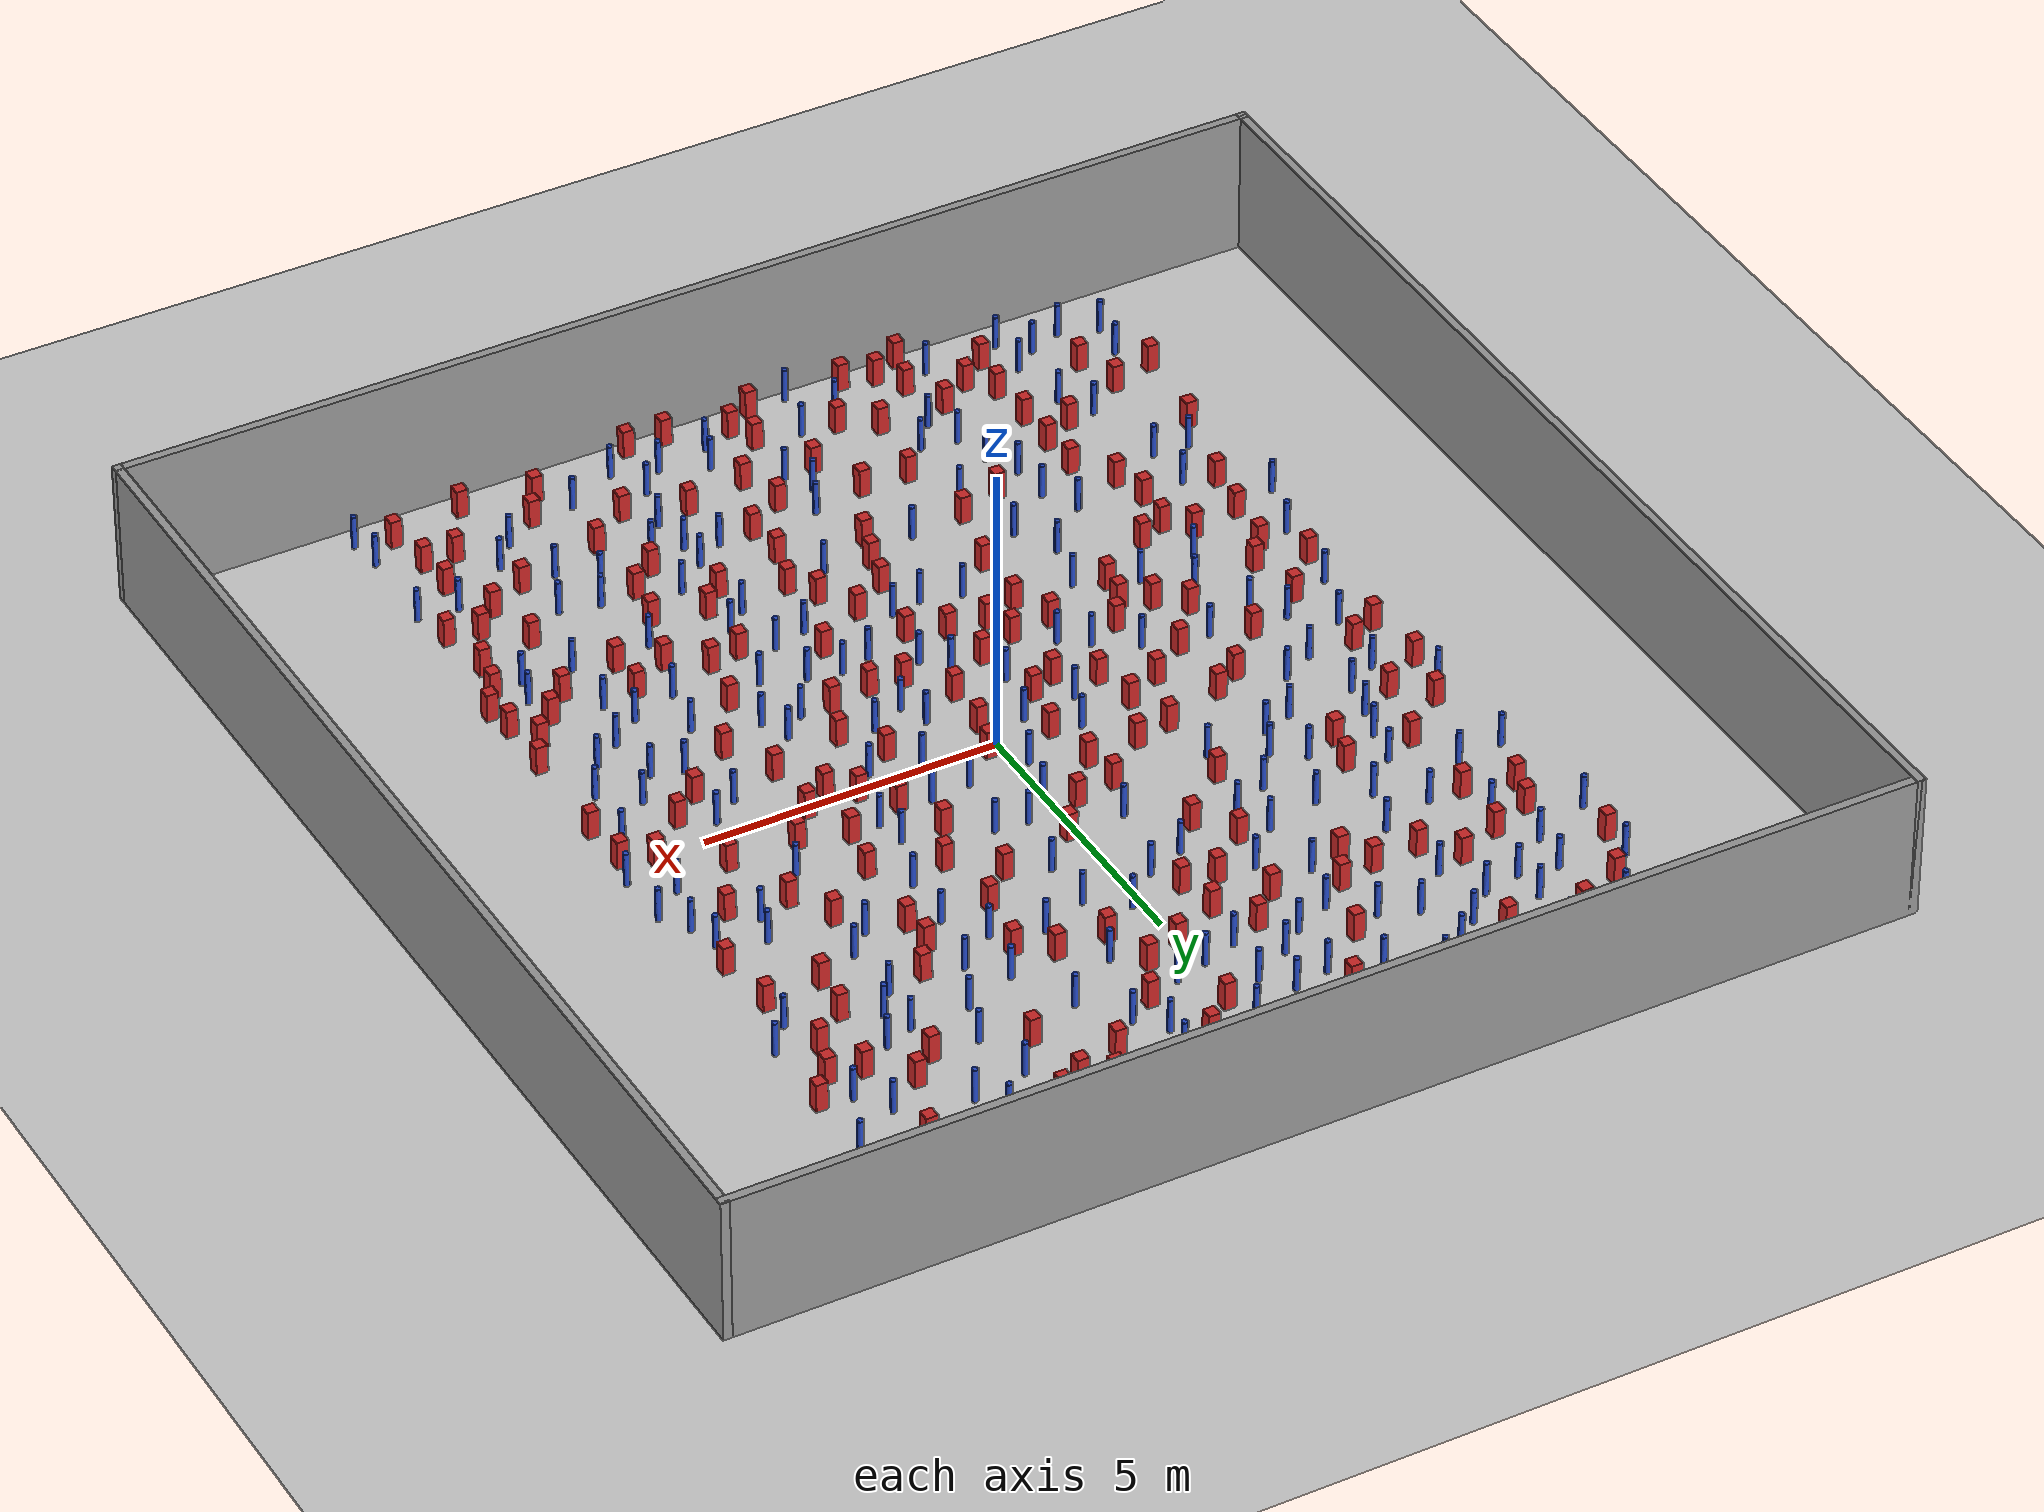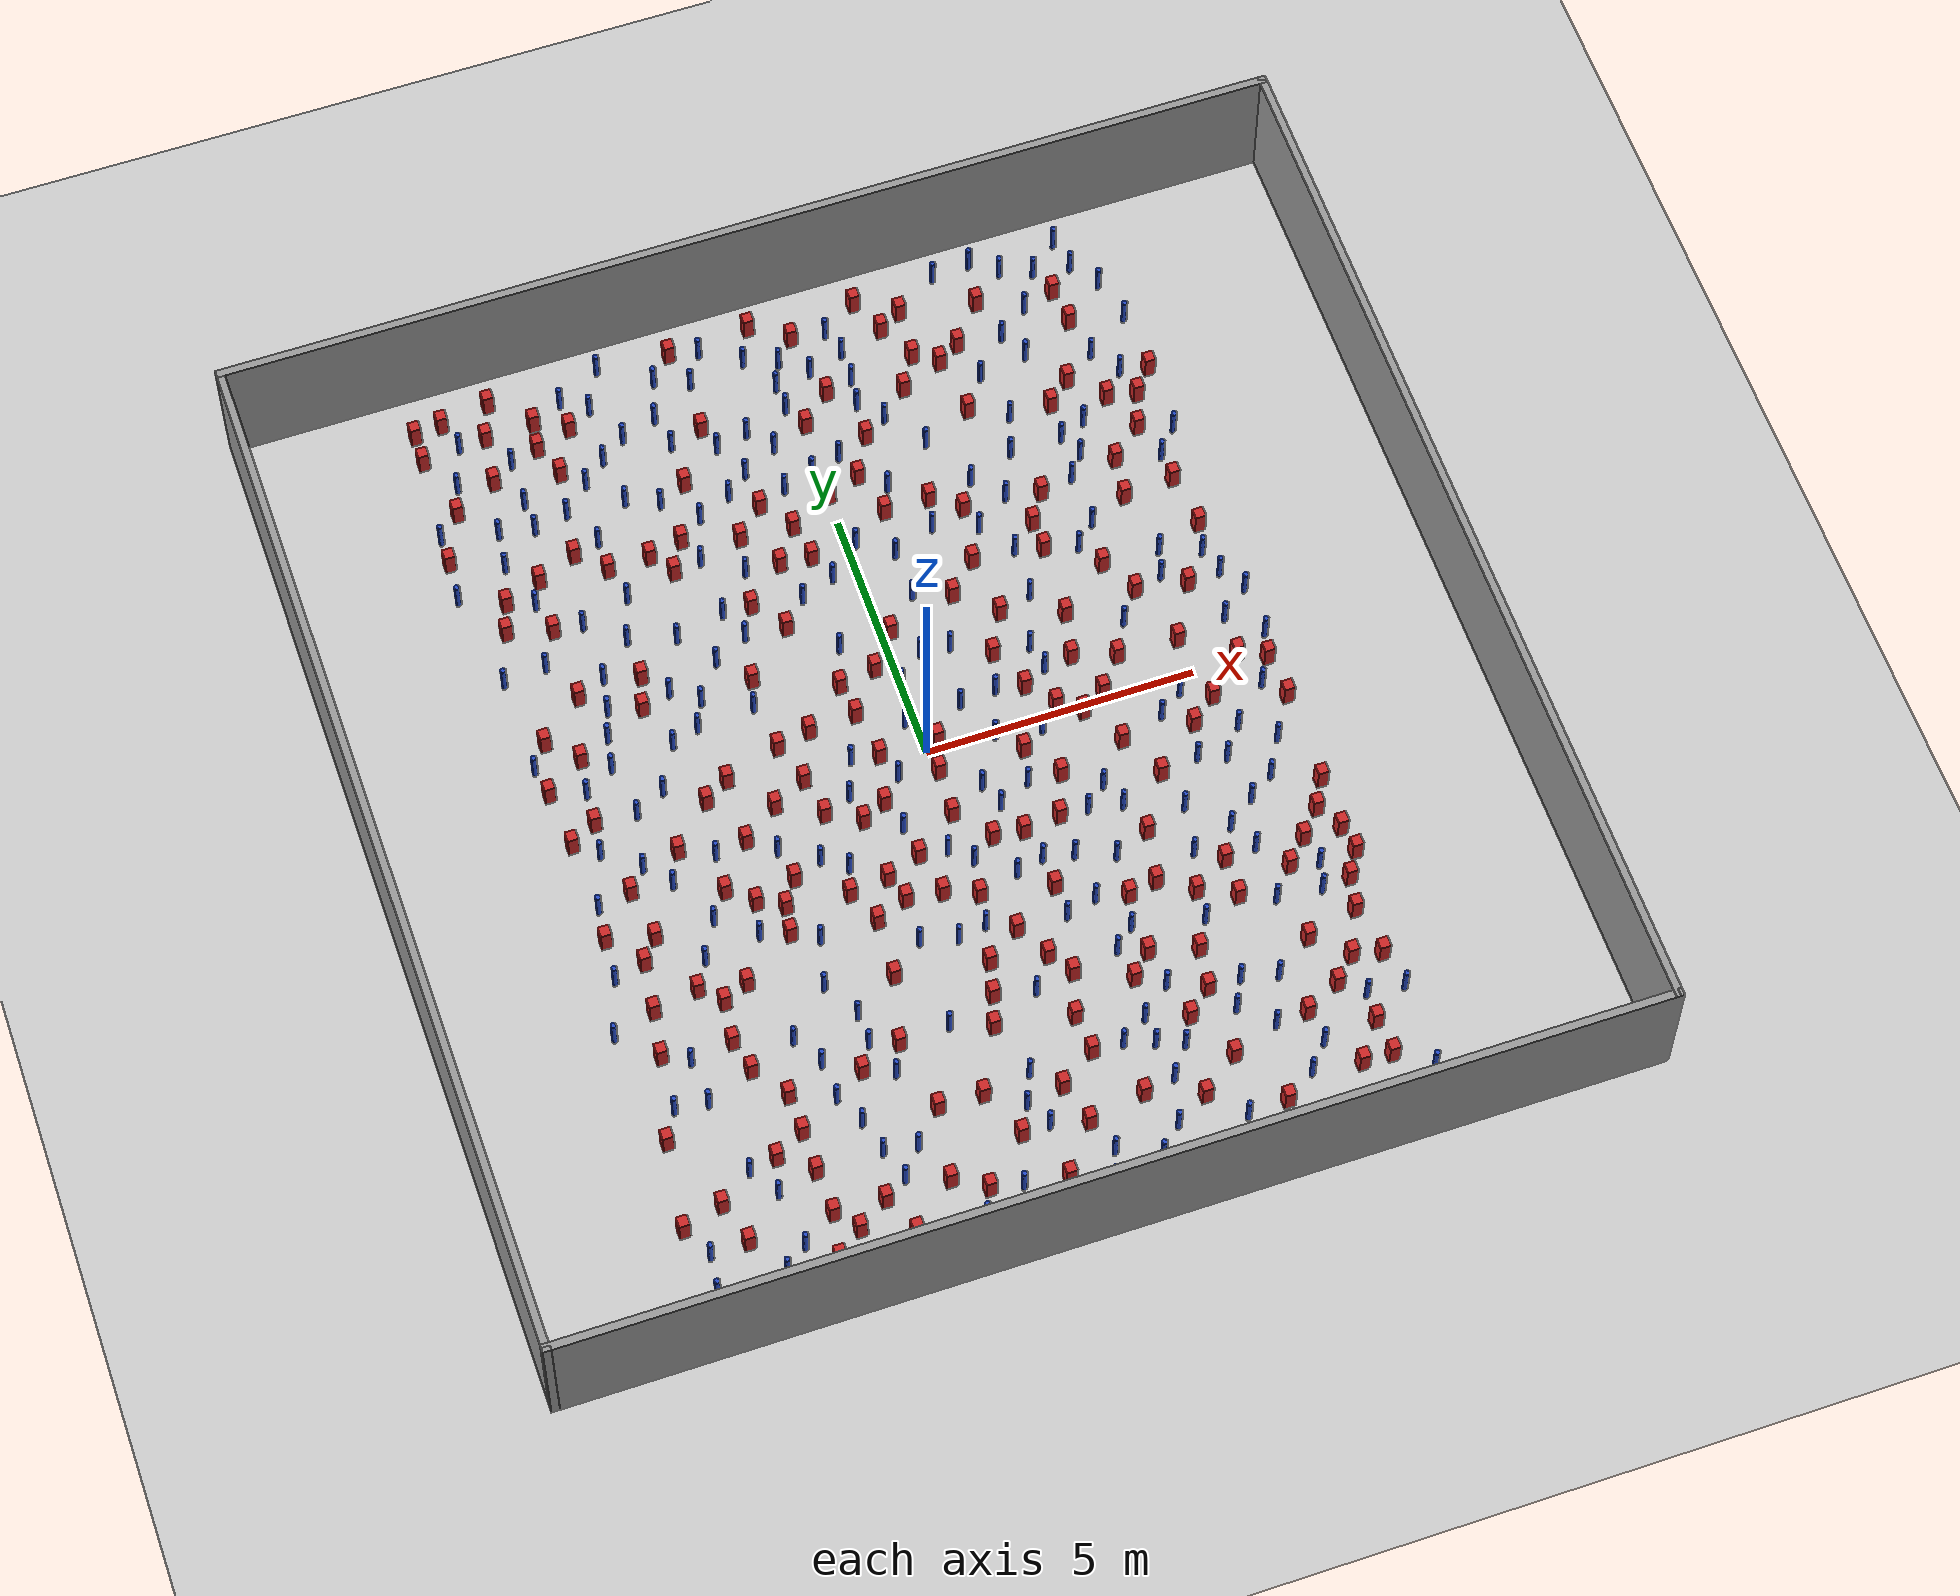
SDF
<sdf version="1.6">
 <world name="default">
  <light name="sun" type="directional">
   <pose>0 0 1000 0 -0 0</pose>
   <diffuse>0.8 0.8 0.8 1</diffuse>
   <specular>0.1 0.1 0.1 1</specular>
   <attenuation>
    <range>1000</range>
    <constant>0.9</constant>
    <linear>0.01</linear>
    <quadratic>0.001</quadratic>
   </attenuation>
   <direction>-0.5 0.5 -1</direction>
  </light>
  <model name="ground_plane">
   <static>1</static>
   <link name="link">
    <collision name="collision">
     <geometry><plane><normal>0 0 1</normal><size>100 100</size></plane></geometry>
     <surface><friction><ode><mu>100</mu><mu2>50</mu2></ode></friction></surface>
    </collision>
    <visual name="visual">
     <cast_shadows>0</cast_shadows>
     <geometry><plane><normal>0 0 1</normal><size>100 100</size></plane></geometry>
     <material>
      <ambient>1.0 1.0 1.0 1.0</ambient>
      <diffuse>0.8 0.8 0.8 1.0</diffuse>
      <specular>0.01 0.01 0.01 1.000000</specular>
     </material>
    </visual>
   </link>
  </model>
  <gravity>0 0 -9.8</gravity>
  <magnetic_field>6e-06 2.3e-05 -4.2e-05</magnetic_field>
  <atmosphere type="adiabatic"/>
  <physics name="default_physics" default="0" type="ode">
   <max_step_size>0.001</max_step_size>
   <real_time_factor>1</real_time_factor>
   <real_time_update_rate>1000</real_time_update_rate>
  </physics>
  <scene><ambient>0.4 0.4 0.4 1</ambient><background>0.7 0.7 0.7 1</background><shadows>1</shadows></scene>
  <spherical_coordinates>
   <surface_model>EARTH_WGS84</surface_model>
   <latitude_deg>0</latitude_deg>
   <longitude_deg>0</longitude_deg>
   <elevation>0</elevation>
   <heading_deg>0</heading_deg>
  </spherical_coordinates>
  <plugin name="gazebo_occupancy_map" filename="libgazebo_2Dmap_plugin.so">
   <map_resolution>0.05</map_resolution>
   <map_topic>generated_map</map_topic>
   <map_height>0.01</map_height>
   <map_size_x>50</map_size_x>
   <map_size_y>50</map_size_y>
  </plugin>
  <model name="NamedLocations">
   <static>true</static>
   <link name="DefaultStart"><pose>8.5 0 0 0 0 3.14</pose></link>
  </model>
  <model name="20x20_walls">
   <pose>0.044518 0.176112 0 0 -0 0</pose>
   <link name="Wall_1">
    <collision name="Wall_1_Collision">
     <geometry><box><size>20 0.15 2.5</size></box></geometry>
     <pose>0 0 1.25 0 -0 0</pose>
    </collision>
    <visual name="Wall_1_Visual">
     <pose>0 0 1.25 0 -0 0</pose>
     <geometry><box><size>20 0.15 2.5</size></box></geometry>
     <material>
      <script><uri>file://media/materials/scripts/gazebo.material</uri><name>Gazebo/Grey</name></script>
      <ambient>0.976471 0.992157 1 1</ambient>
     </material>
     <meta><layer>0</layer></meta>
    </visual>
    <pose>0 9.925 0 0 -0 0</pose>
   </link>
   <link name="Wall_3">
    <collision name="Wall_3_Collision">
     <geometry><box><size>20 0.15 2.5</size></box></geometry>
     <pose>0 0 1.25 0 -0 0</pose>
    </collision>
    <visual name="Wall_3_Visual">
     <pose>0 0 1.25 0 -0 0</pose>
     <geometry><box><size>20 0.15 2.5</size></box></geometry>
     <material>
      <script><uri>file://media/materials/scripts/gazebo.material</uri><name>Gazebo/Grey</name></script>
      <ambient>0.976471 0.992157 1 1</ambient>
     </material>
     <meta><layer>0</layer></meta>
    </visual>
    <pose>9.925 0 0 0 0 -1.5708</pose>
   </link>
   <link name="Wall_4">
    <collision name="Wall_4_Collision">
     <geometry><box><size>20 0.15 2.5</size></box></geometry>
     <pose>0 0 1.25 0 -0 0</pose>
    </collision>
    <visual name="Wall_4_Visual">
     <pose>0 0 1.25 0 -0 0</pose>
     <geometry><box><size>20 0.15 2.5</size></box></geometry>
     <material>
      <script><uri>file://media/materials/scripts/gazebo.material</uri><name>Gazebo/Grey</name></script>
      <ambient>0.976471 0.992157 1 1</ambient>
     </material>
     <meta><layer>0</layer></meta>
    </visual>
    <pose>0 -9.925 0 0 -0 3.14159</pose>
   </link>
   <link name="Wall_5">
    <collision name="Wall_5_Collision">
     <geometry><box><size>20 0.15 2.5</size></box></geometry>
     <pose>0 0 1.25 0 -0 0</pose>
    </collision>
    <visual name="Wall_5_Visual">
     <pose>0 0 1.25 0 -0 0</pose>
     <geometry><box><size>20 0.15 2.5</size></box></geometry>
     <material>
      <script><uri>file://media/materials/scripts/gazebo.material</uri><name>Gazebo/Grey</name></script>
      <ambient>0.976471 0.992157 1 1</ambient>
     </material>
     <meta><layer>0</layer></meta>
    </visual>
    <pose>-9.925 0 0 0 -0 1.5708</pose>
   </link>
   <static>1</static>
  </model>
  <model name="pole_obstacle0">
   <static>true</static>
   <pose>0.0405761902183 8.55352330351 -9.47619616065e-06 5.49618799737e-07 2.36310414033e-07 -1.55090534817e-07</pose>
   <link name="link">
    <pose>0 0 0.3 0 -0 0</pose>
    <inertial>
     <mass>1</mass>
     <inertia><ixx>0.145833</ixx><ixy>0</ixy><ixz>0</ixz><iyy>0.145833</iyy><iyz>0</iyz><izz>0.125</izz></inertia>
    </inertial>
    <collision name="collision">
     <geometry><cylinder><radius>0.05</radius><length>.6</length></cylinder></geometry>
    </collision>
    <visual name="visual">
     <geometry><cylinder><radius>0.05</radius><length>.6</length></cylinder></geometry>
     <material>
      <script><name>Gazebo/Blue</name><uri>file://media/materials/scripts/gazebo.material</uri></script>
     </material>
    </visual>
   </link>
  </model>
  <model name="pole_obstacle1">
   <static>true</static>
   <pose>-3.19911717233 -3.85749164379 -9.47619616065e-06 5.49618799737e-07 2.36310414067e-07 -1.55090534797e-07</pose>
   <link name="link">
    <pose>0 0 0.3 0 -0 0</pose>
    <inertial>
     <mass>1</mass>
     <inertia><ixx>0.145833</ixx><ixy>0</ixy><ixz>0</ixz><iyy>0.145833</iyy><iyz>0</iyz><izz>0.125</izz></inertia>
    </inertial>
    <collision name="collision">
     <geometry><cylinder><radius>0.05</radius><length>.6</length></cylinder></geometry>
    </collision>
    <visual name="visual">
     <geometry><cylinder><radius>0.05</radius><length>.6</length></cylinder></geometry>
     <material>
      <script><name>Gazebo/Blue</name><uri>file://media/materials/scripts/gazebo.material</uri></script>
     </material>
    </visual>
   </link>
  </model>
  <model name="square_post_obstacle0">
   <static>true</static>
   <pose>0.944305064648 -4.99120115304 -6.11067671241e-07 -5.50515727128e-06 -8.79689657224e-07 2.37013304536e-05</pose>
   <link name="link">
    <pose>0 0 0.25 0 -0 0</pose>
    <inertial>
     <mass>100</mass>
     <inertia>
      <ixx>0.166667</ixx>
      <ixy>0</ixy>
      <ixz>0</ixz>
      <iyy>0.166667</iyy>
      <iyz>0</iyz>
      <izz>0.166667</izz>
     </inertia>
    </inertial>
    <collision name="collision"><geometry><box><size>.2 .2 .5</size></box></geometry></collision>
    <visual name="visual">
     <geometry><box><size>.2 .2 .5</size></box></geometry>
     <material>
      <script><name>Gazebo/Red</name><uri>file://media/materials/scripts/gazebo.material</uri></script>
     </material>
    </visual>
   </link>
  </model>
  <model name="square_post_obstacle1">
   <static>true</static>
   <pose>2.3046732225 -7.91956817169 -6.11067671241e-07 -5.50515727128e-06 -8.79689657224e-07 2.37013304536e-05</pose>
   <link name="link">
    <pose>0 0 0.25 0 -0 0</pose>
    <inertial>
     <mass>100</mass>
     <inertia>
      <ixx>0.166667</ixx>
      <ixy>0</ixy>
      <ixz>0</ixz>
      <iyy>0.166667</iyy>
      <iyz>0</iyz>
      <izz>0.166667</izz>
     </inertia>
    </inertial>
    <collision name="collision"><geometry><box><size>.2 .2 .5</size></box></geometry></collision>
    <visual name="visual">
     <geometry><box><size>.2 .2 .5</size></box></geometry>
     <material>
      <script><name>Gazebo/Red</name><uri>file://media/materials/scripts/gazebo.material</uri></script>
     </material>
    </visual>
   </link>
  </model>
  <model name="pole_obstacle2">
   <static>true</static>
   <pose>-1.27373937846 6.47451242145 -9.47619616065e-06 5.49618799737e-07 2.36310414061e-07 -1.550905348e-07</pose>
   <link name="link">
    <pose>0 0 0.3 0 -0 0</pose>
    <inertial>
     <mass>1</mass>
     <inertia><ixx>0.145833</ixx><ixy>0</ixy><ixz>0</ixz><iyy>0.145833</iyy><iyz>0</iyz><izz>0.125</izz></inertia>
    </inertial>
    <collision name="collision">
     <geometry><cylinder><radius>0.05</radius><length>.6</length></cylinder></geometry>
    </collision>
    <visual name="visual">
     <geometry><cylinder><radius>0.05</radius><length>.6</length></cylinder></geometry>
     <material>
      <script><name>Gazebo/Blue</name><uri>file://media/materials/scripts/gazebo.material</uri></script>
     </material>
    </visual>
   </link>
  </model>
  <model name="pole_obstacle3">
   <static>true</static>
   <pose>4.53063861416 9.14221263747 -9.47619616065e-06 5.49618799737e-07 2.36310414065e-07 -1.55090534796e-07</pose>
   <link name="link">
    <pose>0 0 0.3 0 -0 0</pose>
    <inertial>
     <mass>1</mass>
     <inertia><ixx>0.145833</ixx><ixy>0</ixy><ixz>0</ixz><iyy>0.145833</iyy><iyz>0</iyz><izz>0.125</izz></inertia>
    </inertial>
    <collision name="collision">
     <geometry><cylinder><radius>0.05</radius><length>.6</length></cylinder></geometry>
    </collision>
    <visual name="visual">
     <geometry><cylinder><radius>0.05</radius><length>.6</length></cylinder></geometry>
     <material>
      <script><name>Gazebo/Blue</name><uri>file://media/materials/scripts/gazebo.material</uri></script>
     </material>
    </visual>
   </link>
  </model>
  <model name="pole_obstacle4">
   <static>true</static>
   <pose>1.67797747055 -8.28879280093 -9.47619616065e-06 5.49618799737e-07 2.36310414046e-07 -1.55090534809e-07</pose>
   <link name="link">
    <pose>0 0 0.3 0 -0 0</pose>
    <inertial>
     <mass>1</mass>
     <inertia><ixx>0.145833</ixx><ixy>0</ixy><ixz>0</ixz><iyy>0.145833</iyy><iyz>0</iyz><izz>0.125</izz></inertia>
    </inertial>
    <collision name="collision">
     <geometry><cylinder><radius>0.05</radius><length>.6</length></cylinder></geometry>
    </collision>
    <visual name="visual">
     <geometry><cylinder><radius>0.05</radius><length>.6</length></cylinder></geometry>
     <material>
      <script><name>Gazebo/Blue</name><uri>file://media/materials/scripts/gazebo.material</uri></script>
     </material>
    </visual>
   </link>
  </model>
  <model name="pole_obstacle5">
   <static>true</static>
   <pose>4.95172508571 -1.85118535402 -9.47619616065e-06 5.49618799738e-07 2.36310414071e-07 -1.55090534796e-07</pose>
   <link name="link">
    <pose>0 0 0.3 0 -0 0</pose>
    <inertial>
     <mass>1</mass>
     <inertia><ixx>0.145833</ixx><ixy>0</ixy><ixz>0</ixz><iyy>0.145833</iyy><iyz>0</iyz><izz>0.125</izz></inertia>
    </inertial>
    <collision name="collision">
     <geometry><cylinder><radius>0.05</radius><length>.6</length></cylinder></geometry>
    </collision>
    <visual name="visual">
     <geometry><cylinder><radius>0.05</radius><length>.6</length></cylinder></geometry>
     <material>
      <script><name>Gazebo/Blue</name><uri>file://media/materials/scripts/gazebo.material</uri></script>
     </material>
    </visual>
   </link>
  </model>
  <model name="pole_obstacle6">
   <static>true</static>
   <pose>-5.10376092105 2.55919030713 -9.47619616065e-06 5.49618799738e-07 2.36310414051e-07 -1.55090534805e-07</pose>
   <link name="link">
    <pose>0 0 0.3 0 -0 0</pose>
    <inertial>
     <mass>1</mass>
     <inertia><ixx>0.145833</ixx><ixy>0</ixy><ixz>0</ixz><iyy>0.145833</iyy><iyz>0</iyz><izz>0.125</izz></inertia>
    </inertial>
    <collision name="collision">
     <geometry><cylinder><radius>0.05</radius><length>.6</length></cylinder></geometry>
    </collision>
    <visual name="visual">
     <geometry><cylinder><radius>0.05</radius><length>.6</length></cylinder></geometry>
     <material>
      <script><name>Gazebo/Blue</name><uri>file://media/materials/scripts/gazebo.material</uri></script>
     </material>
    </visual>
   </link>
  </model>
  <model name="square_post_obstacle2">
   <static>true</static>
   <pose>5.52280891063 1.71290231488 -6.11067671241e-07 -5.50515727128e-06 -8.79689657224e-07 2.37013304536e-05</pose>
   <link name="link">
    <pose>0 0 0.25 0 -0 0</pose>
    <inertial>
     <mass>100</mass>
     <inertia>
      <ixx>0.166667</ixx>
      <ixy>0</ixy>
      <ixz>0</ixz>
      <iyy>0.166667</iyy>
      <iyz>0</iyz>
      <izz>0.166667</izz>
     </inertia>
    </inertial>
    <collision name="collision"><geometry><box><size>.2 .2 .5</size></box></geometry></collision>
    <visual name="visual">
     <geometry><box><size>.2 .2 .5</size></box></geometry>
     <material>
      <script><name>Gazebo/Red</name><uri>file://media/materials/scripts/gazebo.material</uri></script>
     </material>
    </visual>
   </link>
  </model>
  <model name="square_post_obstacle3">
   <static>true</static>
   <pose>2.48934977216 8.89152247828 -6.11067671241e-07 -5.50515727128e-06 -8.79689657224e-07 2.37013304536e-05</pose>
   <link name="link">
    <pose>0 0 0.25 0 -0 0</pose>
    <inertial>
     <mass>100</mass>
     <inertia>
      <ixx>0.166667</ixx>
      <ixy>0</ixy>
      <ixz>0</ixz>
      <iyy>0.166667</iyy>
      <iyz>0</iyz>
      <izz>0.166667</izz>
     </inertia>
    </inertial>
    <collision name="collision"><geometry><box><size>.2 .2 .5</size></box></geometry></collision>
    <visual name="visual">
     <geometry><box><size>.2 .2 .5</size></box></geometry>
     <material>
      <script><name>Gazebo/Red</name><uri>file://media/materials/scripts/gazebo.material</uri></script>
     </material>
    </visual>
   </link>
  </model>
  <model name="square_post_obstacle4">
   <static>true</static>
   <pose>2.0309213885 7.29000807328 -6.11067671241e-07 -5.50515727128e-06 -8.79689657224e-07 2.37013304536e-05</pose>
   <link name="link">
    <pose>0 0 0.25 0 -0 0</pose>
    <inertial>
     <mass>100</mass>
     <inertia>
      <ixx>0.166667</ixx>
      <ixy>0</ixy>
      <ixz>0</ixz>
      <iyy>0.166667</iyy>
      <iyz>0</iyz>
      <izz>0.166667</izz>
     </inertia>
    </inertial>
    <collision name="collision"><geometry><box><size>.2 .2 .5</size></box></geometry></collision>
    <visual name="visual">
     <geometry><box><size>.2 .2 .5</size></box></geometry>
     <material>
      <script><name>Gazebo/Red</name><uri>file://media/materials/scripts/gazebo.material</uri></script>
     </material>
    </visual>
   </link>
  </model>
  <model name="pole_obstacle7">
   <static>true</static>
   <pose>-5.00055378148 4.37309625407 -9.47619616065e-06 5.49618799737e-07 2.36310414037e-07 -1.55090534814e-07</pose>
   <link name="link">
    <pose>0 0 0.3 0 -0 0</pose>
    <inertial>
     <mass>1</mass>
     <inertia><ixx>0.145833</ixx><ixy>0</ixy><ixz>0</ixz><iyy>0.145833</iyy><iyz>0</iyz><izz>0.125</izz></inertia>
    </inertial>
    <collision name="collision">
     <geometry><cylinder><radius>0.05</radius><length>.6</length></cylinder></geometry>
    </collision>
    <visual name="visual">
     <geometry><cylinder><radius>0.05</radius><length>.6</length></cylinder></geometry>
     <material>
      <script><name>Gazebo/Blue</name><uri>file://media/materials/scripts/gazebo.material</uri></script>
     </material>
    </visual>
   </link>
  </model>
  <model name="pole_obstacle8">
   <static>true</static>
   <pose>-5.01428291551 -9.12350904369 -9.47619616065e-06 5.49618799737e-07 2.36310414065e-07 -1.55090534796e-07</pose>
   <link name="link">
    <pose>0 0 0.3 0 -0 0</pose>
    <inertial>
     <mass>1</mass>
     <inertia><ixx>0.145833</ixx><ixy>0</ixy><ixz>0</ixz><iyy>0.145833</iyy><iyz>0</iyz><izz>0.125</izz></inertia>
    </inertial>
    <collision name="collision">
     <geometry><cylinder><radius>0.05</radius><length>.6</length></cylinder></geometry>
    </collision>
    <visual name="visual">
     <geometry><cylinder><radius>0.05</radius><length>.6</length></cylinder></geometry>
     <material>
      <script><name>Gazebo/Blue</name><uri>file://media/materials/scripts/gazebo.material</uri></script>
     </material>
    </visual>
   </link>
  </model>
  <model name="square_post_obstacle5">
   <static>true</static>
   <pose>-4.4312994662 -7.13340059479 -6.11067671241e-07 -5.50515727128e-06 -8.79689657224e-07 2.37013304536e-05</pose>
   <link name="link">
    <pose>0 0 0.25 0 -0 0</pose>
    <inertial>
     <mass>100</mass>
     <inertia>
      <ixx>0.166667</ixx>
      <ixy>0</ixy>
      <ixz>0</ixz>
      <iyy>0.166667</iyy>
      <iyz>0</iyz>
      <izz>0.166667</izz>
     </inertia>
    </inertial>
    <collision name="collision"><geometry><box><size>.2 .2 .5</size></box></geometry></collision>
    <visual name="visual">
     <geometry><box><size>.2 .2 .5</size></box></geometry>
     <material>
      <script><name>Gazebo/Red</name><uri>file://media/materials/scripts/gazebo.material</uri></script>
     </material>
    </visual>
   </link>
  </model>
  <model name="square_post_obstacle6">
   <static>true</static>
   <pose>4.57847857241 1.88806926313 -6.11067671241e-07 -5.50515727128e-06 -8.79689657224e-07 2.37013304536e-05</pose>
   <link name="link">
    <pose>0 0 0.25 0 -0 0</pose>
    <inertial>
     <mass>100</mass>
     <inertia>
      <ixx>0.166667</ixx>
      <ixy>0</ixy>
      <ixz>0</ixz>
      <iyy>0.166667</iyy>
      <iyz>0</iyz>
      <izz>0.166667</izz>
     </inertia>
    </inertial>
    <collision name="collision"><geometry><box><size>.2 .2 .5</size></box></geometry></collision>
    <visual name="visual">
     <geometry><box><size>.2 .2 .5</size></box></geometry>
     <material>
      <script><name>Gazebo/Red</name><uri>file://media/materials/scripts/gazebo.material</uri></script>
     </material>
    </visual>
   </link>
  </model>
  <model name="square_post_obstacle7">
   <static>true</static>
   <pose>3.60023916208 -8.46336494209 -6.11067671241e-07 -5.50515727128e-06 -8.79689657224e-07 2.37013304536e-05</pose>
   <link name="link">
    <pose>0 0 0.25 0 -0 0</pose>
    <inertial>
     <mass>100</mass>
     <inertia>
      <ixx>0.166667</ixx>
      <ixy>0</ixy>
      <ixz>0</ixz>
      <iyy>0.166667</iyy>
      <iyz>0</iyz>
      <izz>0.166667</izz>
     </inertia>
    </inertial>
    <collision name="collision"><geometry><box><size>.2 .2 .5</size></box></geometry></collision>
    <visual name="visual">
     <geometry><box><size>.2 .2 .5</size></box></geometry>
     <material>
      <script><name>Gazebo/Red</name><uri>file://media/materials/scripts/gazebo.material</uri></script>
     </material>
    </visual>
   </link>
  </model>
  <model name="pole_obstacle9">
   <static>true</static>
   <pose>4.38289889013 7.25559182858 -9.47619616065e-06 5.49618799737e-07 2.36310414037e-07 -1.55090534814e-07</pose>
   <link name="link">
    <pose>0 0 0.3 0 -0 0</pose>
    <inertial>
     <mass>1</mass>
     <inertia><ixx>0.145833</ixx><ixy>0</ixy><ixz>0</ixz><iyy>0.145833</iyy><iyz>0</iyz><izz>0.125</izz></inertia>
    </inertial>
    <collision name="collision">
     <geometry><cylinder><radius>0.05</radius><length>.6</length></cylinder></geometry>
    </collision>
    <visual name="visual">
     <geometry><cylinder><radius>0.05</radius><length>.6</length></cylinder></geometry>
     <material>
      <script><name>Gazebo/Blue</name><uri>file://media/materials/scripts/gazebo.material</uri></script>
     </material>
    </visual>
   </link>
  </model>
  <model name="pole_obstacle10">
   <static>true</static>
   <pose>1.45750841201 -1.19569166545 -9.47619616065e-06 5.49618799737e-07 2.36310414065e-07 -1.55090534798e-07</pose>
   <link name="link">
    <pose>0 0 0.3 0 -0 0</pose>
    <inertial>
     <mass>1</mass>
     <inertia><ixx>0.145833</ixx><ixy>0</ixy><ixz>0</ixz><iyy>0.145833</iyy><iyz>0</iyz><izz>0.125</izz></inertia>
    </inertial>
    <collision name="collision">
     <geometry><cylinder><radius>0.05</radius><length>.6</length></cylinder></geometry>
    </collision>
    <visual name="visual">
     <geometry><cylinder><radius>0.05</radius><length>.6</length></cylinder></geometry>
     <material>
      <script><name>Gazebo/Blue</name><uri>file://media/materials/scripts/gazebo.material</uri></script>
     </material>
    </visual>
   </link>
  </model>
  <model name="pole_obstacle11">
   <static>true</static>
   <pose>3.64021856873 -6.03391371396 -9.47619616065e-06 5.49618799738e-07 2.3631041406e-07 -1.55090534801e-07</pose>
   <link name="link">
    <pose>0 0 0.3 0 -0 0</pose>
    <inertial>
     <mass>1</mass>
     <inertia><ixx>0.145833</ixx><ixy>0</ixy><ixz>0</ixz><iyy>0.145833</iyy><iyz>0</iyz><izz>0.125</izz></inertia>
    </inertial>
    <collision name="collision">
     <geometry><cylinder><radius>0.05</radius><length>.6</length></cylinder></geometry>
    </collision>
    <visual name="visual">
     <geometry><cylinder><radius>0.05</radius><length>.6</length></cylinder></geometry>
     <material>
      <script><name>Gazebo/Blue</name><uri>file://media/materials/scripts/gazebo.material</uri></script>
     </material>
    </visual>
   </link>
  </model>
  <model name="pole_obstacle12">
   <static>true</static>
   <pose>4.16618906073 1.33775884819 -9.47619616065e-06 5.49618799738e-07 2.36310414071e-07 -1.55090534796e-07</pose>
   <link name="link">
    <pose>0 0 0.3 0 -0 0</pose>
    <inertial>
     <mass>1</mass>
     <inertia><ixx>0.145833</ixx><ixy>0</ixy><ixz>0</ixz><iyy>0.145833</iyy><iyz>0</iyz><izz>0.125</izz></inertia>
    </inertial>
    <collision name="collision">
     <geometry><cylinder><radius>0.05</radius><length>.6</length></cylinder></geometry>
    </collision>
    <visual name="visual">
     <geometry><cylinder><radius>0.05</radius><length>.6</length></cylinder></geometry>
     <material>
      <script><name>Gazebo/Blue</name><uri>file://media/materials/scripts/gazebo.material</uri></script>
     </material>
    </visual>
   </link>
  </model>
  <model name="square_post_obstacle8">
   <static>true</static>
   <pose>-0.903577958004 -7.60333633524 -6.11067671241e-07 -5.50515727128e-06 -8.79689657224e-07 2.37013304536e-05</pose>
   <link name="link">
    <pose>0 0 0.25 0 -0 0</pose>
    <inertial>
     <mass>100</mass>
     <inertia>
      <ixx>0.166667</ixx>
      <ixy>0</ixy>
      <ixz>0</ixz>
      <iyy>0.166667</iyy>
      <iyz>0</iyz>
      <izz>0.166667</izz>
     </inertia>
    </inertial>
    <collision name="collision"><geometry><box><size>.2 .2 .5</size></box></geometry></collision>
    <visual name="visual">
     <geometry><box><size>.2 .2 .5</size></box></geometry>
     <material>
      <script><name>Gazebo/Red</name><uri>file://media/materials/scripts/gazebo.material</uri></script>
     </material>
    </visual>
   </link>
  </model>
  <model name="square_post_obstacle9">
   <static>true</static>
   <pose>5.59965612481 -8.22088846816 -6.11067671241e-07 -5.50515727128e-06 -8.79689657224e-07 2.37013304536e-05</pose>
   <link name="link">
    <pose>0 0 0.25 0 -0 0</pose>
    <inertial>
     <mass>100</mass>
     <inertia>
      <ixx>0.166667</ixx>
      <ixy>0</ixy>
      <ixz>0</ixz>
      <iyy>0.166667</iyy>
      <iyz>0</iyz>
      <izz>0.166667</izz>
     </inertia>
    </inertial>
    <collision name="collision"><geometry><box><size>.2 .2 .5</size></box></geometry></collision>
    <visual name="visual">
     <geometry><box><size>.2 .2 .5</size></box></geometry>
     <material>
      <script><name>Gazebo/Red</name><uri>file://media/materials/scripts/gazebo.material</uri></script>
     </material>
    </visual>
   </link>
  </model>
  <model name="pole_obstacle13">
   <static>true</static>
   <pose>-5.23885158348 0.395496682585 -9.47619616065e-06 5.49618799737e-07 2.36310414057e-07 -1.55090534802e-07</pose>
   <link name="link">
    <pose>0 0 0.3 0 -0 0</pose>
    <inertial>
     <mass>1</mass>
     <inertia><ixx>0.145833</ixx><ixy>0</ixy><ixz>0</ixz><iyy>0.145833</iyy><iyz>0</iyz><izz>0.125</izz></inertia>
    </inertial>
    <collision name="collision">
     <geometry><cylinder><radius>0.05</radius><length>.6</length></cylinder></geometry>
    </collision>
    <visual name="visual">
     <geometry><cylinder><radius>0.05</radius><length>.6</length></cylinder></geometry>
     <material>
      <script><name>Gazebo/Blue</name><uri>file://media/materials/scripts/gazebo.material</uri></script>
     </material>
    </visual>
   </link>
  </model>
  <model name="square_post_obstacle10">
   <static>true</static>
   <pose>4.94972560376 0.686517332191 -6.11067671241e-07 -5.50515727128e-06 -8.79689657224e-07 2.37013304536e-05</pose>
   <link name="link">
    <pose>0 0 0.25 0 -0 0</pose>
    <inertial>
     <mass>100</mass>
     <inertia>
      <ixx>0.166667</ixx>
      <ixy>0</ixy>
      <ixz>0</ixz>
      <iyy>0.166667</iyy>
      <iyz>0</iyz>
      <izz>0.166667</izz>
     </inertia>
    </inertial>
    <collision name="collision"><geometry><box><size>.2 .2 .5</size></box></geometry></collision>
    <visual name="visual">
     <geometry><box><size>.2 .2 .5</size></box></geometry>
     <material>
      <script><name>Gazebo/Red</name><uri>file://media/materials/scripts/gazebo.material</uri></script>
     </material>
    </visual>
   </link>
  </model>
  <model name="square_post_obstacle11">
   <static>true</static>
   <pose>-1.24037410064 5.7349387828 -6.11067671241e-07 -5.50515727128e-06 -8.79689657224e-07 2.37013304536e-05</pose>
   <link name="link">
    <pose>0 0 0.25 0 -0 0</pose>
    <inertial>
     <mass>100</mass>
     <inertia>
      <ixx>0.166667</ixx>
      <ixy>0</ixy>
      <ixz>0</ixz>
      <iyy>0.166667</iyy>
      <iyz>0</iyz>
      <izz>0.166667</izz>
     </inertia>
    </inertial>
    <collision name="collision"><geometry><box><size>.2 .2 .5</size></box></geometry></collision>
    <visual name="visual">
     <geometry><box><size>.2 .2 .5</size></box></geometry>
     <material>
      <script><name>Gazebo/Red</name><uri>file://media/materials/scripts/gazebo.material</uri></script>
     </material>
    </visual>
   </link>
  </model>
  <model name="pole_obstacle14">
   <static>true</static>
   <pose>0.154008466186 4.43080157095 -9.47619616065e-06 5.49618799737e-07 2.36310414061e-07 -1.55090534801e-07</pose>
   <link name="link">
    <pose>0 0 0.3 0 -0 0</pose>
    <inertial>
     <mass>1</mass>
     <inertia><ixx>0.145833</ixx><ixy>0</ixy><ixz>0</ixz><iyy>0.145833</iyy><iyz>0</iyz><izz>0.125</izz></inertia>
    </inertial>
    <collision name="collision">
     <geometry><cylinder><radius>0.05</radius><length>.6</length></cylinder></geometry>
    </collision>
    <visual name="visual">
     <geometry><cylinder><radius>0.05</radius><length>.6</length></cylinder></geometry>
     <material>
      <script><name>Gazebo/Blue</name><uri>file://media/materials/scripts/gazebo.material</uri></script>
     </material>
    </visual>
   </link>
  </model>
  <model name="pole_obstacle15">
   <static>true</static>
   <pose>6.21537362861 -8.65453550145 -9.47619616065e-06 5.49618799737e-07 2.36310414065e-07 -1.55090534796e-07</pose>
   <link name="link">
    <pose>0 0 0.3 0 -0 0</pose>
    <inertial>
     <mass>1</mass>
     <inertia><ixx>0.145833</ixx><ixy>0</ixy><ixz>0</ixz><iyy>0.145833</iyy><iyz>0</iyz><izz>0.125</izz></inertia>
    </inertial>
    <collision name="collision">
     <geometry><cylinder><radius>0.05</radius><length>.6</length></cylinder></geometry>
    </collision>
    <visual name="visual">
     <geometry><cylinder><radius>0.05</radius><length>.6</length></cylinder></geometry>
     <material>
      <script><name>Gazebo/Blue</name><uri>file://media/materials/scripts/gazebo.material</uri></script>
     </material>
    </visual>
   </link>
  </model>
  <model name="square_post_obstacle12">
   <static>true</static>
   <pose>-4.01311779121 0.254424688509 -6.11067671241e-07 -5.50515727128e-06 -8.79689657224e-07 2.37013304536e-05</pose>
   <link name="link">
    <pose>0 0 0.25 0 -0 0</pose>
    <inertial>
     <mass>100</mass>
     <inertia>
      <ixx>0.166667</ixx>
      <ixy>0</ixy>
      <ixz>0</ixz>
      <iyy>0.166667</iyy>
      <iyz>0</iyz>
      <izz>0.166667</izz>
     </inertia>
    </inertial>
    <collision name="collision"><geometry><box><size>.2 .2 .5</size></box></geometry></collision>
    <visual name="visual">
     <geometry><box><size>.2 .2 .5</size></box></geometry>
     <material>
      <script><name>Gazebo/Red</name><uri>file://media/materials/scripts/gazebo.material</uri></script>
     </material>
    </visual>
   </link>
  </model>
  <model name="pole_obstacle16">
   <static>true</static>
   <pose>-5.76489984956 -5.33657778358 -9.47619616065e-06 5.49618799737e-07 2.36310414037e-07 -1.55090534814e-07</pose>
   <link name="link">
    <pose>0 0 0.3 0 -0 0</pose>
    <inertial>
     <mass>1</mass>
     <inertia><ixx>0.145833</ixx><ixy>0</ixy><ixz>0</ixz><iyy>0.145833</iyy><iyz>0</iyz><izz>0.125</izz></inertia>
    </inertial>
    <collision name="collision">
     <geometry><cylinder><radius>0.05</radius><length>.6</length></cylinder></geometry>
    </collision>
    <visual name="visual">
     <geometry><cylinder><radius>0.05</radius><length>.6</length></cylinder></geometry>
     <material>
      <script><name>Gazebo/Blue</name><uri>file://media/materials/scripts/gazebo.material</uri></script>
     </material>
    </visual>
   </link>
  </model>
  <model name="pole_obstacle17">
   <static>true</static>
   <pose>4.79481528149 -3.70649466461 -9.47619616065e-06 5.49618799738e-07 2.36310414051e-07 -1.55090534805e-07</pose>
   <link name="link">
    <pose>0 0 0.3 0 -0 0</pose>
    <inertial>
     <mass>1</mass>
     <inertia><ixx>0.145833</ixx><ixy>0</ixy><ixz>0</ixz><iyy>0.145833</iyy><iyz>0</iyz><izz>0.125</izz></inertia>
    </inertial>
    <collision name="collision">
     <geometry><cylinder><radius>0.05</radius><length>.6</length></cylinder></geometry>
    </collision>
    <visual name="visual">
     <geometry><cylinder><radius>0.05</radius><length>.6</length></cylinder></geometry>
     <material>
      <script><name>Gazebo/Blue</name><uri>file://media/materials/scripts/gazebo.material</uri></script>
     </material>
    </visual>
   </link>
  </model>
  <model name="square_post_obstacle13">
   <static>true</static>
   <pose>1.47115058338 -9.39906032402 -6.11067671241e-07 -5.50515727128e-06 -8.79689657224e-07 2.37013304536e-05</pose>
   <link name="link">
    <pose>0 0 0.25 0 -0 0</pose>
    <inertial>
     <mass>100</mass>
     <inertia>
      <ixx>0.166667</ixx>
      <ixy>0</ixy>
      <ixz>0</ixz>
      <iyy>0.166667</iyy>
      <iyz>0</iyz>
      <izz>0.166667</izz>
     </inertia>
    </inertial>
    <collision name="collision"><geometry><box><size>.2 .2 .5</size></box></geometry></collision>
    <visual name="visual">
     <geometry><box><size>.2 .2 .5</size></box></geometry>
     <material>
      <script><name>Gazebo/Red</name><uri>file://media/materials/scripts/gazebo.material</uri></script>
     </material>
    </visual>
   </link>
  </model>
  <model name="pole_obstacle18">
   <static>true</static>
   <pose>-6.02193255455 8.67930300951 -9.47619616065e-06 5.49618799737e-07 2.36310414065e-07 -1.55090534796e-07</pose>
   <link name="link">
    <pose>0 0 0.3 0 -0 0</pose>
    <inertial>
     <mass>1</mass>
     <inertia><ixx>0.145833</ixx><ixy>0</ixy><ixz>0</ixz><iyy>0.145833</iyy><iyz>0</iyz><izz>0.125</izz></inertia>
    </inertial>
    <collision name="collision">
     <geometry><cylinder><radius>0.05</radius><length>.6</length></cylinder></geometry>
    </collision>
    <visual name="visual">
     <geometry><cylinder><radius>0.05</radius><length>.6</length></cylinder></geometry>
     <material>
      <script><name>Gazebo/Blue</name><uri>file://media/materials/scripts/gazebo.material</uri></script>
     </material>
    </visual>
   </link>
  </model>
  <model name="square_post_obstacle14">
   <static>true</static>
   <pose>3.31326973187 3.81907040545 -6.11067671241e-07 -5.50515727128e-06 -8.79689657224e-07 2.37013304536e-05</pose>
   <link name="link">
    <pose>0 0 0.25 0 -0 0</pose>
    <inertial>
     <mass>100</mass>
     <inertia>
      <ixx>0.166667</ixx>
      <ixy>0</ixy>
      <ixz>0</ixz>
      <iyy>0.166667</iyy>
      <iyz>0</iyz>
      <izz>0.166667</izz>
     </inertia>
    </inertial>
    <collision name="collision"><geometry><box><size>.2 .2 .5</size></box></geometry></collision>
    <visual name="visual">
     <geometry><box><size>.2 .2 .5</size></box></geometry>
     <material>
      <script><name>Gazebo/Red</name><uri>file://media/materials/scripts/gazebo.material</uri></script>
     </material>
    </visual>
   </link>
  </model>
  <model name="pole_obstacle19">
   <static>true</static>
   <pose>1.18842826301 7.77616489944 -9.47619616065e-06 5.49618799737e-07 2.36310414061e-07 -1.550905348e-07</pose>
   <link name="link">
    <pose>0 0 0.3 0 -0 0</pose>
    <inertial>
     <mass>1</mass>
     <inertia><ixx>0.145833</ixx><ixy>0</ixy><ixz>0</ixz><iyy>0.145833</iyy><iyz>0</iyz><izz>0.125</izz></inertia>
    </inertial>
    <collision name="collision">
     <geometry><cylinder><radius>0.05</radius><length>.6</length></cylinder></geometry>
    </collision>
    <visual name="visual">
     <geometry><cylinder><radius>0.05</radius><length>.6</length></cylinder></geometry>
     <material>
      <script><name>Gazebo/Blue</name><uri>file://media/materials/scripts/gazebo.material</uri></script>
     </material>
    </visual>
   </link>
  </model>
  <model name="square_post_obstacle15">
   <static>true</static>
   <pose>5.99498577776 -5.40891649735 -6.11067671241e-07 -5.50515727128e-06 -8.79689657224e-07 2.37013304536e-05</pose>
   <link name="link">
    <pose>0 0 0.25 0 -0 0</pose>
    <inertial>
     <mass>100</mass>
     <inertia>
      <ixx>0.166667</ixx>
      <ixy>0</ixy>
      <ixz>0</ixz>
      <iyy>0.166667</iyy>
      <iyz>0</iyz>
      <izz>0.166667</izz>
     </inertia>
    </inertial>
    <collision name="collision"><geometry><box><size>.2 .2 .5</size></box></geometry></collision>
    <visual name="visual">
     <geometry><box><size>.2 .2 .5</size></box></geometry>
     <material>
      <script><name>Gazebo/Red</name><uri>file://media/materials/scripts/gazebo.material</uri></script>
     </material>
    </visual>
   </link>
  </model>
  <model name="square_post_obstacle16">
   <static>true</static>
   <pose>1.61154432074 -0.550613531907 -6.11067671241e-07 -5.50515727128e-06 -8.79689657224e-07 2.37013304536e-05</pose>
   <link name="link">
    <pose>0 0 0.25 0 -0 0</pose>
    <inertial>
     <mass>100</mass>
     <inertia>
      <ixx>0.166667</ixx>
      <ixy>0</ixy>
      <ixz>0</ixz>
      <iyy>0.166667</iyy>
      <iyz>0</iyz>
      <izz>0.166667</izz>
     </inertia>
    </inertial>
    <collision name="collision"><geometry><box><size>.2 .2 .5</size></box></geometry></collision>
    <visual name="visual">
     <geometry><box><size>.2 .2 .5</size></box></geometry>
     <material>
      <script><name>Gazebo/Red</name><uri>file://media/materials/scripts/gazebo.material</uri></script>
     </material>
    </visual>
   </link>
  </model>
  <model name="square_post_obstacle17">
   <static>true</static>
   <pose>-4.68590935099 8.20599345179 -6.11067671241e-07 -5.50515727128e-06 -8.79689657224e-07 2.37013304536e-05</pose>
   <link name="link">
    <pose>0 0 0.25 0 -0 0</pose>
    <inertial>
     <mass>100</mass>
     <inertia>
      <ixx>0.166667</ixx>
      <ixy>0</ixy>
      <ixz>0</ixz>
      <iyy>0.166667</iyy>
      <iyz>0</iyz>
      <izz>0.166667</izz>
     </inertia>
    </inertial>
    <collision name="collision"><geometry><box><size>.2 .2 .5</size></box></geometry></collision>
    <visual name="visual">
     <geometry><box><size>.2 .2 .5</size></box></geometry>
     <material>
      <script><name>Gazebo/Red</name><uri>file://media/materials/scripts/gazebo.material</uri></script>
     </material>
    </visual>
   </link>
  </model>
  <model name="pole_obstacle20">
   <static>true</static>
   <pose>1.05609687835 8.89631255664 -9.47619616065e-06 5.49618799737e-07 2.36310414046e-07 -1.55090534809e-07</pose>
   <link name="link">
    <pose>0 0 0.3 0 -0 0</pose>
    <inertial>
     <mass>1</mass>
     <inertia><ixx>0.145833</ixx><ixy>0</ixy><ixz>0</ixz><iyy>0.145833</iyy><iyz>0</iyz><izz>0.125</izz></inertia>
    </inertial>
    <collision name="collision">
     <geometry><cylinder><radius>0.05</radius><length>.6</length></cylinder></geometry>
    </collision>
    <visual name="visual">
     <geometry><cylinder><radius>0.05</radius><length>.6</length></cylinder></geometry>
     <material>
      <script><name>Gazebo/Blue</name><uri>file://media/materials/scripts/gazebo.material</uri></script>
     </material>
    </visual>
   </link>
  </model>
  <model name="pole_obstacle21">
   <static>true</static>
   <pose>0.676874485909 -0.999603426647 -9.47619616065e-06 5.49618799737e-07 2.36310414059e-07 -1.55090534802e-07</pose>
   <link name="link">
    <pose>0 0 0.3 0 -0 0</pose>
    <inertial>
     <mass>1</mass>
     <inertia><ixx>0.145833</ixx><ixy>0</ixy><ixz>0</ixz><iyy>0.145833</iyy><iyz>0</iyz><izz>0.125</izz></inertia>
    </inertial>
    <collision name="collision">
     <geometry><cylinder><radius>0.05</radius><length>.6</length></cylinder></geometry>
    </collision>
    <visual name="visual">
     <geometry><cylinder><radius>0.05</radius><length>.6</length></cylinder></geometry>
     <material>
      <script><name>Gazebo/Blue</name><uri>file://media/materials/scripts/gazebo.material</uri></script>
     </material>
    </visual>
   </link>
  </model>
  <model name="pole_obstacle22">
   <static>true</static>
   <pose>4.70830090613 8.24106829523 -9.47619616065e-06 5.49618799737e-07 2.36310414065e-07 -1.55090534796e-07</pose>
   <link name="link">
    <pose>0 0 0.3 0 -0 0</pose>
    <inertial>
     <mass>1</mass>
     <inertia><ixx>0.145833</ixx><ixy>0</ixy><ixz>0</ixz><iyy>0.145833</iyy><iyz>0</iyz><izz>0.125</izz></inertia>
    </inertial>
    <collision name="collision">
     <geometry><cylinder><radius>0.05</radius><length>.6</length></cylinder></geometry>
    </collision>
    <visual name="visual">
     <geometry><cylinder><radius>0.05</radius><length>.6</length></cylinder></geometry>
     <material>
      <script><name>Gazebo/Blue</name><uri>file://media/materials/scripts/gazebo.material</uri></script>
     </material>
    </visual>
   </link>
  </model>
  <model name="pole_obstacle23">
   <static>true</static>
   <pose>-2.64278070456 -7.25501971859 -9.47619616065e-06 5.49618799738e-07 2.3631041406e-07 -1.55090534801e-07</pose>
   <link name="link">
    <pose>0 0 0.3 0 -0 0</pose>
    <inertial>
     <mass>1</mass>
     <inertia><ixx>0.145833</ixx><ixy>0</ixy><ixz>0</ixz><iyy>0.145833</iyy><iyz>0</iyz><izz>0.125</izz></inertia>
    </inertial>
    <collision name="collision">
     <geometry><cylinder><radius>0.05</radius><length>.6</length></cylinder></geometry>
    </collision>
    <visual name="visual">
     <geometry><cylinder><radius>0.05</radius><length>.6</length></cylinder></geometry>
     <material>
      <script><name>Gazebo/Blue</name><uri>file://media/materials/scripts/gazebo.material</uri></script>
     </material>
    </visual>
   </link>
  </model>
  <model name="square_post_obstacle18">
   <static>true</static>
   <pose>-1.27208905666 4.46009019754 -6.11067671241e-07 -5.50515727128e-06 -8.79689657224e-07 2.37013304536e-05</pose>
   <link name="link">
    <pose>0 0 0.25 0 -0 0</pose>
    <inertial>
     <mass>100</mass>
     <inertia>
      <ixx>0.166667</ixx>
      <ixy>0</ixy>
      <ixz>0</ixz>
      <iyy>0.166667</iyy>
      <iyz>0</iyz>
      <izz>0.166667</izz>
     </inertia>
    </inertial>
    <collision name="collision"><geometry><box><size>.2 .2 .5</size></box></geometry></collision>
    <visual name="visual">
     <geometry><box><size>.2 .2 .5</size></box></geometry>
     <material>
      <script><name>Gazebo/Red</name><uri>file://media/materials/scripts/gazebo.material</uri></script>
     </material>
    </visual>
   </link>
  </model>
  <model name="pole_obstacle24">
   <static>true</static>
   <pose>-2.5588383863 -5.83410289442 -9.47619616065e-06 5.49618799738e-07 2.3631041406e-07 -1.55090534801e-07</pose>
   <link name="link">
    <pose>0 0 0.3 0 -0 0</pose>
    <inertial>
     <mass>1</mass>
     <inertia><ixx>0.145833</ixx><ixy>0</ixy><ixz>0</ixz><iyy>0.145833</iyy><iyz>0</iyz><izz>0.125</izz></inertia>
    </inertial>
    <collision name="collision">
     <geometry><cylinder><radius>0.05</radius><length>.6</length></cylinder></geometry>
    </collision>
    <visual name="visual">
     <geometry><cylinder><radius>0.05</radius><length>.6</length></cylinder></geometry>
     <material>
      <script><name>Gazebo/Blue</name><uri>file://media/materials/scripts/gazebo.material</uri></script>
     </material>
    </visual>
   </link>
  </model>
  <model name="pole_obstacle25">
   <static>true</static>
   <pose>4.6078065156 4.8956471403 -9.47619616065e-06 5.49618799737e-07 2.36310414037e-07 -1.55090534814e-07</pose>
   <link name="link">
    <pose>0 0 0.3 0 -0 0</pose>
    <inertial>
     <mass>1</mass>
     <inertia><ixx>0.145833</ixx><ixy>0</ixy><ixz>0</ixz><iyy>0.145833</iyy><iyz>0</iyz><izz>0.125</izz></inertia>
    </inertial>
    <collision name="collision">
     <geometry><cylinder><radius>0.05</radius><length>.6</length></cylinder></geometry>
    </collision>
    <visual name="visual">
     <geometry><cylinder><radius>0.05</radius><length>.6</length></cylinder></geometry>
     <material>
      <script><name>Gazebo/Blue</name><uri>file://media/materials/scripts/gazebo.material</uri></script>
     </material>
    </visual>
   </link>
  </model>
  <model name="pole_obstacle26">
   <static>true</static>
   <pose>1.23101191874 -0.114247584651 -9.47619616065e-06 5.49618799737e-07 2.36310414064e-07 -1.55090534798e-07</pose>
   <link name="link">
    <pose>0 0 0.3 0 -0 0</pose>
    <inertial>
     <mass>1</mass>
     <inertia><ixx>0.145833</ixx><ixy>0</ixy><ixz>0</ixz><iyy>0.145833</iyy><iyz>0</iyz><izz>0.125</izz></inertia>
    </inertial>
    <collision name="collision">
     <geometry><cylinder><radius>0.05</radius><length>.6</length></cylinder></geometry>
    </collision>
    <visual name="visual">
     <geometry><cylinder><radius>0.05</radius><length>.6</length></cylinder></geometry>
     <material>
      <script><name>Gazebo/Blue</name><uri>file://media/materials/scripts/gazebo.material</uri></script>
     </material>
    </visual>
   </link>
  </model>
  <model name="pole_obstacle27">
   <static>true</static>
   <pose>0.76161487265 3.99004415581 -9.47619616065e-06 5.49618799737e-07 2.36310414065e-07 -1.55090534797e-07</pose>
   <link name="link">
    <pose>0 0 0.3 0 -0 0</pose>
    <inertial>
     <mass>1</mass>
     <inertia><ixx>0.145833</ixx><ixy>0</ixy><ixz>0</ixz><iyy>0.145833</iyy><iyz>0</iyz><izz>0.125</izz></inertia>
    </inertial>
    <collision name="collision">
     <geometry><cylinder><radius>0.05</radius><length>.6</length></cylinder></geometry>
    </collision>
    <visual name="visual">
     <geometry><cylinder><radius>0.05</radius><length>.6</length></cylinder></geometry>
     <material>
      <script><name>Gazebo/Blue</name><uri>file://media/materials/scripts/gazebo.material</uri></script>
     </material>
    </visual>
   </link>
  </model>
  <model name="pole_obstacle28">
   <static>true</static>
   <pose>2.54747611865 5.01578551102 -9.47619616065e-06 5.49618799738e-07 2.3631041406e-07 -1.55090534801e-07</pose>
   <link name="link">
    <pose>0 0 0.3 0 -0 0</pose>
    <inertial>
     <mass>1</mass>
     <inertia><ixx>0.145833</ixx><ixy>0</ixy><ixz>0</ixz><iyy>0.145833</iyy><iyz>0</iyz><izz>0.125</izz></inertia>
    </inertial>
    <collision name="collision">
     <geometry><cylinder><radius>0.05</radius><length>.6</length></cylinder></geometry>
    </collision>
    <visual name="visual">
     <geometry><cylinder><radius>0.05</radius><length>.6</length></cylinder></geometry>
     <material>
      <script><name>Gazebo/Blue</name><uri>file://media/materials/scripts/gazebo.material</uri></script>
     </material>
    </visual>
   </link>
  </model>
  <model name="square_post_obstacle19">
   <static>true</static>
   <pose>6.34187313873 -0.164902449762 -6.11067671241e-07 -5.50515727128e-06 -8.79689657224e-07 2.37013304536e-05</pose>
   <link name="link">
    <pose>0 0 0.25 0 -0 0</pose>
    <inertial>
     <mass>100</mass>
     <inertia>
      <ixx>0.166667</ixx>
      <ixy>0</ixy>
      <ixz>0</ixz>
      <iyy>0.166667</iyy>
      <iyz>0</iyz>
      <izz>0.166667</izz>
     </inertia>
    </inertial>
    <collision name="collision"><geometry><box><size>.2 .2 .5</size></box></geometry></collision>
    <visual name="visual">
     <geometry><box><size>.2 .2 .5</size></box></geometry>
     <material>
      <script><name>Gazebo/Red</name><uri>file://media/materials/scripts/gazebo.material</uri></script>
     </material>
    </visual>
   </link>
  </model>
  <model name="square_post_obstacle20">
   <static>true</static>
   <pose>-3.4833048149 -8.01276227138 -6.11067671241e-07 -5.50515727128e-06 -8.79689657224e-07 2.37013304536e-05</pose>
   <link name="link">
    <pose>0 0 0.25 0 -0 0</pose>
    <inertial>
     <mass>100</mass>
     <inertia>
      <ixx>0.166667</ixx>
      <ixy>0</ixy>
      <ixz>0</ixz>
      <iyy>0.166667</iyy>
      <iyz>0</iyz>
      <izz>0.166667</izz>
     </inertia>
    </inertial>
    <collision name="collision"><geometry><box><size>.2 .2 .5</size></box></geometry></collision>
    <visual name="visual">
     <geometry><box><size>.2 .2 .5</size></box></geometry>
     <material>
      <script><name>Gazebo/Red</name><uri>file://media/materials/scripts/gazebo.material</uri></script>
     </material>
    </visual>
   </link>
  </model>
  <model name="pole_obstacle29">
   <static>true</static>
   <pose>6.00303439838 2.27075554235 -9.47619616065e-06 5.49618799738e-07 2.36310414051e-07 -1.55090534805e-07</pose>
   <link name="link">
    <pose>0 0 0.3 0 -0 0</pose>
    <inertial>
     <mass>1</mass>
     <inertia><ixx>0.145833</ixx><ixy>0</ixy><ixz>0</ixz><iyy>0.145833</iyy><iyz>0</iyz><izz>0.125</izz></inertia>
    </inertial>
    <collision name="collision">
     <geometry><cylinder><radius>0.05</radius><length>.6</length></cylinder></geometry>
    </collision>
    <visual name="visual">
     <geometry><cylinder><radius>0.05</radius><length>.6</length></cylinder></geometry>
     <material>
      <script><name>Gazebo/Blue</name><uri>file://media/materials/scripts/gazebo.material</uri></script>
     </material>
    </visual>
   </link>
  </model>
  <model name="square_post_obstacle21">
   <static>true</static>
   <pose>5.18752696278 -6.6581621829 -6.11067671241e-07 -5.50515727128e-06 -8.79689657224e-07 2.37013304536e-05</pose>
   <link name="link">
    <pose>0 0 0.25 0 -0 0</pose>
    <inertial>
     <mass>100</mass>
     <inertia>
      <ixx>0.166667</ixx>
      <ixy>0</ixy>
      <ixz>0</ixz>
      <iyy>0.166667</iyy>
      <iyz>0</iyz>
      <izz>0.166667</izz>
     </inertia>
    </inertial>
    <collision name="collision"><geometry><box><size>.2 .2 .5</size></box></geometry></collision>
    <visual name="visual">
     <geometry><box><size>.2 .2 .5</size></box></geometry>
     <material>
      <script><name>Gazebo/Red</name><uri>file://media/materials/scripts/gazebo.material</uri></script>
     </material>
    </visual>
   </link>
  </model>
  <model name="pole_obstacle30">
   <static>true</static>
   <pose>-0.986087353002 7.28924745294 -9.47619616065e-06 5.49618799737e-07 2.36310414066e-07 -1.55090534796e-07</pose>
   <link name="link">
    <pose>0 0 0.3 0 -0 0</pose>
    <inertial>
     <mass>1</mass>
     <inertia><ixx>0.145833</ixx><ixy>0</ixy><ixz>0</ixz><iyy>0.145833</iyy><iyz>0</iyz><izz>0.125</izz></inertia>
    </inertial>
    <collision name="collision">
     <geometry><cylinder><radius>0.05</radius><length>.6</length></cylinder></geometry>
    </collision>
    <visual name="visual">
     <geometry><cylinder><radius>0.05</radius><length>.6</length></cylinder></geometry>
     <material>
      <script><name>Gazebo/Blue</name><uri>file://media/materials/scripts/gazebo.material</uri></script>
     </material>
    </visual>
   </link>
  </model>
  <model name="square_post_obstacle22">
   <static>true</static>
   <pose>3.73659770727 -1.78353197545 -6.11067671241e-07 -5.50515727128e-06 -8.79689657224e-07 2.37013304536e-05</pose>
   <link name="link">
    <pose>0 0 0.25 0 -0 0</pose>
    <inertial>
     <mass>100</mass>
     <inertia>
      <ixx>0.166667</ixx>
      <ixy>0</ixy>
      <ixz>0</ixz>
      <iyy>0.166667</iyy>
      <iyz>0</iyz>
      <izz>0.166667</izz>
     </inertia>
    </inertial>
    <collision name="collision"><geometry><box><size>.2 .2 .5</size></box></geometry></collision>
    <visual name="visual">
     <geometry><box><size>.2 .2 .5</size></box></geometry>
     <material>
      <script><name>Gazebo/Red</name><uri>file://media/materials/scripts/gazebo.material</uri></script>
     </material>
    </visual>
   </link>
  </model>
  <model name="square_post_obstacle23">
   <static>true</static>
   <pose>-4.40262283781 -7.96260771862 -6.11067671241e-07 -5.50515727128e-06 -8.79689657224e-07 2.37013304536e-05</pose>
   <link name="link">
    <pose>0 0 0.25 0 -0 0</pose>
    <inertial>
     <mass>100</mass>
     <inertia>
      <ixx>0.166667</ixx>
      <ixy>0</ixy>
      <ixz>0</ixz>
      <iyy>0.166667</iyy>
      <iyz>0</iyz>
      <izz>0.166667</izz>
     </inertia>
    </inertial>
    <collision name="collision"><geometry><box><size>.2 .2 .5</size></box></geometry></collision>
    <visual name="visual">
     <geometry><box><size>.2 .2 .5</size></box></geometry>
     <material>
      <script><name>Gazebo/Red</name><uri>file://media/materials/scripts/gazebo.material</uri></script>
     </material>
    </visual>
   </link>
  </model>
  <model name="pole_obstacle31">
   <static>true</static>
   <pose>4.29502055069 -6.18654007028 -9.47619616065e-06 5.49618799737e-07 2.36310414037e-07 -1.55090534814e-07</pose>
   <link name="link">
    <pose>0 0 0.3 0 -0 0</pose>
    <inertial>
     <mass>1</mass>
     <inertia><ixx>0.145833</ixx><ixy>0</ixy><ixz>0</ixz><iyy>0.145833</iyy><iyz>0</iyz><izz>0.125</izz></inertia>
    </inertial>
    <collision name="collision">
     <geometry><cylinder><radius>0.05</radius><length>.6</length></cylinder></geometry>
    </collision>
    <visual name="visual">
     <geometry><cylinder><radius>0.05</radius><length>.6</length></cylinder></geometry>
     <material>
      <script><name>Gazebo/Blue</name><uri>file://media/materials/scripts/gazebo.material</uri></script>
     </material>
    </visual>
   </link>
  </model>
  <model name="square_post_obstacle24">
   <static>true</static>
   <pose>-3.39527635941 -9.48242102883 -6.11067671241e-07 -5.50515727128e-06 -8.79689657224e-07 2.37013304536e-05</pose>
   <link name="link">
    <pose>0 0 0.25 0 -0 0</pose>
    <inertial>
     <mass>100</mass>
     <inertia>
      <ixx>0.166667</ixx>
      <ixy>0</ixy>
      <ixz>0</ixz>
      <iyy>0.166667</iyy>
      <iyz>0</iyz>
      <izz>0.166667</izz>
     </inertia>
    </inertial>
    <collision name="collision"><geometry><box><size>.2 .2 .5</size></box></geometry></collision>
    <visual name="visual">
     <geometry><box><size>.2 .2 .5</size></box></geometry>
     <material>
      <script><name>Gazebo/Red</name><uri>file://media/materials/scripts/gazebo.material</uri></script>
     </material>
    </visual>
   </link>
  </model>
  <model name="square_post_obstacle25">
   <static>true</static>
   <pose>3.32940242648 0.122497404936 -6.11067671241e-07 -5.50515727128e-06 -8.79689657224e-07 2.37013304536e-05</pose>
   <link name="link">
    <pose>0 0 0.25 0 -0 0</pose>
    <inertial>
     <mass>100</mass>
     <inertia>
      <ixx>0.166667</ixx>
      <ixy>0</ixy>
      <ixz>0</ixz>
      <iyy>0.166667</iyy>
      <iyz>0</iyz>
      <izz>0.166667</izz>
     </inertia>
    </inertial>
    <collision name="collision"><geometry><box><size>.2 .2 .5</size></box></geometry></collision>
    <visual name="visual">
     <geometry><box><size>.2 .2 .5</size></box></geometry>
     <material>
      <script><name>Gazebo/Red</name><uri>file://media/materials/scripts/gazebo.material</uri></script>
     </material>
    </visual>
   </link>
  </model>
  <model name="square_post_obstacle26">
   <static>true</static>
   <pose>-2.49033802573 0.884904340049 -6.11067671241e-07 -5.50515727128e-06 -8.79689657224e-07 2.37013304536e-05</pose>
   <link name="link">
    <pose>0 0 0.25 0 -0 0</pose>
    <inertial>
     <mass>100</mass>
     <inertia>
      <ixx>0.166667</ixx>
      <ixy>0</ixy>
      <ixz>0</ixz>
      <iyy>0.166667</iyy>
      <iyz>0</iyz>
      <izz>0.166667</izz>
     </inertia>
    </inertial>
    <collision name="collision"><geometry><box><size>.2 .2 .5</size></box></geometry></collision>
    <visual name="visual">
     <geometry><box><size>.2 .2 .5</size></box></geometry>
     <material>
      <script><name>Gazebo/Red</name><uri>file://media/materials/scripts/gazebo.material</uri></script>
     </material>
    </visual>
   </link>
  </model>
  <model name="pole_obstacle32">
   <static>true</static>
   <pose>-0.398670248215 -6.56019914314 -9.47619616065e-06 5.49618799737e-07 2.36310414065e-07 -1.55090534796e-07</pose>
   <link name="link">
    <pose>0 0 0.3 0 -0 0</pose>
    <inertial>
     <mass>1</mass>
     <inertia><ixx>0.145833</ixx><ixy>0</ixy><ixz>0</ixz><iyy>0.145833</iyy><iyz>0</iyz><izz>0.125</izz></inertia>
    </inertial>
    <collision name="collision">
     <geometry><cylinder><radius>0.05</radius><length>.6</length></cylinder></geometry>
    </collision>
    <visual name="visual">
     <geometry><cylinder><radius>0.05</radius><length>.6</length></cylinder></geometry>
     <material>
      <script><name>Gazebo/Blue</name><uri>file://media/materials/scripts/gazebo.material</uri></script>
     </material>
    </visual>
   </link>
  </model>
  <model name="square_post_obstacle27">
   <static>true</static>
   <pose>0.419440765279 8.99323714383 -6.11067671241e-07 -5.50515727128e-06 -8.79689657224e-07 2.37013304536e-05</pose>
   <link name="link">
    <pose>0 0 0.25 0 -0 0</pose>
    <inertial>
     <mass>100</mass>
     <inertia>
      <ixx>0.166667</ixx>
      <ixy>0</ixy>
      <ixz>0</ixz>
      <iyy>0.166667</iyy>
      <iyz>0</iyz>
      <izz>0.166667</izz>
     </inertia>
    </inertial>
    <collision name="collision"><geometry><box><size>.2 .2 .5</size></box></geometry></collision>
    <visual name="visual">
     <geometry><box><size>.2 .2 .5</size></box></geometry>
     <material>
      <script><name>Gazebo/Red</name><uri>file://media/materials/scripts/gazebo.material</uri></script>
     </material>
    </visual>
   </link>
  </model>
  <model name="square_post_obstacle28">
   <static>true</static>
   <pose>-0.0765673904585 -3.0352281783 -6.11067671241e-07 -5.50515727128e-06 -8.79689657224e-07 2.37013304536e-05</pose>
   <link name="link">
    <pose>0 0 0.25 0 -0 0</pose>
    <inertial>
     <mass>100</mass>
     <inertia>
      <ixx>0.166667</ixx>
      <ixy>0</ixy>
      <ixz>0</ixz>
      <iyy>0.166667</iyy>
      <iyz>0</iyz>
      <izz>0.166667</izz>
     </inertia>
    </inertial>
    <collision name="collision"><geometry><box><size>.2 .2 .5</size></box></geometry></collision>
    <visual name="visual">
     <geometry><box><size>.2 .2 .5</size></box></geometry>
     <material>
      <script><name>Gazebo/Red</name><uri>file://media/materials/scripts/gazebo.material</uri></script>
     </material>
    </visual>
   </link>
  </model>
  <model name="pole_obstacle33">
   <static>true</static>
   <pose>0.774013618655 3.0777731129 -9.47619616065e-06 5.49618799737e-07 2.36310414066e-07 -1.55090534797e-07</pose>
   <link name="link">
    <pose>0 0 0.3 0 -0 0</pose>
    <inertial>
     <mass>1</mass>
     <inertia><ixx>0.145833</ixx><ixy>0</ixy><ixz>0</ixz><iyy>0.145833</iyy><iyz>0</iyz><izz>0.125</izz></inertia>
    </inertial>
    <collision name="collision">
     <geometry><cylinder><radius>0.05</radius><length>.6</length></cylinder></geometry>
    </collision>
    <visual name="visual">
     <geometry><cylinder><radius>0.05</radius><length>.6</length></cylinder></geometry>
     <material>
      <script><name>Gazebo/Blue</name><uri>file://media/materials/scripts/gazebo.material</uri></script>
     </material>
    </visual>
   </link>
  </model>
  <model name="pole_obstacle34">
   <static>true</static>
   <pose>2.69496736804 -1.6706195588 -9.47619616065e-06 5.49618799737e-07 2.36310414072e-07 -1.55090534793e-07</pose>
   <link name="link">
    <pose>0 0 0.3 0 -0 0</pose>
    <inertial>
     <mass>1</mass>
     <inertia><ixx>0.145833</ixx><ixy>0</ixy><ixz>0</ixz><iyy>0.145833</iyy><iyz>0</iyz><izz>0.125</izz></inertia>
    </inertial>
    <collision name="collision">
     <geometry><cylinder><radius>0.05</radius><length>.6</length></cylinder></geometry>
    </collision>
    <visual name="visual">
     <geometry><cylinder><radius>0.05</radius><length>.6</length></cylinder></geometry>
     <material>
      <script><name>Gazebo/Blue</name><uri>file://media/materials/scripts/gazebo.material</uri></script>
     </material>
    </visual>
   </link>
  </model>
  <model name="square_post_obstacle29">
   <static>true</static>
   <pose>-5.84663001964 1.76819475787 -6.11067671241e-07 -5.50515727128e-06 -8.79689657224e-07 2.37013304536e-05</pose>
   <link name="link">
    <pose>0 0 0.25 0 -0 0</pose>
    <inertial>
     <mass>100</mass>
     <inertia>
      <ixx>0.166667</ixx>
      <ixy>0</ixy>
      <ixz>0</ixz>
      <iyy>0.166667</iyy>
      <iyz>0</iyz>
      <izz>0.166667</izz>
     </inertia>
    </inertial>
    <collision name="collision"><geometry><box><size>.2 .2 .5</size></box></geometry></collision>
    <visual name="visual">
     <geometry><box><size>.2 .2 .5</size></box></geometry>
     <material>
      <script><name>Gazebo/Red</name><uri>file://media/materials/scripts/gazebo.material</uri></script>
     </material>
    </visual>
   </link>
  </model>
  <model name="pole_obstacle35">
   <static>true</static>
   <pose>5.60534455496 -4.85108484757 -9.47619616065e-06 5.49618799737e-07 2.36310414037e-07 -1.55090534814e-07</pose>
   <link name="link">
    <pose>0 0 0.3 0 -0 0</pose>
    <inertial>
     <mass>1</mass>
     <inertia><ixx>0.145833</ixx><ixy>0</ixy><ixz>0</ixz><iyy>0.145833</iyy><iyz>0</iyz><izz>0.125</izz></inertia>
    </inertial>
    <collision name="collision">
     <geometry><cylinder><radius>0.05</radius><length>.6</length></cylinder></geometry>
    </collision>
    <visual name="visual">
     <geometry><cylinder><radius>0.05</radius><length>.6</length></cylinder></geometry>
     <material>
      <script><name>Gazebo/Blue</name><uri>file://media/materials/scripts/gazebo.material</uri></script>
     </material>
    </visual>
   </link>
  </model>
  <model name="square_post_obstacle30">
   <static>true</static>
   <pose>2.13366493717 2.23424993839 -6.11067671241e-07 -5.50515727128e-06 -8.79689657224e-07 2.37013304536e-05</pose>
   <link name="link">
    <pose>0 0 0.25 0 -0 0</pose>
    <inertial>
     <mass>100</mass>
     <inertia>
      <ixx>0.166667</ixx>
      <ixy>0</ixy>
      <ixz>0</ixz>
      <iyy>0.166667</iyy>
      <iyz>0</iyz>
      <izz>0.166667</izz>
     </inertia>
    </inertial>
    <collision name="collision"><geometry><box><size>.2 .2 .5</size></box></geometry></collision>
    <visual name="visual">
     <geometry><box><size>.2 .2 .5</size></box></geometry>
     <material>
      <script><name>Gazebo/Red</name><uri>file://media/materials/scripts/gazebo.material</uri></script>
     </material>
    </visual>
   </link>
  </model>
  <model name="pole_obstacle36">
   <static>true</static>
   <pose>4.14793901936 -0.684810701725 -9.47619616065e-06 5.49618799737e-07 2.36310414061e-07 -1.550905348e-07</pose>
   <link name="link">
    <pose>0 0 0.3 0 -0 0</pose>
    <inertial>
     <mass>1</mass>
     <inertia><ixx>0.145833</ixx><ixy>0</ixy><ixz>0</ixz><iyy>0.145833</iyy><iyz>0</iyz><izz>0.125</izz></inertia>
    </inertial>
    <collision name="collision">
     <geometry><cylinder><radius>0.05</radius><length>.6</length></cylinder></geometry>
    </collision>
    <visual name="visual">
     <geometry><cylinder><radius>0.05</radius><length>.6</length></cylinder></geometry>
     <material>
      <script><name>Gazebo/Blue</name><uri>file://media/materials/scripts/gazebo.material</uri></script>
     </material>
    </visual>
   </link>
  </model>
  <model name="pole_obstacle37">
   <static>true</static>
   <pose>3.93217232903 3.06755185462 -9.47619616065e-06 5.49618799737e-07 2.36310414051e-07 -1.55090534807e-07</pose>
   <link name="link">
    <pose>0 0 0.3 0 -0 0</pose>
    <inertial>
     <mass>1</mass>
     <inertia><ixx>0.145833</ixx><ixy>0</ixy><ixz>0</ixz><iyy>0.145833</iyy><iyz>0</iyz><izz>0.125</izz></inertia>
    </inertial>
    <collision name="collision">
     <geometry><cylinder><radius>0.05</radius><length>.6</length></cylinder></geometry>
    </collision>
    <visual name="visual">
     <geometry><cylinder><radius>0.05</radius><length>.6</length></cylinder></geometry>
     <material>
      <script><name>Gazebo/Blue</name><uri>file://media/materials/scripts/gazebo.material</uri></script>
     </material>
    </visual>
   </link>
  </model>
  <model name="pole_obstacle38">
   <static>true</static>
   <pose>1.96762687938 -8.97004564246 -9.47619616065e-06 5.49618799737e-07 2.3631041405e-07 -1.55090534805e-07</pose>
   <link name="link">
    <pose>0 0 0.3 0 -0 0</pose>
    <inertial>
     <mass>1</mass>
     <inertia><ixx>0.145833</ixx><ixy>0</ixy><ixz>0</ixz><iyy>0.145833</iyy><iyz>0</iyz><izz>0.125</izz></inertia>
    </inertial>
    <collision name="collision">
     <geometry><cylinder><radius>0.05</radius><length>.6</length></cylinder></geometry>
    </collision>
    <visual name="visual">
     <geometry><cylinder><radius>0.05</radius><length>.6</length></cylinder></geometry>
     <material>
      <script><name>Gazebo/Blue</name><uri>file://media/materials/scripts/gazebo.material</uri></script>
     </material>
    </visual>
   </link>
  </model>
  <model name="pole_obstacle39">
   <static>true</static>
   <pose>-0.702254688312 -3.73534514934 -9.47619616065e-06 5.49618799737e-07 2.36310414066e-07 -1.55090534797e-07</pose>
   <link name="link">
    <pose>0 0 0.3 0 -0 0</pose>
    <inertial>
     <mass>1</mass>
     <inertia><ixx>0.145833</ixx><ixy>0</ixy><ixz>0</ixz><iyy>0.145833</iyy><iyz>0</iyz><izz>0.125</izz></inertia>
    </inertial>
    <collision name="collision">
     <geometry><cylinder><radius>0.05</radius><length>.6</length></cylinder></geometry>
    </collision>
    <visual name="visual">
     <geometry><cylinder><radius>0.05</radius><length>.6</length></cylinder></geometry>
     <material>
      <script><name>Gazebo/Blue</name><uri>file://media/materials/scripts/gazebo.material</uri></script>
     </material>
    </visual>
   </link>
  </model>
  <model name="pole_obstacle40">
   <static>true</static>
   <pose>-4.5843543024 6.70758315077 -9.47619616065e-06 5.49618799737e-07 2.36310414037e-07 -1.55090534814e-07</pose>
   <link name="link">
    <pose>0 0 0.3 0 -0 0</pose>
    <inertial>
     <mass>1</mass>
     <inertia><ixx>0.145833</ixx><ixy>0</ixy><ixz>0</ixz><iyy>0.145833</iyy><iyz>0</iyz><izz>0.125</izz></inertia>
    </inertial>
    <collision name="collision">
     <geometry><cylinder><radius>0.05</radius><length>.6</length></cylinder></geometry>
    </collision>
    <visual name="visual">
     <geometry><cylinder><radius>0.05</radius><length>.6</length></cylinder></geometry>
     <material>
      <script><name>Gazebo/Blue</name><uri>file://media/materials/scripts/gazebo.material</uri></script>
     </material>
    </visual>
   </link>
  </model>
  <model name="pole_obstacle41">
   <static>true</static>
   <pose>-5.45880167694 -8.71432877472 -9.47619616065e-06 5.49618799737e-07 2.36310414065e-07 -1.55090534796e-07</pose>
   <link name="link">
    <pose>0 0 0.3 0 -0 0</pose>
    <inertial>
     <mass>1</mass>
     <inertia><ixx>0.145833</ixx><ixy>0</ixy><ixz>0</ixz><iyy>0.145833</iyy><iyz>0</iyz><izz>0.125</izz></inertia>
    </inertial>
    <collision name="collision">
     <geometry><cylinder><radius>0.05</radius><length>.6</length></cylinder></geometry>
    </collision>
    <visual name="visual">
     <geometry><cylinder><radius>0.05</radius><length>.6</length></cylinder></geometry>
     <material>
      <script><name>Gazebo/Blue</name><uri>file://media/materials/scripts/gazebo.material</uri></script>
     </material>
    </visual>
   </link>
  </model>
  <model name="pole_obstacle42">
   <static>true</static>
   <pose>-0.197924923619 0.635188465131 -9.47619616065e-06 5.49618799737e-07 2.36310414049e-07 -1.55090534807e-07</pose>
   <link name="link">
    <pose>0 0 0.3 0 -0 0</pose>
    <inertial>
     <mass>1</mass>
     <inertia><ixx>0.145833</ixx><ixy>0</ixy><ixz>0</ixz><iyy>0.145833</iyy><iyz>0</iyz><izz>0.125</izz></inertia>
    </inertial>
    <collision name="collision">
     <geometry><cylinder><radius>0.05</radius><length>.6</length></cylinder></geometry>
    </collision>
    <visual name="visual">
     <geometry><cylinder><radius>0.05</radius><length>.6</length></cylinder></geometry>
     <material>
      <script><name>Gazebo/Blue</name><uri>file://media/materials/scripts/gazebo.material</uri></script>
     </material>
    </visual>
   </link>
  </model>
  <model name="square_post_obstacle31">
   <static>true</static>
   <pose>3.03151729697 -7.36416382544 -6.11067671241e-07 -5.50515727128e-06 -8.79689657224e-07 2.37013304536e-05</pose>
   <link name="link">
    <pose>0 0 0.25 0 -0 0</pose>
    <inertial>
     <mass>100</mass>
     <inertia>
      <ixx>0.166667</ixx>
      <ixy>0</ixy>
      <ixz>0</ixz>
      <iyy>0.166667</iyy>
      <iyz>0</iyz>
      <izz>0.166667</izz>
     </inertia>
    </inertial>
    <collision name="collision"><geometry><box><size>.2 .2 .5</size></box></geometry></collision>
    <visual name="visual">
     <geometry><box><size>.2 .2 .5</size></box></geometry>
     <material>
      <script><name>Gazebo/Red</name><uri>file://media/materials/scripts/gazebo.material</uri></script>
     </material>
    </visual>
   </link>
  </model>
  <model name="square_post_obstacle32">
   <static>true</static>
   <pose>-2.38413273631 6.63456158775 -6.11067671241e-07 -5.50515727128e-06 -8.79689657224e-07 2.37013304536e-05</pose>
   <link name="link">
    <pose>0 0 0.25 0 -0 0</pose>
    <inertial>
     <mass>100</mass>
     <inertia>
      <ixx>0.166667</ixx>
      <ixy>0</ixy>
      <ixz>0</ixz>
      <iyy>0.166667</iyy>
      <iyz>0</iyz>
      <izz>0.166667</izz>
     </inertia>
    </inertial>
    <collision name="collision"><geometry><box><size>.2 .2 .5</size></box></geometry></collision>
    <visual name="visual">
     <geometry><box><size>.2 .2 .5</size></box></geometry>
     <material>
      <script><name>Gazebo/Red</name><uri>file://media/materials/scripts/gazebo.material</uri></script>
     </material>
    </visual>
   </link>
  </model>
  <model name="square_post_obstacle33">
   <static>true</static>
   <pose>-6.34039666335 4.67710620537 -6.11067671241e-07 -5.50515727128e-06 -8.79689657224e-07 2.37013304536e-05</pose>
   <link name="link">
    <pose>0 0 0.25 0 -0 0</pose>
    <inertial>
     <mass>100</mass>
     <inertia>
      <ixx>0.166667</ixx>
      <ixy>0</ixy>
      <ixz>0</ixz>
      <iyy>0.166667</iyy>
      <iyz>0</iyz>
      <izz>0.166667</izz>
     </inertia>
    </inertial>
    <collision name="collision"><geometry><box><size>.2 .2 .5</size></box></geometry></collision>
    <visual name="visual">
     <geometry><box><size>.2 .2 .5</size></box></geometry>
     <material>
      <script><name>Gazebo/Red</name><uri>file://media/materials/scripts/gazebo.material</uri></script>
     </material>
    </visual>
   </link>
  </model>
  <model name="square_post_obstacle34">
   <static>true</static>
   <pose>3.17023508238 -5.26417116413 -6.11067671241e-07 -5.50515727128e-06 -8.79689657224e-07 2.37013304536e-05</pose>
   <link name="link">
    <pose>0 0 0.25 0 -0 0</pose>
    <inertial>
     <mass>100</mass>
     <inertia>
      <ixx>0.166667</ixx>
      <ixy>0</ixy>
      <ixz>0</ixz>
      <iyy>0.166667</iyy>
      <iyz>0</iyz>
      <izz>0.166667</izz>
     </inertia>
    </inertial>
    <collision name="collision"><geometry><box><size>.2 .2 .5</size></box></geometry></collision>
    <visual name="visual">
     <geometry><box><size>.2 .2 .5</size></box></geometry>
     <material>
      <script><name>Gazebo/Red</name><uri>file://media/materials/scripts/gazebo.material</uri></script>
     </material>
    </visual>
   </link>
  </model>
  <model name="pole_obstacle43">
   <static>true</static>
   <pose>-4.00826541032 9.01639126597 -9.47619616065e-06 5.49618799737e-07 2.36310414065e-07 -1.55090534796e-07</pose>
   <link name="link">
    <pose>0 0 0.3 0 -0 0</pose>
    <inertial>
     <mass>1</mass>
     <inertia><ixx>0.145833</ixx><ixy>0</ixy><ixz>0</ixz><iyy>0.145833</iyy><iyz>0</iyz><izz>0.125</izz></inertia>
    </inertial>
    <collision name="collision">
     <geometry><cylinder><radius>0.05</radius><length>.6</length></cylinder></geometry>
    </collision>
    <visual name="visual">
     <geometry><cylinder><radius>0.05</radius><length>.6</length></cylinder></geometry>
     <material>
      <script><name>Gazebo/Blue</name><uri>file://media/materials/scripts/gazebo.material</uri></script>
     </material>
    </visual>
   </link>
  </model>
  <model name="pole_obstacle44">
   <static>true</static>
   <pose>0.850793276842 0.679778123242 -9.47619616065e-06 5.49618799737e-07 2.36310414058e-07 -1.55090534802e-07</pose>
   <link name="link">
    <pose>0 0 0.3 0 -0 0</pose>
    <inertial>
     <mass>1</mass>
     <inertia><ixx>0.145833</ixx><ixy>0</ixy><ixz>0</ixz><iyy>0.145833</iyy><iyz>0</iyz><izz>0.125</izz></inertia>
    </inertial>
    <collision name="collision">
     <geometry><cylinder><radius>0.05</radius><length>.6</length></cylinder></geometry>
    </collision>
    <visual name="visual">
     <geometry><cylinder><radius>0.05</radius><length>.6</length></cylinder></geometry>
     <material>
      <script><name>Gazebo/Blue</name><uri>file://media/materials/scripts/gazebo.material</uri></script>
     </material>
    </visual>
   </link>
  </model>
  <model name="pole_obstacle45">
   <static>true</static>
   <pose>-2.33772393611 5.83602801582 -9.47619616065e-06 5.49618799738e-07 2.3631041406e-07 -1.55090534801e-07</pose>
   <link name="link">
    <pose>0 0 0.3 0 -0 0</pose>
    <inertial>
     <mass>1</mass>
     <inertia><ixx>0.145833</ixx><ixy>0</ixy><ixz>0</ixz><iyy>0.145833</iyy><iyz>0</iyz><izz>0.125</izz></inertia>
    </inertial>
    <collision name="collision">
     <geometry><cylinder><radius>0.05</radius><length>.6</length></cylinder></geometry>
    </collision>
    <visual name="visual">
     <geometry><cylinder><radius>0.05</radius><length>.6</length></cylinder></geometry>
     <material>
      <script><name>Gazebo/Blue</name><uri>file://media/materials/scripts/gazebo.material</uri></script>
     </material>
    </visual>
   </link>
  </model>
  <model name="square_post_obstacle35">
   <static>true</static>
   <pose>-6.45730989933 7.34702210767 -6.11067671241e-07 -5.50515727128e-06 -8.79689657224e-07 2.37013304536e-05</pose>
   <link name="link">
    <pose>0 0 0.25 0 -0 0</pose>
    <inertial>
     <mass>100</mass>
     <inertia>
      <ixx>0.166667</ixx>
      <ixy>0</ixy>
      <ixz>0</ixz>
      <iyy>0.166667</iyy>
      <iyz>0</iyz>
      <izz>0.166667</izz>
     </inertia>
    </inertial>
    <collision name="collision"><geometry><box><size>.2 .2 .5</size></box></geometry></collision>
    <visual name="visual">
     <geometry><box><size>.2 .2 .5</size></box></geometry>
     <material>
      <script><name>Gazebo/Red</name><uri>file://media/materials/scripts/gazebo.material</uri></script>
     </material>
    </visual>
   </link>
  </model>
  <model name="pole_obstacle46">
   <static>true</static>
   <pose>-0.701728406106 5.93705577795 -9.47619616065e-06 5.49618799737e-07 2.36310414065e-07 -1.55090534796e-07</pose>
   <link name="link">
    <pose>0 0 0.3 0 -0 0</pose>
    <inertial>
     <mass>1</mass>
     <inertia><ixx>0.145833</ixx><ixy>0</ixy><ixz>0</ixz><iyy>0.145833</iyy><iyz>0</iyz><izz>0.125</izz></inertia>
    </inertial>
    <collision name="collision">
     <geometry><cylinder><radius>0.05</radius><length>.6</length></cylinder></geometry>
    </collision>
    <visual name="visual">
     <geometry><cylinder><radius>0.05</radius><length>.6</length></cylinder></geometry>
     <material>
      <script><name>Gazebo/Blue</name><uri>file://media/materials/scripts/gazebo.material</uri></script>
     </material>
    </visual>
   </link>
  </model>
  <model name="pole_obstacle47">
   <static>true</static>
   <pose>-4.22434138194 5.95530116001 -9.47619616065e-06 5.49618799737e-07 2.36310414037e-07 -1.55090534814e-07</pose>
   <link name="link">
    <pose>0 0 0.3 0 -0 0</pose>
    <inertial>
     <mass>1</mass>
     <inertia><ixx>0.145833</ixx><ixy>0</ixy><ixz>0</ixz><iyy>0.145833</iyy><iyz>0</iyz><izz>0.125</izz></inertia>
    </inertial>
    <collision name="collision">
     <geometry><cylinder><radius>0.05</radius><length>.6</length></cylinder></geometry>
    </collision>
    <visual name="visual">
     <geometry><cylinder><radius>0.05</radius><length>.6</length></cylinder></geometry>
     <material>
      <script><name>Gazebo/Blue</name><uri>file://media/materials/scripts/gazebo.material</uri></script>
     </material>
    </visual>
   </link>
  </model>
  <model name="square_post_obstacle36">
   <static>true</static>
   <pose>-6.12231730067 -3.36543275343 -6.11067671241e-07 -5.50515727128e-06 -8.79689657224e-07 2.37013304536e-05</pose>
   <link name="link">
    <pose>0 0 0.25 0 -0 0</pose>
    <inertial>
     <mass>100</mass>
     <inertia>
      <ixx>0.166667</ixx>
      <ixy>0</ixy>
      <ixz>0</ixz>
      <iyy>0.166667</iyy>
      <iyz>0</iyz>
      <izz>0.166667</izz>
     </inertia>
    </inertial>
    <collision name="collision"><geometry><box><size>.2 .2 .5</size></box></geometry></collision>
    <visual name="visual">
     <geometry><box><size>.2 .2 .5</size></box></geometry>
     <material>
      <script><name>Gazebo/Red</name><uri>file://media/materials/scripts/gazebo.material</uri></script>
     </material>
    </visual>
   </link>
  </model>
  <model name="square_post_obstacle37">
   <static>true</static>
   <pose>2.0187083807 3.41758027157 -6.11067671241e-07 -5.50515727128e-06 -8.79689657224e-07 2.37013304536e-05</pose>
   <link name="link">
    <pose>0 0 0.25 0 -0 0</pose>
    <inertial>
     <mass>100</mass>
     <inertia>
      <ixx>0.166667</ixx>
      <ixy>0</ixy>
      <ixz>0</ixz>
      <iyy>0.166667</iyy>
      <iyz>0</iyz>
      <izz>0.166667</izz>
     </inertia>
    </inertial>
    <collision name="collision"><geometry><box><size>.2 .2 .5</size></box></geometry></collision>
    <visual name="visual">
     <geometry><box><size>.2 .2 .5</size></box></geometry>
     <material>
      <script><name>Gazebo/Red</name><uri>file://media/materials/scripts/gazebo.material</uri></script>
     </material>
    </visual>
   </link>
  </model>
  <model name="pole_obstacle48">
   <static>true</static>
   <pose>0.682920320842 -2.85017140973 -9.47619616065e-06 5.49618799737e-07 2.36310414066e-07 -1.55090534797e-07</pose>
   <link name="link">
    <pose>0 0 0.3 0 -0 0</pose>
    <inertial>
     <mass>1</mass>
     <inertia><ixx>0.145833</ixx><ixy>0</ixy><ixz>0</ixz><iyy>0.145833</iyy><iyz>0</iyz><izz>0.125</izz></inertia>
    </inertial>
    <collision name="collision">
     <geometry><cylinder><radius>0.05</radius><length>.6</length></cylinder></geometry>
    </collision>
    <visual name="visual">
     <geometry><cylinder><radius>0.05</radius><length>.6</length></cylinder></geometry>
     <material>
      <script><name>Gazebo/Blue</name><uri>file://media/materials/scripts/gazebo.material</uri></script>
     </material>
    </visual>
   </link>
  </model>
  <model name="square_post_obstacle38">
   <static>true</static>
   <pose>1.73250454028 1.47040162483 -6.11067671241e-07 -5.50515727128e-06 -8.79689657224e-07 2.37013304536e-05</pose>
   <link name="link">
    <pose>0 0 0.25 0 -0 0</pose>
    <inertial>
     <mass>100</mass>
     <inertia>
      <ixx>0.166667</ixx>
      <ixy>0</ixy>
      <ixz>0</ixz>
      <iyy>0.166667</iyy>
      <iyz>0</iyz>
      <izz>0.166667</izz>
     </inertia>
    </inertial>
    <collision name="collision"><geometry><box><size>.2 .2 .5</size></box></geometry></collision>
    <visual name="visual">
     <geometry><box><size>.2 .2 .5</size></box></geometry>
     <material>
      <script><name>Gazebo/Red</name><uri>file://media/materials/scripts/gazebo.material</uri></script>
     </material>
    </visual>
   </link>
  </model>
  <model name="square_post_obstacle39">
   <static>true</static>
   <pose>0.859296238766 4.90684172289 -6.11067671241e-07 -5.50515727128e-06 -8.79689657224e-07 2.37013304536e-05</pose>
   <link name="link">
    <pose>0 0 0.25 0 -0 0</pose>
    <inertial>
     <mass>100</mass>
     <inertia>
      <ixx>0.166667</ixx>
      <ixy>0</ixy>
      <ixz>0</ixz>
      <iyy>0.166667</iyy>
      <iyz>0</iyz>
      <izz>0.166667</izz>
     </inertia>
    </inertial>
    <collision name="collision"><geometry><box><size>.2 .2 .5</size></box></geometry></collision>
    <visual name="visual">
     <geometry><box><size>.2 .2 .5</size></box></geometry>
     <material>
      <script><name>Gazebo/Red</name><uri>file://media/materials/scripts/gazebo.material</uri></script>
     </material>
    </visual>
   </link>
  </model>
  <model name="pole_obstacle49">
   <static>true</static>
   <pose>-3.70185155784 1.71580519767 -9.47619616065e-06 5.49618799737e-07 2.36310414072e-07 -1.55090534793e-07</pose>
   <link name="link">
    <pose>0 0 0.3 0 -0 0</pose>
    <inertial>
     <mass>1</mass>
     <inertia><ixx>0.145833</ixx><ixy>0</ixy><ixz>0</ixz><iyy>0.145833</iyy><iyz>0</iyz><izz>0.125</izz></inertia>
    </inertial>
    <collision name="collision">
     <geometry><cylinder><radius>0.05</radius><length>.6</length></cylinder></geometry>
    </collision>
    <visual name="visual">
     <geometry><cylinder><radius>0.05</radius><length>.6</length></cylinder></geometry>
     <material>
      <script><name>Gazebo/Blue</name><uri>file://media/materials/scripts/gazebo.material</uri></script>
     </material>
    </visual>
   </link>
  </model>
  <model name="pole_obstacle50">
   <static>true</static>
   <pose>-1.11218224081 3.6363627773 -9.47619616065e-06 5.49618799737e-07 2.36310414062e-07 -1.55090534798e-07</pose>
   <link name="link">
    <pose>0 0 0.3 0 -0 0</pose>
    <inertial>
     <mass>1</mass>
     <inertia><ixx>0.145833</ixx><ixy>0</ixy><ixz>0</ixz><iyy>0.145833</iyy><iyz>0</iyz><izz>0.125</izz></inertia>
    </inertial>
    <collision name="collision">
     <geometry><cylinder><radius>0.05</radius><length>.6</length></cylinder></geometry>
    </collision>
    <visual name="visual">
     <geometry><cylinder><radius>0.05</radius><length>.6</length></cylinder></geometry>
     <material>
      <script><name>Gazebo/Blue</name><uri>file://media/materials/scripts/gazebo.material</uri></script>
     </material>
    </visual>
   </link>
  </model>
  <model name="pole_obstacle51">
   <static>true</static>
   <pose>-2.48263366427 -1.49886465993 -9.47619616065e-06 5.49618799737e-07 2.36310414072e-07 -1.55090534793e-07</pose>
   <link name="link">
    <pose>0 0 0.3 0 -0 0</pose>
    <inertial>
     <mass>1</mass>
     <inertia><ixx>0.145833</ixx><ixy>0</ixy><ixz>0</ixz><iyy>0.145833</iyy><iyz>0</iyz><izz>0.125</izz></inertia>
    </inertial>
    <collision name="collision">
     <geometry><cylinder><radius>0.05</radius><length>.6</length></cylinder></geometry>
    </collision>
    <visual name="visual">
     <geometry><cylinder><radius>0.05</radius><length>.6</length></cylinder></geometry>
     <material>
      <script><name>Gazebo/Blue</name><uri>file://media/materials/scripts/gazebo.material</uri></script>
     </material>
    </visual>
   </link>
  </model>
  <model name="pole_obstacle52">
   <static>true</static>
   <pose>3.73847682597 -3.45239358946 -9.47619616065e-06 5.49618799737e-07 2.36310414051e-07 -1.55090534807e-07</pose>
   <link name="link">
    <pose>0 0 0.3 0 -0 0</pose>
    <inertial>
     <mass>1</mass>
     <inertia><ixx>0.145833</ixx><ixy>0</ixy><ixz>0</ixz><iyy>0.145833</iyy><iyz>0</iyz><izz>0.125</izz></inertia>
    </inertial>
    <collision name="collision">
     <geometry><cylinder><radius>0.05</radius><length>.6</length></cylinder></geometry>
    </collision>
    <visual name="visual">
     <geometry><cylinder><radius>0.05</radius><length>.6</length></cylinder></geometry>
     <material>
      <script><name>Gazebo/Blue</name><uri>file://media/materials/scripts/gazebo.material</uri></script>
     </material>
    </visual>
   </link>
  </model>
  <model name="pole_obstacle53">
   <static>true</static>
   <pose>-0.175099441439 -3.63670698997 -9.47619616065e-06 5.49618799738e-07 2.36310414068e-07 -1.55090534794e-07</pose>
   <link name="link">
    <pose>0 0 0.3 0 -0 0</pose>
    <inertial>
     <mass>1</mass>
     <inertia><ixx>0.145833</ixx><ixy>0</ixy><ixz>0</ixz><iyy>0.145833</iyy><iyz>0</iyz><izz>0.125</izz></inertia>
    </inertial>
    <collision name="collision">
     <geometry><cylinder><radius>0.05</radius><length>.6</length></cylinder></geometry>
    </collision>
    <visual name="visual">
     <geometry><cylinder><radius>0.05</radius><length>.6</length></cylinder></geometry>
     <material>
      <script><name>Gazebo/Blue</name><uri>file://media/materials/scripts/gazebo.material</uri></script>
     </material>
    </visual>
   </link>
  </model>
  <model name="square_post_obstacle40">
   <static>true</static>
   <pose>-4.43146754992 -5.63641449868 -6.11067671241e-07 -5.50515727128e-06 -8.79689657224e-07 2.37013304536e-05</pose>
   <link name="link">
    <pose>0 0 0.25 0 -0 0</pose>
    <inertial>
     <mass>100</mass>
     <inertia>
      <ixx>0.166667</ixx>
      <ixy>0</ixy>
      <ixz>0</ixz>
      <iyy>0.166667</iyy>
      <iyz>0</iyz>
      <izz>0.166667</izz>
     </inertia>
    </inertial>
    <collision name="collision"><geometry><box><size>.2 .2 .5</size></box></geometry></collision>
    <visual name="visual">
     <geometry><box><size>.2 .2 .5</size></box></geometry>
     <material>
      <script><name>Gazebo/Red</name><uri>file://media/materials/scripts/gazebo.material</uri></script>
     </material>
    </visual>
   </link>
  </model>
  <model name="pole_obstacle54">
   <static>true</static>
   <pose>1.80257267331 -3.75496725329 -9.47619616065e-06 5.49618799737e-07 2.36310414062e-07 -1.55090534798e-07</pose>
   <link name="link">
    <pose>0 0 0.3 0 -0 0</pose>
    <inertial>
     <mass>1</mass>
     <inertia><ixx>0.145833</ixx><ixy>0</ixy><ixz>0</ixz><iyy>0.145833</iyy><iyz>0</iyz><izz>0.125</izz></inertia>
    </inertial>
    <collision name="collision">
     <geometry><cylinder><radius>0.05</radius><length>.6</length></cylinder></geometry>
    </collision>
    <visual name="visual">
     <geometry><cylinder><radius>0.05</radius><length>.6</length></cylinder></geometry>
     <material>
      <script><name>Gazebo/Blue</name><uri>file://media/materials/scripts/gazebo.material</uri></script>
     </material>
    </visual>
   </link>
  </model>
  <model name="square_post_obstacle41">
   <static>true</static>
   <pose>-4.22934167548 5.3409236394 -6.11067671241e-07 -5.50515727128e-06 -8.79689657224e-07 2.37013304536e-05</pose>
   <link name="link">
    <pose>0 0 0.25 0 -0 0</pose>
    <inertial>
     <mass>100</mass>
     <inertia>
      <ixx>0.166667</ixx>
      <ixy>0</ixy>
      <ixz>0</ixz>
      <iyy>0.166667</iyy>
      <iyz>0</iyz>
      <izz>0.166667</izz>
     </inertia>
    </inertial>
    <collision name="collision"><geometry><box><size>.2 .2 .5</size></box></geometry></collision>
    <visual name="visual">
     <geometry><box><size>.2 .2 .5</size></box></geometry>
     <material>
      <script><name>Gazebo/Red</name><uri>file://media/materials/scripts/gazebo.material</uri></script>
     </material>
    </visual>
   </link>
  </model>
  <model name="pole_obstacle55">
   <static>true</static>
   <pose>6.15128745804 1.7640430691 -9.47619616065e-06 5.49618799738e-07 2.36310414071e-07 -1.55090534796e-07</pose>
   <link name="link">
    <pose>0 0 0.3 0 -0 0</pose>
    <inertial>
     <mass>1</mass>
     <inertia><ixx>0.145833</ixx><ixy>0</ixy><ixz>0</ixz><iyy>0.145833</iyy><iyz>0</iyz><izz>0.125</izz></inertia>
    </inertial>
    <collision name="collision">
     <geometry><cylinder><radius>0.05</radius><length>.6</length></cylinder></geometry>
    </collision>
    <visual name="visual">
     <geometry><cylinder><radius>0.05</radius><length>.6</length></cylinder></geometry>
     <material>
      <script><name>Gazebo/Blue</name><uri>file://media/materials/scripts/gazebo.material</uri></script>
     </material>
    </visual>
   </link>
  </model>
  <model name="square_post_obstacle42">
   <static>true</static>
   <pose>-4.88472273905 -4.97600409846 -6.11067671241e-07 -5.50515727128e-06 -8.79689657224e-07 2.37013304536e-05</pose>
   <link name="link">
    <pose>0 0 0.25 0 -0 0</pose>
    <inertial>
     <mass>100</mass>
     <inertia>
      <ixx>0.166667</ixx>
      <ixy>0</ixy>
      <ixz>0</ixz>
      <iyy>0.166667</iyy>
      <iyz>0</iyz>
      <izz>0.166667</izz>
     </inertia>
    </inertial>
    <collision name="collision"><geometry><box><size>.2 .2 .5</size></box></geometry></collision>
    <visual name="visual">
     <geometry><box><size>.2 .2 .5</size></box></geometry>
     <material>
      <script><name>Gazebo/Red</name><uri>file://media/materials/scripts/gazebo.material</uri></script>
     </material>
    </visual>
   </link>
  </model>
  <model name="square_post_obstacle43">
   <static>true</static>
   <pose>-1.73768950583 7.66000836821 -6.11067671241e-07 -5.50515727128e-06 -8.79689657224e-07 2.37013304536e-05</pose>
   <link name="link">
    <pose>0 0 0.25 0 -0 0</pose>
    <inertial>
     <mass>100</mass>
     <inertia>
      <ixx>0.166667</ixx>
      <ixy>0</ixy>
      <ixz>0</ixz>
      <iyy>0.166667</iyy>
      <iyz>0</iyz>
      <izz>0.166667</izz>
     </inertia>
    </inertial>
    <collision name="collision"><geometry><box><size>.2 .2 .5</size></box></geometry></collision>
    <visual name="visual">
     <geometry><box><size>.2 .2 .5</size></box></geometry>
     <material>
      <script><name>Gazebo/Red</name><uri>file://media/materials/scripts/gazebo.material</uri></script>
     </material>
    </visual>
   </link>
  </model>
  <model name="pole_obstacle56">
   <static>true</static>
   <pose>2.39150284347 -5.73279247462 -9.47619616065e-06 5.49618799738e-07 2.3631041406e-07 -1.55090534801e-07</pose>
   <link name="link">
    <pose>0 0 0.3 0 -0 0</pose>
    <inertial>
     <mass>1</mass>
     <inertia><ixx>0.145833</ixx><ixy>0</ixy><ixz>0</ixz><iyy>0.145833</iyy><iyz>0</iyz><izz>0.125</izz></inertia>
    </inertial>
    <collision name="collision">
     <geometry><cylinder><radius>0.05</radius><length>.6</length></cylinder></geometry>
    </collision>
    <visual name="visual">
     <geometry><cylinder><radius>0.05</radius><length>.6</length></cylinder></geometry>
     <material>
      <script><name>Gazebo/Blue</name><uri>file://media/materials/scripts/gazebo.material</uri></script>
     </material>
    </visual>
   </link>
  </model>
  <model name="pole_obstacle57">
   <static>true</static>
   <pose>-2.47467554679 8.13380406721 -9.4761961606e-06 5.49618799729e-07 2.36310414e-07 -1.55090534824e-07</pose>
   <link name="link">
    <pose>0 0 0.3 0 -0 0</pose>
    <inertial>
     <mass>1</mass>
     <inertia><ixx>0.145833</ixx><ixy>0</ixy><ixz>0</ixz><iyy>0.145833</iyy><iyz>0</iyz><izz>0.125</izz></inertia>
    </inertial>
    <collision name="collision">
     <geometry><cylinder><radius>0.05</radius><length>.6</length></cylinder></geometry>
    </collision>
    <visual name="visual">
     <geometry><cylinder><radius>0.05</radius><length>.6</length></cylinder></geometry>
     <material>
      <script><name>Gazebo/Blue</name><uri>file://media/materials/scripts/gazebo.material</uri></script>
     </material>
    </visual>
   </link>
  </model>
  <model name="pole_obstacle58">
   <static>true</static>
   <pose>-5.24746552217 7.15168508453 -9.47619616065e-06 5.49618799737e-07 2.36310414037e-07 -1.55090534814e-07</pose>
   <link name="link">
    <pose>0 0 0.3 0 -0 0</pose>
    <inertial>
     <mass>1</mass>
     <inertia><ixx>0.145833</ixx><ixy>0</ixy><ixz>0</ixz><iyy>0.145833</iyy><iyz>0</iyz><izz>0.125</izz></inertia>
    </inertial>
    <collision name="collision">
     <geometry><cylinder><radius>0.05</radius><length>.6</length></cylinder></geometry>
    </collision>
    <visual name="visual">
     <geometry><cylinder><radius>0.05</radius><length>.6</length></cylinder></geometry>
     <material>
      <script><name>Gazebo/Blue</name><uri>file://media/materials/scripts/gazebo.material</uri></script>
     </material>
    </visual>
   </link>
  </model>
  <model name="square_post_obstacle44">
   <static>true</static>
   <pose>5.60926706716 -6.23113558751 -6.11067671241e-07 -5.50515727128e-06 -8.79689657224e-07 2.37013304536e-05</pose>
   <link name="link">
    <pose>0 0 0.25 0 -0 0</pose>
    <inertial>
     <mass>100</mass>
     <inertia>
      <ixx>0.166667</ixx>
      <ixy>0</ixy>
      <ixz>0</ixz>
      <iyy>0.166667</iyy>
      <iyz>0</iyz>
      <izz>0.166667</izz>
     </inertia>
    </inertial>
    <collision name="collision"><geometry><box><size>.2 .2 .5</size></box></geometry></collision>
    <visual name="visual">
     <geometry><box><size>.2 .2 .5</size></box></geometry>
     <material>
      <script><name>Gazebo/Red</name><uri>file://media/materials/scripts/gazebo.material</uri></script>
     </material>
    </visual>
   </link>
  </model>
  <model name="pole_obstacle59">
   <static>true</static>
   <pose>-3.13419459862 -1.08942713452 -9.47619616065e-06 5.49618799737e-07 2.3631041403e-07 -1.5509053482e-07</pose>
   <link name="link">
    <pose>0 0 0.3 0 -0 0</pose>
    <inertial>
     <mass>1</mass>
     <inertia><ixx>0.145833</ixx><ixy>0</ixy><ixz>0</ixz><iyy>0.145833</iyy><iyz>0</iyz><izz>0.125</izz></inertia>
    </inertial>
    <collision name="collision">
     <geometry><cylinder><radius>0.05</radius><length>.6</length></cylinder></geometry>
    </collision>
    <visual name="visual">
     <geometry><cylinder><radius>0.05</radius><length>.6</length></cylinder></geometry>
     <material>
      <script><name>Gazebo/Blue</name><uri>file://media/materials/scripts/gazebo.material</uri></script>
     </material>
    </visual>
   </link>
  </model>
  <model name="square_post_obstacle45">
   <static>true</static>
   <pose>2.99517926249 6.4729525334 -6.11067671241e-07 -5.50515727128e-06 -8.79689657224e-07 2.37013304536e-05</pose>
   <link name="link">
    <pose>0 0 0.25 0 -0 0</pose>
    <inertial>
     <mass>100</mass>
     <inertia>
      <ixx>0.166667</ixx>
      <ixy>0</ixy>
      <ixz>0</ixz>
      <iyy>0.166667</iyy>
      <iyz>0</iyz>
      <izz>0.166667</izz>
     </inertia>
    </inertial>
    <collision name="collision"><geometry><box><size>.2 .2 .5</size></box></geometry></collision>
    <visual name="visual">
     <geometry><box><size>.2 .2 .5</size></box></geometry>
     <material>
      <script><name>Gazebo/Red</name><uri>file://media/materials/scripts/gazebo.material</uri></script>
     </material>
    </visual>
   </link>
  </model>
  <model name="pole_obstacle60">
   <static>true</static>
   <pose>5.90443320315 0.844762648818 -9.47619616065e-06 5.49618799737e-07 2.36310414061e-07 -1.550905348e-07</pose>
   <link name="link">
    <pose>0 0 0.3 0 -0 0</pose>
    <inertial>
     <mass>1</mass>
     <inertia><ixx>0.145833</ixx><ixy>0</ixy><ixz>0</ixz><iyy>0.145833</iyy><iyz>0</iyz><izz>0.125</izz></inertia>
    </inertial>
    <collision name="collision">
     <geometry><cylinder><radius>0.05</radius><length>.6</length></cylinder></geometry>
    </collision>
    <visual name="visual">
     <geometry><cylinder><radius>0.05</radius><length>.6</length></cylinder></geometry>
     <material>
      <script><name>Gazebo/Blue</name><uri>file://media/materials/scripts/gazebo.material</uri></script>
     </material>
    </visual>
   </link>
  </model>
  <model name="square_post_obstacle46">
   <static>true</static>
   <pose>3.10497726021 -2.79621527098 -6.11067671241e-07 -5.50515727128e-06 -8.79689657224e-07 2.37013304536e-05</pose>
   <link name="link">
    <pose>0 0 0.25 0 -0 0</pose>
    <inertial>
     <mass>100</mass>
     <inertia>
      <ixx>0.166667</ixx>
      <ixy>0</ixy>
      <ixz>0</ixz>
      <iyy>0.166667</iyy>
      <iyz>0</iyz>
      <izz>0.166667</izz>
     </inertia>
    </inertial>
    <collision name="collision"><geometry><box><size>.2 .2 .5</size></box></geometry></collision>
    <visual name="visual">
     <geometry><box><size>.2 .2 .5</size></box></geometry>
     <material>
      <script><name>Gazebo/Red</name><uri>file://media/materials/scripts/gazebo.material</uri></script>
     </material>
    </visual>
   </link>
  </model>
  <model name="pole_obstacle61">
   <static>true</static>
   <pose>-2.36133621329 7.47934851248 -9.47619616065e-06 5.49618799738e-07 2.3631041406e-07 -1.55090534801e-07</pose>
   <link name="link">
    <pose>0 0 0.3 0 -0 0</pose>
    <inertial>
     <mass>1</mass>
     <inertia><ixx>0.145833</ixx><ixy>0</ixy><ixz>0</ixz><iyy>0.145833</iyy><iyz>0</iyz><izz>0.125</izz></inertia>
    </inertial>
    <collision name="collision">
     <geometry><cylinder><radius>0.05</radius><length>.6</length></cylinder></geometry>
    </collision>
    <visual name="visual">
     <geometry><cylinder><radius>0.05</radius><length>.6</length></cylinder></geometry>
     <material>
      <script><name>Gazebo/Blue</name><uri>file://media/materials/scripts/gazebo.material</uri></script>
     </material>
    </visual>
   </link>
  </model>
  <model name="square_post_obstacle47">
   <static>true</static>
   <pose>2.0501257577 0.653931071198 -6.11067671241e-07 -5.50515727128e-06 -8.79689657224e-07 2.37013304536e-05</pose>
   <link name="link">
    <pose>0 0 0.25 0 -0 0</pose>
    <inertial>
     <mass>100</mass>
     <inertia>
      <ixx>0.166667</ixx>
      <ixy>0</ixy>
      <ixz>0</ixz>
      <iyy>0.166667</iyy>
      <iyz>0</iyz>
      <izz>0.166667</izz>
     </inertia>
    </inertial>
    <collision name="collision"><geometry><box><size>.2 .2 .5</size></box></geometry></collision>
    <visual name="visual">
     <geometry><box><size>.2 .2 .5</size></box></geometry>
     <material>
      <script><name>Gazebo/Red</name><uri>file://media/materials/scripts/gazebo.material</uri></script>
     </material>
    </visual>
   </link>
  </model>
  <model name="pole_obstacle62">
   <static>true</static>
   <pose>-2.97303971889 -2.97368867425 -9.47619616065e-06 5.49618799737e-07 2.36310414051e-07 -1.55090534807e-07</pose>
   <link name="link">
    <pose>0 0 0.3 0 -0 0</pose>
    <inertial>
     <mass>1</mass>
     <inertia><ixx>0.145833</ixx><ixy>0</ixy><ixz>0</ixz><iyy>0.145833</iyy><iyz>0</iyz><izz>0.125</izz></inertia>
    </inertial>
    <collision name="collision">
     <geometry><cylinder><radius>0.05</radius><length>.6</length></cylinder></geometry>
    </collision>
    <visual name="visual">
     <geometry><cylinder><radius>0.05</radius><length>.6</length></cylinder></geometry>
     <material>
      <script><name>Gazebo/Blue</name><uri>file://media/materials/scripts/gazebo.material</uri></script>
     </material>
    </visual>
   </link>
  </model>
  <model name="square_post_obstacle48">
   <static>true</static>
   <pose>-5.2789431637 -3.21383646122 -6.11067671241e-07 -5.50515727128e-06 -8.79689657224e-07 2.37013304536e-05</pose>
   <link name="link">
    <pose>0 0 0.25 0 -0 0</pose>
    <inertial>
     <mass>100</mass>
     <inertia>
      <ixx>0.166667</ixx>
      <ixy>0</ixy>
      <ixz>0</ixz>
      <iyy>0.166667</iyy>
      <iyz>0</iyz>
      <izz>0.166667</izz>
     </inertia>
    </inertial>
    <collision name="collision"><geometry><box><size>.2 .2 .5</size></box></geometry></collision>
    <visual name="visual">
     <geometry><box><size>.2 .2 .5</size></box></geometry>
     <material>
      <script><name>Gazebo/Red</name><uri>file://media/materials/scripts/gazebo.material</uri></script>
     </material>
    </visual>
   </link>
  </model>
  <model name="square_post_obstacle49">
   <static>true</static>
   <pose>0.700326026376 -5.79109118743 -6.11067671241e-07 -5.50515727128e-06 -8.79689657224e-07 2.37013304536e-05</pose>
   <link name="link">
    <pose>0 0 0.25 0 -0 0</pose>
    <inertial>
     <mass>100</mass>
     <inertia>
      <ixx>0.166667</ixx>
      <ixy>0</ixy>
      <ixz>0</ixz>
      <iyy>0.166667</iyy>
      <iyz>0</iyz>
      <izz>0.166667</izz>
     </inertia>
    </inertial>
    <collision name="collision"><geometry><box><size>.2 .2 .5</size></box></geometry></collision>
    <visual name="visual">
     <geometry><box><size>.2 .2 .5</size></box></geometry>
     <material>
      <script><name>Gazebo/Red</name><uri>file://media/materials/scripts/gazebo.material</uri></script>
     </material>
    </visual>
   </link>
  </model>
  <model name="pole_obstacle63">
   <static>true</static>
   <pose>-2.63571803715 1.79776056656 -9.47619616065e-06 5.49618799737e-07 2.36310414072e-07 -1.55090534793e-07</pose>
   <link name="link">
    <pose>0 0 0.3 0 -0 0</pose>
    <inertial>
     <mass>1</mass>
     <inertia><ixx>0.145833</ixx><ixy>0</ixy><ixz>0</ixz><iyy>0.145833</iyy><iyz>0</iyz><izz>0.125</izz></inertia>
    </inertial>
    <collision name="collision">
     <geometry><cylinder><radius>0.05</radius><length>.6</length></cylinder></geometry>
    </collision>
    <visual name="visual">
     <geometry><cylinder><radius>0.05</radius><length>.6</length></cylinder></geometry>
     <material>
      <script><name>Gazebo/Blue</name><uri>file://media/materials/scripts/gazebo.material</uri></script>
     </material>
    </visual>
   </link>
  </model>
  <model name="pole_obstacle64">
   <static>true</static>
   <pose>-6.59971508802 -8.04857687455 -9.47619616065e-06 5.49618799737e-07 2.36310414032e-07 -1.55090534819e-07</pose>
   <link name="link">
    <pose>0 0 0.3 0 -0 0</pose>
    <inertial>
     <mass>1</mass>
     <inertia><ixx>0.145833</ixx><ixy>0</ixy><ixz>0</ixz><iyy>0.145833</iyy><iyz>0</iyz><izz>0.125</izz></inertia>
    </inertial>
    <collision name="collision">
     <geometry><cylinder><radius>0.05</radius><length>.6</length></cylinder></geometry>
    </collision>
    <visual name="visual">
     <geometry><cylinder><radius>0.05</radius><length>.6</length></cylinder></geometry>
     <material>
      <script><name>Gazebo/Blue</name><uri>file://media/materials/scripts/gazebo.material</uri></script>
     </material>
    </visual>
   </link>
  </model>
  <model name="pole_obstacle65">
   <static>true</static>
   <pose>0.329968783683 -8.89167319185 -9.47619616065e-06 5.49618799737e-07 2.36310414031e-07 -1.55090534818e-07</pose>
   <link name="link">
    <pose>0 0 0.3 0 -0 0</pose>
    <inertial>
     <mass>1</mass>
     <inertia><ixx>0.145833</ixx><ixy>0</ixy><ixz>0</ixz><iyy>0.145833</iyy><iyz>0</iyz><izz>0.125</izz></inertia>
    </inertial>
    <collision name="collision">
     <geometry><cylinder><radius>0.05</radius><length>.6</length></cylinder></geometry>
    </collision>
    <visual name="visual">
     <geometry><cylinder><radius>0.05</radius><length>.6</length></cylinder></geometry>
     <material>
      <script><name>Gazebo/Blue</name><uri>file://media/materials/scripts/gazebo.material</uri></script>
     </material>
    </visual>
   </link>
  </model>
  <model name="pole_obstacle66">
   <static>true</static>
   <pose>-4.34469611107 3.8348406761 -9.47619616065e-06 5.49618799738e-07 2.36310414051e-07 -1.55090534805e-07</pose>
   <link name="link">
    <pose>0 0 0.3 0 -0 0</pose>
    <inertial>
     <mass>1</mass>
     <inertia><ixx>0.145833</ixx><ixy>0</ixy><ixz>0</ixz><iyy>0.145833</iyy><iyz>0</iyz><izz>0.125</izz></inertia>
    </inertial>
    <collision name="collision">
     <geometry><cylinder><radius>0.05</radius><length>.6</length></cylinder></geometry>
    </collision>
    <visual name="visual">
     <geometry><cylinder><radius>0.05</radius><length>.6</length></cylinder></geometry>
     <material>
      <script><name>Gazebo/Blue</name><uri>file://media/materials/scripts/gazebo.material</uri></script>
     </material>
    </visual>
   </link>
  </model>
  <model name="square_post_obstacle50">
   <static>true</static>
   <pose>-3.33939421708 -2.16805434983 -6.11067671241e-07 -5.50515727128e-06 -8.79689657224e-07 2.37013304536e-05</pose>
   <link name="link">
    <pose>0 0 0.25 0 -0 0</pose>
    <inertial>
     <mass>100</mass>
     <inertia>
      <ixx>0.166667</ixx>
      <ixy>0</ixy>
      <ixz>0</ixz>
      <iyy>0.166667</iyy>
      <iyz>0</iyz>
      <izz>0.166667</izz>
     </inertia>
    </inertial>
    <collision name="collision"><geometry><box><size>.2 .2 .5</size></box></geometry></collision>
    <visual name="visual">
     <geometry><box><size>.2 .2 .5</size></box></geometry>
     <material>
      <script><name>Gazebo/Red</name><uri>file://media/materials/scripts/gazebo.material</uri></script>
     </material>
    </visual>
   </link>
  </model>
  <model name="pole_obstacle67">
   <static>true</static>
   <pose>-1.95901038354 -8.83952854689 -9.47619616065e-06 5.49618799737e-07 2.36310414046e-07 -1.55090534809e-07</pose>
   <link name="link">
    <pose>0 0 0.3 0 -0 0</pose>
    <inertial>
     <mass>1</mass>
     <inertia><ixx>0.145833</ixx><ixy>0</ixy><ixz>0</ixz><iyy>0.145833</iyy><iyz>0</iyz><izz>0.125</izz></inertia>
    </inertial>
    <collision name="collision">
     <geometry><cylinder><radius>0.05</radius><length>.6</length></cylinder></geometry>
    </collision>
    <visual name="visual">
     <geometry><cylinder><radius>0.05</radius><length>.6</length></cylinder></geometry>
     <material>
      <script><name>Gazebo/Blue</name><uri>file://media/materials/scripts/gazebo.material</uri></script>
     </material>
    </visual>
   </link>
  </model>
  <model name="pole_obstacle68">
   <static>true</static>
   <pose>3.42901976748 5.35178134434 -9.47619616065e-06 5.49618799738e-07 2.3631041406e-07 -1.55090534801e-07</pose>
   <link name="link">
    <pose>0 0 0.3 0 -0 0</pose>
    <inertial>
     <mass>1</mass>
     <inertia><ixx>0.145833</ixx><ixy>0</ixy><ixz>0</ixz><iyy>0.145833</iyy><iyz>0</iyz><izz>0.125</izz></inertia>
    </inertial>
    <collision name="collision">
     <geometry><cylinder><radius>0.05</radius><length>.6</length></cylinder></geometry>
    </collision>
    <visual name="visual">
     <geometry><cylinder><radius>0.05</radius><length>.6</length></cylinder></geometry>
     <material>
      <script><name>Gazebo/Blue</name><uri>file://media/materials/scripts/gazebo.material</uri></script>
     </material>
    </visual>
   </link>
  </model>
  <model name="square_post_obstacle51">
   <static>true</static>
   <pose>-3.54383364786 0.54393833734 -6.11067671241e-07 -5.50515727128e-06 -8.79689657224e-07 2.37013304536e-05</pose>
   <link name="link">
    <pose>0 0 0.25 0 -0 0</pose>
    <inertial>
     <mass>100</mass>
     <inertia>
      <ixx>0.166667</ixx>
      <ixy>0</ixy>
      <ixz>0</ixz>
      <iyy>0.166667</iyy>
      <iyz>0</iyz>
      <izz>0.166667</izz>
     </inertia>
    </inertial>
    <collision name="collision"><geometry><box><size>.2 .2 .5</size></box></geometry></collision>
    <visual name="visual">
     <geometry><box><size>.2 .2 .5</size></box></geometry>
     <material>
      <script><name>Gazebo/Red</name><uri>file://media/materials/scripts/gazebo.material</uri></script>
     </material>
    </visual>
   </link>
  </model>
  <model name="square_post_obstacle52">
   <static>true</static>
   <pose>-0.399466107963 -8.60748303828 -6.11067671241e-07 -5.50515727128e-06 -8.79689657224e-07 2.37013304536e-05</pose>
   <link name="link">
    <pose>0 0 0.25 0 -0 0</pose>
    <inertial>
     <mass>100</mass>
     <inertia>
      <ixx>0.166667</ixx>
      <ixy>0</ixy>
      <ixz>0</ixz>
      <iyy>0.166667</iyy>
      <iyz>0</iyz>
      <izz>0.166667</izz>
     </inertia>
    </inertial>
    <collision name="collision"><geometry><box><size>.2 .2 .5</size></box></geometry></collision>
    <visual name="visual">
     <geometry><box><size>.2 .2 .5</size></box></geometry>
     <material>
      <script><name>Gazebo/Red</name><uri>file://media/materials/scripts/gazebo.material</uri></script>
     </material>
    </visual>
   </link>
  </model>
  <model name="square_post_obstacle53">
   <static>true</static>
   <pose>5.0681535336 3.81489389808 -6.11067671241e-07 -5.50515727128e-06 -8.79689657224e-07 2.37013304536e-05</pose>
   <link name="link">
    <pose>0 0 0.25 0 -0 0</pose>
    <inertial>
     <mass>100</mass>
     <inertia>
      <ixx>0.166667</ixx>
      <ixy>0</ixy>
      <ixz>0</ixz>
      <iyy>0.166667</iyy>
      <iyz>0</iyz>
      <izz>0.166667</izz>
     </inertia>
    </inertial>
    <collision name="collision"><geometry><box><size>.2 .2 .5</size></box></geometry></collision>
    <visual name="visual">
     <geometry><box><size>.2 .2 .5</size></box></geometry>
     <material>
      <script><name>Gazebo/Red</name><uri>file://media/materials/scripts/gazebo.material</uri></script>
     </material>
    </visual>
   </link>
  </model>
  <model name="square_post_obstacle54">
   <static>true</static>
   <pose>-1.99470783753 -4.05899815633 -6.11067671241e-07 -5.50515727128e-06 -8.79689657224e-07 2.37013304536e-05</pose>
   <link name="link">
    <pose>0 0 0.25 0 -0 0</pose>
    <inertial>
     <mass>100</mass>
     <inertia>
      <ixx>0.166667</ixx>
      <ixy>0</ixy>
      <ixz>0</ixz>
      <iyy>0.166667</iyy>
      <iyz>0</iyz>
      <izz>0.166667</izz>
     </inertia>
    </inertial>
    <collision name="collision"><geometry><box><size>.2 .2 .5</size></box></geometry></collision>
    <visual name="visual">
     <geometry><box><size>.2 .2 .5</size></box></geometry>
     <material>
      <script><name>Gazebo/Red</name><uri>file://media/materials/scripts/gazebo.material</uri></script>
     </material>
    </visual>
   </link>
  </model>
  <model name="square_post_obstacle55">
   <static>true</static>
   <pose>-1.81534562341 9.38034840162 -6.11067671241e-07 -5.50515727128e-06 -8.79689657224e-07 2.37013304536e-05</pose>
   <link name="link">
    <pose>0 0 0.25 0 -0 0</pose>
    <inertial>
     <mass>100</mass>
     <inertia>
      <ixx>0.166667</ixx>
      <ixy>0</ixy>
      <ixz>0</ixz>
      <iyy>0.166667</iyy>
      <iyz>0</iyz>
      <izz>0.166667</izz>
     </inertia>
    </inertial>
    <collision name="collision"><geometry><box><size>.2 .2 .5</size></box></geometry></collision>
    <visual name="visual">
     <geometry><box><size>.2 .2 .5</size></box></geometry>
     <material>
      <script><name>Gazebo/Red</name><uri>file://media/materials/scripts/gazebo.material</uri></script>
     </material>
    </visual>
   </link>
  </model>
  <model name="square_post_obstacle56">
   <static>true</static>
   <pose>-6.50431395539 -1.78588059639 -6.11067671241e-07 -5.50515727128e-06 -8.79689657224e-07 2.37013304536e-05</pose>
   <link name="link">
    <pose>0 0 0.25 0 -0 0</pose>
    <inertial>
     <mass>100</mass>
     <inertia>
      <ixx>0.166667</ixx>
      <ixy>0</ixy>
      <ixz>0</ixz>
      <iyy>0.166667</iyy>
      <iyz>0</iyz>
      <izz>0.166667</izz>
     </inertia>
    </inertial>
    <collision name="collision"><geometry><box><size>.2 .2 .5</size></box></geometry></collision>
    <visual name="visual">
     <geometry><box><size>.2 .2 .5</size></box></geometry>
     <material>
      <script><name>Gazebo/Red</name><uri>file://media/materials/scripts/gazebo.material</uri></script>
     </material>
    </visual>
   </link>
  </model>
  <model name="square_post_obstacle57">
   <static>true</static>
   <pose>-2.20268461764 -2.29510537021 -6.11067671241e-07 -5.50515727128e-06 -8.79689657224e-07 2.37013304536e-05</pose>
   <link name="link">
    <pose>0 0 0.25 0 -0 0</pose>
    <inertial>
     <mass>100</mass>
     <inertia>
      <ixx>0.166667</ixx>
      <ixy>0</ixy>
      <ixz>0</ixz>
      <iyy>0.166667</iyy>
      <iyz>0</iyz>
      <izz>0.166667</izz>
     </inertia>
    </inertial>
    <collision name="collision"><geometry><box><size>.2 .2 .5</size></box></geometry></collision>
    <visual name="visual">
     <geometry><box><size>.2 .2 .5</size></box></geometry>
     <material>
      <script><name>Gazebo/Red</name><uri>file://media/materials/scripts/gazebo.material</uri></script>
     </material>
    </visual>
   </link>
  </model>
  <model name="square_post_obstacle58">
   <static>true</static>
   <pose>-1.85950235046 1.02076430754 -6.11067671241e-07 -5.50515727128e-06 -8.79689657224e-07 2.37013304536e-05</pose>
   <link name="link">
    <pose>0 0 0.25 0 -0 0</pose>
    <inertial>
     <mass>100</mass>
     <inertia>
      <ixx>0.166667</ixx>
      <ixy>0</ixy>
      <ixz>0</ixz>
      <iyy>0.166667</iyy>
      <iyz>0</iyz>
      <izz>0.166667</izz>
     </inertia>
    </inertial>
    <collision name="collision"><geometry><box><size>.2 .2 .5</size></box></geometry></collision>
    <visual name="visual">
     <geometry><box><size>.2 .2 .5</size></box></geometry>
     <material>
      <script><name>Gazebo/Red</name><uri>file://media/materials/scripts/gazebo.material</uri></script>
     </material>
    </visual>
   </link>
  </model>
  <model name="pole_obstacle69">
   <static>true</static>
   <pose>5.92841907202 -1.77144420455 -9.47619616065e-06 5.49618799738e-07 2.36310414071e-07 -1.55090534796e-07</pose>
   <link name="link">
    <pose>0 0 0.3 0 -0 0</pose>
    <inertial>
     <mass>1</mass>
     <inertia><ixx>0.145833</ixx><ixy>0</ixy><ixz>0</ixz><iyy>0.145833</iyy><iyz>0</iyz><izz>0.125</izz></inertia>
    </inertial>
    <collision name="collision">
     <geometry><cylinder><radius>0.05</radius><length>.6</length></cylinder></geometry>
    </collision>
    <visual name="visual">
     <geometry><cylinder><radius>0.05</radius><length>.6</length></cylinder></geometry>
     <material>
      <script><name>Gazebo/Blue</name><uri>file://media/materials/scripts/gazebo.material</uri></script>
     </material>
    </visual>
   </link>
  </model>
  <model name="pole_obstacle70">
   <static>true</static>
   <pose>-3.70035876921 -9.02923681588 -9.4761961606e-06 5.49618799729e-07 2.36310414e-07 -1.55090534824e-07</pose>
   <link name="link">
    <pose>0 0 0.3 0 -0 0</pose>
    <inertial>
     <mass>1</mass>
     <inertia><ixx>0.145833</ixx><ixy>0</ixy><ixz>0</ixz><iyy>0.145833</iyy><iyz>0</iyz><izz>0.125</izz></inertia>
    </inertial>
    <collision name="collision">
     <geometry><cylinder><radius>0.05</radius><length>.6</length></cylinder></geometry>
    </collision>
    <visual name="visual">
     <geometry><cylinder><radius>0.05</radius><length>.6</length></cylinder></geometry>
     <material>
      <script><name>Gazebo/Blue</name><uri>file://media/materials/scripts/gazebo.material</uri></script>
     </material>
    </visual>
   </link>
  </model>
  <model name="square_post_obstacle59">
   <static>true</static>
   <pose>5.48688079807 5.92642891384 -6.11067671241e-07 -5.50515727128e-06 -8.79689657224e-07 2.37013304536e-05</pose>
   <link name="link">
    <pose>0 0 0.25 0 -0 0</pose>
    <inertial>
     <mass>100</mass>
     <inertia>
      <ixx>0.166667</ixx>
      <ixy>0</ixy>
      <ixz>0</ixz>
      <iyy>0.166667</iyy>
      <iyz>0</iyz>
      <izz>0.166667</izz>
     </inertia>
    </inertial>
    <collision name="collision"><geometry><box><size>.2 .2 .5</size></box></geometry></collision>
    <visual name="visual">
     <geometry><box><size>.2 .2 .5</size></box></geometry>
     <material>
      <script><name>Gazebo/Red</name><uri>file://media/materials/scripts/gazebo.material</uri></script>
     </material>
    </visual>
   </link>
  </model>
  <model name="square_post_obstacle60">
   <static>true</static>
   <pose>5.05714817826 -8.21093973107 -6.11067671241e-07 -5.50515727128e-06 -8.79689657224e-07 2.37013304536e-05</pose>
   <link name="link">
    <pose>0 0 0.25 0 -0 0</pose>
    <inertial>
     <mass>100</mass>
     <inertia>
      <ixx>0.166667</ixx>
      <ixy>0</ixy>
      <ixz>0</ixz>
      <iyy>0.166667</iyy>
      <iyz>0</iyz>
      <izz>0.166667</izz>
     </inertia>
    </inertial>
    <collision name="collision"><geometry><box><size>.2 .2 .5</size></box></geometry></collision>
    <visual name="visual">
     <geometry><box><size>.2 .2 .5</size></box></geometry>
     <material>
      <script><name>Gazebo/Red</name><uri>file://media/materials/scripts/gazebo.material</uri></script>
     </material>
    </visual>
   </link>
  </model>
  <model name="square_post_obstacle61">
   <static>true</static>
   <pose>-5.53237518745 4.44835196103 -6.11067671241e-07 -5.50515727128e-06 -8.79689657224e-07 2.37013304536e-05</pose>
   <link name="link">
    <pose>0 0 0.25 0 -0 0</pose>
    <inertial>
     <mass>100</mass>
     <inertia>
      <ixx>0.166667</ixx>
      <ixy>0</ixy>
      <ixz>0</ixz>
      <iyy>0.166667</iyy>
      <iyz>0</iyz>
      <izz>0.166667</izz>
     </inertia>
    </inertial>
    <collision name="collision"><geometry><box><size>.2 .2 .5</size></box></geometry></collision>
    <visual name="visual">
     <geometry><box><size>.2 .2 .5</size></box></geometry>
     <material>
      <script><name>Gazebo/Red</name><uri>file://media/materials/scripts/gazebo.material</uri></script>
     </material>
    </visual>
   </link>
  </model>
  <model name="pole_obstacle71">
   <static>true</static>
   <pose>-1.3604966043 -3.56582772168 -9.47619616065e-06 5.49618799737e-07 2.36310414062e-07 -1.55090534798e-07</pose>
   <link name="link">
    <pose>0 0 0.3 0 -0 0</pose>
    <inertial>
     <mass>1</mass>
     <inertia><ixx>0.145833</ixx><ixy>0</ixy><ixz>0</ixz><iyy>0.145833</iyy><iyz>0</iyz><izz>0.125</izz></inertia>
    </inertial>
    <collision name="collision">
     <geometry><cylinder><radius>0.05</radius><length>.6</length></cylinder></geometry>
    </collision>
    <visual name="visual">
     <geometry><cylinder><radius>0.05</radius><length>.6</length></cylinder></geometry>
     <material>
      <script><name>Gazebo/Blue</name><uri>file://media/materials/scripts/gazebo.material</uri></script>
     </material>
    </visual>
   </link>
  </model>
  <model name="pole_obstacle72">
   <static>true</static>
   <pose>-3.70303293443 -5.24221795542 -9.47619616065e-06 5.49618799738e-07 2.3631041406e-07 -1.55090534801e-07</pose>
   <link name="link">
    <pose>0 0 0.3 0 -0 0</pose>
    <inertial>
     <mass>1</mass>
     <inertia><ixx>0.145833</ixx><ixy>0</ixy><ixz>0</ixz><iyy>0.145833</iyy><iyz>0</iyz><izz>0.125</izz></inertia>
    </inertial>
    <collision name="collision">
     <geometry><cylinder><radius>0.05</radius><length>.6</length></cylinder></geometry>
    </collision>
    <visual name="visual">
     <geometry><cylinder><radius>0.05</radius><length>.6</length></cylinder></geometry>
     <material>
      <script><name>Gazebo/Blue</name><uri>file://media/materials/scripts/gazebo.material</uri></script>
     </material>
    </visual>
   </link>
  </model>
  <model name="square_post_obstacle62">
   <static>true</static>
   <pose>1.31971626028 -7.55564227925 -6.11067671241e-07 -5.50515727128e-06 -8.79689657224e-07 2.37013304536e-05</pose>
   <link name="link">
    <pose>0 0 0.25 0 -0 0</pose>
    <inertial>
     <mass>100</mass>
     <inertia>
      <ixx>0.166667</ixx>
      <ixy>0</ixy>
      <ixz>0</ixz>
      <iyy>0.166667</iyy>
      <iyz>0</iyz>
      <izz>0.166667</izz>
     </inertia>
    </inertial>
    <collision name="collision"><geometry><box><size>.2 .2 .5</size></box></geometry></collision>
    <visual name="visual">
     <geometry><box><size>.2 .2 .5</size></box></geometry>
     <material>
      <script><name>Gazebo/Red</name><uri>file://media/materials/scripts/gazebo.material</uri></script>
     </material>
    </visual>
   </link>
  </model>
  <model name="square_post_obstacle63">
   <static>true</static>
   <pose>-2.12990914501 -0.656591872403 -6.11067671241e-07 -5.50515727128e-06 -8.79689657224e-07 2.37013304536e-05</pose>
   <link name="link">
    <pose>0 0 0.25 0 -0 0</pose>
    <inertial>
     <mass>100</mass>
     <inertia>
      <ixx>0.166667</ixx>
      <ixy>0</ixy>
      <ixz>0</ixz>
      <iyy>0.166667</iyy>
      <iyz>0</iyz>
      <izz>0.166667</izz>
     </inertia>
    </inertial>
    <collision name="collision"><geometry><box><size>.2 .2 .5</size></box></geometry></collision>
    <visual name="visual">
     <geometry><box><size>.2 .2 .5</size></box></geometry>
     <material>
      <script><name>Gazebo/Red</name><uri>file://media/materials/scripts/gazebo.material</uri></script>
     </material>
    </visual>
   </link>
  </model>
  <model name="pole_obstacle73">
   <static>true</static>
   <pose>-4.21944713733 1.53317868499 -9.47619616065e-06 5.49618799738e-07 2.36310414071e-07 -1.55090534796e-07</pose>
   <link name="link">
    <pose>0 0 0.3 0 -0 0</pose>
    <inertial>
     <mass>1</mass>
     <inertia><ixx>0.145833</ixx><ixy>0</ixy><ixz>0</ixz><iyy>0.145833</iyy><iyz>0</iyz><izz>0.125</izz></inertia>
    </inertial>
    <collision name="collision">
     <geometry><cylinder><radius>0.05</radius><length>.6</length></cylinder></geometry>
    </collision>
    <visual name="visual">
     <geometry><cylinder><radius>0.05</radius><length>.6</length></cylinder></geometry>
     <material>
      <script><name>Gazebo/Blue</name><uri>file://media/materials/scripts/gazebo.material</uri></script>
     </material>
    </visual>
   </link>
  </model>
  <model name="pole_obstacle74">
   <static>true</static>
   <pose>1.56666542717 4.31269795521 -9.47619616065e-06 5.49618799737e-07 2.36310414061e-07 -1.550905348e-07</pose>
   <link name="link">
    <pose>0 0 0.3 0 -0 0</pose>
    <inertial>
     <mass>1</mass>
     <inertia><ixx>0.145833</ixx><ixy>0</ixy><ixz>0</ixz><iyy>0.145833</iyy><iyz>0</iyz><izz>0.125</izz></inertia>
    </inertial>
    <collision name="collision">
     <geometry><cylinder><radius>0.05</radius><length>.6</length></cylinder></geometry>
    </collision>
    <visual name="visual">
     <geometry><cylinder><radius>0.05</radius><length>.6</length></cylinder></geometry>
     <material>
      <script><name>Gazebo/Blue</name><uri>file://media/materials/scripts/gazebo.material</uri></script>
     </material>
    </visual>
   </link>
  </model>
  <model name="square_post_obstacle64">
   <static>true</static>
   <pose>3.22979009191 1.82933681918 -6.11067671241e-07 -5.50515727128e-06 -8.79689657224e-07 2.37013304536e-05</pose>
   <link name="link">
    <pose>0 0 0.25 0 -0 0</pose>
    <inertial>
     <mass>100</mass>
     <inertia>
      <ixx>0.166667</ixx>
      <ixy>0</ixy>
      <ixz>0</ixz>
      <iyy>0.166667</iyy>
      <iyz>0</iyz>
      <izz>0.166667</izz>
     </inertia>
    </inertial>
    <collision name="collision"><geometry><box><size>.2 .2 .5</size></box></geometry></collision>
    <visual name="visual">
     <geometry><box><size>.2 .2 .5</size></box></geometry>
     <material>
      <script><name>Gazebo/Red</name><uri>file://media/materials/scripts/gazebo.material</uri></script>
     </material>
    </visual>
   </link>
  </model>
  <model name="pole_obstacle75">
   <static>true</static>
   <pose>3.44980734601 7.07527998909 -9.47619616065e-06 5.49618799738e-07 2.3631041406e-07 -1.55090534801e-07</pose>
   <link name="link">
    <pose>0 0 0.3 0 -0 0</pose>
    <inertial>
     <mass>1</mass>
     <inertia><ixx>0.145833</ixx><ixy>0</ixy><ixz>0</ixz><iyy>0.145833</iyy><iyz>0</iyz><izz>0.125</izz></inertia>
    </inertial>
    <collision name="collision">
     <geometry><cylinder><radius>0.05</radius><length>.6</length></cylinder></geometry>
    </collision>
    <visual name="visual">
     <geometry><cylinder><radius>0.05</radius><length>.6</length></cylinder></geometry>
     <material>
      <script><name>Gazebo/Blue</name><uri>file://media/materials/scripts/gazebo.material</uri></script>
     </material>
    </visual>
   </link>
  </model>
  <model name="pole_obstacle76">
   <static>true</static>
   <pose>-0.605853027116 6.83769955959 -9.47619616065e-06 5.49618799737e-07 2.36310414065e-07 -1.55090534796e-07</pose>
   <link name="link">
    <pose>0 0 0.3 0 -0 0</pose>
    <inertial>
     <mass>1</mass>
     <inertia><ixx>0.145833</ixx><ixy>0</ixy><ixz>0</ixz><iyy>0.145833</iyy><iyz>0</iyz><izz>0.125</izz></inertia>
    </inertial>
    <collision name="collision">
     <geometry><cylinder><radius>0.05</radius><length>.6</length></cylinder></geometry>
    </collision>
    <visual name="visual">
     <geometry><cylinder><radius>0.05</radius><length>.6</length></cylinder></geometry>
     <material>
      <script><name>Gazebo/Blue</name><uri>file://media/materials/scripts/gazebo.material</uri></script>
     </material>
    </visual>
   </link>
  </model>
  <model name="square_post_obstacle65">
   <static>true</static>
   <pose>-4.43909895062 -3.37051750429 -6.11067671241e-07 -5.50515727128e-06 -8.79689657224e-07 2.37013304536e-05</pose>
   <link name="link">
    <pose>0 0 0.25 0 -0 0</pose>
    <inertial>
     <mass>100</mass>
     <inertia>
      <ixx>0.166667</ixx>
      <ixy>0</ixy>
      <ixz>0</ixz>
      <iyy>0.166667</iyy>
      <iyz>0</iyz>
      <izz>0.166667</izz>
     </inertia>
    </inertial>
    <collision name="collision"><geometry><box><size>.2 .2 .5</size></box></geometry></collision>
    <visual name="visual">
     <geometry><box><size>.2 .2 .5</size></box></geometry>
     <material>
      <script><name>Gazebo/Red</name><uri>file://media/materials/scripts/gazebo.material</uri></script>
     </material>
    </visual>
   </link>
  </model>
  <model name="pole_obstacle77">
   <static>true</static>
   <pose>-4.02257670628 -4.66726088849 -9.47619616065e-06 5.49618799737e-07 2.36310414031e-07 -1.55090534817e-07</pose>
   <link name="link">
    <pose>0 0 0.3 0 -0 0</pose>
    <inertial>
     <mass>1</mass>
     <inertia><ixx>0.145833</ixx><ixy>0</ixy><ixz>0</ixz><iyy>0.145833</iyy><iyz>0</iyz><izz>0.125</izz></inertia>
    </inertial>
    <collision name="collision">
     <geometry><cylinder><radius>0.05</radius><length>.6</length></cylinder></geometry>
    </collision>
    <visual name="visual">
     <geometry><cylinder><radius>0.05</radius><length>.6</length></cylinder></geometry>
     <material>
      <script><name>Gazebo/Blue</name><uri>file://media/materials/scripts/gazebo.material</uri></script>
     </material>
    </visual>
   </link>
  </model>
  <model name="square_post_obstacle66">
   <static>true</static>
   <pose>-6.4949730244 0.183222746557 -6.11067671241e-07 -5.50515727128e-06 -8.79689657224e-07 2.37013304536e-05</pose>
   <link name="link">
    <pose>0 0 0.25 0 -0 0</pose>
    <inertial>
     <mass>100</mass>
     <inertia>
      <ixx>0.166667</ixx>
      <ixy>0</ixy>
      <ixz>0</ixz>
      <iyy>0.166667</iyy>
      <iyz>0</iyz>
      <izz>0.166667</izz>
     </inertia>
    </inertial>
    <collision name="collision"><geometry><box><size>.2 .2 .5</size></box></geometry></collision>
    <visual name="visual">
     <geometry><box><size>.2 .2 .5</size></box></geometry>
     <material>
      <script><name>Gazebo/Red</name><uri>file://media/materials/scripts/gazebo.material</uri></script>
     </material>
    </visual>
   </link>
  </model>
  <model name="pole_obstacle78">
   <static>true</static>
   <pose>2.05832854571 -0.269809136029 -9.4761961606e-06 5.49618799729e-07 2.36310414007e-07 -1.55090534821e-07</pose>
   <link name="link">
    <pose>0 0 0.3 0 -0 0</pose>
    <inertial>
     <mass>1</mass>
     <inertia><ixx>0.145833</ixx><ixy>0</ixy><ixz>0</ixz><iyy>0.145833</iyy><iyz>0</iyz><izz>0.125</izz></inertia>
    </inertial>
    <collision name="collision">
     <geometry><cylinder><radius>0.05</radius><length>.6</length></cylinder></geometry>
    </collision>
    <visual name="visual">
     <geometry><cylinder><radius>0.05</radius><length>.6</length></cylinder></geometry>
     <material>
      <script><name>Gazebo/Blue</name><uri>file://media/materials/scripts/gazebo.material</uri></script>
     </material>
    </visual>
   </link>
  </model>
  <model name="pole_obstacle79">
   <static>true</static>
   <pose>1.82503196989 -6.20689447037 -9.47619616065e-06 5.49618799737e-07 2.36310414061e-07 -1.550905348e-07</pose>
   <link name="link">
    <pose>0 0 0.3 0 -0 0</pose>
    <inertial>
     <mass>1</mass>
     <inertia><ixx>0.145833</ixx><ixy>0</ixy><ixz>0</ixz><iyy>0.145833</iyy><iyz>0</iyz><izz>0.125</izz></inertia>
    </inertial>
    <collision name="collision">
     <geometry><cylinder><radius>0.05</radius><length>.6</length></cylinder></geometry>
    </collision>
    <visual name="visual">
     <geometry><cylinder><radius>0.05</radius><length>.6</length></cylinder></geometry>
     <material>
      <script><name>Gazebo/Blue</name><uri>file://media/materials/scripts/gazebo.material</uri></script>
     </material>
    </visual>
   </link>
  </model>
  <model name="square_post_obstacle67">
   <static>true</static>
   <pose>-2.8042334505 5.50466194758 -6.11067671241e-07 -5.50515727128e-06 -8.79689657224e-07 2.37013304536e-05</pose>
   <link name="link">
    <pose>0 0 0.25 0 -0 0</pose>
    <inertial>
     <mass>100</mass>
     <inertia>
      <ixx>0.166667</ixx>
      <ixy>0</ixy>
      <ixz>0</ixz>
      <iyy>0.166667</iyy>
      <iyz>0</iyz>
      <izz>0.166667</izz>
     </inertia>
    </inertial>
    <collision name="collision"><geometry><box><size>.2 .2 .5</size></box></geometry></collision>
    <visual name="visual">
     <geometry><box><size>.2 .2 .5</size></box></geometry>
     <material>
      <script><name>Gazebo/Red</name><uri>file://media/materials/scripts/gazebo.material</uri></script>
     </material>
    </visual>
   </link>
  </model>
  <model name="square_post_obstacle68">
   <static>true</static>
   <pose>1.70744773114 4.90140806709 -6.11067671241e-07 -5.50515727128e-06 -8.79689657224e-07 2.37013304536e-05</pose>
   <link name="link">
    <pose>0 0 0.25 0 -0 0</pose>
    <inertial>
     <mass>100</mass>
     <inertia>
      <ixx>0.166667</ixx>
      <ixy>0</ixy>
      <ixz>0</ixz>
      <iyy>0.166667</iyy>
      <iyz>0</iyz>
      <izz>0.166667</izz>
     </inertia>
    </inertial>
    <collision name="collision"><geometry><box><size>.2 .2 .5</size></box></geometry></collision>
    <visual name="visual">
     <geometry><box><size>.2 .2 .5</size></box></geometry>
     <material>
      <script><name>Gazebo/Red</name><uri>file://media/materials/scripts/gazebo.material</uri></script>
     </material>
    </visual>
   </link>
  </model>
  <model name="pole_obstacle80">
   <static>true</static>
   <pose>4.78120823605 -4.77794959695 -9.47619616065e-06 5.49618799737e-07 2.36310414037e-07 -1.55090534814e-07</pose>
   <link name="link">
    <pose>0 0 0.3 0 -0 0</pose>
    <inertial>
     <mass>1</mass>
     <inertia><ixx>0.145833</ixx><ixy>0</ixy><ixz>0</ixz><iyy>0.145833</iyy><iyz>0</iyz><izz>0.125</izz></inertia>
    </inertial>
    <collision name="collision">
     <geometry><cylinder><radius>0.05</radius><length>.6</length></cylinder></geometry>
    </collision>
    <visual name="visual">
     <geometry><cylinder><radius>0.05</radius><length>.6</length></cylinder></geometry>
     <material>
      <script><name>Gazebo/Blue</name><uri>file://media/materials/scripts/gazebo.material</uri></script>
     </material>
    </visual>
   </link>
  </model>
  <model name="square_post_obstacle69">
   <static>true</static>
   <pose>-6.71156678029 9.17823243434 -6.11067671241e-07 -5.50515727128e-06 -8.79689657224e-07 2.37013304536e-05</pose>
   <link name="link">
    <pose>0 0 0.25 0 -0 0</pose>
    <inertial>
     <mass>100</mass>
     <inertia>
      <ixx>0.166667</ixx>
      <ixy>0</ixy>
      <ixz>0</ixz>
      <iyy>0.166667</iyy>
      <iyz>0</iyz>
      <izz>0.166667</izz>
     </inertia>
    </inertial>
    <collision name="collision"><geometry><box><size>.2 .2 .5</size></box></geometry></collision>
    <visual name="visual">
     <geometry><box><size>.2 .2 .5</size></box></geometry>
     <material>
      <script><name>Gazebo/Red</name><uri>file://media/materials/scripts/gazebo.material</uri></script>
     </material>
    </visual>
   </link>
  </model>
  <model name="pole_obstacle81">
   <static>true</static>
   <pose>2.31125711674 -6.90967217997 -9.47619616065e-06 5.49618799738e-07 2.3631041406e-07 -1.55090534801e-07</pose>
   <link name="link">
    <pose>0 0 0.3 0 -0 0</pose>
    <inertial>
     <mass>1</mass>
     <inertia><ixx>0.145833</ixx><ixy>0</ixy><ixz>0</ixz><iyy>0.145833</iyy><iyz>0</iyz><izz>0.125</izz></inertia>
    </inertial>
    <collision name="collision">
     <geometry><cylinder><radius>0.05</radius><length>.6</length></cylinder></geometry>
    </collision>
    <visual name="visual">
     <geometry><cylinder><radius>0.05</radius><length>.6</length></cylinder></geometry>
     <material>
      <script><name>Gazebo/Blue</name><uri>file://media/materials/scripts/gazebo.material</uri></script>
     </material>
    </visual>
   </link>
  </model>
  <model name="square_post_obstacle70">
   <static>true</static>
   <pose>6.13473039082 2.83560361172 -6.11067671241e-07 -5.50515727128e-06 -8.79689657224e-07 2.37013304536e-05</pose>
   <link name="link">
    <pose>0 0 0.25 0 -0 0</pose>
    <inertial>
     <mass>100</mass>
     <inertia>
      <ixx>0.166667</ixx>
      <ixy>0</ixy>
      <ixz>0</ixz>
      <iyy>0.166667</iyy>
      <iyz>0</iyz>
      <izz>0.166667</izz>
     </inertia>
    </inertial>
    <collision name="collision"><geometry><box><size>.2 .2 .5</size></box></geometry></collision>
    <visual name="visual">
     <geometry><box><size>.2 .2 .5</size></box></geometry>
     <material>
      <script><name>Gazebo/Red</name><uri>file://media/materials/scripts/gazebo.material</uri></script>
     </material>
    </visual>
   </link>
  </model>
  <model name="pole_obstacle82">
   <static>true</static>
   <pose>4.61594973983 -0.343727493922 -9.47619616065e-06 5.49618799737e-07 2.36310414057e-07 -1.55090534802e-07</pose>
   <link name="link">
    <pose>0 0 0.3 0 -0 0</pose>
    <inertial>
     <mass>1</mass>
     <inertia><ixx>0.145833</ixx><ixy>0</ixy><ixz>0</ixz><iyy>0.145833</iyy><iyz>0</iyz><izz>0.125</izz></inertia>
    </inertial>
    <collision name="collision">
     <geometry><cylinder><radius>0.05</radius><length>.6</length></cylinder></geometry>
    </collision>
    <visual name="visual">
     <geometry><cylinder><radius>0.05</radius><length>.6</length></cylinder></geometry>
     <material>
      <script><name>Gazebo/Blue</name><uri>file://media/materials/scripts/gazebo.material</uri></script>
     </material>
    </visual>
   </link>
  </model>
  <model name="square_post_obstacle71">
   <static>true</static>
   <pose>3.27819902768 -9.01152003818 -6.11067671241e-07 -5.50515727128e-06 -8.79689657224e-07 2.37013304536e-05</pose>
   <link name="link">
    <pose>0 0 0.25 0 -0 0</pose>
    <inertial>
     <mass>100</mass>
     <inertia>
      <ixx>0.166667</ixx>
      <ixy>0</ixy>
      <ixz>0</ixz>
      <iyy>0.166667</iyy>
      <iyz>0</iyz>
      <izz>0.166667</izz>
     </inertia>
    </inertial>
    <collision name="collision"><geometry><box><size>.2 .2 .5</size></box></geometry></collision>
    <visual name="visual">
     <geometry><box><size>.2 .2 .5</size></box></geometry>
     <material>
      <script><name>Gazebo/Red</name><uri>file://media/materials/scripts/gazebo.material</uri></script>
     </material>
    </visual>
   </link>
  </model>
  <model name="square_post_obstacle72">
   <static>true</static>
   <pose>4.51131325471 -7.0048234692 -6.11067671241e-07 -5.50515727128e-06 -8.79689657224e-07 2.37013304536e-05</pose>
   <link name="link">
    <pose>0 0 0.25 0 -0 0</pose>
    <inertial>
     <mass>100</mass>
     <inertia>
      <ixx>0.166667</ixx>
      <ixy>0</ixy>
      <ixz>0</ixz>
      <iyy>0.166667</iyy>
      <iyz>0</iyz>
      <izz>0.166667</izz>
     </inertia>
    </inertial>
    <collision name="collision"><geometry><box><size>.2 .2 .5</size></box></geometry></collision>
    <visual name="visual">
     <geometry><box><size>.2 .2 .5</size></box></geometry>
     <material>
      <script><name>Gazebo/Red</name><uri>file://media/materials/scripts/gazebo.material</uri></script>
     </material>
    </visual>
   </link>
  </model>
  <model name="pole_obstacle83">
   <static>true</static>
   <pose>3.67283193166 6.08723694189 -9.47619616065e-06 5.49618799738e-07 2.3631041406e-07 -1.55090534801e-07</pose>
   <link name="link">
    <pose>0 0 0.3 0 -0 0</pose>
    <inertial>
     <mass>1</mass>
     <inertia><ixx>0.145833</ixx><ixy>0</ixy><ixz>0</ixz><iyy>0.145833</iyy><iyz>0</iyz><izz>0.125</izz></inertia>
    </inertial>
    <collision name="collision">
     <geometry><cylinder><radius>0.05</radius><length>.6</length></cylinder></geometry>
    </collision>
    <visual name="visual">
     <geometry><cylinder><radius>0.05</radius><length>.6</length></cylinder></geometry>
     <material>
      <script><name>Gazebo/Blue</name><uri>file://media/materials/scripts/gazebo.material</uri></script>
     </material>
    </visual>
   </link>
  </model>
  <model name="pole_obstacle84">
   <static>true</static>
   <pose>2.36414441947 4.02283320076 -9.47619616065e-06 5.49618799737e-07 2.36310414061e-07 -1.55090534801e-07</pose>
   <link name="link">
    <pose>0 0 0.3 0 -0 0</pose>
    <inertial>
     <mass>1</mass>
     <inertia><ixx>0.145833</ixx><ixy>0</ixy><ixz>0</ixz><iyy>0.145833</iyy><iyz>0</iyz><izz>0.125</izz></inertia>
    </inertial>
    <collision name="collision">
     <geometry><cylinder><radius>0.05</radius><length>.6</length></cylinder></geometry>
    </collision>
    <visual name="visual">
     <geometry><cylinder><radius>0.05</radius><length>.6</length></cylinder></geometry>
     <material>
      <script><name>Gazebo/Blue</name><uri>file://media/materials/scripts/gazebo.material</uri></script>
     </material>
    </visual>
   </link>
  </model>
  <model name="pole_obstacle85">
   <static>true</static>
   <pose>-6.29547758878 7.86416987468 -9.47619616065e-06 5.49618799737e-07 2.36310414037e-07 -1.55090534814e-07</pose>
   <link name="link">
    <pose>0 0 0.3 0 -0 0</pose>
    <inertial>
     <mass>1</mass>
     <inertia><ixx>0.145833</ixx><ixy>0</ixy><ixz>0</ixz><iyy>0.145833</iyy><iyz>0</iyz><izz>0.125</izz></inertia>
    </inertial>
    <collision name="collision">
     <geometry><cylinder><radius>0.05</radius><length>.6</length></cylinder></geometry>
    </collision>
    <visual name="visual">
     <geometry><cylinder><radius>0.05</radius><length>.6</length></cylinder></geometry>
     <material>
      <script><name>Gazebo/Blue</name><uri>file://media/materials/scripts/gazebo.material</uri></script>
     </material>
    </visual>
   </link>
  </model>
  <model name="square_post_obstacle73">
   <static>true</static>
   <pose>3.2736538085 7.87880397561 -6.11067671241e-07 -5.50515727128e-06 -8.79689657224e-07 2.37013304536e-05</pose>
   <link name="link">
    <pose>0 0 0.25 0 -0 0</pose>
    <inertial>
     <mass>100</mass>
     <inertia>
      <ixx>0.166667</ixx>
      <ixy>0</ixy>
      <ixz>0</ixz>
      <iyy>0.166667</iyy>
      <iyz>0</iyz>
      <izz>0.166667</izz>
     </inertia>
    </inertial>
    <collision name="collision"><geometry><box><size>.2 .2 .5</size></box></geometry></collision>
    <visual name="visual">
     <geometry><box><size>.2 .2 .5</size></box></geometry>
     <material>
      <script><name>Gazebo/Red</name><uri>file://media/materials/scripts/gazebo.material</uri></script>
     </material>
    </visual>
   </link>
  </model>
  <model name="pole_obstacle86">
   <static>true</static>
   <pose>0.448916070269 6.28702632633 -9.47619616065e-06 5.49618799737e-07 2.36310414065e-07 -1.55090534796e-07</pose>
   <link name="link">
    <pose>0 0 0.3 0 -0 0</pose>
    <inertial>
     <mass>1</mass>
     <inertia><ixx>0.145833</ixx><ixy>0</ixy><ixz>0</ixz><iyy>0.145833</iyy><iyz>0</iyz><izz>0.125</izz></inertia>
    </inertial>
    <collision name="collision">
     <geometry><cylinder><radius>0.05</radius><length>.6</length></cylinder></geometry>
    </collision>
    <visual name="visual">
     <geometry><cylinder><radius>0.05</radius><length>.6</length></cylinder></geometry>
     <material>
      <script><name>Gazebo/Blue</name><uri>file://media/materials/scripts/gazebo.material</uri></script>
     </material>
    </visual>
   </link>
  </model>
  <model name="square_post_obstacle74">
   <static>true</static>
   <pose>-2.88524146707 -9.21286780494 -6.11067671241e-07 -5.50515727128e-06 -8.79689657224e-07 2.37013304536e-05</pose>
   <link name="link">
    <pose>0 0 0.25 0 -0 0</pose>
    <inertial>
     <mass>100</mass>
     <inertia>
      <ixx>0.166667</ixx>
      <ixy>0</ixy>
      <ixz>0</ixz>
      <iyy>0.166667</iyy>
      <iyz>0</iyz>
      <izz>0.166667</izz>
     </inertia>
    </inertial>
    <collision name="collision"><geometry><box><size>.2 .2 .5</size></box></geometry></collision>
    <visual name="visual">
     <geometry><box><size>.2 .2 .5</size></box></geometry>
     <material>
      <script><name>Gazebo/Red</name><uri>file://media/materials/scripts/gazebo.material</uri></script>
     </material>
    </visual>
   </link>
  </model>
  <model name="pole_obstacle87">
   <static>true</static>
   <pose>1.82265798265 -4.82604569201 -9.47619616065e-06 5.49618799737e-07 2.36310414061e-07 -1.550905348e-07</pose>
   <link name="link">
    <pose>0 0 0.3 0 -0 0</pose>
    <inertial>
     <mass>1</mass>
     <inertia><ixx>0.145833</ixx><ixy>0</ixy><ixz>0</ixz><iyy>0.145833</iyy><iyz>0</iyz><izz>0.125</izz></inertia>
    </inertial>
    <collision name="collision">
     <geometry><cylinder><radius>0.05</radius><length>.6</length></cylinder></geometry>
    </collision>
    <visual name="visual">
     <geometry><cylinder><radius>0.05</radius><length>.6</length></cylinder></geometry>
     <material>
      <script><name>Gazebo/Blue</name><uri>file://media/materials/scripts/gazebo.material</uri></script>
     </material>
    </visual>
   </link>
  </model>
  <model name="pole_obstacle88">
   <static>true</static>
   <pose>-5.87139553473 6.68562503644 -9.47619616065e-06 5.49618799737e-07 2.36310414037e-07 -1.55090534814e-07</pose>
   <link name="link">
    <pose>0 0 0.3 0 -0 0</pose>
    <inertial>
     <mass>1</mass>
     <inertia><ixx>0.145833</ixx><ixy>0</ixy><ixz>0</ixz><iyy>0.145833</iyy><iyz>0</iyz><izz>0.125</izz></inertia>
    </inertial>
    <collision name="collision">
     <geometry><cylinder><radius>0.05</radius><length>.6</length></cylinder></geometry>
    </collision>
    <visual name="visual">
     <geometry><cylinder><radius>0.05</radius><length>.6</length></cylinder></geometry>
     <material>
      <script><name>Gazebo/Blue</name><uri>file://media/materials/scripts/gazebo.material</uri></script>
     </material>
    </visual>
   </link>
  </model>
  <model name="square_post_obstacle75">
   <static>true</static>
   <pose>-4.01108210036 8.43726493594 -6.11067671241e-07 -5.50515727128e-06 -8.79689657224e-07 2.37013304536e-05</pose>
   <link name="link">
    <pose>0 0 0.25 0 -0 0</pose>
    <inertial>
     <mass>100</mass>
     <inertia>
      <ixx>0.166667</ixx>
      <ixy>0</ixy>
      <ixz>0</ixz>
      <iyy>0.166667</iyy>
      <iyz>0</iyz>
      <izz>0.166667</izz>
     </inertia>
    </inertial>
    <collision name="collision"><geometry><box><size>.2 .2 .5</size></box></geometry></collision>
    <visual name="visual">
     <geometry><box><size>.2 .2 .5</size></box></geometry>
     <material>
      <script><name>Gazebo/Red</name><uri>file://media/materials/scripts/gazebo.material</uri></script>
     </material>
    </visual>
   </link>
  </model>
  <model name="square_post_obstacle76">
   <static>true</static>
   <pose>5.3180962215 8.42635804727 -6.11067671241e-07 -5.50515727128e-06 -8.79689657224e-07 2.37013304536e-05</pose>
   <link name="link">
    <pose>0 0 0.25 0 -0 0</pose>
    <inertial>
     <mass>100</mass>
     <inertia>
      <ixx>0.166667</ixx>
      <ixy>0</ixy>
      <ixz>0</ixz>
      <iyy>0.166667</iyy>
      <iyz>0</iyz>
      <izz>0.166667</izz>
     </inertia>
    </inertial>
    <collision name="collision"><geometry><box><size>.2 .2 .5</size></box></geometry></collision>
    <visual name="visual">
     <geometry><box><size>.2 .2 .5</size></box></geometry>
     <material>
      <script><name>Gazebo/Red</name><uri>file://media/materials/scripts/gazebo.material</uri></script>
     </material>
    </visual>
   </link>
  </model>
  <model name="square_post_obstacle77">
   <static>true</static>
   <pose>5.13319303135 -0.619160153615 -6.11067671241e-07 -5.50515727128e-06 -8.79689657224e-07 2.37013304536e-05</pose>
   <link name="link">
    <pose>0 0 0.25 0 -0 0</pose>
    <inertial>
     <mass>100</mass>
     <inertia>
      <ixx>0.166667</ixx>
      <ixy>0</ixy>
      <ixz>0</ixz>
      <iyy>0.166667</iyy>
      <iyz>0</iyz>
      <izz>0.166667</izz>
     </inertia>
    </inertial>
    <collision name="collision"><geometry><box><size>.2 .2 .5</size></box></geometry></collision>
    <visual name="visual">
     <geometry><box><size>.2 .2 .5</size></box></geometry>
     <material>
      <script><name>Gazebo/Red</name><uri>file://media/materials/scripts/gazebo.material</uri></script>
     </material>
    </visual>
   </link>
  </model>
  <model name="square_post_obstacle78">
   <static>true</static>
   <pose>4.6279912544 -1.03219666048 -6.11067671241e-07 -5.50515727128e-06 -8.79689657224e-07 2.37013304536e-05</pose>
   <link name="link">
    <pose>0 0 0.25 0 -0 0</pose>
    <inertial>
     <mass>100</mass>
     <inertia>
      <ixx>0.166667</ixx>
      <ixy>0</ixy>
      <ixz>0</ixz>
      <iyy>0.166667</iyy>
      <iyz>0</iyz>
      <izz>0.166667</izz>
     </inertia>
    </inertial>
    <collision name="collision"><geometry><box><size>.2 .2 .5</size></box></geometry></collision>
    <visual name="visual">
     <geometry><box><size>.2 .2 .5</size></box></geometry>
     <material>
      <script><name>Gazebo/Red</name><uri>file://media/materials/scripts/gazebo.material</uri></script>
     </material>
    </visual>
   </link>
  </model>
  <model name="pole_obstacle89">
   <static>true</static>
   <pose>1.08171206353 5.37697290941 -9.47619616065e-06 5.49618799737e-07 2.36310414061e-07 -1.550905348e-07</pose>
   <link name="link">
    <pose>0 0 0.3 0 -0 0</pose>
    <inertial>
     <mass>1</mass>
     <inertia><ixx>0.145833</ixx><ixy>0</ixy><ixz>0</ixz><iyy>0.145833</iyy><iyz>0</iyz><izz>0.125</izz></inertia>
    </inertial>
    <collision name="collision">
     <geometry><cylinder><radius>0.05</radius><length>.6</length></cylinder></geometry>
    </collision>
    <visual name="visual">
     <geometry><cylinder><radius>0.05</radius><length>.6</length></cylinder></geometry>
     <material>
      <script><name>Gazebo/Blue</name><uri>file://media/materials/scripts/gazebo.material</uri></script>
     </material>
    </visual>
   </link>
  </model>
  <model name="square_post_obstacle79">
   <static>true</static>
   <pose>-3.09264702371 -5.59718335735 -6.11067671241e-07 -5.50515727128e-06 -8.79689657224e-07 2.37013304536e-05</pose>
   <link name="link">
    <pose>0 0 0.25 0 -0 0</pose>
    <inertial>
     <mass>100</mass>
     <inertia>
      <ixx>0.166667</ixx>
      <ixy>0</ixy>
      <ixz>0</ixz>
      <iyy>0.166667</iyy>
      <iyz>0</iyz>
      <izz>0.166667</izz>
     </inertia>
    </inertial>
    <collision name="collision"><geometry><box><size>.2 .2 .5</size></box></geometry></collision>
    <visual name="visual">
     <geometry><box><size>.2 .2 .5</size></box></geometry>
     <material>
      <script><name>Gazebo/Red</name><uri>file://media/materials/scripts/gazebo.material</uri></script>
     </material>
    </visual>
   </link>
  </model>
  <model name="square_post_obstacle80">
   <static>true</static>
   <pose>6.35218405869 -2.80016795398 -6.11067671241e-07 -5.50515727128e-06 -8.79689657224e-07 2.37013304536e-05</pose>
   <link name="link">
    <pose>0 0 0.25 0 -0 0</pose>
    <inertial>
     <mass>100</mass>
     <inertia>
      <ixx>0.166667</ixx>
      <ixy>0</ixy>
      <ixz>0</ixz>
      <iyy>0.166667</iyy>
      <iyz>0</iyz>
      <izz>0.166667</izz>
     </inertia>
    </inertial>
    <collision name="collision"><geometry><box><size>.2 .2 .5</size></box></geometry></collision>
    <visual name="visual">
     <geometry><box><size>.2 .2 .5</size></box></geometry>
     <material>
      <script><name>Gazebo/Red</name><uri>file://media/materials/scripts/gazebo.material</uri></script>
     </material>
    </visual>
   </link>
  </model>
  <model name="square_post_obstacle81">
   <static>true</static>
   <pose>5.02497970508 -5.66913069943 -6.11067671241e-07 -5.50515727128e-06 -8.79689657224e-07 2.37013304536e-05</pose>
   <link name="link">
    <pose>0 0 0.25 0 -0 0</pose>
    <inertial>
     <mass>100</mass>
     <inertia>
      <ixx>0.166667</ixx>
      <ixy>0</ixy>
      <ixz>0</ixz>
      <iyy>0.166667</iyy>
      <iyz>0</iyz>
      <izz>0.166667</izz>
     </inertia>
    </inertial>
    <collision name="collision"><geometry><box><size>.2 .2 .5</size></box></geometry></collision>
    <visual name="visual">
     <geometry><box><size>.2 .2 .5</size></box></geometry>
     <material>
      <script><name>Gazebo/Red</name><uri>file://media/materials/scripts/gazebo.material</uri></script>
     </material>
    </visual>
   </link>
  </model>
  <model name="pole_obstacle90">
   <static>true</static>
   <pose>-2.91865535767 6.36303844252 -9.47619616065e-06 5.49618799738e-07 2.3631041406e-07 -1.55090534801e-07</pose>
   <link name="link">
    <pose>0 0 0.3 0 -0 0</pose>
    <inertial>
     <mass>1</mass>
     <inertia><ixx>0.145833</ixx><ixy>0</ixy><ixz>0</ixz><iyy>0.145833</iyy><iyz>0</iyz><izz>0.125</izz></inertia>
    </inertial>
    <collision name="collision">
     <geometry><cylinder><radius>0.05</radius><length>.6</length></cylinder></geometry>
    </collision>
    <visual name="visual">
     <geometry><cylinder><radius>0.05</radius><length>.6</length></cylinder></geometry>
     <material>
      <script><name>Gazebo/Blue</name><uri>file://media/materials/scripts/gazebo.material</uri></script>
     </material>
    </visual>
   </link>
  </model>
  <model name="square_post_obstacle82">
   <static>true</static>
   <pose>1.45204615345 2.85851295795 -6.11067671241e-07 -5.50515727128e-06 -8.79689657224e-07 2.37013304536e-05</pose>
   <link name="link">
    <pose>0 0 0.25 0 -0 0</pose>
    <inertial>
     <mass>100</mass>
     <inertia>
      <ixx>0.166667</ixx>
      <ixy>0</ixy>
      <ixz>0</ixz>
      <iyy>0.166667</iyy>
      <iyz>0</iyz>
      <izz>0.166667</izz>
     </inertia>
    </inertial>
    <collision name="collision"><geometry><box><size>.2 .2 .5</size></box></geometry></collision>
    <visual name="visual">
     <geometry><box><size>.2 .2 .5</size></box></geometry>
     <material>
      <script><name>Gazebo/Red</name><uri>file://media/materials/scripts/gazebo.material</uri></script>
     </material>
    </visual>
   </link>
  </model>
  <model name="square_post_obstacle83">
   <static>true</static>
   <pose>-4.4459061725 7.56689934752 -6.11067671241e-07 -5.50515727128e-06 -8.79689657224e-07 2.37013304536e-05</pose>
   <link name="link">
    <pose>0 0 0.25 0 -0 0</pose>
    <inertial>
     <mass>100</mass>
     <inertia>
      <ixx>0.166667</ixx>
      <ixy>0</ixy>
      <ixz>0</ixz>
      <iyy>0.166667</iyy>
      <iyz>0</iyz>
      <izz>0.166667</izz>
     </inertia>
    </inertial>
    <collision name="collision"><geometry><box><size>.2 .2 .5</size></box></geometry></collision>
    <visual name="visual">
     <geometry><box><size>.2 .2 .5</size></box></geometry>
     <material>
      <script><name>Gazebo/Red</name><uri>file://media/materials/scripts/gazebo.material</uri></script>
     </material>
    </visual>
   </link>
  </model>
  <model name="square_post_obstacle84">
   <static>true</static>
   <pose>-5.46733025223 5.52036383033 -6.11067671241e-07 -5.50515727128e-06 -8.79689657224e-07 2.37013304536e-05</pose>
   <link name="link">
    <pose>0 0 0.25 0 -0 0</pose>
    <inertial>
     <mass>100</mass>
     <inertia>
      <ixx>0.166667</ixx>
      <ixy>0</ixy>
      <ixz>0</ixz>
      <iyy>0.166667</iyy>
      <iyz>0</iyz>
      <izz>0.166667</izz>
     </inertia>
    </inertial>
    <collision name="collision"><geometry><box><size>.2 .2 .5</size></box></geometry></collision>
    <visual name="visual">
     <geometry><box><size>.2 .2 .5</size></box></geometry>
     <material>
      <script><name>Gazebo/Red</name><uri>file://media/materials/scripts/gazebo.material</uri></script>
     </material>
    </visual>
   </link>
  </model>
  <model name="pole_obstacle91">
   <static>true</static>
   <pose>-5.95068316213 1.07844094453 -9.47619616065e-06 5.49618799738e-07 2.36310414071e-07 -1.55090534796e-07</pose>
   <link name="link">
    <pose>0 0 0.3 0 -0 0</pose>
    <inertial>
     <mass>1</mass>
     <inertia><ixx>0.145833</ixx><ixy>0</ixy><ixz>0</ixz><iyy>0.145833</iyy><iyz>0</iyz><izz>0.125</izz></inertia>
    </inertial>
    <collision name="collision">
     <geometry><cylinder><radius>0.05</radius><length>.6</length></cylinder></geometry>
    </collision>
    <visual name="visual">
     <geometry><cylinder><radius>0.05</radius><length>.6</length></cylinder></geometry>
     <material>
      <script><name>Gazebo/Blue</name><uri>file://media/materials/scripts/gazebo.material</uri></script>
     </material>
    </visual>
   </link>
  </model>
  <model name="square_post_obstacle85">
   <static>true</static>
   <pose>-0.504826252759 -4.95468192824 -6.11067671241e-07 -5.50515727128e-06 -8.79689657224e-07 2.37013304536e-05</pose>
   <link name="link">
    <pose>0 0 0.25 0 -0 0</pose>
    <inertial>
     <mass>100</mass>
     <inertia>
      <ixx>0.166667</ixx>
      <ixy>0</ixy>
      <ixz>0</ixz>
      <iyy>0.166667</iyy>
      <iyz>0</iyz>
      <izz>0.166667</izz>
     </inertia>
    </inertial>
    <collision name="collision"><geometry><box><size>.2 .2 .5</size></box></geometry></collision>
    <visual name="visual">
     <geometry><box><size>.2 .2 .5</size></box></geometry>
     <material>
      <script><name>Gazebo/Red</name><uri>file://media/materials/scripts/gazebo.material</uri></script>
     </material>
    </visual>
   </link>
  </model>
  <model name="pole_obstacle92">
   <static>true</static>
   <pose>-2.56406762302 3.80577087589 -9.47619616065e-06 5.49618799737e-07 2.36310414051e-07 -1.55090534807e-07</pose>
   <link name="link">
    <pose>0 0 0.3 0 -0 0</pose>
    <inertial>
     <mass>1</mass>
     <inertia><ixx>0.145833</ixx><ixy>0</ixy><ixz>0</ixz><iyy>0.145833</iyy><iyz>0</iyz><izz>0.125</izz></inertia>
    </inertial>
    <collision name="collision">
     <geometry><cylinder><radius>0.05</radius><length>.6</length></cylinder></geometry>
    </collision>
    <visual name="visual">
     <geometry><cylinder><radius>0.05</radius><length>.6</length></cylinder></geometry>
     <material>
      <script><name>Gazebo/Blue</name><uri>file://media/materials/scripts/gazebo.material</uri></script>
     </material>
    </visual>
   </link>
  </model>
  <model name="pole_obstacle93">
   <static>true</static>
   <pose>-4.60861516715 -2.02784647818 -9.47619616065e-06 5.49618799737e-07 2.36310414063e-07 -1.55090534798e-07</pose>
   <link name="link">
    <pose>0 0 0.3 0 -0 0</pose>
    <inertial>
     <mass>1</mass>
     <inertia><ixx>0.145833</ixx><ixy>0</ixy><ixz>0</ixz><iyy>0.145833</iyy><iyz>0</iyz><izz>0.125</izz></inertia>
    </inertial>
    <collision name="collision">
     <geometry><cylinder><radius>0.05</radius><length>.6</length></cylinder></geometry>
    </collision>
    <visual name="visual">
     <geometry><cylinder><radius>0.05</radius><length>.6</length></cylinder></geometry>
     <material>
      <script><name>Gazebo/Blue</name><uri>file://media/materials/scripts/gazebo.material</uri></script>
     </material>
    </visual>
   </link>
  </model>
  <model name="square_post_obstacle86">
   <static>true</static>
   <pose>0.154550164729 2.4933662837 -6.11067671241e-07 -5.50515727128e-06 -8.79689657224e-07 2.37013304536e-05</pose>
   <link name="link">
    <pose>0 0 0.25 0 -0 0</pose>
    <inertial>
     <mass>100</mass>
     <inertia>
      <ixx>0.166667</ixx>
      <ixy>0</ixy>
      <ixz>0</ixz>
      <iyy>0.166667</iyy>
      <iyz>0</iyz>
      <izz>0.166667</izz>
     </inertia>
    </inertial>
    <collision name="collision"><geometry><box><size>.2 .2 .5</size></box></geometry></collision>
    <visual name="visual">
     <geometry><box><size>.2 .2 .5</size></box></geometry>
     <material>
      <script><name>Gazebo/Red</name><uri>file://media/materials/scripts/gazebo.material</uri></script>
     </material>
    </visual>
   </link>
  </model>
  <model name="pole_obstacle94">
   <static>true</static>
   <pose>-2.9785415067 2.89215586736 -9.47619616065e-06 5.49618799737e-07 2.36310414051e-07 -1.55090534807e-07</pose>
   <link name="link">
    <pose>0 0 0.3 0 -0 0</pose>
    <inertial>
     <mass>1</mass>
     <inertia><ixx>0.145833</ixx><ixy>0</ixy><ixz>0</ixz><iyy>0.145833</iyy><iyz>0</iyz><izz>0.125</izz></inertia>
    </inertial>
    <collision name="collision">
     <geometry><cylinder><radius>0.05</radius><length>.6</length></cylinder></geometry>
    </collision>
    <visual name="visual">
     <geometry><cylinder><radius>0.05</radius><length>.6</length></cylinder></geometry>
     <material>
      <script><name>Gazebo/Blue</name><uri>file://media/materials/scripts/gazebo.material</uri></script>
     </material>
    </visual>
   </link>
  </model>
  <model name="square_post_obstacle87">
   <static>true</static>
   <pose>1.21278866669 -3.30199473448 -6.11067671241e-07 -5.50515727128e-06 -8.79689657224e-07 2.37013304536e-05</pose>
   <link name="link">
    <pose>0 0 0.25 0 -0 0</pose>
    <inertial>
     <mass>100</mass>
     <inertia>
      <ixx>0.166667</ixx>
      <ixy>0</ixy>
      <ixz>0</ixz>
      <iyy>0.166667</iyy>
      <iyz>0</iyz>
      <izz>0.166667</izz>
     </inertia>
    </inertial>
    <collision name="collision"><geometry><box><size>.2 .2 .5</size></box></geometry></collision>
    <visual name="visual">
     <geometry><box><size>.2 .2 .5</size></box></geometry>
     <material>
      <script><name>Gazebo/Red</name><uri>file://media/materials/scripts/gazebo.material</uri></script>
     </material>
    </visual>
   </link>
  </model>
  <model name="pole_obstacle95">
   <static>true</static>
   <pose>-4.98050670541 -2.71557921643 -9.47619616065e-06 5.49618799738e-07 2.36310414051e-07 -1.55090534805e-07</pose>
   <link name="link">
    <pose>0 0 0.3 0 -0 0</pose>
    <inertial>
     <mass>1</mass>
     <inertia><ixx>0.145833</ixx><ixy>0</ixy><ixz>0</ixz><iyy>0.145833</iyy><iyz>0</iyz><izz>0.125</izz></inertia>
    </inertial>
    <collision name="collision">
     <geometry><cylinder><radius>0.05</radius><length>.6</length></cylinder></geometry>
    </collision>
    <visual name="visual">
     <geometry><cylinder><radius>0.05</radius><length>.6</length></cylinder></geometry>
     <material>
      <script><name>Gazebo/Blue</name><uri>file://media/materials/scripts/gazebo.material</uri></script>
     </material>
    </visual>
   </link>
  </model>
  <model name="square_post_obstacle88">
   <static>true</static>
   <pose>0.229770230764 0.148549773029 -6.11067671241e-07 -5.50515727128e-06 -8.79689657224e-07 2.37013304536e-05</pose>
   <link name="link">
    <pose>0 0 0.25 0 -0 0</pose>
    <inertial>
     <mass>100</mass>
     <inertia>
      <ixx>0.166667</ixx>
      <ixy>0</ixy>
      <ixz>0</ixz>
      <iyy>0.166667</iyy>
      <iyz>0</iyz>
      <izz>0.166667</izz>
     </inertia>
    </inertial>
    <collision name="collision"><geometry><box><size>.2 .2 .5</size></box></geometry></collision>
    <visual name="visual">
     <geometry><box><size>.2 .2 .5</size></box></geometry>
     <material>
      <script><name>Gazebo/Red</name><uri>file://media/materials/scripts/gazebo.material</uri></script>
     </material>
    </visual>
   </link>
  </model>
  <model name="pole_obstacle96">
   <static>true</static>
   <pose>4.41311777781 5.3623191488 -9.47619616065e-06 5.49618799737e-07 2.36310414037e-07 -1.55090534814e-07</pose>
   <link name="link">
    <pose>0 0 0.3 0 -0 0</pose>
    <inertial>
     <mass>1</mass>
     <inertia><ixx>0.145833</ixx><ixy>0</ixy><ixz>0</ixz><iyy>0.145833</iyy><iyz>0</iyz><izz>0.125</izz></inertia>
    </inertial>
    <collision name="collision">
     <geometry><cylinder><radius>0.05</radius><length>.6</length></cylinder></geometry>
    </collision>
    <visual name="visual">
     <geometry><cylinder><radius>0.05</radius><length>.6</length></cylinder></geometry>
     <material>
      <script><name>Gazebo/Blue</name><uri>file://media/materials/scripts/gazebo.material</uri></script>
     </material>
    </visual>
   </link>
  </model>
  <model name="pole_obstacle97">
   <static>true</static>
   <pose>-3.54348126514 8.70346297036 -9.4761961606e-06 5.49618799729e-07 2.36310414e-07 -1.55090534824e-07</pose>
   <link name="link">
    <pose>0 0 0.3 0 -0 0</pose>
    <inertial>
     <mass>1</mass>
     <inertia><ixx>0.145833</ixx><ixy>0</ixy><ixz>0</ixz><iyy>0.145833</iyy><iyz>0</iyz><izz>0.125</izz></inertia>
    </inertial>
    <collision name="collision">
     <geometry><cylinder><radius>0.05</radius><length>.6</length></cylinder></geometry>
    </collision>
    <visual name="visual">
     <geometry><cylinder><radius>0.05</radius><length>.6</length></cylinder></geometry>
     <material>
      <script><name>Gazebo/Blue</name><uri>file://media/materials/scripts/gazebo.material</uri></script>
     </material>
    </visual>
   </link>
  </model>
  <model name="square_post_obstacle89">
   <static>true</static>
   <pose>0.744020787531 -6.51215683697 -6.11067671241e-07 -5.50515727128e-06 -8.79689657224e-07 2.37013304536e-05</pose>
   <link name="link">
    <pose>0 0 0.25 0 -0 0</pose>
    <inertial>
     <mass>100</mass>
     <inertia>
      <ixx>0.166667</ixx>
      <ixy>0</ixy>
      <ixz>0</ixz>
      <iyy>0.166667</iyy>
      <iyz>0</iyz>
      <izz>0.166667</izz>
     </inertia>
    </inertial>
    <collision name="collision"><geometry><box><size>.2 .2 .5</size></box></geometry></collision>
    <visual name="visual">
     <geometry><box><size>.2 .2 .5</size></box></geometry>
     <material>
      <script><name>Gazebo/Red</name><uri>file://media/materials/scripts/gazebo.material</uri></script>
     </material>
    </visual>
   </link>
  </model>
  <model name="pole_obstacle98">
   <static>true</static>
   <pose>-2.2495205438 8.90477725074 -9.4761961606e-06 5.49618799729e-07 2.36310414e-07 -1.55090534824e-07</pose>
   <link name="link">
    <pose>0 0 0.3 0 -0 0</pose>
    <inertial>
     <mass>1</mass>
     <inertia><ixx>0.145833</ixx><ixy>0</ixy><ixz>0</ixz><iyy>0.145833</iyy><iyz>0</iyz><izz>0.125</izz></inertia>
    </inertial>
    <collision name="collision">
     <geometry><cylinder><radius>0.05</radius><length>.6</length></cylinder></geometry>
    </collision>
    <visual name="visual">
     <geometry><cylinder><radius>0.05</radius><length>.6</length></cylinder></geometry>
     <material>
      <script><name>Gazebo/Blue</name><uri>file://media/materials/scripts/gazebo.material</uri></script>
     </material>
    </visual>
   </link>
  </model>
  <model name="pole_obstacle99">
   <static>true</static>
   <pose>5.06033901628 -2.77229231886 -9.47619616065e-06 5.49618799738e-07 2.36310414051e-07 -1.55090534805e-07</pose>
   <link name="link">
    <pose>0 0 0.3 0 -0 0</pose>
    <inertial>
     <mass>1</mass>
     <inertia><ixx>0.145833</ixx><ixy>0</ixy><ixz>0</ixz><iyy>0.145833</iyy><iyz>0</iyz><izz>0.125</izz></inertia>
    </inertial>
    <collision name="collision">
     <geometry><cylinder><radius>0.05</radius><length>.6</length></cylinder></geometry>
    </collision>
    <visual name="visual">
     <geometry><cylinder><radius>0.05</radius><length>.6</length></cylinder></geometry>
     <material>
      <script><name>Gazebo/Blue</name><uri>file://media/materials/scripts/gazebo.material</uri></script>
     </material>
    </visual>
   </link>
  </model>
  <model name="square_post_obstacle90">
   <static>true</static>
   <pose>-6.72986892471 8.59711826728 -6.11067671241e-07 -5.50515727128e-06 -8.79689657224e-07 2.37013304536e-05</pose>
   <link name="link">
    <pose>0 0 0.25 0 -0 0</pose>
    <inertial>
     <mass>100</mass>
     <inertia>
      <ixx>0.166667</ixx>
      <ixy>0</ixy>
      <ixz>0</ixz>
      <iyy>0.166667</iyy>
      <iyz>0</iyz>
      <izz>0.166667</izz>
     </inertia>
    </inertial>
    <collision name="collision"><geometry><box><size>.2 .2 .5</size></box></geometry></collision>
    <visual name="visual">
     <geometry><box><size>.2 .2 .5</size></box></geometry>
     <material>
      <script><name>Gazebo/Red</name><uri>file://media/materials/scripts/gazebo.material</uri></script>
     </material>
    </visual>
   </link>
  </model>
  <model name="square_post_obstacle91">
   <static>true</static>
   <pose>-6.26693419469 -4.23225692589 -6.11067671241e-07 -5.50515727128e-06 -8.79689657224e-07 2.37013304536e-05</pose>
   <link name="link">
    <pose>0 0 0.25 0 -0 0</pose>
    <inertial>
     <mass>100</mass>
     <inertia>
      <ixx>0.166667</ixx>
      <ixy>0</ixy>
      <ixz>0</ixz>
      <iyy>0.166667</iyy>
      <iyz>0</iyz>
      <izz>0.166667</izz>
     </inertia>
    </inertial>
    <collision name="collision"><geometry><box><size>.2 .2 .5</size></box></geometry></collision>
    <visual name="visual">
     <geometry><box><size>.2 .2 .5</size></box></geometry>
     <material>
      <script><name>Gazebo/Red</name><uri>file://media/materials/scripts/gazebo.material</uri></script>
     </material>
    </visual>
   </link>
  </model>
  <model name="pole_obstacle100">
   <static>true</static>
   <pose>5.12226448424 2.02600975388 -9.47619616065e-06 5.49618799737e-07 2.36310414065e-07 -1.55090534797e-07</pose>
   <link name="link">
    <pose>0 0 0.3 0 -0 0</pose>
    <inertial>
     <mass>1</mass>
     <inertia><ixx>0.145833</ixx><ixy>0</ixy><ixz>0</ixz><iyy>0.145833</iyy><iyz>0</iyz><izz>0.125</izz></inertia>
    </inertial>
    <collision name="collision">
     <geometry><cylinder><radius>0.05</radius><length>.6</length></cylinder></geometry>
    </collision>
    <visual name="visual">
     <geometry><cylinder><radius>0.05</radius><length>.6</length></cylinder></geometry>
     <material>
      <script><name>Gazebo/Blue</name><uri>file://media/materials/scripts/gazebo.material</uri></script>
     </material>
    </visual>
   </link>
  </model>
  <model name="square_post_obstacle92">
   <static>true</static>
   <pose>2.22377936489 4.50462653085 -6.11067671241e-07 -5.50515727128e-06 -8.79689657224e-07 2.37013304536e-05</pose>
   <link name="link">
    <pose>0 0 0.25 0 -0 0</pose>
    <inertial>
     <mass>100</mass>
     <inertia>
      <ixx>0.166667</ixx>
      <ixy>0</ixy>
      <ixz>0</ixz>
      <iyy>0.166667</iyy>
      <iyz>0</iyz>
      <izz>0.166667</izz>
     </inertia>
    </inertial>
    <collision name="collision"><geometry><box><size>.2 .2 .5</size></box></geometry></collision>
    <visual name="visual">
     <geometry><box><size>.2 .2 .5</size></box></geometry>
     <material>
      <script><name>Gazebo/Red</name><uri>file://media/materials/scripts/gazebo.material</uri></script>
     </material>
    </visual>
   </link>
  </model>
  <model name="pole_obstacle101">
   <static>true</static>
   <pose>-0.906125554442 -1.36196804344 -9.47619616065e-06 5.49618799738e-07 2.36310414061e-07 -1.55090534801e-07</pose>
   <link name="link">
    <pose>0 0 0.3 0 -0 0</pose>
    <inertial>
     <mass>1</mass>
     <inertia><ixx>0.145833</ixx><ixy>0</ixy><ixz>0</ixz><iyy>0.145833</iyy><iyz>0</iyz><izz>0.125</izz></inertia>
    </inertial>
    <collision name="collision">
     <geometry><cylinder><radius>0.05</radius><length>.6</length></cylinder></geometry>
    </collision>
    <visual name="visual">
     <geometry><cylinder><radius>0.05</radius><length>.6</length></cylinder></geometry>
     <material>
      <script><name>Gazebo/Blue</name><uri>file://media/materials/scripts/gazebo.material</uri></script>
     </material>
    </visual>
   </link>
  </model>
  <model name="square_post_obstacle93">
   <static>true</static>
   <pose>1.76210077515 -2.00715900119 -6.11067671241e-07 -5.50515727128e-06 -8.79689657224e-07 2.37013304536e-05</pose>
   <link name="link">
    <pose>0 0 0.25 0 -0 0</pose>
    <inertial>
     <mass>100</mass>
     <inertia>
      <ixx>0.166667</ixx>
      <ixy>0</ixy>
      <ixz>0</ixz>
      <iyy>0.166667</iyy>
      <iyz>0</iyz>
      <izz>0.166667</izz>
     </inertia>
    </inertial>
    <collision name="collision"><geometry><box><size>.2 .2 .5</size></box></geometry></collision>
    <visual name="visual">
     <geometry><box><size>.2 .2 .5</size></box></geometry>
     <material>
      <script><name>Gazebo/Red</name><uri>file://media/materials/scripts/gazebo.material</uri></script>
     </material>
    </visual>
   </link>
  </model>
  <model name="square_post_obstacle94">
   <static>true</static>
   <pose>6.33520260074 -3.82298609255 -6.11067671241e-07 -5.50515727128e-06 -8.79689657224e-07 2.37013304536e-05</pose>
   <link name="link">
    <pose>0 0 0.25 0 -0 0</pose>
    <inertial>
     <mass>100</mass>
     <inertia>
      <ixx>0.166667</ixx>
      <ixy>0</ixy>
      <ixz>0</ixz>
      <iyy>0.166667</iyy>
      <iyz>0</iyz>
      <izz>0.166667</izz>
     </inertia>
    </inertial>
    <collision name="collision"><geometry><box><size>.2 .2 .5</size></box></geometry></collision>
    <visual name="visual">
     <geometry><box><size>.2 .2 .5</size></box></geometry>
     <material>
      <script><name>Gazebo/Red</name><uri>file://media/materials/scripts/gazebo.material</uri></script>
     </material>
    </visual>
   </link>
  </model>
  <model name="square_post_obstacle95">
   <static>true</static>
   <pose>-0.688046202366 -5.52482137997 -6.11067671241e-07 -5.50515727128e-06 -8.79689657224e-07 2.37013304536e-05</pose>
   <link name="link">
    <pose>0 0 0.25 0 -0 0</pose>
    <inertial>
     <mass>100</mass>
     <inertia>
      <ixx>0.166667</ixx>
      <ixy>0</ixy>
      <ixz>0</ixz>
      <iyy>0.166667</iyy>
      <iyz>0</iyz>
      <izz>0.166667</izz>
     </inertia>
    </inertial>
    <collision name="collision"><geometry><box><size>.2 .2 .5</size></box></geometry></collision>
    <visual name="visual">
     <geometry><box><size>.2 .2 .5</size></box></geometry>
     <material>
      <script><name>Gazebo/Red</name><uri>file://media/materials/scripts/gazebo.material</uri></script>
     </material>
    </visual>
   </link>
  </model>
  <model name="square_post_obstacle96">
   <static>true</static>
   <pose>-4.42448574992 -6.35917375411 -6.11067671241e-07 -5.50515727128e-06 -8.79689657224e-07 2.37013304536e-05</pose>
   <link name="link">
    <pose>0 0 0.25 0 -0 0</pose>
    <inertial>
     <mass>100</mass>
     <inertia>
      <ixx>0.166667</ixx>
      <ixy>0</ixy>
      <ixz>0</ixz>
      <iyy>0.166667</iyy>
      <iyz>0</iyz>
      <izz>0.166667</izz>
     </inertia>
    </inertial>
    <collision name="collision"><geometry><box><size>.2 .2 .5</size></box></geometry></collision>
    <visual name="visual">
     <geometry><box><size>.2 .2 .5</size></box></geometry>
     <material>
      <script><name>Gazebo/Red</name><uri>file://media/materials/scripts/gazebo.material</uri></script>
     </material>
    </visual>
   </link>
  </model>
  <model name="square_post_obstacle97">
   <static>true</static>
   <pose>-5.27149477102 9.40647156723 -6.11067671241e-07 -5.50515727128e-06 -8.79689657224e-07 2.37013304536e-05</pose>
   <link name="link">
    <pose>0 0 0.25 0 -0 0</pose>
    <inertial>
     <mass>100</mass>
     <inertia>
      <ixx>0.166667</ixx>
      <ixy>0</ixy>
      <ixz>0</ixz>
      <iyy>0.166667</iyy>
      <iyz>0</iyz>
      <izz>0.166667</izz>
     </inertia>
    </inertial>
    <collision name="collision"><geometry><box><size>.2 .2 .5</size></box></geometry></collision>
    <visual name="visual">
     <geometry><box><size>.2 .2 .5</size></box></geometry>
     <material>
      <script><name>Gazebo/Red</name><uri>file://media/materials/scripts/gazebo.material</uri></script>
     </material>
    </visual>
   </link>
  </model>
  <model name="pole_obstacle102">
   <static>true</static>
   <pose>-2.05232454999 -1.81158251373 -9.47619616065e-06 5.49618799737e-07 2.36310414072e-07 -1.55090534793e-07</pose>
   <link name="link">
    <pose>0 0 0.3 0 -0 0</pose>
    <inertial>
     <mass>1</mass>
     <inertia><ixx>0.145833</ixx><ixy>0</ixy><ixz>0</ixz><iyy>0.145833</iyy><iyz>0</iyz><izz>0.125</izz></inertia>
    </inertial>
    <collision name="collision">
     <geometry><cylinder><radius>0.05</radius><length>.6</length></cylinder></geometry>
    </collision>
    <visual name="visual">
     <geometry><cylinder><radius>0.05</radius><length>.6</length></cylinder></geometry>
     <material>
      <script><name>Gazebo/Blue</name><uri>file://media/materials/scripts/gazebo.material</uri></script>
     </material>
    </visual>
   </link>
  </model>
  <model name="pole_obstacle103">
   <static>true</static>
   <pose>-2.33113232156 3.22481978888 -9.47619616065e-06 5.49618799737e-07 2.36310414051e-07 -1.55090534807e-07</pose>
   <link name="link">
    <pose>0 0 0.3 0 -0 0</pose>
    <inertial>
     <mass>1</mass>
     <inertia><ixx>0.145833</ixx><ixy>0</ixy><ixz>0</ixz><iyy>0.145833</iyy><iyz>0</iyz><izz>0.125</izz></inertia>
    </inertial>
    <collision name="collision">
     <geometry><cylinder><radius>0.05</radius><length>.6</length></cylinder></geometry>
    </collision>
    <visual name="visual">
     <geometry><cylinder><radius>0.05</radius><length>.6</length></cylinder></geometry>
     <material>
      <script><name>Gazebo/Blue</name><uri>file://media/materials/scripts/gazebo.material</uri></script>
     </material>
    </visual>
   </link>
  </model>
  <model name="square_post_obstacle98">
   <static>true</static>
   <pose>2.86843303212 -0.163450395095 -6.11067671241e-07 -5.50515727128e-06 -8.79689657224e-07 2.37013304536e-05</pose>
   <link name="link">
    <pose>0 0 0.25 0 -0 0</pose>
    <inertial>
     <mass>100</mass>
     <inertia>
      <ixx>0.166667</ixx>
      <ixy>0</ixy>
      <ixz>0</ixz>
      <iyy>0.166667</iyy>
      <iyz>0</iyz>
      <izz>0.166667</izz>
     </inertia>
    </inertial>
    <collision name="collision"><geometry><box><size>.2 .2 .5</size></box></geometry></collision>
    <visual name="visual">
     <geometry><box><size>.2 .2 .5</size></box></geometry>
     <material>
      <script><name>Gazebo/Red</name><uri>file://media/materials/scripts/gazebo.material</uri></script>
     </material>
    </visual>
   </link>
  </model>
  <model name="square_post_obstacle99">
   <static>true</static>
   <pose>3.66890360001 4.37015088779 -6.11067671241e-07 -5.50515727128e-06 -8.79689657224e-07 2.37013304536e-05</pose>
   <link name="link">
    <pose>0 0 0.25 0 -0 0</pose>
    <inertial>
     <mass>100</mass>
     <inertia>
      <ixx>0.166667</ixx>
      <ixy>0</ixy>
      <ixz>0</ixz>
      <iyy>0.166667</iyy>
      <iyz>0</iyz>
      <izz>0.166667</izz>
     </inertia>
    </inertial>
    <collision name="collision"><geometry><box><size>.2 .2 .5</size></box></geometry></collision>
    <visual name="visual">
     <geometry><box><size>.2 .2 .5</size></box></geometry>
     <material>
      <script><name>Gazebo/Red</name><uri>file://media/materials/scripts/gazebo.material</uri></script>
     </material>
    </visual>
   </link>
  </model>
  <model name="pole_obstacle104">
   <static>true</static>
   <pose>-1.34352056706 0.227027937881 -9.47619616065e-06 5.49618799737e-07 2.36310414063e-07 -1.55090534798e-07</pose>
   <link name="link">
    <pose>0 0 0.3 0 -0 0</pose>
    <inertial>
     <mass>1</mass>
     <inertia><ixx>0.145833</ixx><ixy>0</ixy><ixz>0</ixz><iyy>0.145833</iyy><iyz>0</iyz><izz>0.125</izz></inertia>
    </inertial>
    <collision name="collision">
     <geometry><cylinder><radius>0.05</radius><length>.6</length></cylinder></geometry>
    </collision>
    <visual name="visual">
     <geometry><cylinder><radius>0.05</radius><length>.6</length></cylinder></geometry>
     <material>
      <script><name>Gazebo/Blue</name><uri>file://media/materials/scripts/gazebo.material</uri></script>
     </material>
    </visual>
   </link>
  </model>
  <model name="pole_obstacle105">
   <static>true</static>
   <pose>-3.49215399866 3.57960215847 -9.47619616065e-06 5.49618799737e-07 2.36310414067e-07 -1.55090534797e-07</pose>
   <link name="link">
    <pose>0 0 0.3 0 -0 0</pose>
    <inertial>
     <mass>1</mass>
     <inertia><ixx>0.145833</ixx><ixy>0</ixy><ixz>0</ixz><iyy>0.145833</iyy><iyz>0</iyz><izz>0.125</izz></inertia>
    </inertial>
    <collision name="collision">
     <geometry><cylinder><radius>0.05</radius><length>.6</length></cylinder></geometry>
    </collision>
    <visual name="visual">
     <geometry><cylinder><radius>0.05</radius><length>.6</length></cylinder></geometry>
     <material>
      <script><name>Gazebo/Blue</name><uri>file://media/materials/scripts/gazebo.material</uri></script>
     </material>
    </visual>
   </link>
  </model>
  <model name="square_post_obstacle100">
   <static>true</static>
   <pose>-6.8904408907 -7.44222644864 -6.11067671241e-07 -5.50515727128e-06 -8.79689657224e-07 2.37013304536e-05</pose>
   <link name="link">
    <pose>0 0 0.25 0 -0 0</pose>
    <inertial>
     <mass>100</mass>
     <inertia>
      <ixx>0.166667</ixx>
      <ixy>0</ixy>
      <ixz>0</ixz>
      <iyy>0.166667</iyy>
      <iyz>0</iyz>
      <izz>0.166667</izz>
     </inertia>
    </inertial>
    <collision name="collision"><geometry><box><size>.2 .2 .5</size></box></geometry></collision>
    <visual name="visual">
     <geometry><box><size>.2 .2 .5</size></box></geometry>
     <material>
      <script><name>Gazebo/Red</name><uri>file://media/materials/scripts/gazebo.material</uri></script>
     </material>
    </visual>
   </link>
  </model>
  <model name="pole_obstacle106">
   <static>true</static>
   <pose>4.05709642306 9.49357864081 -9.47619616065e-06 5.49618799737e-07 2.36310414065e-07 -1.55090534796e-07</pose>
   <link name="link">
    <pose>0 0 0.3 0 -0 0</pose>
    <inertial>
     <mass>1</mass>
     <inertia><ixx>0.145833</ixx><ixy>0</ixy><ixz>0</ixz><iyy>0.145833</iyy><iyz>0</iyz><izz>0.125</izz></inertia>
    </inertial>
    <collision name="collision">
     <geometry><cylinder><radius>0.05</radius><length>.6</length></cylinder></geometry>
    </collision>
    <visual name="visual">
     <geometry><cylinder><radius>0.05</radius><length>.6</length></cylinder></geometry>
     <material>
      <script><name>Gazebo/Blue</name><uri>file://media/materials/scripts/gazebo.material</uri></script>
     </material>
    </visual>
   </link>
  </model>
  <model name="square_post_obstacle101">
   <static>true</static>
   <pose>-0.00956908854837 -1.3630179235 -6.11067671241e-07 -5.50515727128e-06 -8.79689657224e-07 2.37013304536e-05</pose>
   <link name="link">
    <pose>0 0 0.25 0 -0 0</pose>
    <inertial>
     <mass>100</mass>
     <inertia>
      <ixx>0.166667</ixx>
      <ixy>0</ixy>
      <ixz>0</ixz>
      <iyy>0.166667</iyy>
      <iyz>0</iyz>
      <izz>0.166667</izz>
     </inertia>
    </inertial>
    <collision name="collision"><geometry><box><size>.2 .2 .5</size></box></geometry></collision>
    <visual name="visual">
     <geometry><box><size>.2 .2 .5</size></box></geometry>
     <material>
      <script><name>Gazebo/Red</name><uri>file://media/materials/scripts/gazebo.material</uri></script>
     </material>
    </visual>
   </link>
  </model>
  <model name="square_post_obstacle102">
   <static>true</static>
   <pose>5.22437614991 -4.23858336716 -6.11067671241e-07 -5.50515727128e-06 -8.79689657224e-07 2.37013304536e-05</pose>
   <link name="link">
    <pose>0 0 0.25 0 -0 0</pose>
    <inertial>
     <mass>100</mass>
     <inertia>
      <ixx>0.166667</ixx>
      <ixy>0</ixy>
      <ixz>0</ixz>
      <iyy>0.166667</iyy>
      <iyz>0</iyz>
      <izz>0.166667</izz>
     </inertia>
    </inertial>
    <collision name="collision"><geometry><box><size>.2 .2 .5</size></box></geometry></collision>
    <visual name="visual">
     <geometry><box><size>.2 .2 .5</size></box></geometry>
     <material>
      <script><name>Gazebo/Red</name><uri>file://media/materials/scripts/gazebo.material</uri></script>
     </material>
    </visual>
   </link>
  </model>
  <model name="pole_obstacle107">
   <static>true</static>
   <pose>4.45292828203 -1.69123770534 -9.47619616065e-06 5.49618799738e-07 2.36310414071e-07 -1.55090534796e-07</pose>
   <link name="link">
    <pose>0 0 0.3 0 -0 0</pose>
    <inertial>
     <mass>1</mass>
     <inertia><ixx>0.145833</ixx><ixy>0</ixy><ixz>0</ixz><iyy>0.145833</iyy><iyz>0</iyz><izz>0.125</izz></inertia>
    </inertial>
    <collision name="collision">
     <geometry><cylinder><radius>0.05</radius><length>.6</length></cylinder></geometry>
    </collision>
    <visual name="visual">
     <geometry><cylinder><radius>0.05</radius><length>.6</length></cylinder></geometry>
     <material>
      <script><name>Gazebo/Blue</name><uri>file://media/materials/scripts/gazebo.material</uri></script>
     </material>
    </visual>
   </link>
  </model>
  <model name="pole_obstacle108">
   <static>true</static>
   <pose>-6.67488484027 3.69238317947 -9.47619616065e-06 5.49618799738e-07 2.36310414051e-07 -1.55090534805e-07</pose>
   <link name="link">
    <pose>0 0 0.3 0 -0 0</pose>
    <inertial>
     <mass>1</mass>
     <inertia><ixx>0.145833</ixx><ixy>0</ixy><ixz>0</ixz><iyy>0.145833</iyy><iyz>0</iyz><izz>0.125</izz></inertia>
    </inertial>
    <collision name="collision">
     <geometry><cylinder><radius>0.05</radius><length>.6</length></cylinder></geometry>
    </collision>
    <visual name="visual">
     <geometry><cylinder><radius>0.05</radius><length>.6</length></cylinder></geometry>
     <material>
      <script><name>Gazebo/Blue</name><uri>file://media/materials/scripts/gazebo.material</uri></script>
     </material>
    </visual>
   </link>
  </model>
  <model name="pole_obstacle109">
   <static>true</static>
   <pose>-5.5009239307 -6.78610476362 -9.47619616065e-06 5.49618799737e-07 2.36310414037e-07 -1.55090534814e-07</pose>
   <link name="link">
    <pose>0 0 0.3 0 -0 0</pose>
    <inertial>
     <mass>1</mass>
     <inertia><ixx>0.145833</ixx><ixy>0</ixy><ixz>0</ixz><iyy>0.145833</iyy><iyz>0</iyz><izz>0.125</izz></inertia>
    </inertial>
    <collision name="collision">
     <geometry><cylinder><radius>0.05</radius><length>.6</length></cylinder></geometry>
    </collision>
    <visual name="visual">
     <geometry><cylinder><radius>0.05</radius><length>.6</length></cylinder></geometry>
     <material>
      <script><name>Gazebo/Blue</name><uri>file://media/materials/scripts/gazebo.material</uri></script>
     </material>
    </visual>
   </link>
  </model>
  <model name="pole_obstacle110">
   <static>true</static>
   <pose>-3.40444007782 -6.5200087828 -9.4761961606e-06 5.49618799729e-07 2.36310414006e-07 -1.55090534822e-07</pose>
   <link name="link">
    <pose>0 0 0.3 0 -0 0</pose>
    <inertial>
     <mass>1</mass>
     <inertia><ixx>0.145833</ixx><ixy>0</ixy><ixz>0</ixz><iyy>0.145833</iyy><iyz>0</iyz><izz>0.125</izz></inertia>
    </inertial>
    <collision name="collision">
     <geometry><cylinder><radius>0.05</radius><length>.6</length></cylinder></geometry>
    </collision>
    <visual name="visual">
     <geometry><cylinder><radius>0.05</radius><length>.6</length></cylinder></geometry>
     <material>
      <script><name>Gazebo/Blue</name><uri>file://media/materials/scripts/gazebo.material</uri></script>
     </material>
    </visual>
   </link>
  </model>
  <model name="square_post_obstacle103">
   <static>true</static>
   <pose>5.84700382987 0.0680048802211 -6.11067671241e-07 -5.50515727128e-06 -8.79689657224e-07 2.37013304536e-05</pose>
   <link name="link">
    <pose>0 0 0.25 0 -0 0</pose>
    <inertial>
     <mass>100</mass>
     <inertia>
      <ixx>0.166667</ixx>
      <ixy>0</ixy>
      <ixz>0</ixz>
      <iyy>0.166667</iyy>
      <iyz>0</iyz>
      <izz>0.166667</izz>
     </inertia>
    </inertial>
    <collision name="collision"><geometry><box><size>.2 .2 .5</size></box></geometry></collision>
    <visual name="visual">
     <geometry><box><size>.2 .2 .5</size></box></geometry>
     <material>
      <script><name>Gazebo/Red</name><uri>file://media/materials/scripts/gazebo.material</uri></script>
     </material>
    </visual>
   </link>
  </model>
  <model name="square_post_obstacle104">
   <static>true</static>
   <pose>-6.58203888861 1.28197246124 -6.11067671241e-07 -5.50515727128e-06 -8.79689657224e-07 2.37013304536e-05</pose>
   <link name="link">
    <pose>0 0 0.25 0 -0 0</pose>
    <inertial>
     <mass>100</mass>
     <inertia>
      <ixx>0.166667</ixx>
      <ixy>0</ixy>
      <ixz>0</ixz>
      <iyy>0.166667</iyy>
      <iyz>0</iyz>
      <izz>0.166667</izz>
     </inertia>
    </inertial>
    <collision name="collision"><geometry><box><size>.2 .2 .5</size></box></geometry></collision>
    <visual name="visual">
     <geometry><box><size>.2 .2 .5</size></box></geometry>
     <material>
      <script><name>Gazebo/Red</name><uri>file://media/materials/scripts/gazebo.material</uri></script>
     </material>
    </visual>
   </link>
  </model>
  <model name="square_post_obstacle105">
   <static>true</static>
   <pose>0.0881795094278 7.11734922823 -6.11067671241e-07 -5.50515727128e-06 -8.79689657224e-07 2.37013304536e-05</pose>
   <link name="link">
    <pose>0 0 0.25 0 -0 0</pose>
    <inertial>
     <mass>100</mass>
     <inertia>
      <ixx>0.166667</ixx>
      <ixy>0</ixy>
      <ixz>0</ixz>
      <iyy>0.166667</iyy>
      <iyz>0</iyz>
      <izz>0.166667</izz>
     </inertia>
    </inertial>
    <collision name="collision"><geometry><box><size>.2 .2 .5</size></box></geometry></collision>
    <visual name="visual">
     <geometry><box><size>.2 .2 .5</size></box></geometry>
     <material>
      <script><name>Gazebo/Red</name><uri>file://media/materials/scripts/gazebo.material</uri></script>
     </material>
    </visual>
   </link>
  </model>
  <model name="pole_obstacle111">
   <static>true</static>
   <pose>2.76301777043 2.40407274519 -9.47619616065e-06 5.49618799737e-07 2.36310414051e-07 -1.55090534807e-07</pose>
   <link name="link">
    <pose>0 0 0.3 0 -0 0</pose>
    <inertial>
     <mass>1</mass>
     <inertia><ixx>0.145833</ixx><ixy>0</ixy><ixz>0</ixz><iyy>0.145833</iyy><iyz>0</iyz><izz>0.125</izz></inertia>
    </inertial>
    <collision name="collision">
     <geometry><cylinder><radius>0.05</radius><length>.6</length></cylinder></geometry>
    </collision>
    <visual name="visual">
     <geometry><cylinder><radius>0.05</radius><length>.6</length></cylinder></geometry>
     <material>
      <script><name>Gazebo/Blue</name><uri>file://media/materials/scripts/gazebo.material</uri></script>
     </material>
    </visual>
   </link>
  </model>
  <model name="square_post_obstacle106">
   <static>true</static>
   <pose>-2.33176852509 -8.01464676679 -6.11067671241e-07 -5.50515727128e-06 -8.79689657224e-07 2.37013304536e-05</pose>
   <link name="link">
    <pose>0 0 0.25 0 -0 0</pose>
    <inertial>
     <mass>100</mass>
     <inertia>
      <ixx>0.166667</ixx>
      <ixy>0</ixy>
      <ixz>0</ixz>
      <iyy>0.166667</iyy>
      <iyz>0</iyz>
      <izz>0.166667</izz>
     </inertia>
    </inertial>
    <collision name="collision"><geometry><box><size>.2 .2 .5</size></box></geometry></collision>
    <visual name="visual">
     <geometry><box><size>.2 .2 .5</size></box></geometry>
     <material>
      <script><name>Gazebo/Red</name><uri>file://media/materials/scripts/gazebo.material</uri></script>
     </material>
    </visual>
   </link>
  </model>
  <model name="square_post_obstacle107">
   <static>true</static>
   <pose>-4.71953364589 5.8332937426 -6.11067671241e-07 -5.50515727128e-06 -8.79689657224e-07 2.37013304536e-05</pose>
   <link name="link">
    <pose>0 0 0.25 0 -0 0</pose>
    <inertial>
     <mass>100</mass>
     <inertia>
      <ixx>0.166667</ixx>
      <ixy>0</ixy>
      <ixz>0</ixz>
      <iyy>0.166667</iyy>
      <iyz>0</iyz>
      <izz>0.166667</izz>
     </inertia>
    </inertial>
    <collision name="collision"><geometry><box><size>.2 .2 .5</size></box></geometry></collision>
    <visual name="visual">
     <geometry><box><size>.2 .2 .5</size></box></geometry>
     <material>
      <script><name>Gazebo/Red</name><uri>file://media/materials/scripts/gazebo.material</uri></script>
     </material>
    </visual>
   </link>
  </model>
  <model name="square_post_obstacle108">
   <static>true</static>
   <pose>0.305026433567 -3.88540173138 -6.11067671241e-07 -5.50515727128e-06 -8.79689657224e-07 2.37013304536e-05</pose>
   <link name="link">
    <pose>0 0 0.25 0 -0 0</pose>
    <inertial>
     <mass>100</mass>
     <inertia>
      <ixx>0.166667</ixx>
      <ixy>0</ixy>
      <ixz>0</ixz>
      <iyy>0.166667</iyy>
      <iyz>0</iyz>
      <izz>0.166667</izz>
     </inertia>
    </inertial>
    <collision name="collision"><geometry><box><size>.2 .2 .5</size></box></geometry></collision>
    <visual name="visual">
     <geometry><box><size>.2 .2 .5</size></box></geometry>
     <material>
      <script><name>Gazebo/Red</name><uri>file://media/materials/scripts/gazebo.material</uri></script>
     </material>
    </visual>
   </link>
  </model>
  <model name="pole_obstacle112">
   <static>true</static>
   <pose>6.00812990225 4.41678415457 -9.47619616065e-06 5.49618799737e-07 2.36310414037e-07 -1.55090534814e-07</pose>
   <link name="link">
    <pose>0 0 0.3 0 -0 0</pose>
    <inertial>
     <mass>1</mass>
     <inertia><ixx>0.145833</ixx><ixy>0</ixy><ixz>0</ixz><iyy>0.145833</iyy><iyz>0</iyz><izz>0.125</izz></inertia>
    </inertial>
    <collision name="collision">
     <geometry><cylinder><radius>0.05</radius><length>.6</length></cylinder></geometry>
    </collision>
    <visual name="visual">
     <geometry><cylinder><radius>0.05</radius><length>.6</length></cylinder></geometry>
     <material>
      <script><name>Gazebo/Blue</name><uri>file://media/materials/scripts/gazebo.material</uri></script>
     </material>
    </visual>
   </link>
  </model>
  <model name="square_post_obstacle109">
   <static>true</static>
   <pose>0.0169615862561 5.54200350497 -6.11067671241e-07 -5.50515727128e-06 -8.79689657224e-07 2.37013304536e-05</pose>
   <link name="link">
    <pose>0 0 0.25 0 -0 0</pose>
    <inertial>
     <mass>100</mass>
     <inertia>
      <ixx>0.166667</ixx>
      <ixy>0</ixy>
      <ixz>0</ixz>
      <iyy>0.166667</iyy>
      <iyz>0</iyz>
      <izz>0.166667</izz>
     </inertia>
    </inertial>
    <collision name="collision"><geometry><box><size>.2 .2 .5</size></box></geometry></collision>
    <visual name="visual">
     <geometry><box><size>.2 .2 .5</size></box></geometry>
     <material>
      <script><name>Gazebo/Red</name><uri>file://media/materials/scripts/gazebo.material</uri></script>
     </material>
    </visual>
   </link>
  </model>
  <model name="square_post_obstacle110">
   <static>true</static>
   <pose>-1.57730864927 3.1693145016 -6.11067671241e-07 -5.50515727128e-06 -8.79689657224e-07 2.37013304536e-05</pose>
   <link name="link">
    <pose>0 0 0.25 0 -0 0</pose>
    <inertial>
     <mass>100</mass>
     <inertia>
      <ixx>0.166667</ixx>
      <ixy>0</ixy>
      <ixz>0</ixz>
      <iyy>0.166667</iyy>
      <iyz>0</iyz>
      <izz>0.166667</izz>
     </inertia>
    </inertial>
    <collision name="collision"><geometry><box><size>.2 .2 .5</size></box></geometry></collision>
    <visual name="visual">
     <geometry><box><size>.2 .2 .5</size></box></geometry>
     <material>
      <script><name>Gazebo/Red</name><uri>file://media/materials/scripts/gazebo.material</uri></script>
     </material>
    </visual>
   </link>
  </model>
  <model name="pole_obstacle113">
   <static>true</static>
   <pose>-1.28049278326 9.23452140449 -9.47619616065e-06 5.49618799737e-07 2.36310414046e-07 -1.55090534809e-07</pose>
   <link name="link">
    <pose>0 0 0.3 0 -0 0</pose>
    <inertial>
     <mass>1</mass>
     <inertia><ixx>0.145833</ixx><ixy>0</ixy><ixz>0</ixz><iyy>0.145833</iyy><iyz>0</iyz><izz>0.125</izz></inertia>
    </inertial>
    <collision name="collision">
     <geometry><cylinder><radius>0.05</radius><length>.6</length></cylinder></geometry>
    </collision>
    <visual name="visual">
     <geometry><cylinder><radius>0.05</radius><length>.6</length></cylinder></geometry>
     <material>
      <script><name>Gazebo/Blue</name><uri>file://media/materials/scripts/gazebo.material</uri></script>
     </material>
    </visual>
   </link>
  </model>
  <model name="pole_obstacle114">
   <static>true</static>
   <pose>2.89225585667 -2.16553433011 -9.47619616065e-06 5.49618799737e-07 2.36310414051e-07 -1.55090534807e-07</pose>
   <link name="link">
    <pose>0 0 0.3 0 -0 0</pose>
    <inertial>
     <mass>1</mass>
     <inertia><ixx>0.145833</ixx><ixy>0</ixy><ixz>0</ixz><iyy>0.145833</iyy><iyz>0</iyz><izz>0.125</izz></inertia>
    </inertial>
    <collision name="collision">
     <geometry><cylinder><radius>0.05</radius><length>.6</length></cylinder></geometry>
    </collision>
    <visual name="visual">
     <geometry><cylinder><radius>0.05</radius><length>.6</length></cylinder></geometry>
     <material>
      <script><name>Gazebo/Blue</name><uri>file://media/materials/scripts/gazebo.material</uri></script>
     </material>
    </visual>
   </link>
  </model>
  <model name="square_post_obstacle111">
   <static>true</static>
   <pose>-5.6695432048 -2.00963299749 -6.11067671241e-07 -5.50515727128e-06 -8.79689657224e-07 2.37013304536e-05</pose>
   <link name="link">
    <pose>0 0 0.25 0 -0 0</pose>
    <inertial>
     <mass>100</mass>
     <inertia>
      <ixx>0.166667</ixx>
      <ixy>0</ixy>
      <ixz>0</ixz>
      <iyy>0.166667</iyy>
      <iyz>0</iyz>
      <izz>0.166667</izz>
     </inertia>
    </inertial>
    <collision name="collision"><geometry><box><size>.2 .2 .5</size></box></geometry></collision>
    <visual name="visual">
     <geometry><box><size>.2 .2 .5</size></box></geometry>
     <material>
      <script><name>Gazebo/Red</name><uri>file://media/materials/scripts/gazebo.material</uri></script>
     </material>
    </visual>
   </link>
  </model>
  <model name="pole_obstacle115">
   <static>true</static>
   <pose>-1.59091988621 7.15933796181 -9.47619616065e-06 5.49618799737e-07 2.36310414061e-07 -1.550905348e-07</pose>
   <link name="link">
    <pose>0 0 0.3 0 -0 0</pose>
    <inertial>
     <mass>1</mass>
     <inertia><ixx>0.145833</ixx><ixy>0</ixy><ixz>0</ixz><iyy>0.145833</iyy><iyz>0</iyz><izz>0.125</izz></inertia>
    </inertial>
    <collision name="collision">
     <geometry><cylinder><radius>0.05</radius><length>.6</length></cylinder></geometry>
    </collision>
    <visual name="visual">
     <geometry><cylinder><radius>0.05</radius><length>.6</length></cylinder></geometry>
     <material>
      <script><name>Gazebo/Blue</name><uri>file://media/materials/scripts/gazebo.material</uri></script>
     </material>
    </visual>
   </link>
  </model>
  <model name="square_post_obstacle112">
   <static>true</static>
   <pose>0.0521442033114 -0.484607873378 -6.11067671241e-07 -5.50515727128e-06 -8.79689657224e-07 2.37013304536e-05</pose>
   <link name="link">
    <pose>0 0 0.25 0 -0 0</pose>
    <inertial>
     <mass>100</mass>
     <inertia>
      <ixx>0.166667</ixx>
      <ixy>0</ixy>
      <ixz>0</ixz>
      <iyy>0.166667</iyy>
      <iyz>0</iyz>
      <izz>0.166667</izz>
     </inertia>
    </inertial>
    <collision name="collision"><geometry><box><size>.2 .2 .5</size></box></geometry></collision>
    <visual name="visual">
     <geometry><box><size>.2 .2 .5</size></box></geometry>
     <material>
      <script><name>Gazebo/Red</name><uri>file://media/materials/scripts/gazebo.material</uri></script>
     </material>
    </visual>
   </link>
  </model>
  <model name="square_post_obstacle113">
   <static>true</static>
   <pose>-0.206811984447 -9.07576977207 -6.11067671241e-07 -5.50515727128e-06 -8.79689657224e-07 2.37013304536e-05</pose>
   <link name="link">
    <pose>0 0 0.25 0 -0 0</pose>
    <inertial>
     <mass>100</mass>
     <inertia>
      <ixx>0.166667</ixx>
      <ixy>0</ixy>
      <ixz>0</ixz>
      <iyy>0.166667</iyy>
      <iyz>0</iyz>
      <izz>0.166667</izz>
     </inertia>
    </inertial>
    <collision name="collision"><geometry><box><size>.2 .2 .5</size></box></geometry></collision>
    <visual name="visual">
     <geometry><box><size>.2 .2 .5</size></box></geometry>
     <material>
      <script><name>Gazebo/Red</name><uri>file://media/materials/scripts/gazebo.material</uri></script>
     </material>
    </visual>
   </link>
  </model>
  <model name="square_post_obstacle114">
   <static>true</static>
   <pose>-1.75241279594 -8.3817123278 -6.11067671241e-07 -5.50515727128e-06 -8.79689657224e-07 2.37013304536e-05</pose>
   <link name="link">
    <pose>0 0 0.25 0 -0 0</pose>
    <inertial>
     <mass>100</mass>
     <inertia>
      <ixx>0.166667</ixx>
      <ixy>0</ixy>
      <ixz>0</ixz>
      <iyy>0.166667</iyy>
      <iyz>0</iyz>
      <izz>0.166667</izz>
     </inertia>
    </inertial>
    <collision name="collision"><geometry><box><size>.2 .2 .5</size></box></geometry></collision>
    <visual name="visual">
     <geometry><box><size>.2 .2 .5</size></box></geometry>
     <material>
      <script><name>Gazebo/Red</name><uri>file://media/materials/scripts/gazebo.material</uri></script>
     </material>
    </visual>
   </link>
  </model>
  <model name="square_post_obstacle115">
   <static>true</static>
   <pose>1.0711793638 -2.09318831763 -6.11067671241e-07 -5.50515727128e-06 -8.79689657224e-07 2.37013304536e-05</pose>
   <link name="link">
    <pose>0 0 0.25 0 -0 0</pose>
    <inertial>
     <mass>100</mass>
     <inertia>
      <ixx>0.166667</ixx>
      <ixy>0</ixy>
      <ixz>0</ixz>
      <iyy>0.166667</iyy>
      <iyz>0</iyz>
      <izz>0.166667</izz>
     </inertia>
    </inertial>
    <collision name="collision"><geometry><box><size>.2 .2 .5</size></box></geometry></collision>
    <visual name="visual">
     <geometry><box><size>.2 .2 .5</size></box></geometry>
     <material>
      <script><name>Gazebo/Red</name><uri>file://media/materials/scripts/gazebo.material</uri></script>
     </material>
    </visual>
   </link>
  </model>
  <model name="pole_obstacle116">
   <static>true</static>
   <pose>5.27422695581 2.53669862791 -9.47619616065e-06 5.49618799738e-07 2.36310414051e-07 -1.55090534805e-07</pose>
   <link name="link">
    <pose>0 0 0.3 0 -0 0</pose>
    <inertial>
     <mass>1</mass>
     <inertia><ixx>0.145833</ixx><ixy>0</ixy><ixz>0</ixz><iyy>0.145833</iyy><iyz>0</iyz><izz>0.125</izz></inertia>
    </inertial>
    <collision name="collision">
     <geometry><cylinder><radius>0.05</radius><length>.6</length></cylinder></geometry>
    </collision>
    <visual name="visual">
     <geometry><cylinder><radius>0.05</radius><length>.6</length></cylinder></geometry>
     <material>
      <script><name>Gazebo/Blue</name><uri>file://media/materials/scripts/gazebo.material</uri></script>
     </material>
    </visual>
   </link>
  </model>
  <model name="pole_obstacle117">
   <static>true</static>
   <pose>-6.67897491556 1.82289677754 -9.47619616065e-06 5.49618799738e-07 2.36310414071e-07 -1.55090534796e-07</pose>
   <link name="link">
    <pose>0 0 0.3 0 -0 0</pose>
    <inertial>
     <mass>1</mass>
     <inertia><ixx>0.145833</ixx><ixy>0</ixy><ixz>0</ixz><iyy>0.145833</iyy><iyz>0</iyz><izz>0.125</izz></inertia>
    </inertial>
    <collision name="collision">
     <geometry><cylinder><radius>0.05</radius><length>.6</length></cylinder></geometry>
    </collision>
    <visual name="visual">
     <geometry><cylinder><radius>0.05</radius><length>.6</length></cylinder></geometry>
     <material>
      <script><name>Gazebo/Blue</name><uri>file://media/materials/scripts/gazebo.material</uri></script>
     </material>
    </visual>
   </link>
  </model>
  <model name="square_post_obstacle116">
   <static>true</static>
   <pose>-6.1342621968 -7.21818899888 -6.11067671241e-07 -5.50515727128e-06 -8.79689657224e-07 2.37013304536e-05</pose>
   <link name="link">
    <pose>0 0 0.25 0 -0 0</pose>
    <inertial>
     <mass>100</mass>
     <inertia>
      <ixx>0.166667</ixx>
      <ixy>0</ixy>
      <ixz>0</ixz>
      <iyy>0.166667</iyy>
      <iyz>0</iyz>
      <izz>0.166667</izz>
     </inertia>
    </inertial>
    <collision name="collision"><geometry><box><size>.2 .2 .5</size></box></geometry></collision>
    <visual name="visual">
     <geometry><box><size>.2 .2 .5</size></box></geometry>
     <material>
      <script><name>Gazebo/Red</name><uri>file://media/materials/scripts/gazebo.material</uri></script>
     </material>
    </visual>
   </link>
  </model>
  <model name="square_post_obstacle117">
   <static>true</static>
   <pose>-5.51201161902 2.99361216297 -6.11067671241e-07 -5.50515727128e-06 -8.79689657224e-07 2.37013304536e-05</pose>
   <link name="link">
    <pose>0 0 0.25 0 -0 0</pose>
    <inertial>
     <mass>100</mass>
     <inertia>
      <ixx>0.166667</ixx>
      <ixy>0</ixy>
      <ixz>0</ixz>
      <iyy>0.166667</iyy>
      <iyz>0</iyz>
      <izz>0.166667</izz>
     </inertia>
    </inertial>
    <collision name="collision"><geometry><box><size>.2 .2 .5</size></box></geometry></collision>
    <visual name="visual">
     <geometry><box><size>.2 .2 .5</size></box></geometry>
     <material>
      <script><name>Gazebo/Red</name><uri>file://media/materials/scripts/gazebo.material</uri></script>
     </material>
    </visual>
   </link>
  </model>
  <model name="square_post_obstacle118">
   <static>true</static>
   <pose>-1.92234730934 -2.95369206804 -6.11067671241e-07 -5.50515727128e-06 -8.79689657224e-07 2.37013304536e-05</pose>
   <link name="link">
    <pose>0 0 0.25 0 -0 0</pose>
    <inertial>
     <mass>100</mass>
     <inertia>
      <ixx>0.166667</ixx>
      <ixy>0</ixy>
      <ixz>0</ixz>
      <iyy>0.166667</iyy>
      <iyz>0</iyz>
      <izz>0.166667</izz>
     </inertia>
    </inertial>
    <collision name="collision"><geometry><box><size>.2 .2 .5</size></box></geometry></collision>
    <visual name="visual">
     <geometry><box><size>.2 .2 .5</size></box></geometry>
     <material>
      <script><name>Gazebo/Red</name><uri>file://media/materials/scripts/gazebo.material</uri></script>
     </material>
    </visual>
   </link>
  </model>
  <model name="pole_obstacle118">
   <static>true</static>
   <pose>-5.46044756523 -0.648077877743 -9.47619616065e-06 5.49618799737e-07 2.36310414061e-07 -1.550905348e-07</pose>
   <link name="link">
    <pose>0 0 0.3 0 -0 0</pose>
    <inertial>
     <mass>1</mass>
     <inertia><ixx>0.145833</ixx><ixy>0</ixy><ixz>0</ixz><iyy>0.145833</iyy><iyz>0</iyz><izz>0.125</izz></inertia>
    </inertial>
    <collision name="collision">
     <geometry><cylinder><radius>0.05</radius><length>.6</length></cylinder></geometry>
    </collision>
    <visual name="visual">
     <geometry><cylinder><radius>0.05</radius><length>.6</length></cylinder></geometry>
     <material>
      <script><name>Gazebo/Blue</name><uri>file://media/materials/scripts/gazebo.material</uri></script>
     </material>
    </visual>
   </link>
  </model>
  <model name="square_post_obstacle119">
   <static>true</static>
   <pose>-4.24734267214 -1.53987809957 -6.11067671241e-07 -5.50515727128e-06 -8.79689657224e-07 2.37013304536e-05</pose>
   <link name="link">
    <pose>0 0 0.25 0 -0 0</pose>
    <inertial>
     <mass>100</mass>
     <inertia>
      <ixx>0.166667</ixx>
      <ixy>0</ixy>
      <ixz>0</ixz>
      <iyy>0.166667</iyy>
      <iyz>0</iyz>
      <izz>0.166667</izz>
     </inertia>
    </inertial>
    <collision name="collision"><geometry><box><size>.2 .2 .5</size></box></geometry></collision>
    <visual name="visual">
     <geometry><box><size>.2 .2 .5</size></box></geometry>
     <material>
      <script><name>Gazebo/Red</name><uri>file://media/materials/scripts/gazebo.material</uri></script>
     </material>
    </visual>
   </link>
  </model>
  <model name="square_post_obstacle120">
   <static>true</static>
   <pose>1.05030276088 6.53369957781 -6.11067671241e-07 -5.50515727128e-06 -8.79689657224e-07 2.37013304536e-05</pose>
   <link name="link">
    <pose>0 0 0.25 0 -0 0</pose>
    <inertial>
     <mass>100</mass>
     <inertia>
      <ixx>0.166667</ixx>
      <ixy>0</ixy>
      <ixz>0</ixz>
      <iyy>0.166667</iyy>
      <iyz>0</iyz>
      <izz>0.166667</izz>
     </inertia>
    </inertial>
    <collision name="collision"><geometry><box><size>.2 .2 .5</size></box></geometry></collision>
    <visual name="visual">
     <geometry><box><size>.2 .2 .5</size></box></geometry>
     <material>
      <script><name>Gazebo/Red</name><uri>file://media/materials/scripts/gazebo.material</uri></script>
     </material>
    </visual>
   </link>
  </model>
  <model name="pole_obstacle119">
   <static>true</static>
   <pose>6.4786173951 0.32260310608 -9.47619616065e-06 5.49618799737e-07 2.36310414057e-07 -1.55090534802e-07</pose>
   <link name="link">
    <pose>0 0 0.3 0 -0 0</pose>
    <inertial>
     <mass>1</mass>
     <inertia><ixx>0.145833</ixx><ixy>0</ixy><ixz>0</ixz><iyy>0.145833</iyy><iyz>0</iyz><izz>0.125</izz></inertia>
    </inertial>
    <collision name="collision">
     <geometry><cylinder><radius>0.05</radius><length>.6</length></cylinder></geometry>
    </collision>
    <visual name="visual">
     <geometry><cylinder><radius>0.05</radius><length>.6</length></cylinder></geometry>
     <material>
      <script><name>Gazebo/Blue</name><uri>file://media/materials/scripts/gazebo.material</uri></script>
     </material>
    </visual>
   </link>
  </model>
  <model name="pole_obstacle120">
   <static>true</static>
   <pose>4.18018859334 -8.09982392997 -9.47619616065e-06 5.49618799737e-07 2.36310414065e-07 -1.55090534796e-07</pose>
   <link name="link">
    <pose>0 0 0.3 0 -0 0</pose>
    <inertial>
     <mass>1</mass>
     <inertia><ixx>0.145833</ixx><ixy>0</ixy><ixz>0</ixz><iyy>0.145833</iyy><iyz>0</iyz><izz>0.125</izz></inertia>
    </inertial>
    <collision name="collision">
     <geometry><cylinder><radius>0.05</radius><length>.6</length></cylinder></geometry>
    </collision>
    <visual name="visual">
     <geometry><cylinder><radius>0.05</radius><length>.6</length></cylinder></geometry>
     <material>
      <script><name>Gazebo/Blue</name><uri>file://media/materials/scripts/gazebo.material</uri></script>
     </material>
    </visual>
   </link>
  </model>
  <model name="pole_obstacle121">
   <static>true</static>
   <pose>-0.464371728937 3.88132874815 -9.47619616065e-06 5.49618799737e-07 2.36310414073e-07 -1.55090534793e-07</pose>
   <link name="link">
    <pose>0 0 0.3 0 -0 0</pose>
    <inertial>
     <mass>1</mass>
     <inertia><ixx>0.145833</ixx><ixy>0</ixy><ixz>0</ixz><iyy>0.145833</iyy><iyz>0</iyz><izz>0.125</izz></inertia>
    </inertial>
    <collision name="collision">
     <geometry><cylinder><radius>0.05</radius><length>.6</length></cylinder></geometry>
    </collision>
    <visual name="visual">
     <geometry><cylinder><radius>0.05</radius><length>.6</length></cylinder></geometry>
     <material>
      <script><name>Gazebo/Blue</name><uri>file://media/materials/scripts/gazebo.material</uri></script>
     </material>
    </visual>
   </link>
  </model>
  <model name="square_post_obstacle121">
   <static>true</static>
   <pose>-5.51098300927 8.71865128093 -6.11067671241e-07 -5.50515727128e-06 -8.79689657224e-07 2.37013304536e-05</pose>
   <link name="link">
    <pose>0 0 0.25 0 -0 0</pose>
    <inertial>
     <mass>100</mass>
     <inertia>
      <ixx>0.166667</ixx>
      <ixy>0</ixy>
      <ixz>0</ixz>
      <iyy>0.166667</iyy>
      <iyz>0</iyz>
      <izz>0.166667</izz>
     </inertia>
    </inertial>
    <collision name="collision"><geometry><box><size>.2 .2 .5</size></box></geometry></collision>
    <visual name="visual">
     <geometry><box><size>.2 .2 .5</size></box></geometry>
     <material>
      <script><name>Gazebo/Red</name><uri>file://media/materials/scripts/gazebo.material</uri></script>
     </material>
    </visual>
   </link>
  </model>
  <model name="pole_obstacle122">
   <static>true</static>
   <pose>-5.21860558994 8.0494555893 -9.47619616065e-06 5.49618799737e-07 2.36310414048e-07 -1.55090534806e-07</pose>
   <link name="link">
    <pose>0 0 0.3 0 -0 0</pose>
    <inertial>
     <mass>1</mass>
     <inertia><ixx>0.145833</ixx><ixy>0</ixy><ixz>0</ixz><iyy>0.145833</iyy><iyz>0</iyz><izz>0.125</izz></inertia>
    </inertial>
    <collision name="collision">
     <geometry><cylinder><radius>0.05</radius><length>.6</length></cylinder></geometry>
    </collision>
    <visual name="visual">
     <geometry><cylinder><radius>0.05</radius><length>.6</length></cylinder></geometry>
     <material>
      <script><name>Gazebo/Blue</name><uri>file://media/materials/scripts/gazebo.material</uri></script>
     </material>
    </visual>
   </link>
  </model>
  <model name="pole_obstacle123">
   <static>true</static>
   <pose>-3.24522904773 -7.15786338231 -9.47619616065e-06 5.49618799738e-07 2.3631041406e-07 -1.55090534801e-07</pose>
   <link name="link">
    <pose>0 0 0.3 0 -0 0</pose>
    <inertial>
     <mass>1</mass>
     <inertia><ixx>0.145833</ixx><ixy>0</ixy><ixz>0</ixz><iyy>0.145833</iyy><iyz>0</iyz><izz>0.125</izz></inertia>
    </inertial>
    <collision name="collision">
     <geometry><cylinder><radius>0.05</radius><length>.6</length></cylinder></geometry>
    </collision>
    <visual name="visual">
     <geometry><cylinder><radius>0.05</radius><length>.6</length></cylinder></geometry>
     <material>
      <script><name>Gazebo/Blue</name><uri>file://media/materials/scripts/gazebo.material</uri></script>
     </material>
    </visual>
   </link>
  </model>
  <model name="pole_obstacle124">
   <static>true</static>
   <pose>-3.94350989885 -2.5544110423 -9.47619616065e-06 5.49618799737e-07 2.36310414051e-07 -1.55090534807e-07</pose>
   <link name="link">
    <pose>0 0 0.3 0 -0 0</pose>
    <inertial>
     <mass>1</mass>
     <inertia><ixx>0.145833</ixx><ixy>0</ixy><ixz>0</ixz><iyy>0.145833</iyy><iyz>0</iyz><izz>0.125</izz></inertia>
    </inertial>
    <collision name="collision">
     <geometry><cylinder><radius>0.05</radius><length>.6</length></cylinder></geometry>
    </collision>
    <visual name="visual">
     <geometry><cylinder><radius>0.05</radius><length>.6</length></cylinder></geometry>
     <material>
      <script><name>Gazebo/Blue</name><uri>file://media/materials/scripts/gazebo.material</uri></script>
     </material>
    </visual>
   </link>
  </model>
  <model name="pole_obstacle125">
   <static>true</static>
   <pose>-3.96030596073 2.55937513477 -9.47619616065e-06 5.49618799738e-07 2.36310414039e-07 -1.55090534813e-07</pose>
   <link name="link">
    <pose>0 0 0.3 0 -0 0</pose>
    <inertial>
     <mass>1</mass>
     <inertia><ixx>0.145833</ixx><ixy>0</ixy><ixz>0</ixz><iyy>0.145833</iyy><iyz>0</iyz><izz>0.125</izz></inertia>
    </inertial>
    <collision name="collision">
     <geometry><cylinder><radius>0.05</radius><length>.6</length></cylinder></geometry>
    </collision>
    <visual name="visual">
     <geometry><cylinder><radius>0.05</radius><length>.6</length></cylinder></geometry>
     <material>
      <script><name>Gazebo/Blue</name><uri>file://media/materials/scripts/gazebo.material</uri></script>
     </material>
    </visual>
   </link>
  </model>
  <model name="pole_obstacle126">
   <static>true</static>
   <pose>2.28000874461 -2.04302537196 -9.47619616065e-06 5.49618799737e-07 2.36310414068e-07 -1.55090534797e-07</pose>
   <link name="link">
    <pose>0 0 0.3 0 -0 0</pose>
    <inertial>
     <mass>1</mass>
     <inertia><ixx>0.145833</ixx><ixy>0</ixy><ixz>0</ixz><iyy>0.145833</iyy><iyz>0</iyz><izz>0.125</izz></inertia>
    </inertial>
    <collision name="collision">
     <geometry><cylinder><radius>0.05</radius><length>.6</length></cylinder></geometry>
    </collision>
    <visual name="visual">
     <geometry><cylinder><radius>0.05</radius><length>.6</length></cylinder></geometry>
     <material>
      <script><name>Gazebo/Blue</name><uri>file://media/materials/scripts/gazebo.material</uri></script>
     </material>
    </visual>
   </link>
  </model>
  <model name="square_post_obstacle122">
   <static>true</static>
   <pose>3.04468027046 -6.01781293562 -6.11067671241e-07 -5.50515727128e-06 -8.79689657224e-07 2.37013304536e-05</pose>
   <link name="link">
    <pose>0 0 0.25 0 -0 0</pose>
    <inertial>
     <mass>100</mass>
     <inertia>
      <ixx>0.166667</ixx>
      <ixy>0</ixy>
      <ixz>0</ixz>
      <iyy>0.166667</iyy>
      <iyz>0</iyz>
      <izz>0.166667</izz>
     </inertia>
    </inertial>
    <collision name="collision"><geometry><box><size>.2 .2 .5</size></box></geometry></collision>
    <visual name="visual">
     <geometry><box><size>.2 .2 .5</size></box></geometry>
     <material>
      <script><name>Gazebo/Red</name><uri>file://media/materials/scripts/gazebo.material</uri></script>
     </material>
    </visual>
   </link>
  </model>
  <model name="pole_obstacle127">
   <static>true</static>
   <pose>-0.567981195405 8.78385492635 -9.47619616065e-06 5.49618799737e-07 2.36310414038e-07 -1.55090534813e-07</pose>
   <link name="link">
    <pose>0 0 0.3 0 -0 0</pose>
    <inertial>
     <mass>1</mass>
     <inertia><ixx>0.145833</ixx><ixy>0</ixy><ixz>0</ixz><iyy>0.145833</iyy><iyz>0</iyz><izz>0.125</izz></inertia>
    </inertial>
    <collision name="collision">
     <geometry><cylinder><radius>0.05</radius><length>.6</length></cylinder></geometry>
    </collision>
    <visual name="visual">
     <geometry><cylinder><radius>0.05</radius><length>.6</length></cylinder></geometry>
     <material>
      <script><name>Gazebo/Blue</name><uri>file://media/materials/scripts/gazebo.material</uri></script>
     </material>
    </visual>
   </link>
  </model>
  <model name="square_post_obstacle123">
   <static>true</static>
   <pose>2.45362216157 0.13420818118 -6.11067671241e-07 -5.50515727128e-06 -8.79689657224e-07 2.37013304536e-05</pose>
   <link name="link">
    <pose>0 0 0.25 0 -0 0</pose>
    <inertial>
     <mass>100</mass>
     <inertia>
      <ixx>0.166667</ixx>
      <ixy>0</ixy>
      <ixz>0</ixz>
      <iyy>0.166667</iyy>
      <iyz>0</iyz>
      <izz>0.166667</izz>
     </inertia>
    </inertial>
    <collision name="collision"><geometry><box><size>.2 .2 .5</size></box></geometry></collision>
    <visual name="visual">
     <geometry><box><size>.2 .2 .5</size></box></geometry>
     <material>
      <script><name>Gazebo/Red</name><uri>file://media/materials/scripts/gazebo.material</uri></script>
     </material>
    </visual>
   </link>
  </model>
  <model name="pole_obstacle128">
   <static>true</static>
   <pose>-6.91409753082 -3.61974826163 -9.47619616065e-06 5.49618799738e-07 2.36310414051e-07 -1.55090534805e-07</pose>
   <link name="link">
    <pose>0 0 0.3 0 -0 0</pose>
    <inertial>
     <mass>1</mass>
     <inertia><ixx>0.145833</ixx><ixy>0</ixy><ixz>0</ixz><iyy>0.145833</iyy><iyz>0</iyz><izz>0.125</izz></inertia>
    </inertial>
    <collision name="collision">
     <geometry><cylinder><radius>0.05</radius><length>.6</length></cylinder></geometry>
    </collision>
    <visual name="visual">
     <geometry><cylinder><radius>0.05</radius><length>.6</length></cylinder></geometry>
     <material>
      <script><name>Gazebo/Blue</name><uri>file://media/materials/scripts/gazebo.material</uri></script>
     </material>
    </visual>
   </link>
  </model>
  <model name="square_post_obstacle124">
   <static>true</static>
   <pose>5.64542207781 -3.79890160198 -6.11067671241e-07 -5.50515727128e-06 -8.79689657224e-07 2.37013304536e-05</pose>
   <link name="link">
    <pose>0 0 0.25 0 -0 0</pose>
    <inertial>
     <mass>100</mass>
     <inertia>
      <ixx>0.166667</ixx>
      <ixy>0</ixy>
      <ixz>0</ixz>
      <iyy>0.166667</iyy>
      <iyz>0</iyz>
      <izz>0.166667</izz>
     </inertia>
    </inertial>
    <collision name="collision"><geometry><box><size>.2 .2 .5</size></box></geometry></collision>
    <visual name="visual">
     <geometry><box><size>.2 .2 .5</size></box></geometry>
     <material>
      <script><name>Gazebo/Red</name><uri>file://media/materials/scripts/gazebo.material</uri></script>
     </material>
    </visual>
   </link>
  </model>
  <model name="pole_obstacle129">
   <static>true</static>
   <pose>5.12197475747 8.93242740776 -9.47619616065e-06 5.49618799737e-07 2.36310414065e-07 -1.55090534796e-07</pose>
   <link name="link">
    <pose>0 0 0.3 0 -0 0</pose>
    <inertial>
     <mass>1</mass>
     <inertia><ixx>0.145833</ixx><ixy>0</ixy><ixz>0</ixz><iyy>0.145833</iyy><iyz>0</iyz><izz>0.125</izz></inertia>
    </inertial>
    <collision name="collision">
     <geometry><cylinder><radius>0.05</radius><length>.6</length></cylinder></geometry>
    </collision>
    <visual name="visual">
     <geometry><cylinder><radius>0.05</radius><length>.6</length></cylinder></geometry>
     <material>
      <script><name>Gazebo/Blue</name><uri>file://media/materials/scripts/gazebo.material</uri></script>
     </material>
    </visual>
   </link>
  </model>
  <model name="square_post_obstacle125">
   <static>true</static>
   <pose>-1.32543286733 -2.70964911386 -6.11067671241e-07 -5.50515727128e-06 -8.79689657224e-07 2.37013304536e-05</pose>
   <link name="link">
    <pose>0 0 0.25 0 -0 0</pose>
    <inertial>
     <mass>100</mass>
     <inertia>
      <ixx>0.166667</ixx>
      <ixy>0</ixy>
      <ixz>0</ixz>
      <iyy>0.166667</iyy>
      <iyz>0</iyz>
      <izz>0.166667</izz>
     </inertia>
    </inertial>
    <collision name="collision"><geometry><box><size>.2 .2 .5</size></box></geometry></collision>
    <visual name="visual">
     <geometry><box><size>.2 .2 .5</size></box></geometry>
     <material>
      <script><name>Gazebo/Red</name><uri>file://media/materials/scripts/gazebo.material</uri></script>
     </material>
    </visual>
   </link>
  </model>
  <model name="pole_obstacle130">
   <static>true</static>
   <pose>-6.35581359476 -5.27135985099 -9.47619616065e-06 5.49618799737e-07 2.36310414037e-07 -1.55090534814e-07</pose>
   <link name="link">
    <pose>0 0 0.3 0 -0 0</pose>
    <inertial>
     <mass>1</mass>
     <inertia><ixx>0.145833</ixx><ixy>0</ixy><ixz>0</ixz><iyy>0.145833</iyy><iyz>0</iyz><izz>0.125</izz></inertia>
    </inertial>
    <collision name="collision">
     <geometry><cylinder><radius>0.05</radius><length>.6</length></cylinder></geometry>
    </collision>
    <visual name="visual">
     <geometry><cylinder><radius>0.05</radius><length>.6</length></cylinder></geometry>
     <material>
      <script><name>Gazebo/Blue</name><uri>file://media/materials/scripts/gazebo.material</uri></script>
     </material>
    </visual>
   </link>
  </model>
  <model name="pole_obstacle131">
   <static>true</static>
   <pose>3.91617384482 -7.0561596885 -9.47619616065e-06 5.49618799738e-07 2.3631041406e-07 -1.55090534801e-07</pose>
   <link name="link">
    <pose>0 0 0.3 0 -0 0</pose>
    <inertial>
     <mass>1</mass>
     <inertia><ixx>0.145833</ixx><ixy>0</ixy><ixz>0</ixz><iyy>0.145833</iyy><iyz>0</iyz><izz>0.125</izz></inertia>
    </inertial>
    <collision name="collision">
     <geometry><cylinder><radius>0.05</radius><length>.6</length></cylinder></geometry>
    </collision>
    <visual name="visual">
     <geometry><cylinder><radius>0.05</radius><length>.6</length></cylinder></geometry>
     <material>
      <script><name>Gazebo/Blue</name><uri>file://media/materials/scripts/gazebo.material</uri></script>
     </material>
    </visual>
   </link>
  </model>
  <model name="square_post_obstacle126">
   <static>true</static>
   <pose>2.5713242142 -6.43253332742 -6.11067671241e-07 -5.50515727128e-06 -8.79689657224e-07 2.37013304536e-05</pose>
   <link name="link">
    <pose>0 0 0.25 0 -0 0</pose>
    <inertial>
     <mass>100</mass>
     <inertia>
      <ixx>0.166667</ixx>
      <ixy>0</ixy>
      <ixz>0</ixz>
      <iyy>0.166667</iyy>
      <iyz>0</iyz>
      <izz>0.166667</izz>
     </inertia>
    </inertial>
    <collision name="collision"><geometry><box><size>.2 .2 .5</size></box></geometry></collision>
    <visual name="visual">
     <geometry><box><size>.2 .2 .5</size></box></geometry>
     <material>
      <script><name>Gazebo/Red</name><uri>file://media/materials/scripts/gazebo.material</uri></script>
     </material>
    </visual>
   </link>
  </model>
  <model name="square_post_obstacle127">
   <static>true</static>
   <pose>-6.35562109652 2.28651303624 -6.11067671241e-07 -5.50515727128e-06 -8.79689657224e-07 2.37013304536e-05</pose>
   <link name="link">
    <pose>0 0 0.25 0 -0 0</pose>
    <inertial>
     <mass>100</mass>
     <inertia>
      <ixx>0.166667</ixx>
      <ixy>0</ixy>
      <ixz>0</ixz>
      <iyy>0.166667</iyy>
      <iyz>0</iyz>
      <izz>0.166667</izz>
     </inertia>
    </inertial>
    <collision name="collision"><geometry><box><size>.2 .2 .5</size></box></geometry></collision>
    <visual name="visual">
     <geometry><box><size>.2 .2 .5</size></box></geometry>
     <material>
      <script><name>Gazebo/Red</name><uri>file://media/materials/scripts/gazebo.material</uri></script>
     </material>
    </visual>
   </link>
  </model>
  <model name="square_post_obstacle128">
   <static>true</static>
   <pose>-1.06012192529 -0.775678178662 -6.11067671241e-07 -5.50515727128e-06 -8.79689657224e-07 2.37013304536e-05</pose>
   <link name="link">
    <pose>0 0 0.25 0 -0 0</pose>
    <inertial>
     <mass>100</mass>
     <inertia>
      <ixx>0.166667</ixx>
      <ixy>0</ixy>
      <ixz>0</ixz>
      <iyy>0.166667</iyy>
      <iyz>0</iyz>
      <izz>0.166667</izz>
     </inertia>
    </inertial>
    <collision name="collision"><geometry><box><size>.2 .2 .5</size></box></geometry></collision>
    <visual name="visual">
     <geometry><box><size>.2 .2 .5</size></box></geometry>
     <material>
      <script><name>Gazebo/Red</name><uri>file://media/materials/scripts/gazebo.material</uri></script>
     </material>
    </visual>
   </link>
  </model>
  <model name="pole_obstacle132">
   <static>true</static>
   <pose>-2.82079557666 -5.14591446593 -9.47619616065e-06 5.49618799738e-07 2.3631041406e-07 -1.55090534801e-07</pose>
   <link name="link">
    <pose>0 0 0.3 0 -0 0</pose>
    <inertial>
     <mass>1</mass>
     <inertia><ixx>0.145833</ixx><ixy>0</ixy><ixz>0</ixz><iyy>0.145833</iyy><iyz>0</iyz><izz>0.125</izz></inertia>
    </inertial>
    <collision name="collision">
     <geometry><cylinder><radius>0.05</radius><length>.6</length></cylinder></geometry>
    </collision>
    <visual name="visual">
     <geometry><cylinder><radius>0.05</radius><length>.6</length></cylinder></geometry>
     <material>
      <script><name>Gazebo/Blue</name><uri>file://media/materials/scripts/gazebo.material</uri></script>
     </material>
    </visual>
   </link>
  </model>
  <model name="square_post_obstacle129">
   <static>true</static>
   <pose>2.41052315809 7.91564277236 -6.11067671241e-07 -5.50515727128e-06 -8.79689657224e-07 2.37013304536e-05</pose>
   <link name="link">
    <pose>0 0 0.25 0 -0 0</pose>
    <inertial>
     <mass>100</mass>
     <inertia>
      <ixx>0.166667</ixx>
      <ixy>0</ixy>
      <ixz>0</ixz>
      <iyy>0.166667</iyy>
      <iyz>0</iyz>
      <izz>0.166667</izz>
     </inertia>
    </inertial>
    <collision name="collision"><geometry><box><size>.2 .2 .5</size></box></geometry></collision>
    <visual name="visual">
     <geometry><box><size>.2 .2 .5</size></box></geometry>
     <material>
      <script><name>Gazebo/Red</name><uri>file://media/materials/scripts/gazebo.material</uri></script>
     </material>
    </visual>
   </link>
  </model>
  <model name="square_post_obstacle130">
   <static>true</static>
   <pose>5.56051652671 -7.53718563358 -6.11067671241e-07 -5.50515727128e-06 -8.79689657224e-07 2.37013304536e-05</pose>
   <link name="link">
    <pose>0 0 0.25 0 -0 0</pose>
    <inertial>
     <mass>100</mass>
     <inertia>
      <ixx>0.166667</ixx>
      <ixy>0</ixy>
      <ixz>0</ixz>
      <iyy>0.166667</iyy>
      <iyz>0</iyz>
      <izz>0.166667</izz>
     </inertia>
    </inertial>
    <collision name="collision"><geometry><box><size>.2 .2 .5</size></box></geometry></collision>
    <visual name="visual">
     <geometry><box><size>.2 .2 .5</size></box></geometry>
     <material>
      <script><name>Gazebo/Red</name><uri>file://media/materials/scripts/gazebo.material</uri></script>
     </material>
    </visual>
   </link>
  </model>
  <model name="square_post_obstacle131">
   <static>true</static>
   <pose>-1.05085739935 1.72279910085 -6.11067671241e-07 -5.50515727128e-06 -8.79689657224e-07 2.37013304536e-05</pose>
   <link name="link">
    <pose>0 0 0.25 0 -0 0</pose>
    <inertial>
     <mass>100</mass>
     <inertia>
      <ixx>0.166667</ixx>
      <ixy>0</ixy>
      <ixz>0</ixz>
      <iyy>0.166667</iyy>
      <iyz>0</iyz>
      <izz>0.166667</izz>
     </inertia>
    </inertial>
    <collision name="collision"><geometry><box><size>.2 .2 .5</size></box></geometry></collision>
    <visual name="visual">
     <geometry><box><size>.2 .2 .5</size></box></geometry>
     <material>
      <script><name>Gazebo/Red</name><uri>file://media/materials/scripts/gazebo.material</uri></script>
     </material>
    </visual>
   </link>
  </model>
  <model name="square_post_obstacle132">
   <static>true</static>
   <pose>4.1700933661 -4.50783122786 -6.11067671241e-07 -5.50515727128e-06 -8.79689657224e-07 2.37013304536e-05</pose>
   <link name="link">
    <pose>0 0 0.25 0 -0 0</pose>
    <inertial>
     <mass>100</mass>
     <inertia>
      <ixx>0.166667</ixx>
      <ixy>0</ixy>
      <ixz>0</ixz>
      <iyy>0.166667</iyy>
      <iyz>0</iyz>
      <izz>0.166667</izz>
     </inertia>
    </inertial>
    <collision name="collision"><geometry><box><size>.2 .2 .5</size></box></geometry></collision>
    <visual name="visual">
     <geometry><box><size>.2 .2 .5</size></box></geometry>
     <material>
      <script><name>Gazebo/Red</name><uri>file://media/materials/scripts/gazebo.material</uri></script>
     </material>
    </visual>
   </link>
  </model>
  <model name="pole_obstacle133">
   <static>true</static>
   <pose>0.85720903986 -1.48252596466 -9.47619616065e-06 5.49618799738e-07 2.36310414061e-07 -1.55090534801e-07</pose>
   <link name="link">
    <pose>0 0 0.3 0 -0 0</pose>
    <inertial>
     <mass>1</mass>
     <inertia><ixx>0.145833</ixx><ixy>0</ixy><ixz>0</ixz><iyy>0.145833</iyy><iyz>0</iyz><izz>0.125</izz></inertia>
    </inertial>
    <collision name="collision">
     <geometry><cylinder><radius>0.05</radius><length>.6</length></cylinder></geometry>
    </collision>
    <visual name="visual">
     <geometry><cylinder><radius>0.05</radius><length>.6</length></cylinder></geometry>
     <material>
      <script><name>Gazebo/Blue</name><uri>file://media/materials/scripts/gazebo.material</uri></script>
     </material>
    </visual>
   </link>
  </model>
  <model name="pole_obstacle134">
   <static>true</static>
   <pose>-3.04483400528 -7.75885524843 -9.4761961606e-06 5.49618799729e-07 2.36310414006e-07 -1.55090534822e-07</pose>
   <link name="link">
    <pose>0 0 0.3 0 -0 0</pose>
    <inertial>
     <mass>1</mass>
     <inertia><ixx>0.145833</ixx><ixy>0</ixy><ixz>0</ixz><iyy>0.145833</iyy><iyz>0</iyz><izz>0.125</izz></inertia>
    </inertial>
    <collision name="collision">
     <geometry><cylinder><radius>0.05</radius><length>.6</length></cylinder></geometry>
    </collision>
    <visual name="visual">
     <geometry><cylinder><radius>0.05</radius><length>.6</length></cylinder></geometry>
     <material>
      <script><name>Gazebo/Blue</name><uri>file://media/materials/scripts/gazebo.material</uri></script>
     </material>
    </visual>
   </link>
  </model>
  <model name="pole_obstacle135">
   <static>true</static>
   <pose>2.81539083243 3.37007733736 -9.47619616065e-06 5.49618799737e-07 2.36310414051e-07 -1.55090534807e-07</pose>
   <link name="link">
    <pose>0 0 0.3 0 -0 0</pose>
    <inertial>
     <mass>1</mass>
     <inertia><ixx>0.145833</ixx><ixy>0</ixy><ixz>0</ixz><iyy>0.145833</iyy><iyz>0</iyz><izz>0.125</izz></inertia>
    </inertial>
    <collision name="collision">
     <geometry><cylinder><radius>0.05</radius><length>.6</length></cylinder></geometry>
    </collision>
    <visual name="visual">
     <geometry><cylinder><radius>0.05</radius><length>.6</length></cylinder></geometry>
     <material>
      <script><name>Gazebo/Blue</name><uri>file://media/materials/scripts/gazebo.material</uri></script>
     </material>
    </visual>
   </link>
  </model>
  <model name="pole_obstacle136">
   <static>true</static>
   <pose>5.73886659156 -4.36572449398 -9.47619616065e-06 5.49618799737e-07 2.36310414037e-07 -1.55090534814e-07</pose>
   <link name="link">
    <pose>0 0 0.3 0 -0 0</pose>
    <inertial>
     <mass>1</mass>
     <inertia><ixx>0.145833</ixx><ixy>0</ixy><ixz>0</ixz><iyy>0.145833</iyy><iyz>0</iyz><izz>0.125</izz></inertia>
    </inertial>
    <collision name="collision">
     <geometry><cylinder><radius>0.05</radius><length>.6</length></cylinder></geometry>
    </collision>
    <visual name="visual">
     <geometry><cylinder><radius>0.05</radius><length>.6</length></cylinder></geometry>
     <material>
      <script><name>Gazebo/Blue</name><uri>file://media/materials/scripts/gazebo.material</uri></script>
     </material>
    </visual>
   </link>
  </model>
  <model name="square_post_obstacle133">
   <static>true</static>
   <pose>-0.824824934856 -1.95908457289 -6.11067671241e-07 -5.50515727128e-06 -8.79689657224e-07 2.37013304536e-05</pose>
   <link name="link">
    <pose>0 0 0.25 0 -0 0</pose>
    <inertial>
     <mass>100</mass>
     <inertia>
      <ixx>0.166667</ixx>
      <ixy>0</ixy>
      <ixz>0</ixz>
      <iyy>0.166667</iyy>
      <iyz>0</iyz>
      <izz>0.166667</izz>
     </inertia>
    </inertial>
    <collision name="collision"><geometry><box><size>.2 .2 .5</size></box></geometry></collision>
    <visual name="visual">
     <geometry><box><size>.2 .2 .5</size></box></geometry>
     <material>
      <script><name>Gazebo/Red</name><uri>file://media/materials/scripts/gazebo.material</uri></script>
     </material>
    </visual>
   </link>
  </model>
  <model name="pole_obstacle137">
   <static>true</static>
   <pose>3.32719352197 9.43055606235 -9.4761961606e-06 5.49618799729e-07 2.36310414e-07 -1.55090534824e-07</pose>
   <link name="link">
    <pose>0 0 0.3 0 -0 0</pose>
    <inertial>
     <mass>1</mass>
     <inertia><ixx>0.145833</ixx><ixy>0</ixy><ixz>0</ixz><iyy>0.145833</iyy><iyz>0</iyz><izz>0.125</izz></inertia>
    </inertial>
    <collision name="collision">
     <geometry><cylinder><radius>0.05</radius><length>.6</length></cylinder></geometry>
    </collision>
    <visual name="visual">
     <geometry><cylinder><radius>0.05</radius><length>.6</length></cylinder></geometry>
     <material>
      <script><name>Gazebo/Blue</name><uri>file://media/materials/scripts/gazebo.material</uri></script>
     </material>
    </visual>
   </link>
  </model>
  <model name="pole_obstacle138">
   <static>true</static>
   <pose>1.5335910783 0.751207154841 -9.47619616065e-06 5.49618799737e-07 2.36310414065e-07 -1.55090534798e-07</pose>
   <link name="link">
    <pose>0 0 0.3 0 -0 0</pose>
    <inertial>
     <mass>1</mass>
     <inertia><ixx>0.145833</ixx><ixy>0</ixy><ixz>0</ixz><iyy>0.145833</iyy><iyz>0</iyz><izz>0.125</izz></inertia>
    </inertial>
    <collision name="collision">
     <geometry><cylinder><radius>0.05</radius><length>.6</length></cylinder></geometry>
    </collision>
    <visual name="visual">
     <geometry><cylinder><radius>0.05</radius><length>.6</length></cylinder></geometry>
     <material>
      <script><name>Gazebo/Blue</name><uri>file://media/materials/scripts/gazebo.material</uri></script>
     </material>
    </visual>
   </link>
  </model>
  <model name="square_post_obstacle134">
   <static>true</static>
   <pose>-2.32312949637 -5.30421389103 -6.11067671241e-07 -5.50515727128e-06 -8.79689657224e-07 2.37013304536e-05</pose>
   <link name="link">
    <pose>0 0 0.25 0 -0 0</pose>
    <inertial>
     <mass>100</mass>
     <inertia>
      <ixx>0.166667</ixx>
      <ixy>0</ixy>
      <ixz>0</ixz>
      <iyy>0.166667</iyy>
      <iyz>0</iyz>
      <izz>0.166667</izz>
     </inertia>
    </inertial>
    <collision name="collision"><geometry><box><size>.2 .2 .5</size></box></geometry></collision>
    <visual name="visual">
     <geometry><box><size>.2 .2 .5</size></box></geometry>
     <material>
      <script><name>Gazebo/Red</name><uri>file://media/materials/scripts/gazebo.material</uri></script>
     </material>
    </visual>
   </link>
  </model>
  <model name="pole_obstacle139">
   <static>true</static>
   <pose>6.29726681419 -9.23844960343 -9.47619616065e-06 5.49618799737e-07 2.36310414065e-07 -1.55090534796e-07</pose>
   <link name="link">
    <pose>0 0 0.3 0 -0 0</pose>
    <inertial>
     <mass>1</mass>
     <inertia><ixx>0.145833</ixx><ixy>0</ixy><ixz>0</ixz><iyy>0.145833</iyy><iyz>0</iyz><izz>0.125</izz></inertia>
    </inertial>
    <collision name="collision">
     <geometry><cylinder><radius>0.05</radius><length>.6</length></cylinder></geometry>
    </collision>
    <visual name="visual">
     <geometry><cylinder><radius>0.05</radius><length>.6</length></cylinder></geometry>
     <material>
      <script><name>Gazebo/Blue</name><uri>file://media/materials/scripts/gazebo.material</uri></script>
     </material>
    </visual>
   </link>
  </model>
  <model name="pole_obstacle140">
   <static>true</static>
   <pose>6.45333046416 1.297415042 -9.47619616065e-06 5.49618799738e-07 2.36310414071e-07 -1.55090534796e-07</pose>
   <link name="link">
    <pose>0 0 0.3 0 -0 0</pose>
    <inertial>
     <mass>1</mass>
     <inertia><ixx>0.145833</ixx><ixy>0</ixy><ixz>0</ixz><iyy>0.145833</iyy><iyz>0</iyz><izz>0.125</izz></inertia>
    </inertial>
    <collision name="collision">
     <geometry><cylinder><radius>0.05</radius><length>.6</length></cylinder></geometry>
    </collision>
    <visual name="visual">
     <geometry><cylinder><radius>0.05</radius><length>.6</length></cylinder></geometry>
     <material>
      <script><name>Gazebo/Blue</name><uri>file://media/materials/scripts/gazebo.material</uri></script>
     </material>
    </visual>
   </link>
  </model>
  <model name="square_post_obstacle135">
   <static>true</static>
   <pose>-5.80324776748 -1.02915440302 -6.11067671241e-07 -5.50515727128e-06 -8.79689657224e-07 2.37013304536e-05</pose>
   <link name="link">
    <pose>0 0 0.25 0 -0 0</pose>
    <inertial>
     <mass>100</mass>
     <inertia>
      <ixx>0.166667</ixx>
      <ixy>0</ixy>
      <ixz>0</ixz>
      <iyy>0.166667</iyy>
      <iyz>0</iyz>
      <izz>0.166667</izz>
     </inertia>
    </inertial>
    <collision name="collision"><geometry><box><size>.2 .2 .5</size></box></geometry></collision>
    <visual name="visual">
     <geometry><box><size>.2 .2 .5</size></box></geometry>
     <material>
      <script><name>Gazebo/Red</name><uri>file://media/materials/scripts/gazebo.material</uri></script>
     </material>
    </visual>
   </link>
  </model>
  <model name="square_post_obstacle136">
   <static>true</static>
   <pose>4.1963259807 -3.76477503068 -6.11067671241e-07 -5.50515727128e-06 -8.79689657224e-07 2.37013304536e-05</pose>
   <link name="link">
    <pose>0 0 0.25 0 -0 0</pose>
    <inertial>
     <mass>100</mass>
     <inertia>
      <ixx>0.166667</ixx>
      <ixy>0</ixy>
      <ixz>0</ixz>
      <iyy>0.166667</iyy>
      <iyz>0</iyz>
      <izz>0.166667</izz>
     </inertia>
    </inertial>
    <collision name="collision"><geometry><box><size>.2 .2 .5</size></box></geometry></collision>
    <visual name="visual">
     <geometry><box><size>.2 .2 .5</size></box></geometry>
     <material>
      <script><name>Gazebo/Red</name><uri>file://media/materials/scripts/gazebo.material</uri></script>
     </material>
    </visual>
   </link>
  </model>
  <model name="square_post_obstacle137">
   <static>true</static>
   <pose>-2.26107750884 0.107256701379 -6.11067671241e-07 -5.50515727128e-06 -8.79689657224e-07 2.37013304536e-05</pose>
   <link name="link">
    <pose>0 0 0.25 0 -0 0</pose>
    <inertial>
     <mass>100</mass>
     <inertia>
      <ixx>0.166667</ixx>
      <ixy>0</ixy>
      <ixz>0</ixz>
      <iyy>0.166667</iyy>
      <iyz>0</iyz>
      <izz>0.166667</izz>
     </inertia>
    </inertial>
    <collision name="collision"><geometry><box><size>.2 .2 .5</size></box></geometry></collision>
    <visual name="visual">
     <geometry><box><size>.2 .2 .5</size></box></geometry>
     <material>
      <script><name>Gazebo/Red</name><uri>file://media/materials/scripts/gazebo.material</uri></script>
     </material>
    </visual>
   </link>
  </model>
  <model name="pole_obstacle141">
   <static>true</static>
   <pose>-1.62777038817 8.63836758353 -9.47619616065e-06 5.49618799737e-07 2.36310414046e-07 -1.55090534809e-07</pose>
   <link name="link">
    <pose>0 0 0.3 0 -0 0</pose>
    <inertial>
     <mass>1</mass>
     <inertia><ixx>0.145833</ixx><ixy>0</ixy><ixz>0</ixz><iyy>0.145833</iyy><iyz>0</iyz><izz>0.125</izz></inertia>
    </inertial>
    <collision name="collision">
     <geometry><cylinder><radius>0.05</radius><length>.6</length></cylinder></geometry>
    </collision>
    <visual name="visual">
     <geometry><cylinder><radius>0.05</radius><length>.6</length></cylinder></geometry>
     <material>
      <script><name>Gazebo/Blue</name><uri>file://media/materials/scripts/gazebo.material</uri></script>
     </material>
    </visual>
   </link>
  </model>
  <model name="square_post_obstacle138">
   <static>true</static>
   <pose>6.42681831969 6.2825763074 -6.11067671241e-07 -5.50515727128e-06 -8.79689657224e-07 2.37013304536e-05</pose>
   <link name="link">
    <pose>0 0 0.25 0 -0 0</pose>
    <inertial>
     <mass>100</mass>
     <inertia>
      <ixx>0.166667</ixx>
      <ixy>0</ixy>
      <ixz>0</ixz>
      <iyy>0.166667</iyy>
      <iyz>0</iyz>
      <izz>0.166667</izz>
     </inertia>
    </inertial>
    <collision name="collision"><geometry><box><size>.2 .2 .5</size></box></geometry></collision>
    <visual name="visual">
     <geometry><box><size>.2 .2 .5</size></box></geometry>
     <material>
      <script><name>Gazebo/Red</name><uri>file://media/materials/scripts/gazebo.material</uri></script>
     </material>
    </visual>
   </link>
  </model>
  <model name="pole_obstacle142">
   <static>true</static>
   <pose>-1.18665390888 -8.51481148886 -9.47619616065e-06 5.49618799737e-07 2.36310414046e-07 -1.55090534809e-07</pose>
   <link name="link">
    <pose>0 0 0.3 0 -0 0</pose>
    <inertial>
     <mass>1</mass>
     <inertia><ixx>0.145833</ixx><ixy>0</ixy><ixz>0</ixz><iyy>0.145833</iyy><iyz>0</iyz><izz>0.125</izz></inertia>
    </inertial>
    <collision name="collision">
     <geometry><cylinder><radius>0.05</radius><length>.6</length></cylinder></geometry>
    </collision>
    <visual name="visual">
     <geometry><cylinder><radius>0.05</radius><length>.6</length></cylinder></geometry>
     <material>
      <script><name>Gazebo/Blue</name><uri>file://media/materials/scripts/gazebo.material</uri></script>
     </material>
    </visual>
   </link>
  </model>
  <model name="square_post_obstacle139">
   <static>true</static>
   <pose>-3.02881620892 -1.70288535142 -6.11067671241e-07 -5.50515727128e-06 -8.79689657224e-07 2.37013304536e-05</pose>
   <link name="link">
    <pose>0 0 0.25 0 -0 0</pose>
    <inertial>
     <mass>100</mass>
     <inertia>
      <ixx>0.166667</ixx>
      <ixy>0</ixy>
      <ixz>0</ixz>
      <iyy>0.166667</iyy>
      <iyz>0</iyz>
      <izz>0.166667</izz>
     </inertia>
    </inertial>
    <collision name="collision"><geometry><box><size>.2 .2 .5</size></box></geometry></collision>
    <visual name="visual">
     <geometry><box><size>.2 .2 .5</size></box></geometry>
     <material>
      <script><name>Gazebo/Red</name><uri>file://media/materials/scripts/gazebo.material</uri></script>
     </material>
    </visual>
   </link>
  </model>
  <model name="pole_obstacle143">
   <static>true</static>
   <pose>-4.66655372075 0.700387323387 -9.47619616065e-06 5.49618799737e-07 2.36310414061e-07 -1.550905348e-07</pose>
   <link name="link">
    <pose>0 0 0.3 0 -0 0</pose>
    <inertial>
     <mass>1</mass>
     <inertia><ixx>0.145833</ixx><ixy>0</ixy><ixz>0</ixz><iyy>0.145833</iyy><iyz>0</iyz><izz>0.125</izz></inertia>
    </inertial>
    <collision name="collision">
     <geometry><cylinder><radius>0.05</radius><length>.6</length></cylinder></geometry>
    </collision>
    <visual name="visual">
     <geometry><cylinder><radius>0.05</radius><length>.6</length></cylinder></geometry>
     <material>
      <script><name>Gazebo/Blue</name><uri>file://media/materials/scripts/gazebo.material</uri></script>
     </material>
    </visual>
   </link>
  </model>
  <model name="pole_obstacle144">
   <static>true</static>
   <pose>-6.96002213365 5.6004375834 -9.47619616065e-06 5.49618799737e-07 2.36310414037e-07 -1.55090534814e-07</pose>
   <link name="link">
    <pose>0 0 0.3 0 -0 0</pose>
    <inertial>
     <mass>1</mass>
     <inertia><ixx>0.145833</ixx><ixy>0</ixy><ixz>0</ixz><iyy>0.145833</iyy><iyz>0</iyz><izz>0.125</izz></inertia>
    </inertial>
    <collision name="collision">
     <geometry><cylinder><radius>0.05</radius><length>.6</length></cylinder></geometry>
    </collision>
    <visual name="visual">
     <geometry><cylinder><radius>0.05</radius><length>.6</length></cylinder></geometry>
     <material>
      <script><name>Gazebo/Blue</name><uri>file://media/materials/scripts/gazebo.material</uri></script>
     </material>
    </visual>
   </link>
  </model>
  <model name="pole_obstacle145">
   <static>true</static>
   <pose>-0.315778922674 -2.03053918859 -9.47619616065e-06 5.49618799737e-07 2.36310414053e-07 -1.55090534804e-07</pose>
   <link name="link">
    <pose>0 0 0.3 0 -0 0</pose>
    <inertial>
     <mass>1</mass>
     <inertia><ixx>0.145833</ixx><ixy>0</ixy><ixz>0</ixz><iyy>0.145833</iyy><iyz>0</iyz><izz>0.125</izz></inertia>
    </inertial>
    <collision name="collision">
     <geometry><cylinder><radius>0.05</radius><length>.6</length></cylinder></geometry>
    </collision>
    <visual name="visual">
     <geometry><cylinder><radius>0.05</radius><length>.6</length></cylinder></geometry>
     <material>
      <script><name>Gazebo/Blue</name><uri>file://media/materials/scripts/gazebo.material</uri></script>
     </material>
    </visual>
   </link>
  </model>
  <model name="square_post_obstacle140">
   <static>true</static>
   <pose>3.50963374184 -4.18610841187 -6.11067671241e-07 -5.50515727128e-06 -8.79689657224e-07 2.37013304536e-05</pose>
   <link name="link">
    <pose>0 0 0.25 0 -0 0</pose>
    <inertial>
     <mass>100</mass>
     <inertia>
      <ixx>0.166667</ixx>
      <ixy>0</ixy>
      <ixz>0</ixz>
      <iyy>0.166667</iyy>
      <iyz>0</iyz>
      <izz>0.166667</izz>
     </inertia>
    </inertial>
    <collision name="collision"><geometry><box><size>.2 .2 .5</size></box></geometry></collision>
    <visual name="visual">
     <geometry><box><size>.2 .2 .5</size></box></geometry>
     <material>
      <script><name>Gazebo/Red</name><uri>file://media/materials/scripts/gazebo.material</uri></script>
     </material>
    </visual>
   </link>
  </model>
  <model name="pole_obstacle146">
   <static>true</static>
   <pose>0.52191436166 8.17544019166 -9.47619616065e-06 5.49618799738e-07 2.36310414034e-07 -1.55090534816e-07</pose>
   <link name="link">
    <pose>0 0 0.3 0 -0 0</pose>
    <inertial>
     <mass>1</mass>
     <inertia><ixx>0.145833</ixx><ixy>0</ixy><ixz>0</ixz><iyy>0.145833</iyy><iyz>0</iyz><izz>0.125</izz></inertia>
    </inertial>
    <collision name="collision">
     <geometry><cylinder><radius>0.05</radius><length>.6</length></cylinder></geometry>
    </collision>
    <visual name="visual">
     <geometry><cylinder><radius>0.05</radius><length>.6</length></cylinder></geometry>
     <material>
      <script><name>Gazebo/Blue</name><uri>file://media/materials/scripts/gazebo.material</uri></script>
     </material>
    </visual>
   </link>
  </model>
  <model name="pole_obstacle147">
   <static>true</static>
   <pose>3.38037587237 -6.54689293471 -9.47619616065e-06 5.49618799738e-07 2.3631041406e-07 -1.55090534801e-07</pose>
   <link name="link">
    <pose>0 0 0.3 0 -0 0</pose>
    <inertial>
     <mass>1</mass>
     <inertia><ixx>0.145833</ixx><ixy>0</ixy><ixz>0</ixz><iyy>0.145833</iyy><iyz>0</iyz><izz>0.125</izz></inertia>
    </inertial>
    <collision name="collision">
     <geometry><cylinder><radius>0.05</radius><length>.6</length></cylinder></geometry>
    </collision>
    <visual name="visual">
     <geometry><cylinder><radius>0.05</radius><length>.6</length></cylinder></geometry>
     <material>
      <script><name>Gazebo/Blue</name><uri>file://media/materials/scripts/gazebo.material</uri></script>
     </material>
    </visual>
   </link>
  </model>
  <model name="square_post_obstacle141">
   <static>true</static>
   <pose>4.46594120798 -9.24072888151 -6.11067671241e-07 -5.50515727128e-06 -8.79689657224e-07 2.37013304536e-05</pose>
   <link name="link">
    <pose>0 0 0.25 0 -0 0</pose>
    <inertial>
     <mass>100</mass>
     <inertia>
      <ixx>0.166667</ixx>
      <ixy>0</ixy>
      <ixz>0</ixz>
      <iyy>0.166667</iyy>
      <iyz>0</iyz>
      <izz>0.166667</izz>
     </inertia>
    </inertial>
    <collision name="collision"><geometry><box><size>.2 .2 .5</size></box></geometry></collision>
    <visual name="visual">
     <geometry><box><size>.2 .2 .5</size></box></geometry>
     <material>
      <script><name>Gazebo/Red</name><uri>file://media/materials/scripts/gazebo.material</uri></script>
     </material>
    </visual>
   </link>
  </model>
  <model name="pole_obstacle148">
   <static>true</static>
   <pose>-2.60408844397 4.97150435715 -9.47619616065e-06 5.49618799738e-07 2.3631041406e-07 -1.55090534801e-07</pose>
   <link name="link">
    <pose>0 0 0.3 0 -0 0</pose>
    <inertial>
     <mass>1</mass>
     <inertia><ixx>0.145833</ixx><ixy>0</ixy><ixz>0</ixz><iyy>0.145833</iyy><iyz>0</iyz><izz>0.125</izz></inertia>
    </inertial>
    <collision name="collision">
     <geometry><cylinder><radius>0.05</radius><length>.6</length></cylinder></geometry>
    </collision>
    <visual name="visual">
     <geometry><cylinder><radius>0.05</radius><length>.6</length></cylinder></geometry>
     <material>
      <script><name>Gazebo/Blue</name><uri>file://media/materials/scripts/gazebo.material</uri></script>
     </material>
    </visual>
   </link>
  </model>
  <model name="pole_obstacle149">
   <static>true</static>
   <pose>-3.62979587147 7.57936274381 -9.4761961606e-06 5.49618799729e-07 2.36310414006e-07 -1.55090534822e-07</pose>
   <link name="link">
    <pose>0 0 0.3 0 -0 0</pose>
    <inertial>
     <mass>1</mass>
     <inertia><ixx>0.145833</ixx><ixy>0</ixy><ixz>0</ixz><iyy>0.145833</iyy><iyz>0</iyz><izz>0.125</izz></inertia>
    </inertial>
    <collision name="collision">
     <geometry><cylinder><radius>0.05</radius><length>.6</length></cylinder></geometry>
    </collision>
    <visual name="visual">
     <geometry><cylinder><radius>0.05</radius><length>.6</length></cylinder></geometry>
     <material>
      <script><name>Gazebo/Blue</name><uri>file://media/materials/scripts/gazebo.material</uri></script>
     </material>
    </visual>
   </link>
  </model>
  <model name="square_post_obstacle142">
   <static>true</static>
   <pose>6.3914895184 -1.01813330005 -6.11067671241e-07 -5.50515727128e-06 -8.79689657224e-07 2.37013304536e-05</pose>
   <link name="link">
    <pose>0 0 0.25 0 -0 0</pose>
    <inertial>
     <mass>100</mass>
     <inertia>
      <ixx>0.166667</ixx>
      <ixy>0</ixy>
      <ixz>0</ixz>
      <iyy>0.166667</iyy>
      <iyz>0</iyz>
      <izz>0.166667</izz>
     </inertia>
    </inertial>
    <collision name="collision"><geometry><box><size>.2 .2 .5</size></box></geometry></collision>
    <visual name="visual">
     <geometry><box><size>.2 .2 .5</size></box></geometry>
     <material>
      <script><name>Gazebo/Red</name><uri>file://media/materials/scripts/gazebo.material</uri></script>
     </material>
    </visual>
   </link>
  </model>
  <model name="square_post_obstacle143">
   <static>true</static>
   <pose>-3.44238816283 5.3581728267 -6.11067671241e-07 -5.50515727128e-06 -8.79689657224e-07 2.37013304536e-05</pose>
   <link name="link">
    <pose>0 0 0.25 0 -0 0</pose>
    <inertial>
     <mass>100</mass>
     <inertia>
      <ixx>0.166667</ixx>
      <ixy>0</ixy>
      <ixz>0</ixz>
      <iyy>0.166667</iyy>
      <iyz>0</iyz>
      <izz>0.166667</izz>
     </inertia>
    </inertial>
    <collision name="collision"><geometry><box><size>.2 .2 .5</size></box></geometry></collision>
    <visual name="visual">
     <geometry><box><size>.2 .2 .5</size></box></geometry>
     <material>
      <script><name>Gazebo/Red</name><uri>file://media/materials/scripts/gazebo.material</uri></script>
     </material>
    </visual>
   </link>
  </model>
  <model name="square_post_obstacle144">
   <static>true</static>
   <pose>0.670268063216 7.65996840396 -6.11067671241e-07 -5.50515727128e-06 -8.79689657224e-07 2.37013304536e-05</pose>
   <link name="link">
    <pose>0 0 0.25 0 -0 0</pose>
    <inertial>
     <mass>100</mass>
     <inertia>
      <ixx>0.166667</ixx>
      <ixy>0</ixy>
      <ixz>0</ixz>
      <iyy>0.166667</iyy>
      <iyz>0</iyz>
      <izz>0.166667</izz>
     </inertia>
    </inertial>
    <collision name="collision"><geometry><box><size>.2 .2 .5</size></box></geometry></collision>
    <visual name="visual">
     <geometry><box><size>.2 .2 .5</size></box></geometry>
     <material>
      <script><name>Gazebo/Red</name><uri>file://media/materials/scripts/gazebo.material</uri></script>
     </material>
    </visual>
   </link>
  </model>
  <model name="pole_obstacle150">
   <static>true</static>
   <pose>-5.67676347103 5.0507247917 -9.47619616065e-06 5.49618799737e-07 2.36310414037e-07 -1.55090534814e-07</pose>
   <link name="link">
    <pose>0 0 0.3 0 -0 0</pose>
    <inertial>
     <mass>1</mass>
     <inertia><ixx>0.145833</ixx><ixy>0</ixy><ixz>0</ixz><iyy>0.145833</iyy><iyz>0</iyz><izz>0.125</izz></inertia>
    </inertial>
    <collision name="collision">
     <geometry><cylinder><radius>0.05</radius><length>.6</length></cylinder></geometry>
    </collision>
    <visual name="visual">
     <geometry><cylinder><radius>0.05</radius><length>.6</length></cylinder></geometry>
     <material>
      <script><name>Gazebo/Blue</name><uri>file://media/materials/scripts/gazebo.material</uri></script>
     </material>
    </visual>
   </link>
  </model>
  <model name="pole_obstacle151">
   <static>true</static>
   <pose>-4.18180727217 -0.821402644132 -9.47619616065e-06 5.49618799737e-07 2.36310414061e-07 -1.550905348e-07</pose>
   <link name="link">
    <pose>0 0 0.3 0 -0 0</pose>
    <inertial>
     <mass>1</mass>
     <inertia><ixx>0.145833</ixx><ixy>0</ixy><ixz>0</ixz><iyy>0.145833</iyy><iyz>0</iyz><izz>0.125</izz></inertia>
    </inertial>
    <collision name="collision">
     <geometry><cylinder><radius>0.05</radius><length>.6</length></cylinder></geometry>
    </collision>
    <visual name="visual">
     <geometry><cylinder><radius>0.05</radius><length>.6</length></cylinder></geometry>
     <material>
      <script><name>Gazebo/Blue</name><uri>file://media/materials/scripts/gazebo.material</uri></script>
     </material>
    </visual>
   </link>
  </model>
  <model name="pole_obstacle152">
   <static>true</static>
   <pose>-1.40390731024 -5.26667237096 -9.47619616065e-06 5.49618799737e-07 2.36310414061e-07 -1.550905348e-07</pose>
   <link name="link">
    <pose>0 0 0.3 0 -0 0</pose>
    <inertial>
     <mass>1</mass>
     <inertia><ixx>0.145833</ixx><ixy>0</ixy><ixz>0</ixz><iyy>0.145833</iyy><iyz>0</iyz><izz>0.125</izz></inertia>
    </inertial>
    <collision name="collision">
     <geometry><cylinder><radius>0.05</radius><length>.6</length></cylinder></geometry>
    </collision>
    <visual name="visual">
     <geometry><cylinder><radius>0.05</radius><length>.6</length></cylinder></geometry>
     <material>
      <script><name>Gazebo/Blue</name><uri>file://media/materials/scripts/gazebo.material</uri></script>
     </material>
    </visual>
   </link>
  </model>
  <model name="square_post_obstacle145">
   <static>true</static>
   <pose>-0.673118358197 -2.78650238808 -6.11067671241e-07 -5.50515727128e-06 -8.79689657224e-07 2.37013304536e-05</pose>
   <link name="link">
    <pose>0 0 0.25 0 -0 0</pose>
    <inertial>
     <mass>100</mass>
     <inertia>
      <ixx>0.166667</ixx>
      <ixy>0</ixy>
      <ixz>0</ixz>
      <iyy>0.166667</iyy>
      <iyz>0</iyz>
      <izz>0.166667</izz>
     </inertia>
    </inertial>
    <collision name="collision"><geometry><box><size>.2 .2 .5</size></box></geometry></collision>
    <visual name="visual">
     <geometry><box><size>.2 .2 .5</size></box></geometry>
     <material>
      <script><name>Gazebo/Red</name><uri>file://media/materials/scripts/gazebo.material</uri></script>
     </material>
    </visual>
   </link>
  </model>
  <model name="square_post_obstacle146">
   <static>true</static>
   <pose>-5.99469433617 0.465458420054 -6.11067671241e-07 -5.50515727128e-06 -8.79689657224e-07 2.37013304536e-05</pose>
   <link name="link">
    <pose>0 0 0.25 0 -0 0</pose>
    <inertial>
     <mass>100</mass>
     <inertia>
      <ixx>0.166667</ixx>
      <ixy>0</ixy>
      <ixz>0</ixz>
      <iyy>0.166667</iyy>
      <iyz>0</iyz>
      <izz>0.166667</izz>
     </inertia>
    </inertial>
    <collision name="collision"><geometry><box><size>.2 .2 .5</size></box></geometry></collision>
    <visual name="visual">
     <geometry><box><size>.2 .2 .5</size></box></geometry>
     <material>
      <script><name>Gazebo/Red</name><uri>file://media/materials/scripts/gazebo.material</uri></script>
     </material>
    </visual>
   </link>
  </model>
  <model name="square_post_obstacle147">
   <static>true</static>
   <pose>-0.842383306524 0.153705758109 -6.11067671241e-07 -5.50515727128e-06 -8.79689657224e-07 2.37013304536e-05</pose>
   <link name="link">
    <pose>0 0 0.25 0 -0 0</pose>
    <inertial>
     <mass>100</mass>
     <inertia>
      <ixx>0.166667</ixx>
      <ixy>0</ixy>
      <ixz>0</ixz>
      <iyy>0.166667</iyy>
      <iyz>0</iyz>
      <izz>0.166667</izz>
     </inertia>
    </inertial>
    <collision name="collision"><geometry><box><size>.2 .2 .5</size></box></geometry></collision>
    <visual name="visual">
     <geometry><box><size>.2 .2 .5</size></box></geometry>
     <material>
      <script><name>Gazebo/Red</name><uri>file://media/materials/scripts/gazebo.material</uri></script>
     </material>
    </visual>
   </link>
  </model>
  <model name="square_post_obstacle148">
   <static>true</static>
   <pose>-5.02166538886 -4.3528258219 -6.11067671241e-07 -5.50515727128e-06 -8.79689657224e-07 2.37013304536e-05</pose>
   <link name="link">
    <pose>0 0 0.25 0 -0 0</pose>
    <inertial>
     <mass>100</mass>
     <inertia>
      <ixx>0.166667</ixx>
      <ixy>0</ixy>
      <ixz>0</ixz>
      <iyy>0.166667</iyy>
      <iyz>0</iyz>
      <izz>0.166667</izz>
     </inertia>
    </inertial>
    <collision name="collision"><geometry><box><size>.2 .2 .5</size></box></geometry></collision>
    <visual name="visual">
     <geometry><box><size>.2 .2 .5</size></box></geometry>
     <material>
      <script><name>Gazebo/Red</name><uri>file://media/materials/scripts/gazebo.material</uri></script>
     </material>
    </visual>
   </link>
  </model>
  <model name="square_post_obstacle149">
   <static>true</static>
   <pose>-2.0921859409 -6.66620003759 -6.11067671241e-07 -5.50515727128e-06 -8.79689657224e-07 2.37013304536e-05</pose>
   <link name="link">
    <pose>0 0 0.25 0 -0 0</pose>
    <inertial>
     <mass>100</mass>
     <inertia>
      <ixx>0.166667</ixx>
      <ixy>0</ixy>
      <ixz>0</ixz>
      <iyy>0.166667</iyy>
      <iyz>0</iyz>
      <izz>0.166667</izz>
     </inertia>
    </inertial>
    <collision name="collision"><geometry><box><size>.2 .2 .5</size></box></geometry></collision>
    <visual name="visual">
     <geometry><box><size>.2 .2 .5</size></box></geometry>
     <material>
      <script><name>Gazebo/Red</name><uri>file://media/materials/scripts/gazebo.material</uri></script>
     </material>
    </visual>
   </link>
  </model>
  <model name="square_post_obstacle150">
   <static>true</static>
   <pose>4.923127952 6.49803426642 -6.11067671241e-07 -5.50515727128e-06 -8.79689657224e-07 2.37013304536e-05</pose>
   <link name="link">
    <pose>0 0 0.25 0 -0 0</pose>
    <inertial>
     <mass>100</mass>
     <inertia>
      <ixx>0.166667</ixx>
      <ixy>0</ixy>
      <ixz>0</ixz>
      <iyy>0.166667</iyy>
      <iyz>0</iyz>
      <izz>0.166667</izz>
     </inertia>
    </inertial>
    <collision name="collision"><geometry><box><size>.2 .2 .5</size></box></geometry></collision>
    <visual name="visual">
     <geometry><box><size>.2 .2 .5</size></box></geometry>
     <material>
      <script><name>Gazebo/Red</name><uri>file://media/materials/scripts/gazebo.material</uri></script>
     </material>
    </visual>
   </link>
  </model>
  <model name="pole_obstacle153">
   <static>true</static>
   <pose>5.35536219556 -1.32109661325 -9.47619616065e-06 5.49618799738e-07 2.36310414071e-07 -1.55090534796e-07</pose>
   <link name="link">
    <pose>0 0 0.3 0 -0 0</pose>
    <inertial>
     <mass>1</mass>
     <inertia><ixx>0.145833</ixx><ixy>0</ixy><ixz>0</ixz><iyy>0.145833</iyy><iyz>0</iyz><izz>0.125</izz></inertia>
    </inertial>
    <collision name="collision">
     <geometry><cylinder><radius>0.05</radius><length>.6</length></cylinder></geometry>
    </collision>
    <visual name="visual">
     <geometry><cylinder><radius>0.05</radius><length>.6</length></cylinder></geometry>
     <material>
      <script><name>Gazebo/Blue</name><uri>file://media/materials/scripts/gazebo.material</uri></script>
     </material>
    </visual>
   </link>
  </model>
  <model name="pole_obstacle154">
   <static>true</static>
   <pose>-0.112599958378 6.12842449445 -9.47619616065e-06 5.49618799737e-07 2.36310414059e-07 -1.55090534801e-07</pose>
   <link name="link">
    <pose>0 0 0.3 0 -0 0</pose>
    <inertial>
     <mass>1</mass>
     <inertia><ixx>0.145833</ixx><ixy>0</ixy><ixz>0</ixz><iyy>0.145833</iyy><iyz>0</iyz><izz>0.125</izz></inertia>
    </inertial>
    <collision name="collision">
     <geometry><cylinder><radius>0.05</radius><length>.6</length></cylinder></geometry>
    </collision>
    <visual name="visual">
     <geometry><cylinder><radius>0.05</radius><length>.6</length></cylinder></geometry>
     <material>
      <script><name>Gazebo/Blue</name><uri>file://media/materials/scripts/gazebo.material</uri></script>
     </material>
    </visual>
   </link>
  </model>
  <model name="square_post_obstacle151">
   <static>true</static>
   <pose>-5.64072029961 7.7728437648 -6.11067671241e-07 -5.50515727128e-06 -8.79689657224e-07 2.37013304536e-05</pose>
   <link name="link">
    <pose>0 0 0.25 0 -0 0</pose>
    <inertial>
     <mass>100</mass>
     <inertia>
      <ixx>0.166667</ixx>
      <ixy>0</ixy>
      <ixz>0</ixz>
      <iyy>0.166667</iyy>
      <iyz>0</iyz>
      <izz>0.166667</izz>
     </inertia>
    </inertial>
    <collision name="collision"><geometry><box><size>.2 .2 .5</size></box></geometry></collision>
    <visual name="visual">
     <geometry><box><size>.2 .2 .5</size></box></geometry>
     <material>
      <script><name>Gazebo/Red</name><uri>file://media/materials/scripts/gazebo.material</uri></script>
     </material>
    </visual>
   </link>
  </model>
  <model name="pole_obstacle155">
   <static>true</static>
   <pose>-6.57364154274 -2.57959715795 -9.47619616065e-06 5.49618799738e-07 2.36310414051e-07 -1.55090534805e-07</pose>
   <link name="link">
    <pose>0 0 0.3 0 -0 0</pose>
    <inertial>
     <mass>1</mass>
     <inertia><ixx>0.145833</ixx><ixy>0</ixy><ixz>0</ixz><iyy>0.145833</iyy><iyz>0</iyz><izz>0.125</izz></inertia>
    </inertial>
    <collision name="collision">
     <geometry><cylinder><radius>0.05</radius><length>.6</length></cylinder></geometry>
    </collision>
    <visual name="visual">
     <geometry><cylinder><radius>0.05</radius><length>.6</length></cylinder></geometry>
     <material>
      <script><name>Gazebo/Blue</name><uri>file://media/materials/scripts/gazebo.material</uri></script>
     </material>
    </visual>
   </link>
  </model>
  <model name="pole_obstacle156">
   <static>true</static>
   <pose>-5.22592514007 6.56893278335 -9.47619616065e-06 5.49618799737e-07 2.36310414037e-07 -1.55090534814e-07</pose>
   <link name="link">
    <pose>0 0 0.3 0 -0 0</pose>
    <inertial>
     <mass>1</mass>
     <inertia><ixx>0.145833</ixx><ixy>0</ixy><ixz>0</ixz><iyy>0.145833</iyy><iyz>0</iyz><izz>0.125</izz></inertia>
    </inertial>
    <collision name="collision">
     <geometry><cylinder><radius>0.05</radius><length>.6</length></cylinder></geometry>
    </collision>
    <visual name="visual">
     <geometry><cylinder><radius>0.05</radius><length>.6</length></cylinder></geometry>
     <material>
      <script><name>Gazebo/Blue</name><uri>file://media/materials/scripts/gazebo.material</uri></script>
     </material>
    </visual>
   </link>
  </model>
  <model name="square_post_obstacle152">
   <static>true</static>
   <pose>0.0542458789927 -6.98165424372 -6.11067671241e-07 -5.50515727128e-06 -8.79689657224e-07 2.37013304536e-05</pose>
   <link name="link">
    <pose>0 0 0.25 0 -0 0</pose>
    <inertial>
     <mass>100</mass>
     <inertia>
      <ixx>0.166667</ixx>
      <ixy>0</ixy>
      <ixz>0</ixz>
      <iyy>0.166667</iyy>
      <iyz>0</iyz>
      <izz>0.166667</izz>
     </inertia>
    </inertial>
    <collision name="collision"><geometry><box><size>.2 .2 .5</size></box></geometry></collision>
    <visual name="visual">
     <geometry><box><size>.2 .2 .5</size></box></geometry>
     <material>
      <script><name>Gazebo/Red</name><uri>file://media/materials/scripts/gazebo.material</uri></script>
     </material>
    </visual>
   </link>
  </model>
  <model name="pole_obstacle157">
   <static>true</static>
   <pose>4.30394928928 4.49237670779 -9.47619616065e-06 5.49618799737e-07 2.36310414037e-07 -1.55090534814e-07</pose>
   <link name="link">
    <pose>0 0 0.3 0 -0 0</pose>
    <inertial>
     <mass>1</mass>
     <inertia><ixx>0.145833</ixx><ixy>0</ixy><ixz>0</ixz><iyy>0.145833</iyy><iyz>0</iyz><izz>0.125</izz></inertia>
    </inertial>
    <collision name="collision">
     <geometry><cylinder><radius>0.05</radius><length>.6</length></cylinder></geometry>
    </collision>
    <visual name="visual">
     <geometry><cylinder><radius>0.05</radius><length>.6</length></cylinder></geometry>
     <material>
      <script><name>Gazebo/Blue</name><uri>file://media/materials/scripts/gazebo.material</uri></script>
     </material>
    </visual>
   </link>
  </model>
  <model name="pole_obstacle158">
   <static>true</static>
   <pose>-5.3826525849 1.43235340465 -9.47619616065e-06 5.49618799738e-07 2.36310414071e-07 -1.55090534796e-07</pose>
   <link name="link">
    <pose>0 0 0.3 0 -0 0</pose>
    <inertial>
     <mass>1</mass>
     <inertia><ixx>0.145833</ixx><ixy>0</ixy><ixz>0</ixz><iyy>0.145833</iyy><iyz>0</iyz><izz>0.125</izz></inertia>
    </inertial>
    <collision name="collision">
     <geometry><cylinder><radius>0.05</radius><length>.6</length></cylinder></geometry>
    </collision>
    <visual name="visual">
     <geometry><cylinder><radius>0.05</radius><length>.6</length></cylinder></geometry>
     <material>
      <script><name>Gazebo/Blue</name><uri>file://media/materials/scripts/gazebo.material</uri></script>
     </material>
    </visual>
   </link>
  </model>
  <model name="square_post_obstacle153">
   <static>true</static>
   <pose>4.46610033857 6.09020601692 -6.11067671241e-07 -5.50515727128e-06 -8.79689657224e-07 2.37013304536e-05</pose>
   <link name="link">
    <pose>0 0 0.25 0 -0 0</pose>
    <inertial>
     <mass>100</mass>
     <inertia>
      <ixx>0.166667</ixx>
      <ixy>0</ixy>
      <ixz>0</ixz>
      <iyy>0.166667</iyy>
      <iyz>0</iyz>
      <izz>0.166667</izz>
     </inertia>
    </inertial>
    <collision name="collision"><geometry><box><size>.2 .2 .5</size></box></geometry></collision>
    <visual name="visual">
     <geometry><box><size>.2 .2 .5</size></box></geometry>
     <material>
      <script><name>Gazebo/Red</name><uri>file://media/materials/scripts/gazebo.material</uri></script>
     </material>
    </visual>
   </link>
  </model>
  <model name="pole_obstacle159">
   <static>true</static>
   <pose>2.20050009592 -4.47995269192 -9.47619616065e-06 5.49618799738e-07 2.3631041406e-07 -1.55090534801e-07</pose>
   <link name="link">
    <pose>0 0 0.3 0 -0 0</pose>
    <inertial>
     <mass>1</mass>
     <inertia><ixx>0.145833</ixx><ixy>0</ixy><ixz>0</ixz><iyy>0.145833</iyy><iyz>0</iyz><izz>0.125</izz></inertia>
    </inertial>
    <collision name="collision">
     <geometry><cylinder><radius>0.05</radius><length>.6</length></cylinder></geometry>
    </collision>
    <visual name="visual">
     <geometry><cylinder><radius>0.05</radius><length>.6</length></cylinder></geometry>
     <material>
      <script><name>Gazebo/Blue</name><uri>file://media/materials/scripts/gazebo.material</uri></script>
     </material>
    </visual>
   </link>
  </model>
  <model name="pole_obstacle160">
   <static>true</static>
   <pose>4.10630034534 7.78017735653 -9.47619616065e-06 5.49618799737e-07 2.36310414037e-07 -1.55090534814e-07</pose>
   <link name="link">
    <pose>0 0 0.3 0 -0 0</pose>
    <inertial>
     <mass>1</mass>
     <inertia><ixx>0.145833</ixx><ixy>0</ixy><ixz>0</ixz><iyy>0.145833</iyy><iyz>0</iyz><izz>0.125</izz></inertia>
    </inertial>
    <collision name="collision">
     <geometry><cylinder><radius>0.05</radius><length>.6</length></cylinder></geometry>
    </collision>
    <visual name="visual">
     <geometry><cylinder><radius>0.05</radius><length>.6</length></cylinder></geometry>
     <material>
      <script><name>Gazebo/Blue</name><uri>file://media/materials/scripts/gazebo.material</uri></script>
     </material>
    </visual>
   </link>
  </model>
  <model name="pole_obstacle161">
   <static>true</static>
   <pose>-0.81223182879 2.45375884677 -9.47619616065e-06 5.49618799737e-07 2.36310414066e-07 -1.55090534797e-07</pose>
   <link name="link">
    <pose>0 0 0.3 0 -0 0</pose>
    <inertial>
     <mass>1</mass>
     <inertia><ixx>0.145833</ixx><ixy>0</ixy><ixz>0</ixz><iyy>0.145833</iyy><iyz>0</iyz><izz>0.125</izz></inertia>
    </inertial>
    <collision name="collision">
     <geometry><cylinder><radius>0.05</radius><length>.6</length></cylinder></geometry>
    </collision>
    <visual name="visual">
     <geometry><cylinder><radius>0.05</radius><length>.6</length></cylinder></geometry>
     <material>
      <script><name>Gazebo/Blue</name><uri>file://media/materials/scripts/gazebo.material</uri></script>
     </material>
    </visual>
   </link>
  </model>
  <model name="pole_obstacle162">
   <static>true</static>
   <pose>1.31406002495 -6.54387579898 -9.47619616065e-06 5.49618799737e-07 2.36310414061e-07 -1.550905348e-07</pose>
   <link name="link">
    <pose>0 0 0.3 0 -0 0</pose>
    <inertial>
     <mass>1</mass>
     <inertia><ixx>0.145833</ixx><ixy>0</ixy><ixz>0</ixz><iyy>0.145833</iyy><iyz>0</iyz><izz>0.125</izz></inertia>
    </inertial>
    <collision name="collision">
     <geometry><cylinder><radius>0.05</radius><length>.6</length></cylinder></geometry>
    </collision>
    <visual name="visual">
     <geometry><cylinder><radius>0.05</radius><length>.6</length></cylinder></geometry>
     <material>
      <script><name>Gazebo/Blue</name><uri>file://media/materials/scripts/gazebo.material</uri></script>
     </material>
    </visual>
   </link>
  </model>
  <model name="pole_obstacle163">
   <static>true</static>
   <pose>1.06015858304 1.84694749429 -9.47619616065e-06 5.49618799737e-07 2.36310414065e-07 -1.55090534798e-07</pose>
   <link name="link">
    <pose>0 0 0.3 0 -0 0</pose>
    <inertial>
     <mass>1</mass>
     <inertia><ixx>0.145833</ixx><ixy>0</ixy><ixz>0</ixz><iyy>0.145833</iyy><iyz>0</iyz><izz>0.125</izz></inertia>
    </inertial>
    <collision name="collision">
     <geometry><cylinder><radius>0.05</radius><length>.6</length></cylinder></geometry>
    </collision>
    <visual name="visual">
     <geometry><cylinder><radius>0.05</radius><length>.6</length></cylinder></geometry>
     <material>
      <script><name>Gazebo/Blue</name><uri>file://media/materials/scripts/gazebo.material</uri></script>
     </material>
    </visual>
   </link>
  </model>
  <model name="square_post_obstacle154">
   <static>true</static>
   <pose>-6.16788572436 5.24516597195 -6.11067671241e-07 -5.50515727128e-06 -8.79689657224e-07 2.37013304536e-05</pose>
   <link name="link">
    <pose>0 0 0.25 0 -0 0</pose>
    <inertial>
     <mass>100</mass>
     <inertia>
      <ixx>0.166667</ixx>
      <ixy>0</ixy>
      <ixz>0</ixz>
      <iyy>0.166667</iyy>
      <iyz>0</iyz>
      <izz>0.166667</izz>
     </inertia>
    </inertial>
    <collision name="collision"><geometry><box><size>.2 .2 .5</size></box></geometry></collision>
    <visual name="visual">
     <geometry><box><size>.2 .2 .5</size></box></geometry>
     <material>
      <script><name>Gazebo/Red</name><uri>file://media/materials/scripts/gazebo.material</uri></script>
     </material>
    </visual>
   </link>
  </model>
  <model name="pole_obstacle164">
   <static>true</static>
   <pose>-5.26545580073 2.032225328 -9.47619616065e-06 5.49618799737e-07 2.36310414065e-07 -1.55090534797e-07</pose>
   <link name="link">
    <pose>0 0 0.3 0 -0 0</pose>
    <inertial>
     <mass>1</mass>
     <inertia><ixx>0.145833</ixx><ixy>0</ixy><ixz>0</ixz><iyy>0.145833</iyy><iyz>0</iyz><izz>0.125</izz></inertia>
    </inertial>
    <collision name="collision">
     <geometry><cylinder><radius>0.05</radius><length>.6</length></cylinder></geometry>
    </collision>
    <visual name="visual">
     <geometry><cylinder><radius>0.05</radius><length>.6</length></cylinder></geometry>
     <material>
      <script><name>Gazebo/Blue</name><uri>file://media/materials/scripts/gazebo.material</uri></script>
     </material>
    </visual>
   </link>
  </model>
  <model name="square_post_obstacle155">
   <static>true</static>
   <pose>2.90826766476 -3.77782892831 -6.11067671241e-07 -5.50515727128e-06 -8.79689657224e-07 2.37013304536e-05</pose>
   <link name="link">
    <pose>0 0 0.25 0 -0 0</pose>
    <inertial>
     <mass>100</mass>
     <inertia>
      <ixx>0.166667</ixx>
      <ixy>0</ixy>
      <ixz>0</ixz>
      <iyy>0.166667</iyy>
      <iyz>0</iyz>
      <izz>0.166667</izz>
     </inertia>
    </inertial>
    <collision name="collision"><geometry><box><size>.2 .2 .5</size></box></geometry></collision>
    <visual name="visual">
     <geometry><box><size>.2 .2 .5</size></box></geometry>
     <material>
      <script><name>Gazebo/Red</name><uri>file://media/materials/scripts/gazebo.material</uri></script>
     </material>
    </visual>
   </link>
  </model>
  <model name="square_post_obstacle156">
   <static>true</static>
   <pose>-2.90504573787 -0.226210321155 -6.11067671241e-07 -5.50515727128e-06 -8.79689657224e-07 2.37013304536e-05</pose>
   <link name="link">
    <pose>0 0 0.25 0 -0 0</pose>
    <inertial>
     <mass>100</mass>
     <inertia>
      <ixx>0.166667</ixx>
      <ixy>0</ixy>
      <ixz>0</ixz>
      <iyy>0.166667</iyy>
      <iyz>0</iyz>
      <izz>0.166667</izz>
     </inertia>
    </inertial>
    <collision name="collision"><geometry><box><size>.2 .2 .5</size></box></geometry></collision>
    <visual name="visual">
     <geometry><box><size>.2 .2 .5</size></box></geometry>
     <material>
      <script><name>Gazebo/Red</name><uri>file://media/materials/scripts/gazebo.material</uri></script>
     </material>
    </visual>
   </link>
  </model>
  <model name="square_post_obstacle157">
   <static>true</static>
   <pose>-1.48346534973 -2.21473990559 -6.11067671241e-07 -5.50515727128e-06 -8.79689657224e-07 2.37013304536e-05</pose>
   <link name="link">
    <pose>0 0 0.25 0 -0 0</pose>
    <inertial>
     <mass>100</mass>
     <inertia>
      <ixx>0.166667</ixx>
      <ixy>0</ixy>
      <ixz>0</ixz>
      <iyy>0.166667</iyy>
      <iyz>0</iyz>
      <izz>0.166667</izz>
     </inertia>
    </inertial>
    <collision name="collision"><geometry><box><size>.2 .2 .5</size></box></geometry></collision>
    <visual name="visual">
     <geometry><box><size>.2 .2 .5</size></box></geometry>
     <material>
      <script><name>Gazebo/Red</name><uri>file://media/materials/scripts/gazebo.material</uri></script>
     </material>
    </visual>
   </link>
  </model>
  <model name="square_post_obstacle158">
   <static>true</static>
   <pose>6.03580367699 5.80626216204 -6.11067671241e-07 -5.50515727128e-06 -8.79689657224e-07 2.37013304536e-05</pose>
   <link name="link">
    <pose>0 0 0.25 0 -0 0</pose>
    <inertial>
     <mass>100</mass>
     <inertia>
      <ixx>0.166667</ixx>
      <ixy>0</ixy>
      <ixz>0</ixz>
      <iyy>0.166667</iyy>
      <iyz>0</iyz>
      <izz>0.166667</izz>
     </inertia>
    </inertial>
    <collision name="collision"><geometry><box><size>.2 .2 .5</size></box></geometry></collision>
    <visual name="visual">
     <geometry><box><size>.2 .2 .5</size></box></geometry>
     <material>
      <script><name>Gazebo/Red</name><uri>file://media/materials/scripts/gazebo.material</uri></script>
     </material>
    </visual>
   </link>
  </model>
  <model name="pole_obstacle165">
   <static>true</static>
   <pose>6.38471615672 7.47156071899 -9.47619616065e-06 5.49618799737e-07 2.36310414037e-07 -1.55090534814e-07</pose>
   <link name="link">
    <pose>0 0 0.3 0 -0 0</pose>
    <inertial>
     <mass>1</mass>
     <inertia><ixx>0.145833</ixx><ixy>0</ixy><ixz>0</ixz><iyy>0.145833</iyy><iyz>0</iyz><izz>0.125</izz></inertia>
    </inertial>
    <collision name="collision">
     <geometry><cylinder><radius>0.05</radius><length>.6</length></cylinder></geometry>
    </collision>
    <visual name="visual">
     <geometry><cylinder><radius>0.05</radius><length>.6</length></cylinder></geometry>
     <material>
      <script><name>Gazebo/Blue</name><uri>file://media/materials/scripts/gazebo.material</uri></script>
     </material>
    </visual>
   </link>
  </model>
  <model name="square_post_obstacle159">
   <static>true</static>
   <pose>2.06518324139 -1.22501264565 -6.11067671241e-07 -5.50515727128e-06 -8.79689657224e-07 2.37013304536e-05</pose>
   <link name="link">
    <pose>0 0 0.25 0 -0 0</pose>
    <inertial>
     <mass>100</mass>
     <inertia>
      <ixx>0.166667</ixx>
      <ixy>0</ixy>
      <ixz>0</ixz>
      <iyy>0.166667</iyy>
      <iyz>0</iyz>
      <izz>0.166667</izz>
     </inertia>
    </inertial>
    <collision name="collision"><geometry><box><size>.2 .2 .5</size></box></geometry></collision>
    <visual name="visual">
     <geometry><box><size>.2 .2 .5</size></box></geometry>
     <material>
      <script><name>Gazebo/Red</name><uri>file://media/materials/scripts/gazebo.material</uri></script>
     </material>
    </visual>
   </link>
  </model>
  <model name="square_post_obstacle160">
   <static>true</static>
   <pose>0.51215738458 -2.03102912959 -6.11067671241e-07 -5.50515727128e-06 -8.79689657224e-07 2.37013304536e-05</pose>
   <link name="link">
    <pose>0 0 0.25 0 -0 0</pose>
    <inertial>
     <mass>100</mass>
     <inertia>
      <ixx>0.166667</ixx>
      <ixy>0</ixy>
      <ixz>0</ixz>
      <iyy>0.166667</iyy>
      <iyz>0</iyz>
      <izz>0.166667</izz>
     </inertia>
    </inertial>
    <collision name="collision"><geometry><box><size>.2 .2 .5</size></box></geometry></collision>
    <visual name="visual">
     <geometry><box><size>.2 .2 .5</size></box></geometry>
     <material>
      <script><name>Gazebo/Red</name><uri>file://media/materials/scripts/gazebo.material</uri></script>
     </material>
    </visual>
   </link>
  </model>
  <model name="square_post_obstacle161">
   <static>true</static>
   <pose>-5.91438709446 -8.01018825412 -6.11067671241e-07 -5.50515727128e-06 -8.79689657224e-07 2.37013304536e-05</pose>
   <link name="link">
    <pose>0 0 0.25 0 -0 0</pose>
    <inertial>
     <mass>100</mass>
     <inertia>
      <ixx>0.166667</ixx>
      <ixy>0</ixy>
      <ixz>0</ixz>
      <iyy>0.166667</iyy>
      <iyz>0</iyz>
      <izz>0.166667</izz>
     </inertia>
    </inertial>
    <collision name="collision"><geometry><box><size>.2 .2 .5</size></box></geometry></collision>
    <visual name="visual">
     <geometry><box><size>.2 .2 .5</size></box></geometry>
     <material>
      <script><name>Gazebo/Red</name><uri>file://media/materials/scripts/gazebo.material</uri></script>
     </material>
    </visual>
   </link>
  </model>
  <model name="square_post_obstacle162">
   <static>true</static>
   <pose>-5.99309473206 -2.42664869803 -6.11067671241e-07 -5.50515727128e-06 -8.79689657224e-07 2.37013304536e-05</pose>
   <link name="link">
    <pose>0 0 0.25 0 -0 0</pose>
    <inertial>
     <mass>100</mass>
     <inertia>
      <ixx>0.166667</ixx>
      <ixy>0</ixy>
      <ixz>0</ixz>
      <iyy>0.166667</iyy>
      <iyz>0</iyz>
      <izz>0.166667</izz>
     </inertia>
    </inertial>
    <collision name="collision"><geometry><box><size>.2 .2 .5</size></box></geometry></collision>
    <visual name="visual">
     <geometry><box><size>.2 .2 .5</size></box></geometry>
     <material>
      <script><name>Gazebo/Red</name><uri>file://media/materials/scripts/gazebo.material</uri></script>
     </material>
    </visual>
   </link>
  </model>
  <model name="square_post_obstacle163">
   <static>true</static>
   <pose>0.648881428835 -4.53741471038 -6.11067671241e-07 -5.50515727128e-06 -8.79689657224e-07 2.37013304536e-05</pose>
   <link name="link">
    <pose>0 0 0.25 0 -0 0</pose>
    <inertial>
     <mass>100</mass>
     <inertia>
      <ixx>0.166667</ixx>
      <ixy>0</ixy>
      <ixz>0</ixz>
      <iyy>0.166667</iyy>
      <iyz>0</iyz>
      <izz>0.166667</izz>
     </inertia>
    </inertial>
    <collision name="collision"><geometry><box><size>.2 .2 .5</size></box></geometry></collision>
    <visual name="visual">
     <geometry><box><size>.2 .2 .5</size></box></geometry>
     <material>
      <script><name>Gazebo/Red</name><uri>file://media/materials/scripts/gazebo.material</uri></script>
     </material>
    </visual>
   </link>
  </model>
  <model name="pole_obstacle166">
   <static>true</static>
   <pose>-4.07319670761 7.1980786257 -9.47619616065e-06 5.49618799737e-07 2.36310414037e-07 -1.55090534814e-07</pose>
   <link name="link">
    <pose>0 0 0.3 0 -0 0</pose>
    <inertial>
     <mass>1</mass>
     <inertia><ixx>0.145833</ixx><ixy>0</ixy><ixz>0</ixz><iyy>0.145833</iyy><iyz>0</iyz><izz>0.125</izz></inertia>
    </inertial>
    <collision name="collision">
     <geometry><cylinder><radius>0.05</radius><length>.6</length></cylinder></geometry>
    </collision>
    <visual name="visual">
     <geometry><cylinder><radius>0.05</radius><length>.6</length></cylinder></geometry>
     <material>
      <script><name>Gazebo/Blue</name><uri>file://media/materials/scripts/gazebo.material</uri></script>
     </material>
    </visual>
   </link>
  </model>
  <model name="square_post_obstacle164">
   <static>true</static>
   <pose>-0.360828737076 1.8420314127 -6.11067671241e-07 -5.50515727128e-06 -8.79689657224e-07 2.37013304536e-05</pose>
   <link name="link">
    <pose>0 0 0.25 0 -0 0</pose>
    <inertial>
     <mass>100</mass>
     <inertia>
      <ixx>0.166667</ixx>
      <ixy>0</ixy>
      <ixz>0</ixz>
      <iyy>0.166667</iyy>
      <iyz>0</iyz>
      <izz>0.166667</izz>
     </inertia>
    </inertial>
    <collision name="collision"><geometry><box><size>.2 .2 .5</size></box></geometry></collision>
    <visual name="visual">
     <geometry><box><size>.2 .2 .5</size></box></geometry>
     <material>
      <script><name>Gazebo/Red</name><uri>file://media/materials/scripts/gazebo.material</uri></script>
     </material>
    </visual>
   </link>
  </model>
  <model name="pole_obstacle167">
   <static>true</static>
   <pose>-6.43035175245 -1.17302244269 -9.47619616065e-06 5.49618799738e-07 2.36310414071e-07 -1.55090534796e-07</pose>
   <link name="link">
    <pose>0 0 0.3 0 -0 0</pose>
    <inertial>
     <mass>1</mass>
     <inertia><ixx>0.145833</ixx><ixy>0</ixy><ixz>0</ixz><iyy>0.145833</iyy><iyz>0</iyz><izz>0.125</izz></inertia>
    </inertial>
    <collision name="collision">
     <geometry><cylinder><radius>0.05</radius><length>.6</length></cylinder></geometry>
    </collision>
    <visual name="visual">
     <geometry><cylinder><radius>0.05</radius><length>.6</length></cylinder></geometry>
     <material>
      <script><name>Gazebo/Blue</name><uri>file://media/materials/scripts/gazebo.material</uri></script>
     </material>
    </visual>
   </link>
  </model>
  <model name="pole_obstacle168">
   <static>true</static>
   <pose>6.41281476474 4.91166744635 -9.47619616065e-06 5.49618799737e-07 2.36310414037e-07 -1.55090534814e-07</pose>
   <link name="link">
    <pose>0 0 0.3 0 -0 0</pose>
    <inertial>
     <mass>1</mass>
     <inertia><ixx>0.145833</ixx><ixy>0</ixy><ixz>0</ixz><iyy>0.145833</iyy><iyz>0</iyz><izz>0.125</izz></inertia>
    </inertial>
    <collision name="collision">
     <geometry><cylinder><radius>0.05</radius><length>.6</length></cylinder></geometry>
    </collision>
    <visual name="visual">
     <geometry><cylinder><radius>0.05</radius><length>.6</length></cylinder></geometry>
     <material>
      <script><name>Gazebo/Blue</name><uri>file://media/materials/scripts/gazebo.material</uri></script>
     </material>
    </visual>
   </link>
  </model>
  <model name="square_post_obstacle165">
   <static>true</static>
   <pose>3.81540600315 0.719061170308 -6.11067671241e-07 -5.50515727128e-06 -8.79689657224e-07 2.37013304536e-05</pose>
   <link name="link">
    <pose>0 0 0.25 0 -0 0</pose>
    <inertial>
     <mass>100</mass>
     <inertia>
      <ixx>0.166667</ixx>
      <ixy>0</ixy>
      <ixz>0</ixz>
      <iyy>0.166667</iyy>
      <iyz>0</iyz>
      <izz>0.166667</izz>
     </inertia>
    </inertial>
    <collision name="collision"><geometry><box><size>.2 .2 .5</size></box></geometry></collision>
    <visual name="visual">
     <geometry><box><size>.2 .2 .5</size></box></geometry>
     <material>
      <script><name>Gazebo/Red</name><uri>file://media/materials/scripts/gazebo.material</uri></script>
     </material>
    </visual>
   </link>
  </model>
  <model name="square_post_obstacle166">
   <static>true</static>
   <pose>-1.78175297084 5.20069650452 -6.11067671241e-07 -5.50515727128e-06 -8.79689657224e-07 2.37013304536e-05</pose>
   <link name="link">
    <pose>0 0 0.25 0 -0 0</pose>
    <inertial>
     <mass>100</mass>
     <inertia>
      <ixx>0.166667</ixx>
      <ixy>0</ixy>
      <ixz>0</ixz>
      <iyy>0.166667</iyy>
      <iyz>0</iyz>
      <izz>0.166667</izz>
     </inertia>
    </inertial>
    <collision name="collision"><geometry><box><size>.2 .2 .5</size></box></geometry></collision>
    <visual name="visual">
     <geometry><box><size>.2 .2 .5</size></box></geometry>
     <material>
      <script><name>Gazebo/Red</name><uri>file://media/materials/scripts/gazebo.material</uri></script>
     </material>
    </visual>
   </link>
  </model>
  <model name="square_post_obstacle167">
   <static>true</static>
   <pose>6.41325176921 -4.33422399666 -6.11067671241e-07 -5.50515727128e-06 -8.79689657224e-07 2.37013304536e-05</pose>
   <link name="link">
    <pose>0 0 0.25 0 -0 0</pose>
    <inertial>
     <mass>100</mass>
     <inertia>
      <ixx>0.166667</ixx>
      <ixy>0</ixy>
      <ixz>0</ixz>
      <iyy>0.166667</iyy>
      <iyz>0</iyz>
      <izz>0.166667</izz>
     </inertia>
    </inertial>
    <collision name="collision"><geometry><box><size>.2 .2 .5</size></box></geometry></collision>
    <visual name="visual">
     <geometry><box><size>.2 .2 .5</size></box></geometry>
     <material>
      <script><name>Gazebo/Red</name><uri>file://media/materials/scripts/gazebo.material</uri></script>
     </material>
    </visual>
   </link>
  </model>
  <model name="pole_obstacle169">
   <static>true</static>
   <pose>5.90524390797 6.36980323745 -9.47619616065e-06 5.49618799737e-07 2.36310414037e-07 -1.55090534814e-07</pose>
   <link name="link">
    <pose>0 0 0.3 0 -0 0</pose>
    <inertial>
     <mass>1</mass>
     <inertia><ixx>0.145833</ixx><ixy>0</ixy><ixz>0</ixz><iyy>0.145833</iyy><iyz>0</iyz><izz>0.125</izz></inertia>
    </inertial>
    <collision name="collision">
     <geometry><cylinder><radius>0.05</radius><length>.6</length></cylinder></geometry>
    </collision>
    <visual name="visual">
     <geometry><cylinder><radius>0.05</radius><length>.6</length></cylinder></geometry>
     <material>
      <script><name>Gazebo/Blue</name><uri>file://media/materials/scripts/gazebo.material</uri></script>
     </material>
    </visual>
   </link>
  </model>
  <model name="square_post_obstacle168">
   <static>true</static>
   <pose>-2.33937867175 -9.36142079365 -6.11067671241e-07 -5.50515727128e-06 -8.79689657224e-07 2.37013304536e-05</pose>
   <link name="link">
    <pose>0 0 0.25 0 -0 0</pose>
    <inertial>
     <mass>100</mass>
     <inertia>
      <ixx>0.166667</ixx>
      <ixy>0</ixy>
      <ixz>0</ixz>
      <iyy>0.166667</iyy>
      <iyz>0</iyz>
      <izz>0.166667</izz>
     </inertia>
    </inertial>
    <collision name="collision"><geometry><box><size>.2 .2 .5</size></box></geometry></collision>
    <visual name="visual">
     <geometry><box><size>.2 .2 .5</size></box></geometry>
     <material>
      <script><name>Gazebo/Red</name><uri>file://media/materials/scripts/gazebo.material</uri></script>
     </material>
    </visual>
   </link>
  </model>
  <model name="square_post_obstacle169">
   <static>true</static>
   <pose>3.89744521205 8.63052550771 -6.11067671241e-07 -5.50515727128e-06 -8.79689657224e-07 2.37013304536e-05</pose>
   <link name="link">
    <pose>0 0 0.25 0 -0 0</pose>
    <inertial>
     <mass>100</mass>
     <inertia>
      <ixx>0.166667</ixx>
      <ixy>0</ixy>
      <ixz>0</ixz>
      <iyy>0.166667</iyy>
      <iyz>0</iyz>
      <izz>0.166667</izz>
     </inertia>
    </inertial>
    <collision name="collision"><geometry><box><size>.2 .2 .5</size></box></geometry></collision>
    <visual name="visual">
     <geometry><box><size>.2 .2 .5</size></box></geometry>
     <material>
      <script><name>Gazebo/Red</name><uri>file://media/materials/scripts/gazebo.material</uri></script>
     </material>
    </visual>
   </link>
  </model>
  <model name="square_post_obstacle170">
   <static>true</static>
   <pose>5.17890722047 4.60096348195 -6.11067671241e-07 -5.50515727128e-06 -8.79689657224e-07 2.37013304536e-05</pose>
   <link name="link">
    <pose>0 0 0.25 0 -0 0</pose>
    <inertial>
     <mass>100</mass>
     <inertia>
      <ixx>0.166667</ixx>
      <ixy>0</ixy>
      <ixz>0</ixz>
      <iyy>0.166667</iyy>
      <iyz>0</iyz>
      <izz>0.166667</izz>
     </inertia>
    </inertial>
    <collision name="collision"><geometry><box><size>.2 .2 .5</size></box></geometry></collision>
    <visual name="visual">
     <geometry><box><size>.2 .2 .5</size></box></geometry>
     <material>
      <script><name>Gazebo/Red</name><uri>file://media/materials/scripts/gazebo.material</uri></script>
     </material>
    </visual>
   </link>
  </model>
  <model name="square_post_obstacle171">
   <static>true</static>
   <pose>2.30219786471 -5.03026266581 -6.11067671241e-07 -5.50515727128e-06 -8.79689657224e-07 2.37013304536e-05</pose>
   <link name="link">
    <pose>0 0 0.25 0 -0 0</pose>
    <inertial>
     <mass>100</mass>
     <inertia>
      <ixx>0.166667</ixx>
      <ixy>0</ixy>
      <ixz>0</ixz>
      <iyy>0.166667</iyy>
      <iyz>0</iyz>
      <izz>0.166667</izz>
     </inertia>
    </inertial>
    <collision name="collision"><geometry><box><size>.2 .2 .5</size></box></geometry></collision>
    <visual name="visual">
     <geometry><box><size>.2 .2 .5</size></box></geometry>
     <material>
      <script><name>Gazebo/Red</name><uri>file://media/materials/scripts/gazebo.material</uri></script>
     </material>
    </visual>
   </link>
  </model>
  <model name="pole_obstacle170">
   <static>true</static>
   <pose>-1.90946891391 4.50102661503 -9.47619616065e-06 5.49618799737e-07 2.36310414061e-07 -1.550905348e-07</pose>
   <link name="link">
    <pose>0 0 0.3 0 -0 0</pose>
    <inertial>
     <mass>1</mass>
     <inertia><ixx>0.145833</ixx><ixy>0</ixy><ixz>0</ixz><iyy>0.145833</iyy><iyz>0</iyz><izz>0.125</izz></inertia>
    </inertial>
    <collision name="collision">
     <geometry><cylinder><radius>0.05</radius><length>.6</length></cylinder></geometry>
    </collision>
    <visual name="visual">
     <geometry><cylinder><radius>0.05</radius><length>.6</length></cylinder></geometry>
     <material>
      <script><name>Gazebo/Blue</name><uri>file://media/materials/scripts/gazebo.material</uri></script>
     </material>
    </visual>
   </link>
  </model>
  <model name="pole_obstacle171">
   <static>true</static>
   <pose>1.22642531749 -3.91276963413 -9.47619616065e-06 5.49618799737e-07 2.36310414062e-07 -1.55090534798e-07</pose>
   <link name="link">
    <pose>0 0 0.3 0 -0 0</pose>
    <inertial>
     <mass>1</mass>
     <inertia><ixx>0.145833</ixx><ixy>0</ixy><ixz>0</ixz><iyy>0.145833</iyy><iyz>0</iyz><izz>0.125</izz></inertia>
    </inertial>
    <collision name="collision">
     <geometry><cylinder><radius>0.05</radius><length>.6</length></cylinder></geometry>
    </collision>
    <visual name="visual">
     <geometry><cylinder><radius>0.05</radius><length>.6</length></cylinder></geometry>
     <material>
      <script><name>Gazebo/Blue</name><uri>file://media/materials/scripts/gazebo.material</uri></script>
     </material>
    </visual>
   </link>
  </model>
  <model name="pole_obstacle172">
   <static>true</static>
   <pose>-0.39526252129 -7.59514649002 -9.47619616065e-06 5.49618799737e-07 2.36310414065e-07 -1.55090534796e-07</pose>
   <link name="link">
    <pose>0 0 0.3 0 -0 0</pose>
    <inertial>
     <mass>1</mass>
     <inertia><ixx>0.145833</ixx><ixy>0</ixy><ixz>0</ixz><iyy>0.145833</iyy><iyz>0</iyz><izz>0.125</izz></inertia>
    </inertial>
    <collision name="collision">
     <geometry><cylinder><radius>0.05</radius><length>.6</length></cylinder></geometry>
    </collision>
    <visual name="visual">
     <geometry><cylinder><radius>0.05</radius><length>.6</length></cylinder></geometry>
     <material>
      <script><name>Gazebo/Blue</name><uri>file://media/materials/scripts/gazebo.material</uri></script>
     </material>
    </visual>
   </link>
  </model>
  <model name="pole_obstacle173">
   <static>true</static>
   <pose>-3.47902976263 2.21171433848 -9.47619616065e-06 5.49618799737e-07 2.36310414051e-07 -1.55090534807e-07</pose>
   <link name="link">
    <pose>0 0 0.3 0 -0 0</pose>
    <inertial>
     <mass>1</mass>
     <inertia><ixx>0.145833</ixx><ixy>0</ixy><ixz>0</ixz><iyy>0.145833</iyy><iyz>0</iyz><izz>0.125</izz></inertia>
    </inertial>
    <collision name="collision">
     <geometry><cylinder><radius>0.05</radius><length>.6</length></cylinder></geometry>
    </collision>
    <visual name="visual">
     <geometry><cylinder><radius>0.05</radius><length>.6</length></cylinder></geometry>
     <material>
      <script><name>Gazebo/Blue</name><uri>file://media/materials/scripts/gazebo.material</uri></script>
     </material>
    </visual>
   </link>
  </model>
  <model name="pole_obstacle174">
   <static>true</static>
   <pose>-3.66916781503 -5.95773529624 -9.47619616065e-06 5.49618799738e-07 2.3631041406e-07 -1.55090534801e-07</pose>
   <link name="link">
    <pose>0 0 0.3 0 -0 0</pose>
    <inertial>
     <mass>1</mass>
     <inertia><ixx>0.145833</ixx><ixy>0</ixy><ixz>0</ixz><iyy>0.145833</iyy><iyz>0</iyz><izz>0.125</izz></inertia>
    </inertial>
    <collision name="collision">
     <geometry><cylinder><radius>0.05</radius><length>.6</length></cylinder></geometry>
    </collision>
    <visual name="visual">
     <geometry><cylinder><radius>0.05</radius><length>.6</length></cylinder></geometry>
     <material>
      <script><name>Gazebo/Blue</name><uri>file://media/materials/scripts/gazebo.material</uri></script>
     </material>
    </visual>
   </link>
  </model>
  <model name="square_post_obstacle172">
   <static>true</static>
   <pose>5.72306696268 -9.01501402918 -6.11067671241e-07 -5.50515727128e-06 -8.79689657224e-07 2.37013304536e-05</pose>
   <link name="link">
    <pose>0 0 0.25 0 -0 0</pose>
    <inertial>
     <mass>100</mass>
     <inertia>
      <ixx>0.166667</ixx>
      <ixy>0</ixy>
      <ixz>0</ixz>
      <iyy>0.166667</iyy>
      <iyz>0</iyz>
      <izz>0.166667</izz>
     </inertia>
    </inertial>
    <collision name="collision"><geometry><box><size>.2 .2 .5</size></box></geometry></collision>
    <visual name="visual">
     <geometry><box><size>.2 .2 .5</size></box></geometry>
     <material>
      <script><name>Gazebo/Red</name><uri>file://media/materials/scripts/gazebo.material</uri></script>
     </material>
    </visual>
   </link>
  </model>
  <model name="square_post_obstacle173">
   <static>true</static>
   <pose>-0.979010647465 1.07323366299 -6.11067671241e-07 -5.50515727128e-06 -8.79689657224e-07 2.37013304536e-05</pose>
   <link name="link">
    <pose>0 0 0.25 0 -0 0</pose>
    <inertial>
     <mass>100</mass>
     <inertia>
      <ixx>0.166667</ixx>
      <ixy>0</ixy>
      <ixz>0</ixz>
      <iyy>0.166667</iyy>
      <iyz>0</iyz>
      <izz>0.166667</izz>
     </inertia>
    </inertial>
    <collision name="collision"><geometry><box><size>.2 .2 .5</size></box></geometry></collision>
    <visual name="visual">
     <geometry><box><size>.2 .2 .5</size></box></geometry>
     <material>
      <script><name>Gazebo/Red</name><uri>file://media/materials/scripts/gazebo.material</uri></script>
     </material>
    </visual>
   </link>
  </model>
  <model name="pole_obstacle175">
   <static>true</static>
   <pose>-2.82426657208 -4.56612622167 -9.47619616065e-06 5.49618799738e-07 2.3631041406e-07 -1.55090534801e-07</pose>
   <link name="link">
    <pose>0 0 0.3 0 -0 0</pose>
    <inertial>
     <mass>1</mass>
     <inertia><ixx>0.145833</ixx><ixy>0</ixy><ixz>0</ixz><iyy>0.145833</iyy><iyz>0</iyz><izz>0.125</izz></inertia>
    </inertial>
    <collision name="collision">
     <geometry><cylinder><radius>0.05</radius><length>.6</length></cylinder></geometry>
    </collision>
    <visual name="visual">
     <geometry><cylinder><radius>0.05</radius><length>.6</length></cylinder></geometry>
     <material>
      <script><name>Gazebo/Blue</name><uri>file://media/materials/scripts/gazebo.material</uri></script>
     </material>
    </visual>
   </link>
  </model>
  <model name="pole_obstacle176">
   <static>true</static>
   <pose>-5.03369325228 -8.38436884027 -9.47619616065e-06 5.49618799737e-07 2.36310414065e-07 -1.55090534796e-07</pose>
   <link name="link">
    <pose>0 0 0.3 0 -0 0</pose>
    <inertial>
     <mass>1</mass>
     <inertia><ixx>0.145833</ixx><ixy>0</ixy><ixz>0</ixz><iyy>0.145833</iyy><iyz>0</iyz><izz>0.125</izz></inertia>
    </inertial>
    <collision name="collision">
     <geometry><cylinder><radius>0.05</radius><length>.6</length></cylinder></geometry>
    </collision>
    <visual name="visual">
     <geometry><cylinder><radius>0.05</radius><length>.6</length></cylinder></geometry>
     <material>
      <script><name>Gazebo/Blue</name><uri>file://media/materials/scripts/gazebo.material</uri></script>
     </material>
    </visual>
   </link>
  </model>
  <model name="square_post_obstacle174">
   <static>true</static>
   <pose>6.13305073037 -4.79169062722 -6.11067671241e-07 -5.50515727128e-06 -8.79689657224e-07 2.37013304536e-05</pose>
   <link name="link">
    <pose>0 0 0.25 0 -0 0</pose>
    <inertial>
     <mass>100</mass>
     <inertia>
      <ixx>0.166667</ixx>
      <ixy>0</ixy>
      <ixz>0</ixz>
      <iyy>0.166667</iyy>
      <iyz>0</iyz>
      <izz>0.166667</izz>
     </inertia>
    </inertial>
    <collision name="collision"><geometry><box><size>.2 .2 .5</size></box></geometry></collision>
    <visual name="visual">
     <geometry><box><size>.2 .2 .5</size></box></geometry>
     <material>
      <script><name>Gazebo/Red</name><uri>file://media/materials/scripts/gazebo.material</uri></script>
     </material>
    </visual>
   </link>
  </model>
  <model name="pole_obstacle177">
   <static>true</static>
   <pose>1.75089756442 -2.82539737976 -9.47619616065e-06 5.49618799737e-07 2.36310414062e-07 -1.55090534798e-07</pose>
   <link name="link">
    <pose>0 0 0.3 0 -0 0</pose>
    <inertial>
     <mass>1</mass>
     <inertia><ixx>0.145833</ixx><ixy>0</ixy><ixz>0</ixz><iyy>0.145833</iyy><iyz>0</iyz><izz>0.125</izz></inertia>
    </inertial>
    <collision name="collision">
     <geometry><cylinder><radius>0.05</radius><length>.6</length></cylinder></geometry>
    </collision>
    <visual name="visual">
     <geometry><cylinder><radius>0.05</radius><length>.6</length></cylinder></geometry>
     <material>
      <script><name>Gazebo/Blue</name><uri>file://media/materials/scripts/gazebo.material</uri></script>
     </material>
    </visual>
   </link>
  </model>
  <model name="pole_obstacle178">
   <static>true</static>
   <pose>0.0530232044073 -2.37247997304 -9.4761961606e-06 5.49618799729e-07 2.36310413998e-07 -1.55090534825e-07</pose>
   <link name="link">
    <pose>0 0 0.3 0 -0 0</pose>
    <inertial>
     <mass>1</mass>
     <inertia><ixx>0.145833</ixx><ixy>0</ixy><ixz>0</ixz><iyy>0.145833</iyy><iyz>0</iyz><izz>0.125</izz></inertia>
    </inertial>
    <collision name="collision">
     <geometry><cylinder><radius>0.05</radius><length>.6</length></cylinder></geometry>
    </collision>
    <visual name="visual">
     <geometry><cylinder><radius>0.05</radius><length>.6</length></cylinder></geometry>
     <material>
      <script><name>Gazebo/Blue</name><uri>file://media/materials/scripts/gazebo.material</uri></script>
     </material>
    </visual>
   </link>
  </model>
  <model name="pole_obstacle179">
   <static>true</static>
   <pose>1.83494818966 -6.72790086223 -9.47619616065e-06 5.49618799737e-07 2.36310414061e-07 -1.550905348e-07</pose>
   <link name="link">
    <pose>0 0 0.3 0 -0 0</pose>
    <inertial>
     <mass>1</mass>
     <inertia><ixx>0.145833</ixx><ixy>0</ixy><ixz>0</ixz><iyy>0.145833</iyy><iyz>0</iyz><izz>0.125</izz></inertia>
    </inertial>
    <collision name="collision">
     <geometry><cylinder><radius>0.05</radius><length>.6</length></cylinder></geometry>
    </collision>
    <visual name="visual">
     <geometry><cylinder><radius>0.05</radius><length>.6</length></cylinder></geometry>
     <material>
      <script><name>Gazebo/Blue</name><uri>file://media/materials/scripts/gazebo.material</uri></script>
     </material>
    </visual>
   </link>
  </model>
  <model name="square_post_obstacle175">
   <static>true</static>
   <pose>-6.19199940592 9.2531308153 -6.11067671241e-07 -5.50515727128e-06 -8.79689657224e-07 2.37013304536e-05</pose>
   <link name="link">
    <pose>0 0 0.25 0 -0 0</pose>
    <inertial>
     <mass>100</mass>
     <inertia>
      <ixx>0.166667</ixx>
      <ixy>0</ixy>
      <ixz>0</ixz>
      <iyy>0.166667</iyy>
      <iyz>0</iyz>
      <izz>0.166667</izz>
     </inertia>
    </inertial>
    <collision name="collision"><geometry><box><size>.2 .2 .5</size></box></geometry></collision>
    <visual name="visual">
     <geometry><box><size>.2 .2 .5</size></box></geometry>
     <material>
      <script><name>Gazebo/Red</name><uri>file://media/materials/scripts/gazebo.material</uri></script>
     </material>
    </visual>
   </link>
  </model>
  <model name="square_post_obstacle176">
   <static>true</static>
   <pose>-4.78190703217 -0.525125126374 -6.11067671241e-07 -5.50515727128e-06 -8.79689657224e-07 2.37013304536e-05</pose>
   <link name="link">
    <pose>0 0 0.25 0 -0 0</pose>
    <inertial>
     <mass>100</mass>
     <inertia>
      <ixx>0.166667</ixx>
      <ixy>0</ixy>
      <ixz>0</ixz>
      <iyy>0.166667</iyy>
      <iyz>0</iyz>
      <izz>0.166667</izz>
     </inertia>
    </inertial>
    <collision name="collision"><geometry><box><size>.2 .2 .5</size></box></geometry></collision>
    <visual name="visual">
     <geometry><box><size>.2 .2 .5</size></box></geometry>
     <material>
      <script><name>Gazebo/Red</name><uri>file://media/materials/scripts/gazebo.material</uri></script>
     </material>
    </visual>
   </link>
  </model>
  <model name="square_post_obstacle177">
   <static>true</static>
   <pose>-3.8042485904 -1.92713526873 -6.11067671241e-07 -5.50515727128e-06 -8.79689657224e-07 2.37013304536e-05</pose>
   <link name="link">
    <pose>0 0 0.25 0 -0 0</pose>
    <inertial>
     <mass>100</mass>
     <inertia>
      <ixx>0.166667</ixx>
      <ixy>0</ixy>
      <ixz>0</ixz>
      <iyy>0.166667</iyy>
      <iyz>0</iyz>
      <izz>0.166667</izz>
     </inertia>
    </inertial>
    <collision name="collision"><geometry><box><size>.2 .2 .5</size></box></geometry></collision>
    <visual name="visual">
     <geometry><box><size>.2 .2 .5</size></box></geometry>
     <material>
      <script><name>Gazebo/Red</name><uri>file://media/materials/scripts/gazebo.material</uri></script>
     </material>
    </visual>
   </link>
  </model>
  <model name="square_post_obstacle178">
   <static>true</static>
   <pose>-4.33661380765 3.03287610734 -6.11067671241e-07 -5.50515727128e-06 -8.79689657224e-07 2.37013304536e-05</pose>
   <link name="link">
    <pose>0 0 0.25 0 -0 0</pose>
    <inertial>
     <mass>100</mass>
     <inertia>
      <ixx>0.166667</ixx>
      <ixy>0</ixy>
      <ixz>0</ixz>
      <iyy>0.166667</iyy>
      <iyz>0</iyz>
      <izz>0.166667</izz>
     </inertia>
    </inertial>
    <collision name="collision"><geometry><box><size>.2 .2 .5</size></box></geometry></collision>
    <visual name="visual">
     <geometry><box><size>.2 .2 .5</size></box></geometry>
     <material>
      <script><name>Gazebo/Red</name><uri>file://media/materials/scripts/gazebo.material</uri></script>
     </material>
    </visual>
   </link>
  </model>
  <model name="square_post_obstacle179">
   <static>true</static>
   <pose>2.37502548521 -3.88306360663 -6.11067671241e-07 -5.50515727128e-06 -8.79689657224e-07 2.37013304536e-05</pose>
   <link name="link">
    <pose>0 0 0.25 0 -0 0</pose>
    <inertial>
     <mass>100</mass>
     <inertia>
      <ixx>0.166667</ixx>
      <ixy>0</ixy>
      <ixz>0</ixz>
      <iyy>0.166667</iyy>
      <iyz>0</iyz>
      <izz>0.166667</izz>
     </inertia>
    </inertial>
    <collision name="collision"><geometry><box><size>.2 .2 .5</size></box></geometry></collision>
    <visual name="visual">
     <geometry><box><size>.2 .2 .5</size></box></geometry>
     <material>
      <script><name>Gazebo/Red</name><uri>file://media/materials/scripts/gazebo.material</uri></script>
     </material>
    </visual>
   </link>
  </model>
  <model name="pole_obstacle180">
   <static>true</static>
   <pose>6.27791206727 -7.07352197416 -9.47619616065e-06 5.49618799737e-07 2.36310414037e-07 -1.55090534814e-07</pose>
   <link name="link">
    <pose>0 0 0.3 0 -0 0</pose>
    <inertial>
     <mass>1</mass>
     <inertia><ixx>0.145833</ixx><ixy>0</ixy><ixz>0</ixz><iyy>0.145833</iyy><iyz>0</iyz><izz>0.125</izz></inertia>
    </inertial>
    <collision name="collision">
     <geometry><cylinder><radius>0.05</radius><length>.6</length></cylinder></geometry>
    </collision>
    <visual name="visual">
     <geometry><cylinder><radius>0.05</radius><length>.6</length></cylinder></geometry>
     <material>
      <script><name>Gazebo/Blue</name><uri>file://media/materials/scripts/gazebo.material</uri></script>
     </material>
    </visual>
   </link>
  </model>
  <model name="square_post_obstacle180">
   <static>true</static>
   <pose>2.04404404054 8.64305823846 -6.11067671241e-07 -5.50515727128e-06 -8.79689657224e-07 2.37013304536e-05</pose>
   <link name="link">
    <pose>0 0 0.25 0 -0 0</pose>
    <inertial>
     <mass>100</mass>
     <inertia>
      <ixx>0.166667</ixx>
      <ixy>0</ixy>
      <ixz>0</ixz>
      <iyy>0.166667</iyy>
      <iyz>0</iyz>
      <izz>0.166667</izz>
     </inertia>
    </inertial>
    <collision name="collision"><geometry><box><size>.2 .2 .5</size></box></geometry></collision>
    <visual name="visual">
     <geometry><box><size>.2 .2 .5</size></box></geometry>
     <material>
      <script><name>Gazebo/Red</name><uri>file://media/materials/scripts/gazebo.material</uri></script>
     </material>
    </visual>
   </link>
  </model>
  <model name="pole_obstacle181">
   <static>true</static>
   <pose>6.18020210904 8.3071595469 -9.47619616065e-06 5.49618799737e-07 2.36310414065e-07 -1.55090534796e-07</pose>
   <link name="link">
    <pose>0 0 0.3 0 -0 0</pose>
    <inertial>
     <mass>1</mass>
     <inertia><ixx>0.145833</ixx><ixy>0</ixy><ixz>0</ixz><iyy>0.145833</iyy><iyz>0</iyz><izz>0.125</izz></inertia>
    </inertial>
    <collision name="collision">
     <geometry><cylinder><radius>0.05</radius><length>.6</length></cylinder></geometry>
    </collision>
    <visual name="visual">
     <geometry><cylinder><radius>0.05</radius><length>.6</length></cylinder></geometry>
     <material>
      <script><name>Gazebo/Blue</name><uri>file://media/materials/scripts/gazebo.material</uri></script>
     </material>
    </visual>
   </link>
  </model>
  <model name="square_post_obstacle181">
   <static>true</static>
   <pose>4.20627146506 2.59380501335 -6.11067671241e-07 -5.50515727128e-06 -8.79689657224e-07 2.37013304536e-05</pose>
   <link name="link">
    <pose>0 0 0.25 0 -0 0</pose>
    <inertial>
     <mass>100</mass>
     <inertia>
      <ixx>0.166667</ixx>
      <ixy>0</ixy>
      <ixz>0</ixz>
      <iyy>0.166667</iyy>
      <iyz>0</iyz>
      <izz>0.166667</izz>
     </inertia>
    </inertial>
    <collision name="collision"><geometry><box><size>.2 .2 .5</size></box></geometry></collision>
    <visual name="visual">
     <geometry><box><size>.2 .2 .5</size></box></geometry>
     <material>
      <script><name>Gazebo/Red</name><uri>file://media/materials/scripts/gazebo.material</uri></script>
     </material>
    </visual>
   </link>
  </model>
  <model name="pole_obstacle182">
   <static>true</static>
   <pose>2.43752276158 -3.0838228358 -9.47619616065e-06 5.49618799737e-07 2.36310414051e-07 -1.55090534807e-07</pose>
   <link name="link">
    <pose>0 0 0.3 0 -0 0</pose>
    <inertial>
     <mass>1</mass>
     <inertia><ixx>0.145833</ixx><ixy>0</ixy><ixz>0</ixz><iyy>0.145833</iyy><iyz>0</iyz><izz>0.125</izz></inertia>
    </inertial>
    <collision name="collision">
     <geometry><cylinder><radius>0.05</radius><length>.6</length></cylinder></geometry>
    </collision>
    <visual name="visual">
     <geometry><cylinder><radius>0.05</radius><length>.6</length></cylinder></geometry>
     <material>
      <script><name>Gazebo/Blue</name><uri>file://media/materials/scripts/gazebo.material</uri></script>
     </material>
    </visual>
   </link>
  </model>
  <model name="square_post_obstacle182">
   <static>true</static>
   <pose>-4.50428795685 2.41541735357 -6.11067671241e-07 -5.50515727128e-06 -8.79689657224e-07 2.37013304536e-05</pose>
   <link name="link">
    <pose>0 0 0.25 0 -0 0</pose>
    <inertial>
     <mass>100</mass>
     <inertia>
      <ixx>0.166667</ixx>
      <ixy>0</ixy>
      <ixz>0</ixz>
      <iyy>0.166667</iyy>
      <iyz>0</iyz>
      <izz>0.166667</izz>
     </inertia>
    </inertial>
    <collision name="collision"><geometry><box><size>.2 .2 .5</size></box></geometry></collision>
    <visual name="visual">
     <geometry><box><size>.2 .2 .5</size></box></geometry>
     <material>
      <script><name>Gazebo/Red</name><uri>file://media/materials/scripts/gazebo.material</uri></script>
     </material>
    </visual>
   </link>
  </model>
  <model name="pole_obstacle183">
   <static>true</static>
   <pose>-1.70204707818 6.12693764345 -9.47619616065e-06 5.49618799737e-07 2.36310414061e-07 -1.550905348e-07</pose>
   <link name="link">
    <pose>0 0 0.3 0 -0 0</pose>
    <inertial>
     <mass>1</mass>
     <inertia><ixx>0.145833</ixx><ixy>0</ixy><ixz>0</ixz><iyy>0.145833</iyy><iyz>0</iyz><izz>0.125</izz></inertia>
    </inertial>
    <collision name="collision">
     <geometry><cylinder><radius>0.05</radius><length>.6</length></cylinder></geometry>
    </collision>
    <visual name="visual">
     <geometry><cylinder><radius>0.05</radius><length>.6</length></cylinder></geometry>
     <material>
      <script><name>Gazebo/Blue</name><uri>file://media/materials/scripts/gazebo.material</uri></script>
     </material>
    </visual>
   </link>
  </model>
  <model name="square_post_obstacle183">
   <static>true</static>
   <pose>-3.43209622537 -2.70177707745 -6.11067671241e-07 -5.50515727128e-06 -8.79689657224e-07 2.37013304536e-05</pose>
   <link name="link">
    <pose>0 0 0.25 0 -0 0</pose>
    <inertial>
     <mass>100</mass>
     <inertia>
      <ixx>0.166667</ixx>
      <ixy>0</ixy>
      <ixz>0</ixz>
      <iyy>0.166667</iyy>
      <iyz>0</iyz>
      <izz>0.166667</izz>
     </inertia>
    </inertial>
    <collision name="collision"><geometry><box><size>.2 .2 .5</size></box></geometry></collision>
    <visual name="visual">
     <geometry><box><size>.2 .2 .5</size></box></geometry>
     <material>
      <script><name>Gazebo/Red</name><uri>file://media/materials/scripts/gazebo.material</uri></script>
     </material>
    </visual>
   </link>
  </model>
  <model name="pole_obstacle184">
   <static>true</static>
   <pose>-0.000290167627921 1.42590506893 -9.47619616065e-06 5.49618799737e-07 2.36310414055e-07 -1.55090534803e-07</pose>
   <link name="link">
    <pose>0 0 0.3 0 -0 0</pose>
    <inertial>
     <mass>1</mass>
     <inertia><ixx>0.145833</ixx><ixy>0</ixy><ixz>0</ixz><iyy>0.145833</iyy><iyz>0</iyz><izz>0.125</izz></inertia>
    </inertial>
    <collision name="collision">
     <geometry><cylinder><radius>0.05</radius><length>.6</length></cylinder></geometry>
    </collision>
    <visual name="visual">
     <geometry><cylinder><radius>0.05</radius><length>.6</length></cylinder></geometry>
     <material>
      <script><name>Gazebo/Blue</name><uri>file://media/materials/scripts/gazebo.material</uri></script>
     </material>
    </visual>
   </link>
  </model>
  <model name="pole_obstacle185">
   <static>true</static>
   <pose>5.54972822458 -2.43749358751 -9.47619616065e-06 5.49618799738e-07 2.36310414051e-07 -1.55090534805e-07</pose>
   <link name="link">
    <pose>0 0 0.3 0 -0 0</pose>
    <inertial>
     <mass>1</mass>
     <inertia><ixx>0.145833</ixx><ixy>0</ixy><ixz>0</ixz><iyy>0.145833</iyy><iyz>0</iyz><izz>0.125</izz></inertia>
    </inertial>
    <collision name="collision">
     <geometry><cylinder><radius>0.05</radius><length>.6</length></cylinder></geometry>
    </collision>
    <visual name="visual">
     <geometry><cylinder><radius>0.05</radius><length>.6</length></cylinder></geometry>
     <material>
      <script><name>Gazebo/Blue</name><uri>file://media/materials/scripts/gazebo.material</uri></script>
     </material>
    </visual>
   </link>
  </model>
  <model name="square_post_obstacle184">
   <static>true</static>
   <pose>-3.17927148124 -8.74781067227 -6.11067671241e-07 -5.50515727128e-06 -8.79689657224e-07 2.37013304536e-05</pose>
   <link name="link">
    <pose>0 0 0.25 0 -0 0</pose>
    <inertial>
     <mass>100</mass>
     <inertia>
      <ixx>0.166667</ixx>
      <ixy>0</ixy>
      <ixz>0</ixz>
      <iyy>0.166667</iyy>
      <iyz>0</iyz>
      <izz>0.166667</izz>
     </inertia>
    </inertial>
    <collision name="collision"><geometry><box><size>.2 .2 .5</size></box></geometry></collision>
    <visual name="visual">
     <geometry><box><size>.2 .2 .5</size></box></geometry>
     <material>
      <script><name>Gazebo/Red</name><uri>file://media/materials/scripts/gazebo.material</uri></script>
     </material>
    </visual>
   </link>
  </model>
  <model name="square_post_obstacle185">
   <static>true</static>
   <pose>1.91042310188 -5.43519048765 -6.11067671241e-07 -5.50515727128e-06 -8.79689657224e-07 2.37013304536e-05</pose>
   <link name="link">
    <pose>0 0 0.25 0 -0 0</pose>
    <inertial>
     <mass>100</mass>
     <inertia>
      <ixx>0.166667</ixx>
      <ixy>0</ixy>
      <ixz>0</ixz>
      <iyy>0.166667</iyy>
      <iyz>0</iyz>
      <izz>0.166667</izz>
     </inertia>
    </inertial>
    <collision name="collision"><geometry><box><size>.2 .2 .5</size></box></geometry></collision>
    <visual name="visual">
     <geometry><box><size>.2 .2 .5</size></box></geometry>
     <material>
      <script><name>Gazebo/Red</name><uri>file://media/materials/scripts/gazebo.material</uri></script>
     </material>
    </visual>
   </link>
  </model>
  <model name="square_post_obstacle186">
   <static>true</static>
   <pose>3.3213020806 3.24358520549 -6.11067671241e-07 -5.50515727128e-06 -8.79689657224e-07 2.37013304536e-05</pose>
   <link name="link">
    <pose>0 0 0.25 0 -0 0</pose>
    <inertial>
     <mass>100</mass>
     <inertia>
      <ixx>0.166667</ixx>
      <ixy>0</ixy>
      <ixz>0</ixz>
      <iyy>0.166667</iyy>
      <iyz>0</iyz>
      <izz>0.166667</izz>
     </inertia>
    </inertial>
    <collision name="collision"><geometry><box><size>.2 .2 .5</size></box></geometry></collision>
    <visual name="visual">
     <geometry><box><size>.2 .2 .5</size></box></geometry>
     <material>
      <script><name>Gazebo/Red</name><uri>file://media/materials/scripts/gazebo.material</uri></script>
     </material>
    </visual>
   </link>
  </model>
  <model name="pole_obstacle186">
   <static>true</static>
   <pose>-1.39561898614 -9.47049871568 -9.47619616065e-06 5.49618799737e-07 2.36310414046e-07 -1.55090534809e-07</pose>
   <link name="link">
    <pose>0 0 0.3 0 -0 0</pose>
    <inertial>
     <mass>1</mass>
     <inertia><ixx>0.145833</ixx><ixy>0</ixy><ixz>0</ixz><iyy>0.145833</iyy><iyz>0</iyz><izz>0.125</izz></inertia>
    </inertial>
    <collision name="collision">
     <geometry><cylinder><radius>0.05</radius><length>.6</length></cylinder></geometry>
    </collision>
    <visual name="visual">
     <geometry><cylinder><radius>0.05</radius><length>.6</length></cylinder></geometry>
     <material>
      <script><name>Gazebo/Blue</name><uri>file://media/materials/scripts/gazebo.material</uri></script>
     </material>
    </visual>
   </link>
  </model>
  <model name="square_post_obstacle187">
   <static>true</static>
   <pose>3.31358179006 -0.935405863273 -6.11067671241e-07 -5.50515727128e-06 -8.79689657224e-07 2.37013304536e-05</pose>
   <link name="link">
    <pose>0 0 0.25 0 -0 0</pose>
    <inertial>
     <mass>100</mass>
     <inertia>
      <ixx>0.166667</ixx>
      <ixy>0</ixy>
      <ixz>0</ixz>
      <iyy>0.166667</iyy>
      <iyz>0</iyz>
      <izz>0.166667</izz>
     </inertia>
    </inertial>
    <collision name="collision"><geometry><box><size>.2 .2 .5</size></box></geometry></collision>
    <visual name="visual">
     <geometry><box><size>.2 .2 .5</size></box></geometry>
     <material>
      <script><name>Gazebo/Red</name><uri>file://media/materials/scripts/gazebo.material</uri></script>
     </material>
    </visual>
   </link>
  </model>
  <model name="square_post_obstacle188">
   <static>true</static>
   <pose>6.06959394109 -3.32322236334 -6.11067671241e-07 -5.50515727128e-06 -8.79689657224e-07 2.37013304536e-05</pose>
   <link name="link">
    <pose>0 0 0.25 0 -0 0</pose>
    <inertial>
     <mass>100</mass>
     <inertia>
      <ixx>0.166667</ixx>
      <ixy>0</ixy>
      <ixz>0</ixz>
      <iyy>0.166667</iyy>
      <iyz>0</iyz>
      <izz>0.166667</izz>
     </inertia>
    </inertial>
    <collision name="collision"><geometry><box><size>.2 .2 .5</size></box></geometry></collision>
    <visual name="visual">
     <geometry><box><size>.2 .2 .5</size></box></geometry>
     <material>
      <script><name>Gazebo/Red</name><uri>file://media/materials/scripts/gazebo.material</uri></script>
     </material>
    </visual>
   </link>
  </model>
  <model name="square_post_obstacle189">
   <static>true</static>
   <pose>1.74799102905 9.35155316833 -6.11067671241e-07 -5.50515727128e-06 -8.79689657224e-07 2.37013304536e-05</pose>
   <link name="link">
    <pose>0 0 0.25 0 -0 0</pose>
    <inertial>
     <mass>100</mass>
     <inertia>
      <ixx>0.166667</ixx>
      <ixy>0</ixy>
      <ixz>0</ixz>
      <iyy>0.166667</iyy>
      <iyz>0</iyz>
      <izz>0.166667</izz>
     </inertia>
    </inertial>
    <collision name="collision"><geometry><box><size>.2 .2 .5</size></box></geometry></collision>
    <visual name="visual">
     <geometry><box><size>.2 .2 .5</size></box></geometry>
     <material>
      <script><name>Gazebo/Red</name><uri>file://media/materials/scripts/gazebo.material</uri></script>
     </material>
    </visual>
   </link>
  </model>
  <model name="square_post_obstacle190">
   <static>true</static>
   <pose>0.259827502119 -7.75489717896 -6.11067671241e-07 -5.50515727128e-06 -8.79689657224e-07 2.37013304536e-05</pose>
   <link name="link">
    <pose>0 0 0.25 0 -0 0</pose>
    <inertial>
     <mass>100</mass>
     <inertia>
      <ixx>0.166667</ixx>
      <ixy>0</ixy>
      <ixz>0</ixz>
      <iyy>0.166667</iyy>
      <iyz>0</iyz>
      <izz>0.166667</izz>
     </inertia>
    </inertial>
    <collision name="collision"><geometry><box><size>.2 .2 .5</size></box></geometry></collision>
    <visual name="visual">
     <geometry><box><size>.2 .2 .5</size></box></geometry>
     <material>
      <script><name>Gazebo/Red</name><uri>file://media/materials/scripts/gazebo.material</uri></script>
     </material>
    </visual>
   </link>
  </model>
  <model name="square_post_obstacle191">
   <static>true</static>
   <pose>-1.52090843479 -0.998077590598 -6.11067671241e-07 -5.50515727128e-06 -8.79689657224e-07 2.37013304536e-05</pose>
   <link name="link">
    <pose>0 0 0.25 0 -0 0</pose>
    <inertial>
     <mass>100</mass>
     <inertia>
      <ixx>0.166667</ixx>
      <ixy>0</ixy>
      <ixz>0</ixz>
      <iyy>0.166667</iyy>
      <iyz>0</iyz>
      <izz>0.166667</izz>
     </inertia>
    </inertial>
    <collision name="collision"><geometry><box><size>.2 .2 .5</size></box></geometry></collision>
    <visual name="visual">
     <geometry><box><size>.2 .2 .5</size></box></geometry>
     <material>
      <script><name>Gazebo/Red</name><uri>file://media/materials/scripts/gazebo.material</uri></script>
     </material>
    </visual>
   </link>
  </model>
  <model name="square_post_obstacle192">
   <static>true</static>
   <pose>-1.28095016113 -6.68890957544 -6.11067671241e-07 -5.50515727128e-06 -8.79689657224e-07 2.37013304536e-05</pose>
   <link name="link">
    <pose>0 0 0.25 0 -0 0</pose>
    <inertial>
     <mass>100</mass>
     <inertia>
      <ixx>0.166667</ixx>
      <ixy>0</ixy>
      <ixz>0</ixz>
      <iyy>0.166667</iyy>
      <iyz>0</iyz>
      <izz>0.166667</izz>
     </inertia>
    </inertial>
    <collision name="collision"><geometry><box><size>.2 .2 .5</size></box></geometry></collision>
    <visual name="visual">
     <geometry><box><size>.2 .2 .5</size></box></geometry>
     <material>
      <script><name>Gazebo/Red</name><uri>file://media/materials/scripts/gazebo.material</uri></script>
     </material>
    </visual>
   </link>
  </model>
  <model name="pole_obstacle187">
   <static>true</static>
   <pose>4.52671140879 -3.18317959209 -9.47619616065e-06 5.49618799738e-07 2.36310414051e-07 -1.55090534805e-07</pose>
   <link name="link">
    <pose>0 0 0.3 0 -0 0</pose>
    <inertial>
     <mass>1</mass>
     <inertia><ixx>0.145833</ixx><ixy>0</ixy><ixz>0</ixz><iyy>0.145833</iyy><iyz>0</iyz><izz>0.125</izz></inertia>
    </inertial>
    <collision name="collision">
     <geometry><cylinder><radius>0.05</radius><length>.6</length></cylinder></geometry>
    </collision>
    <visual name="visual">
     <geometry><cylinder><radius>0.05</radius><length>.6</length></cylinder></geometry>
     <material>
      <script><name>Gazebo/Blue</name><uri>file://media/materials/scripts/gazebo.material</uri></script>
     </material>
    </visual>
   </link>
  </model>
  <model name="square_post_obstacle193">
   <static>true</static>
   <pose>5.39128732293 7.70787386522 -6.11067671241e-07 -5.50515727128e-06 -8.79689657224e-07 2.37013304536e-05</pose>
   <link name="link">
    <pose>0 0 0.25 0 -0 0</pose>
    <inertial>
     <mass>100</mass>
     <inertia>
      <ixx>0.166667</ixx>
      <ixy>0</ixy>
      <ixz>0</ixz>
      <iyy>0.166667</iyy>
      <iyz>0</iyz>
      <izz>0.166667</izz>
     </inertia>
    </inertial>
    <collision name="collision"><geometry><box><size>.2 .2 .5</size></box></geometry></collision>
    <visual name="visual">
     <geometry><box><size>.2 .2 .5</size></box></geometry>
     <material>
      <script><name>Gazebo/Red</name><uri>file://media/materials/scripts/gazebo.material</uri></script>
     </material>
    </visual>
   </link>
  </model>
  <model name="square_post_obstacle194">
   <static>true</static>
   <pose>-2.03253481897 3.79169060563 -6.11067671241e-07 -5.50515727128e-06 -8.79689657224e-07 2.37013304536e-05</pose>
   <link name="link">
    <pose>0 0 0.25 0 -0 0</pose>
    <inertial>
     <mass>100</mass>
     <inertia>
      <ixx>0.166667</ixx>
      <ixy>0</ixy>
      <ixz>0</ixz>
      <iyy>0.166667</iyy>
      <iyz>0</iyz>
      <izz>0.166667</izz>
     </inertia>
    </inertial>
    <collision name="collision"><geometry><box><size>.2 .2 .5</size></box></geometry></collision>
    <visual name="visual">
     <geometry><box><size>.2 .2 .5</size></box></geometry>
     <material>
      <script><name>Gazebo/Red</name><uri>file://media/materials/scripts/gazebo.material</uri></script>
     </material>
    </visual>
   </link>
  </model>
  <model name="square_post_obstacle195">
   <static>true</static>
   <pose>5.79994931853 5.13713995528 -6.11067671241e-07 -5.50515727128e-06 -8.79689657224e-07 2.37013304536e-05</pose>
   <link name="link">
    <pose>0 0 0.25 0 -0 0</pose>
    <inertial>
     <mass>100</mass>
     <inertia>
      <ixx>0.166667</ixx>
      <ixy>0</ixy>
      <ixz>0</ixz>
      <iyy>0.166667</iyy>
      <iyz>0</iyz>
      <izz>0.166667</izz>
     </inertia>
    </inertial>
    <collision name="collision"><geometry><box><size>.2 .2 .5</size></box></geometry></collision>
    <visual name="visual">
     <geometry><box><size>.2 .2 .5</size></box></geometry>
     <material>
      <script><name>Gazebo/Red</name><uri>file://media/materials/scripts/gazebo.material</uri></script>
     </material>
    </visual>
   </link>
  </model>
  <model name="square_post_obstacle196">
   <static>true</static>
   <pose>3.03268789231 0.970915363084 -6.11067671241e-07 -5.50515727128e-06 -8.79689657224e-07 2.37013304536e-05</pose>
   <link name="link">
    <pose>0 0 0.25 0 -0 0</pose>
    <inertial>
     <mass>100</mass>
     <inertia>
      <ixx>0.166667</ixx>
      <ixy>0</ixy>
      <ixz>0</ixz>
      <iyy>0.166667</iyy>
      <iyz>0</iyz>
      <izz>0.166667</izz>
     </inertia>
    </inertial>
    <collision name="collision"><geometry><box><size>.2 .2 .5</size></box></geometry></collision>
    <visual name="visual">
     <geometry><box><size>.2 .2 .5</size></box></geometry>
     <material>
      <script><name>Gazebo/Red</name><uri>file://media/materials/scripts/gazebo.material</uri></script>
     </material>
    </visual>
   </link>
  </model>
  <model name="pole_obstacle188">
   <static>true</static>
   <pose>-4.98102137921 3.20428428528 -9.47619616065e-06 5.49618799738e-07 2.36310414051e-07 -1.55090534805e-07</pose>
   <link name="link">
    <pose>0 0 0.3 0 -0 0</pose>
    <inertial>
     <mass>1</mass>
     <inertia><ixx>0.145833</ixx><ixy>0</ixy><ixz>0</ixz><iyy>0.145833</iyy><iyz>0</iyz><izz>0.125</izz></inertia>
    </inertial>
    <collision name="collision">
     <geometry><cylinder><radius>0.05</radius><length>.6</length></cylinder></geometry>
    </collision>
    <visual name="visual">
     <geometry><cylinder><radius>0.05</radius><length>.6</length></cylinder></geometry>
     <material>
      <script><name>Gazebo/Blue</name><uri>file://media/materials/scripts/gazebo.material</uri></script>
     </material>
    </visual>
   </link>
  </model>
  <model name="square_post_obstacle197">
   <static>true</static>
   <pose>-4.98843071744 -6.68127955494 -6.11067671241e-07 -5.50515727128e-06 -8.79689657224e-07 2.37013304536e-05</pose>
   <link name="link">
    <pose>0 0 0.25 0 -0 0</pose>
    <inertial>
     <mass>100</mass>
     <inertia>
      <ixx>0.166667</ixx>
      <ixy>0</ixy>
      <ixz>0</ixz>
      <iyy>0.166667</iyy>
      <iyz>0</iyz>
      <izz>0.166667</izz>
     </inertia>
    </inertial>
    <collision name="collision"><geometry><box><size>.2 .2 .5</size></box></geometry></collision>
    <visual name="visual">
     <geometry><box><size>.2 .2 .5</size></box></geometry>
     <material>
      <script><name>Gazebo/Red</name><uri>file://media/materials/scripts/gazebo.material</uri></script>
     </material>
    </visual>
   </link>
  </model>
  <model name="pole_obstacle189">
   <static>true</static>
   <pose>1.49723815788 6.79377564972 -9.47619616065e-06 5.49618799737e-07 2.36310414061e-07 -1.550905348e-07</pose>
   <link name="link">
    <pose>0 0 0.3 0 -0 0</pose>
    <inertial>
     <mass>1</mass>
     <inertia><ixx>0.145833</ixx><ixy>0</ixy><ixz>0</ixz><iyy>0.145833</iyy><iyz>0</iyz><izz>0.125</izz></inertia>
    </inertial>
    <collision name="collision">
     <geometry><cylinder><radius>0.05</radius><length>.6</length></cylinder></geometry>
    </collision>
    <visual name="visual">
     <geometry><cylinder><radius>0.05</radius><length>.6</length></cylinder></geometry>
     <material>
      <script><name>Gazebo/Blue</name><uri>file://media/materials/scripts/gazebo.material</uri></script>
     </material>
    </visual>
   </link>
  </model>
  <model name="pole_obstacle190">
   <static>true</static>
   <pose>2.86298373448 -8.51568948971 -9.4761961606e-06 5.49618799729e-07 2.36310414e-07 -1.55090534824e-07</pose>
   <link name="link">
    <pose>0 0 0.3 0 -0 0</pose>
    <inertial>
     <mass>1</mass>
     <inertia><ixx>0.145833</ixx><ixy>0</ixy><ixz>0</ixz><iyy>0.145833</iyy><iyz>0</iyz><izz>0.125</izz></inertia>
    </inertial>
    <collision name="collision">
     <geometry><cylinder><radius>0.05</radius><length>.6</length></cylinder></geometry>
    </collision>
    <visual name="visual">
     <geometry><cylinder><radius>0.05</radius><length>.6</length></cylinder></geometry>
     <material>
      <script><name>Gazebo/Blue</name><uri>file://media/materials/scripts/gazebo.material</uri></script>
     </material>
    </visual>
   </link>
  </model>
  <model name="square_post_obstacle198">
   <static>true</static>
   <pose>-0.708938818163 -9.42201842034 -6.11067671241e-07 -5.50515727128e-06 -8.79689657224e-07 2.37013304536e-05</pose>
   <link name="link">
    <pose>0 0 0.25 0 -0 0</pose>
    <inertial>
     <mass>100</mass>
     <inertia>
      <ixx>0.166667</ixx>
      <ixy>0</ixy>
      <ixz>0</ixz>
      <iyy>0.166667</iyy>
      <iyz>0</iyz>
      <izz>0.166667</izz>
     </inertia>
    </inertial>
    <collision name="collision"><geometry><box><size>.2 .2 .5</size></box></geometry></collision>
    <visual name="visual">
     <geometry><box><size>.2 .2 .5</size></box></geometry>
     <material>
      <script><name>Gazebo/Red</name><uri>file://media/materials/scripts/gazebo.material</uri></script>
     </material>
    </visual>
   </link>
  </model>
  <model name="square_post_obstacle199">
   <static>true</static>
   <pose>-3.1229821949 4.91080955634 -6.11067671241e-07 -5.50515727128e-06 -8.79689657224e-07 2.37013304536e-05</pose>
   <link name="link">
    <pose>0 0 0.25 0 -0 0</pose>
    <inertial>
     <mass>100</mass>
     <inertia>
      <ixx>0.166667</ixx>
      <ixy>0</ixy>
      <ixz>0</ixz>
      <iyy>0.166667</iyy>
      <iyz>0</iyz>
      <izz>0.166667</izz>
     </inertia>
    </inertial>
    <collision name="collision"><geometry><box><size>.2 .2 .5</size></box></geometry></collision>
    <visual name="visual">
     <geometry><box><size>.2 .2 .5</size></box></geometry>
     <material>
      <script><name>Gazebo/Red</name><uri>file://media/materials/scripts/gazebo.material</uri></script>
     </material>
    </visual>
   </link>
  </model>
  <model name="square_post_obstacle200">
   <static>true</static>
   <pose>-4.91781843274 -3.59207357898 -6.11067671241e-07 -5.50515727128e-06 -8.79689657224e-07 2.37013304536e-05</pose>
   <link name="link">
    <pose>0 0 0.25 0 -0 0</pose>
    <inertial>
     <mass>100</mass>
     <inertia>
      <ixx>0.166667</ixx>
      <ixy>0</ixy>
      <ixz>0</ixz>
      <iyy>0.166667</iyy>
      <iyz>0</iyz>
      <izz>0.166667</izz>
     </inertia>
    </inertial>
    <collision name="collision"><geometry><box><size>.2 .2 .5</size></box></geometry></collision>
    <visual name="visual">
     <geometry><box><size>.2 .2 .5</size></box></geometry>
     <material>
      <script><name>Gazebo/Red</name><uri>file://media/materials/scripts/gazebo.material</uri></script>
     </material>
    </visual>
   </link>
  </model>
  <model name="square_post_obstacle201">
   <static>true</static>
   <pose>-2.49320874523 2.33488762153 -6.11067671241e-07 -5.50515727128e-06 -8.79689657224e-07 2.37013304536e-05</pose>
   <link name="link">
    <pose>0 0 0.25 0 -0 0</pose>
    <inertial>
     <mass>100</mass>
     <inertia>
      <ixx>0.166667</ixx>
      <ixy>0</ixy>
      <ixz>0</ixz>
      <iyy>0.166667</iyy>
      <iyz>0</iyz>
      <izz>0.166667</izz>
     </inertia>
    </inertial>
    <collision name="collision"><geometry><box><size>.2 .2 .5</size></box></geometry></collision>
    <visual name="visual">
     <geometry><box><size>.2 .2 .5</size></box></geometry>
     <material>
      <script><name>Gazebo/Red</name><uri>file://media/materials/scripts/gazebo.material</uri></script>
     </material>
    </visual>
   </link>
  </model>
  <model name="pole_obstacle191">
   <static>true</static>
   <pose>-6.08270526789 -0.152586064501 -9.47619616065e-06 5.49618799737e-07 2.36310414076e-07 -1.55090534792e-07</pose>
   <link name="link">
    <pose>0 0 0.3 0 -0 0</pose>
    <inertial>
     <mass>1</mass>
     <inertia><ixx>0.145833</ixx><ixy>0</ixy><ixz>0</ixz><iyy>0.145833</iyy><iyz>0</iyz><izz>0.125</izz></inertia>
    </inertial>
    <collision name="collision">
     <geometry><cylinder><radius>0.05</radius><length>.6</length></cylinder></geometry>
    </collision>
    <visual name="visual">
     <geometry><cylinder><radius>0.05</radius><length>.6</length></cylinder></geometry>
     <material>
      <script><name>Gazebo/Blue</name><uri>file://media/materials/scripts/gazebo.material</uri></script>
     </material>
    </visual>
   </link>
  </model>
  <model name="pole_obstacle192">
   <static>true</static>
   <pose>0.48966319365 -8.40401154522 -9.47619616065e-06 5.49618799737e-07 2.36310414043e-07 -1.5509053481e-07</pose>
   <link name="link">
    <pose>0 0 0.3 0 -0 0</pose>
    <inertial>
     <mass>1</mass>
     <inertia><ixx>0.145833</ixx><ixy>0</ixy><ixz>0</ixz><iyy>0.145833</iyy><iyz>0</iyz><izz>0.125</izz></inertia>
    </inertial>
    <collision name="collision">
     <geometry><cylinder><radius>0.05</radius><length>.6</length></cylinder></geometry>
    </collision>
    <visual name="visual">
     <geometry><cylinder><radius>0.05</radius><length>.6</length></cylinder></geometry>
     <material>
      <script><name>Gazebo/Blue</name><uri>file://media/materials/scripts/gazebo.material</uri></script>
     </material>
    </visual>
   </link>
  </model>
  <model name="square_post_obstacle202">
   <static>true</static>
   <pose>-6.89016846421 6.38902591328 -6.11067671241e-07 -5.50515727128e-06 -8.79689657224e-07 2.37013304536e-05</pose>
   <link name="link">
    <pose>0 0 0.25 0 -0 0</pose>
    <inertial>
     <mass>100</mass>
     <inertia>
      <ixx>0.166667</ixx>
      <ixy>0</ixy>
      <ixz>0</ixz>
      <iyy>0.166667</iyy>
      <iyz>0</iyz>
      <izz>0.166667</izz>
     </inertia>
    </inertial>
    <collision name="collision"><geometry><box><size>.2 .2 .5</size></box></geometry></collision>
    <visual name="visual">
     <geometry><box><size>.2 .2 .5</size></box></geometry>
     <material>
      <script><name>Gazebo/Red</name><uri>file://media/materials/scripts/gazebo.material</uri></script>
     </material>
    </visual>
   </link>
  </model>
  <model name="square_post_obstacle203">
   <static>true</static>
   <pose>0.641199290368 5.7694347095 -6.11067671241e-07 -5.50515727128e-06 -8.79689657224e-07 2.37013304536e-05</pose>
   <link name="link">
    <pose>0 0 0.25 0 -0 0</pose>
    <inertial>
     <mass>100</mass>
     <inertia>
      <ixx>0.166667</ixx>
      <ixy>0</ixy>
      <ixz>0</ixz>
      <iyy>0.166667</iyy>
      <iyz>0</iyz>
      <izz>0.166667</izz>
     </inertia>
    </inertial>
    <collision name="collision"><geometry><box><size>.2 .2 .5</size></box></geometry></collision>
    <visual name="visual">
     <geometry><box><size>.2 .2 .5</size></box></geometry>
     <material>
      <script><name>Gazebo/Red</name><uri>file://media/materials/scripts/gazebo.material</uri></script>
     </material>
    </visual>
   </link>
  </model>
  <model name="square_post_obstacle204">
   <static>true</static>
   <pose>-0.262802388053 9.46575349117 -6.11067671241e-07 -5.50515727128e-06 -8.79689657224e-07 2.37013304536e-05</pose>
   <link name="link">
    <pose>0 0 0.25 0 -0 0</pose>
    <inertial>
     <mass>100</mass>
     <inertia>
      <ixx>0.166667</ixx>
      <ixy>0</ixy>
      <ixz>0</ixz>
      <iyy>0.166667</iyy>
      <iyz>0</iyz>
      <izz>0.166667</izz>
     </inertia>
    </inertial>
    <collision name="collision"><geometry><box><size>.2 .2 .5</size></box></geometry></collision>
    <visual name="visual">
     <geometry><box><size>.2 .2 .5</size></box></geometry>
     <material>
      <script><name>Gazebo/Red</name><uri>file://media/materials/scripts/gazebo.material</uri></script>
     </material>
    </visual>
   </link>
  </model>
  <model name="square_post_obstacle205">
   <static>true</static>
   <pose>-4.56267703749 -8.79001971531 -6.11067671241e-07 -5.50515727128e-06 -8.79689657224e-07 2.37013304536e-05</pose>
   <link name="link">
    <pose>0 0 0.25 0 -0 0</pose>
    <inertial>
     <mass>100</mass>
     <inertia>
      <ixx>0.166667</ixx>
      <ixy>0</ixy>
      <ixz>0</ixz>
      <iyy>0.166667</iyy>
      <iyz>0</iyz>
      <izz>0.166667</izz>
     </inertia>
    </inertial>
    <collision name="collision"><geometry><box><size>.2 .2 .5</size></box></geometry></collision>
    <visual name="visual">
     <geometry><box><size>.2 .2 .5</size></box></geometry>
     <material>
      <script><name>Gazebo/Red</name><uri>file://media/materials/scripts/gazebo.material</uri></script>
     </material>
    </visual>
   </link>
  </model>
  <model name="square_post_obstacle206">
   <static>true</static>
   <pose>-0.34449976164 -4.33359412745 -6.11067671241e-07 -5.50515727128e-06 -8.79689657224e-07 2.37013304536e-05</pose>
   <link name="link">
    <pose>0 0 0.25 0 -0 0</pose>
    <inertial>
     <mass>100</mass>
     <inertia>
      <ixx>0.166667</ixx>
      <ixy>0</ixy>
      <ixz>0</ixz>
      <iyy>0.166667</iyy>
      <iyz>0</iyz>
      <izz>0.166667</izz>
     </inertia>
    </inertial>
    <collision name="collision"><geometry><box><size>.2 .2 .5</size></box></geometry></collision>
    <visual name="visual">
     <geometry><box><size>.2 .2 .5</size></box></geometry>
     <material>
      <script><name>Gazebo/Red</name><uri>file://media/materials/scripts/gazebo.material</uri></script>
     </material>
    </visual>
   </link>
  </model>
  <model name="square_post_obstacle207">
   <static>true</static>
   <pose>-4.59691772643 8.75247044948 -6.11067671241e-07 -5.50515727128e-06 -8.79689657224e-07 2.37013304536e-05</pose>
   <link name="link">
    <pose>0 0 0.25 0 -0 0</pose>
    <inertial>
     <mass>100</mass>
     <inertia>
      <ixx>0.166667</ixx>
      <ixy>0</ixy>
      <ixz>0</ixz>
      <iyy>0.166667</iyy>
      <iyz>0</iyz>
      <izz>0.166667</izz>
     </inertia>
    </inertial>
    <collision name="collision"><geometry><box><size>.2 .2 .5</size></box></geometry></collision>
    <visual name="visual">
     <geometry><box><size>.2 .2 .5</size></box></geometry>
     <material>
      <script><name>Gazebo/Red</name><uri>file://media/materials/scripts/gazebo.material</uri></script>
     </material>
    </visual>
   </link>
  </model>
  <model name="square_post_obstacle208">
   <static>true</static>
   <pose>0.809640547852 -9.38929471001 -6.11067671241e-07 -5.50515727128e-06 -8.79689657224e-07 2.37013304536e-05</pose>
   <link name="link">
    <pose>0 0 0.25 0 -0 0</pose>
    <inertial>
     <mass>100</mass>
     <inertia>
      <ixx>0.166667</ixx>
      <ixy>0</ixy>
      <ixz>0</ixz>
      <iyy>0.166667</iyy>
      <iyz>0</iyz>
      <izz>0.166667</izz>
     </inertia>
    </inertial>
    <collision name="collision"><geometry><box><size>.2 .2 .5</size></box></geometry></collision>
    <visual name="visual">
     <geometry><box><size>.2 .2 .5</size></box></geometry>
     <material>
      <script><name>Gazebo/Red</name><uri>file://media/materials/scripts/gazebo.material</uri></script>
     </material>
    </visual>
   </link>
  </model>
  <model name="pole_obstacle193">
   <static>true</static>
   <pose>-0.143290544051 7.56815617634 -9.47619616065e-06 5.49618799737e-07 2.36310414062e-07 -1.550905348e-07</pose>
   <link name="link">
    <pose>0 0 0.3 0 -0 0</pose>
    <inertial>
     <mass>1</mass>
     <inertia><ixx>0.145833</ixx><ixy>0</ixy><ixz>0</ixz><iyy>0.145833</iyy><iyz>0</iyz><izz>0.125</izz></inertia>
    </inertial>
    <collision name="collision">
     <geometry><cylinder><radius>0.05</radius><length>.6</length></cylinder></geometry>
    </collision>
    <visual name="visual">
     <geometry><cylinder><radius>0.05</radius><length>.6</length></cylinder></geometry>
     <material>
      <script><name>Gazebo/Blue</name><uri>file://media/materials/scripts/gazebo.material</uri></script>
     </material>
    </visual>
   </link>
  </model>
  <model name="pole_obstacle194">
   <static>true</static>
   <pose>-3.16277633395 9.48350799899 -9.4761961606e-06 5.49618799729e-07 2.36310414e-07 -1.55090534824e-07</pose>
   <link name="link">
    <pose>0 0 0.3 0 -0 0</pose>
    <inertial>
     <mass>1</mass>
     <inertia><ixx>0.145833</ixx><ixy>0</ixy><ixz>0</ixz><iyy>0.145833</iyy><iyz>0</iyz><izz>0.125</izz></inertia>
    </inertial>
    <collision name="collision">
     <geometry><cylinder><radius>0.05</radius><length>.6</length></cylinder></geometry>
    </collision>
    <visual name="visual">
     <geometry><cylinder><radius>0.05</radius><length>.6</length></cylinder></geometry>
     <material>
      <script><name>Gazebo/Blue</name><uri>file://media/materials/scripts/gazebo.material</uri></script>
     </material>
    </visual>
   </link>
  </model>
  <model name="pole_obstacle195">
   <static>true</static>
   <pose>-5.06120700978 -1.12240877345 -9.47619616065e-06 5.49618799738e-07 2.36310414071e-07 -1.55090534796e-07</pose>
   <link name="link">
    <pose>0 0 0.3 0 -0 0</pose>
    <inertial>
     <mass>1</mass>
     <inertia><ixx>0.145833</ixx><ixy>0</ixy><ixz>0</ixz><iyy>0.145833</iyy><iyz>0</iyz><izz>0.125</izz></inertia>
    </inertial>
    <collision name="collision">
     <geometry><cylinder><radius>0.05</radius><length>.6</length></cylinder></geometry>
    </collision>
    <visual name="visual">
     <geometry><cylinder><radius>0.05</radius><length>.6</length></cylinder></geometry>
     <material>
      <script><name>Gazebo/Blue</name><uri>file://media/materials/scripts/gazebo.material</uri></script>
     </material>
    </visual>
   </link>
  </model>
  <model name="pole_obstacle196">
   <static>true</static>
   <pose>4.90816661231 5.56369264937 -9.47619616065e-06 5.49618799737e-07 2.36310414037e-07 -1.55090534814e-07</pose>
   <link name="link">
    <pose>0 0 0.3 0 -0 0</pose>
    <inertial>
     <mass>1</mass>
     <inertia><ixx>0.145833</ixx><ixy>0</ixy><ixz>0</ixz><iyy>0.145833</iyy><iyz>0</iyz><izz>0.125</izz></inertia>
    </inertial>
    <collision name="collision">
     <geometry><cylinder><radius>0.05</radius><length>.6</length></cylinder></geometry>
    </collision>
    <visual name="visual">
     <geometry><cylinder><radius>0.05</radius><length>.6</length></cylinder></geometry>
     <material>
      <script><name>Gazebo/Blue</name><uri>file://media/materials/scripts/gazebo.material</uri></script>
     </material>
    </visual>
   </link>
  </model>
  <model name="pole_obstacle197">
   <static>true</static>
   <pose>-0.158422650225 8.07720526166 -9.47619616065e-06 5.49618799737e-07 2.36310414038e-07 -1.55090534815e-07</pose>
   <link name="link">
    <pose>0 0 0.3 0 -0 0</pose>
    <inertial>
     <mass>1</mass>
     <inertia><ixx>0.145833</ixx><ixy>0</ixy><ixz>0</ixz><iyy>0.145833</iyy><iyz>0</iyz><izz>0.125</izz></inertia>
    </inertial>
    <collision name="collision">
     <geometry><cylinder><radius>0.05</radius><length>.6</length></cylinder></geometry>
    </collision>
    <visual name="visual">
     <geometry><cylinder><radius>0.05</radius><length>.6</length></cylinder></geometry>
     <material>
      <script><name>Gazebo/Blue</name><uri>file://media/materials/scripts/gazebo.material</uri></script>
     </material>
    </visual>
   </link>
  </model>
  <model name="pole_obstacle198">
   <static>true</static>
   <pose>-0.66042964378 -0.349801412096 -9.47619616065e-06 5.49618799737e-07 2.36310414068e-07 -1.55090534796e-07</pose>
   <link name="link">
    <pose>0 0 0.3 0 -0 0</pose>
    <inertial>
     <mass>1</mass>
     <inertia><ixx>0.145833</ixx><ixy>0</ixy><ixz>0</ixz><iyy>0.145833</iyy><iyz>0</iyz><izz>0.125</izz></inertia>
    </inertial>
    <collision name="collision">
     <geometry><cylinder><radius>0.05</radius><length>.6</length></cylinder></geometry>
    </collision>
    <visual name="visual">
     <geometry><cylinder><radius>0.05</radius><length>.6</length></cylinder></geometry>
     <material>
      <script><name>Gazebo/Blue</name><uri>file://media/materials/scripts/gazebo.material</uri></script>
     </material>
    </visual>
   </link>
  </model>
  <model name="pole_obstacle199">
   <static>true</static>
   <pose>4.57305823424 -7.63584323666 -9.47619616065e-06 5.49618799737e-07 2.36310414037e-07 -1.55090534814e-07</pose>
   <link name="link">
    <pose>0 0 0.3 0 -0 0</pose>
    <inertial>
     <mass>1</mass>
     <inertia><ixx>0.145833</ixx><ixy>0</ixy><ixz>0</ixz><iyy>0.145833</iyy><iyz>0</iyz><izz>0.125</izz></inertia>
    </inertial>
    <collision name="collision">
     <geometry><cylinder><radius>0.05</radius><length>.6</length></cylinder></geometry>
    </collision>
    <visual name="visual">
     <geometry><cylinder><radius>0.05</radius><length>.6</length></cylinder></geometry>
     <material>
      <script><name>Gazebo/Blue</name><uri>file://media/materials/scripts/gazebo.material</uri></script>
     </material>
    </visual>
   </link>
  </model>
  <model name="pole_obstacle200">
   <static>true</static>
   <pose>2.04202431275 6.05148932017 -9.47619616065e-06 5.49618799737e-07 2.36310414059e-07 -1.55090534802e-07</pose>
   <link name="link">
    <pose>0 0 0.3 0 -0 0</pose>
    <inertial>
     <mass>1</mass>
     <inertia><ixx>0.145833</ixx><ixy>0</ixy><ixz>0</ixz><iyy>0.145833</iyy><iyz>0</iyz><izz>0.125</izz></inertia>
    </inertial>
    <collision name="collision">
     <geometry><cylinder><radius>0.05</radius><length>.6</length></cylinder></geometry>
    </collision>
    <visual name="visual">
     <geometry><cylinder><radius>0.05</radius><length>.6</length></cylinder></geometry>
     <material>
      <script><name>Gazebo/Blue</name><uri>file://media/materials/scripts/gazebo.material</uri></script>
     </material>
    </visual>
   </link>
  </model>
  <model name="pole_obstacle201">
   <static>true</static>
   <pose>5.81136114328 8.82912720811 -9.47619616065e-06 5.49618799737e-07 2.36310414065e-07 -1.55090534796e-07</pose>
   <link name="link">
    <pose>0 0 0.3 0 -0 0</pose>
    <inertial>
     <mass>1</mass>
     <inertia><ixx>0.145833</ixx><ixy>0</ixy><ixz>0</ixz><iyy>0.145833</iyy><iyz>0</iyz><izz>0.125</izz></inertia>
    </inertial>
    <collision name="collision">
     <geometry><cylinder><radius>0.05</radius><length>.6</length></cylinder></geometry>
    </collision>
    <visual name="visual">
     <geometry><cylinder><radius>0.05</radius><length>.6</length></cylinder></geometry>
     <material>
      <script><name>Gazebo/Blue</name><uri>file://media/materials/scripts/gazebo.material</uri></script>
     </material>
    </visual>
   </link>
  </model>
  <model name="pole_obstacle202">
   <static>true</static>
   <pose>-6.88787882697 6.91523757994 -9.47619616065e-06 5.49618799737e-07 2.36310414037e-07 -1.55090534814e-07</pose>
   <link name="link">
    <pose>0 0 0.3 0 -0 0</pose>
    <inertial>
     <mass>1</mass>
     <inertia><ixx>0.145833</ixx><ixy>0</ixy><ixz>0</ixz><iyy>0.145833</iyy><iyz>0</iyz><izz>0.125</izz></inertia>
    </inertial>
    <collision name="collision">
     <geometry><cylinder><radius>0.05</radius><length>.6</length></cylinder></geometry>
    </collision>
    <visual name="visual">
     <geometry><cylinder><radius>0.05</radius><length>.6</length></cylinder></geometry>
     <material>
      <script><name>Gazebo/Blue</name><uri>file://media/materials/scripts/gazebo.material</uri></script>
     </material>
    </visual>
   </link>
  </model>
  <model name="pole_obstacle203">
   <static>true</static>
   <pose>2.50897401112 0.895459794286 -9.47619616065e-06 5.49618799738e-07 2.36310414075e-07 -1.55090534793e-07</pose>
   <link name="link">
    <pose>0 0 0.3 0 -0 0</pose>
    <inertial>
     <mass>1</mass>
     <inertia><ixx>0.145833</ixx><ixy>0</ixy><ixz>0</ixz><iyy>0.145833</iyy><iyz>0</iyz><izz>0.125</izz></inertia>
    </inertial>
    <collision name="collision">
     <geometry><cylinder><radius>0.05</radius><length>.6</length></cylinder></geometry>
    </collision>
    <visual name="visual">
     <geometry><cylinder><radius>0.05</radius><length>.6</length></cylinder></geometry>
     <material>
      <script><name>Gazebo/Blue</name><uri>file://media/materials/scripts/gazebo.material</uri></script>
     </material>
    </visual>
   </link>
  </model>
  <model name="square_post_obstacle209">
   <static>true</static>
   <pose>-3.59309527904 -0.715904555767 -6.11067671241e-07 -5.50515727128e-06 -8.79689657224e-07 2.37013304536e-05</pose>
   <link name="link">
    <pose>0 0 0.25 0 -0 0</pose>
    <inertial>
     <mass>100</mass>
     <inertia>
      <ixx>0.166667</ixx>
      <ixy>0</ixy>
      <ixz>0</ixz>
      <iyy>0.166667</iyy>
      <iyz>0</iyz>
      <izz>0.166667</izz>
     </inertia>
    </inertial>
    <collision name="collision"><geometry><box><size>.2 .2 .5</size></box></geometry></collision>
    <visual name="visual">
     <geometry><box><size>.2 .2 .5</size></box></geometry>
     <material>
      <script><name>Gazebo/Red</name><uri>file://media/materials/scripts/gazebo.material</uri></script>
     </material>
    </visual>
   </link>
  </model>
  <model name="square_post_obstacle210">
   <static>true</static>
   <pose>6.13779254115 -6.35175860401 -6.11067671241e-07 -5.50515727128e-06 -8.79689657224e-07 2.37013304536e-05</pose>
   <link name="link">
    <pose>0 0 0.25 0 -0 0</pose>
    <inertial>
     <mass>100</mass>
     <inertia>
      <ixx>0.166667</ixx>
      <ixy>0</ixy>
      <ixz>0</ixz>
      <iyy>0.166667</iyy>
      <iyz>0</iyz>
      <izz>0.166667</izz>
     </inertia>
    </inertial>
    <collision name="collision"><geometry><box><size>.2 .2 .5</size></box></geometry></collision>
    <visual name="visual">
     <geometry><box><size>.2 .2 .5</size></box></geometry>
     <material>
      <script><name>Gazebo/Red</name><uri>file://media/materials/scripts/gazebo.material</uri></script>
     </material>
    </visual>
   </link>
  </model>
  <model name="square_post_obstacle211">
   <static>true</static>
   <pose>-0.690511596645 4.41008972222 -6.11067671241e-07 -5.50515727128e-06 -8.79689657224e-07 2.37013304536e-05</pose>
   <link name="link">
    <pose>0 0 0.25 0 -0 0</pose>
    <inertial>
     <mass>100</mass>
     <inertia>
      <ixx>0.166667</ixx>
      <ixy>0</ixy>
      <ixz>0</ixz>
      <iyy>0.166667</iyy>
      <iyz>0</iyz>
      <izz>0.166667</izz>
     </inertia>
    </inertial>
    <collision name="collision"><geometry><box><size>.2 .2 .5</size></box></geometry></collision>
    <visual name="visual">
     <geometry><box><size>.2 .2 .5</size></box></geometry>
     <material>
      <script><name>Gazebo/Red</name><uri>file://media/materials/scripts/gazebo.material</uri></script>
     </material>
    </visual>
   </link>
  </model>
  <model name="square_post_obstacle212">
   <static>true</static>
   <pose>-0.805923672089 5.12106491616 -6.11067671241e-07 -5.50515727128e-06 -8.79689657224e-07 2.37013304536e-05</pose>
   <link name="link">
    <pose>0 0 0.25 0 -0 0</pose>
    <inertial>
     <mass>100</mass>
     <inertia>
      <ixx>0.166667</ixx>
      <ixy>0</ixy>
      <ixz>0</ixz>
      <iyy>0.166667</iyy>
      <iyz>0</iyz>
      <izz>0.166667</izz>
     </inertia>
    </inertial>
    <collision name="collision"><geometry><box><size>.2 .2 .5</size></box></geometry></collision>
    <visual name="visual">
     <geometry><box><size>.2 .2 .5</size></box></geometry>
     <material>
      <script><name>Gazebo/Red</name><uri>file://media/materials/scripts/gazebo.material</uri></script>
     </material>
    </visual>
   </link>
  </model>
  <model name="square_post_obstacle213">
   <static>true</static>
   <pose>2.83962847834 7.61876472704 -6.11067671241e-07 -5.50515727128e-06 -8.79689657224e-07 2.37013304536e-05</pose>
   <link name="link">
    <pose>0 0 0.25 0 -0 0</pose>
    <inertial>
     <mass>100</mass>
     <inertia>
      <ixx>0.166667</ixx>
      <ixy>0</ixy>
      <ixz>0</ixz>
      <iyy>0.166667</iyy>
      <iyz>0</iyz>
      <izz>0.166667</izz>
     </inertia>
    </inertial>
    <collision name="collision"><geometry><box><size>.2 .2 .5</size></box></geometry></collision>
    <visual name="visual">
     <geometry><box><size>.2 .2 .5</size></box></geometry>
     <material>
      <script><name>Gazebo/Red</name><uri>file://media/materials/scripts/gazebo.material</uri></script>
     </material>
    </visual>
   </link>
  </model>
  <model name="square_post_obstacle214">
   <static>true</static>
   <pose>-6.66045488059 -5.80562782574 -6.11067671241e-07 -5.50515727128e-06 -8.79689657224e-07 2.37013304536e-05</pose>
   <link name="link">
    <pose>0 0 0.25 0 -0 0</pose>
    <inertial>
     <mass>100</mass>
     <inertia>
      <ixx>0.166667</ixx>
      <ixy>0</ixy>
      <ixz>0</ixz>
      <iyy>0.166667</iyy>
      <iyz>0</iyz>
      <izz>0.166667</izz>
     </inertia>
    </inertial>
    <collision name="collision"><geometry><box><size>.2 .2 .5</size></box></geometry></collision>
    <visual name="visual">
     <geometry><box><size>.2 .2 .5</size></box></geometry>
     <material>
      <script><name>Gazebo/Red</name><uri>file://media/materials/scripts/gazebo.material</uri></script>
     </material>
    </visual>
   </link>
  </model>
  <model name="square_post_obstacle215">
   <static>true</static>
   <pose>6.02490747794 3.88896551757 -6.11067671241e-07 -5.50515727128e-06 -8.79689657224e-07 2.37013304536e-05</pose>
   <link name="link">
    <pose>0 0 0.25 0 -0 0</pose>
    <inertial>
     <mass>100</mass>
     <inertia>
      <ixx>0.166667</ixx>
      <ixy>0</ixy>
      <ixz>0</ixz>
      <iyy>0.166667</iyy>
      <iyz>0</iyz>
      <izz>0.166667</izz>
     </inertia>
    </inertial>
    <collision name="collision"><geometry><box><size>.2 .2 .5</size></box></geometry></collision>
    <visual name="visual">
     <geometry><box><size>.2 .2 .5</size></box></geometry>
     <material>
      <script><name>Gazebo/Red</name><uri>file://media/materials/scripts/gazebo.material</uri></script>
     </material>
    </visual>
   </link>
  </model>
  <model name="square_post_obstacle216">
   <static>true</static>
   <pose>-4.06397930356 -8.39046005725 -6.11067671241e-07 -5.50515727128e-06 -8.79689657224e-07 2.37013304536e-05</pose>
   <link name="link">
    <pose>0 0 0.25 0 -0 0</pose>
    <inertial>
     <mass>100</mass>
     <inertia>
      <ixx>0.166667</ixx>
      <ixy>0</ixy>
      <ixz>0</ixz>
      <iyy>0.166667</iyy>
      <iyz>0</iyz>
      <izz>0.166667</izz>
     </inertia>
    </inertial>
    <collision name="collision"><geometry><box><size>.2 .2 .5</size></box></geometry></collision>
    <visual name="visual">
     <geometry><box><size>.2 .2 .5</size></box></geometry>
     <material>
      <script><name>Gazebo/Red</name><uri>file://media/materials/scripts/gazebo.material</uri></script>
     </material>
    </visual>
   </link>
  </model>
  <model name="pole_obstacle204">
   <static>true</static>
   <pose>-3.51295306497 6.61746899769 -9.47619616065e-06 5.49618799738e-07 2.3631041406e-07 -1.55090534801e-07</pose>
   <link name="link">
    <pose>0 0 0.3 0 -0 0</pose>
    <inertial>
     <mass>1</mass>
     <inertia><ixx>0.145833</ixx><ixy>0</ixy><ixz>0</ixz><iyy>0.145833</iyy><iyz>0</iyz><izz>0.125</izz></inertia>
    </inertial>
    <collision name="collision">
     <geometry><cylinder><radius>0.05</radius><length>.6</length></cylinder></geometry>
    </collision>
    <visual name="visual">
     <geometry><cylinder><radius>0.05</radius><length>.6</length></cylinder></geometry>
     <material>
      <script><name>Gazebo/Blue</name><uri>file://media/materials/scripts/gazebo.material</uri></script>
     </material>
    </visual>
   </link>
  </model>
  <model name="pole_obstacle205">
   <static>true</static>
   <pose>1.20219417448 8.38469933287 -9.47619616065e-06 5.49618799737e-07 2.36310414046e-07 -1.55090534809e-07</pose>
   <link name="link">
    <pose>0 0 0.3 0 -0 0</pose>
    <inertial>
     <mass>1</mass>
     <inertia><ixx>0.145833</ixx><ixy>0</ixy><ixz>0</ixz><iyy>0.145833</iyy><iyz>0</iyz><izz>0.125</izz></inertia>
    </inertial>
    <collision name="collision">
     <geometry><cylinder><radius>0.05</radius><length>.6</length></cylinder></geometry>
    </collision>
    <visual name="visual">
     <geometry><cylinder><radius>0.05</radius><length>.6</length></cylinder></geometry>
     <material>
      <script><name>Gazebo/Blue</name><uri>file://media/materials/scripts/gazebo.material</uri></script>
     </material>
    </visual>
   </link>
  </model>
  <model name="pole_obstacle206">
   <static>true</static>
   <pose>3.47135475584 -4.75353836216 -9.47619616065e-06 5.49618799738e-07 2.3631041406e-07 -1.55090534801e-07</pose>
   <link name="link">
    <pose>0 0 0.3 0 -0 0</pose>
    <inertial>
     <mass>1</mass>
     <inertia><ixx>0.145833</ixx><ixy>0</ixy><ixz>0</ixz><iyy>0.145833</iyy><iyz>0</iyz><izz>0.125</izz></inertia>
    </inertial>
    <collision name="collision">
     <geometry><cylinder><radius>0.05</radius><length>.6</length></cylinder></geometry>
    </collision>
    <visual name="visual">
     <geometry><cylinder><radius>0.05</radius><length>.6</length></cylinder></geometry>
     <material>
      <script><name>Gazebo/Blue</name><uri>file://media/materials/scripts/gazebo.material</uri></script>
     </material>
    </visual>
   </link>
  </model>
  <model name="pole_obstacle207">
   <static>true</static>
   <pose>5.60312837198 -7.00637855991 -9.47619616065e-06 5.49618799737e-07 2.36310414037e-07 -1.55090534814e-07</pose>
   <link name="link">
    <pose>0 0 0.3 0 -0 0</pose>
    <inertial>
     <mass>1</mass>
     <inertia><ixx>0.145833</ixx><ixy>0</ixy><ixz>0</ixz><iyy>0.145833</iyy><iyz>0</iyz><izz>0.125</izz></inertia>
    </inertial>
    <collision name="collision">
     <geometry><cylinder><radius>0.05</radius><length>.6</length></cylinder></geometry>
    </collision>
    <visual name="visual">
     <geometry><cylinder><radius>0.05</radius><length>.6</length></cylinder></geometry>
     <material>
      <script><name>Gazebo/Blue</name><uri>file://media/materials/scripts/gazebo.material</uri></script>
     </material>
    </visual>
   </link>
  </model>
  <model name="pole_obstacle208">
   <static>true</static>
   <pose>-1.60071086075 -0.457046717743 -9.47619616065e-06 5.49618799737e-07 2.36310414062e-07 -1.550905348e-07</pose>
   <link name="link">
    <pose>0 0 0.3 0 -0 0</pose>
    <inertial>
     <mass>1</mass>
     <inertia><ixx>0.145833</ixx><ixy>0</ixy><ixz>0</ixz><iyy>0.145833</iyy><iyz>0</iyz><izz>0.125</izz></inertia>
    </inertial>
    <collision name="collision">
     <geometry><cylinder><radius>0.05</radius><length>.6</length></cylinder></geometry>
    </collision>
    <visual name="visual">
     <geometry><cylinder><radius>0.05</radius><length>.6</length></cylinder></geometry>
     <material>
      <script><name>Gazebo/Blue</name><uri>file://media/materials/scripts/gazebo.material</uri></script>
     </material>
    </visual>
   </link>
  </model>
  <model name="pole_obstacle209">
   <static>true</static>
   <pose>3.03556748244 4.49770146986 -9.47619616065e-06 5.49618799738e-07 2.3631041406e-07 -1.55090534801e-07</pose>
   <link name="link">
    <pose>0 0 0.3 0 -0 0</pose>
    <inertial>
     <mass>1</mass>
     <inertia><ixx>0.145833</ixx><ixy>0</ixy><ixz>0</ixz><iyy>0.145833</iyy><iyz>0</iyz><izz>0.125</izz></inertia>
    </inertial>
    <collision name="collision">
     <geometry><cylinder><radius>0.05</radius><length>.6</length></cylinder></geometry>
    </collision>
    <visual name="visual">
     <geometry><cylinder><radius>0.05</radius><length>.6</length></cylinder></geometry>
     <material>
      <script><name>Gazebo/Blue</name><uri>file://media/materials/scripts/gazebo.material</uri></script>
     </material>
    </visual>
   </link>
  </model>
  <model name="pole_obstacle210">
   <static>true</static>
   <pose>-3.1486038073 7.91554188324 -9.4761961606e-06 5.49618799729e-07 2.36310414006e-07 -1.55090534822e-07</pose>
   <link name="link">
    <pose>0 0 0.3 0 -0 0</pose>
    <inertial>
     <mass>1</mass>
     <inertia><ixx>0.145833</ixx><ixy>0</ixy><ixz>0</ixz><iyy>0.145833</iyy><iyz>0</iyz><izz>0.125</izz></inertia>
    </inertial>
    <collision name="collision">
     <geometry><cylinder><radius>0.05</radius><length>.6</length></cylinder></geometry>
    </collision>
    <visual name="visual">
     <geometry><cylinder><radius>0.05</radius><length>.6</length></cylinder></geometry>
     <material>
      <script><name>Gazebo/Blue</name><uri>file://media/materials/scripts/gazebo.material</uri></script>
     </material>
    </visual>
   </link>
  </model>
  <model name="pole_obstacle211">
   <static>true</static>
   <pose>1.24436215648 -8.72706773447 -9.47619616065e-06 5.49618799737e-07 2.36310414046e-07 -1.55090534809e-07</pose>
   <link name="link">
    <pose>0 0 0.3 0 -0 0</pose>
    <inertial>
     <mass>1</mass>
     <inertia><ixx>0.145833</ixx><ixy>0</ixy><ixz>0</ixz><iyy>0.145833</iyy><iyz>0</iyz><izz>0.125</izz></inertia>
    </inertial>
    <collision name="collision">
     <geometry><cylinder><radius>0.05</radius><length>.6</length></cylinder></geometry>
    </collision>
    <visual name="visual">
     <geometry><cylinder><radius>0.05</radius><length>.6</length></cylinder></geometry>
     <material>
      <script><name>Gazebo/Blue</name><uri>file://media/materials/scripts/gazebo.material</uri></script>
     </material>
    </visual>
   </link>
  </model>
  <model name="pole_obstacle212">
   <static>true</static>
   <pose>-5.80798597587 -4.49118862012 -9.47619616065e-06 5.49618799737e-07 2.36310414037e-07 -1.55090534814e-07</pose>
   <link name="link">
    <pose>0 0 0.3 0 -0 0</pose>
    <inertial>
     <mass>1</mass>
     <inertia><ixx>0.145833</ixx><ixy>0</ixy><ixz>0</ixz><iyy>0.145833</iyy><iyz>0</iyz><izz>0.125</izz></inertia>
    </inertial>
    <collision name="collision">
     <geometry><cylinder><radius>0.05</radius><length>.6</length></cylinder></geometry>
    </collision>
    <visual name="visual">
     <geometry><cylinder><radius>0.05</radius><length>.6</length></cylinder></geometry>
     <material>
      <script><name>Gazebo/Blue</name><uri>file://media/materials/scripts/gazebo.material</uri></script>
     </material>
    </visual>
   </link>
  </model>
  <model name="pole_obstacle213">
   <static>true</static>
   <pose>5.53157139023 6.89642672949 -9.47619616065e-06 5.49618799737e-07 2.36310414037e-07 -1.55090534814e-07</pose>
   <link name="link">
    <pose>0 0 0.3 0 -0 0</pose>
    <inertial>
     <mass>1</mass>
     <inertia><ixx>0.145833</ixx><ixy>0</ixy><ixz>0</ixz><iyy>0.145833</iyy><iyz>0</iyz><izz>0.125</izz></inertia>
    </inertial>
    <collision name="collision">
     <geometry><cylinder><radius>0.05</radius><length>.6</length></cylinder></geometry>
    </collision>
    <visual name="visual">
     <geometry><cylinder><radius>0.05</radius><length>.6</length></cylinder></geometry>
     <material>
      <script><name>Gazebo/Blue</name><uri>file://media/materials/scripts/gazebo.material</uri></script>
     </material>
    </visual>
   </link>
  </model>
  <model name="pole_obstacle214">
   <static>true</static>
   <pose>0.23313505392 -5.12103497119 -9.47619616065e-06 5.49618799737e-07 2.36310414069e-07 -1.55090534795e-07</pose>
   <link name="link">
    <pose>0 0 0.3 0 -0 0</pose>
    <inertial>
     <mass>1</mass>
     <inertia><ixx>0.145833</ixx><ixy>0</ixy><ixz>0</ixz><iyy>0.145833</iyy><iyz>0</iyz><izz>0.125</izz></inertia>
    </inertial>
    <collision name="collision">
     <geometry><cylinder><radius>0.05</radius><length>.6</length></cylinder></geometry>
    </collision>
    <visual name="visual">
     <geometry><cylinder><radius>0.05</radius><length>.6</length></cylinder></geometry>
     <material>
      <script><name>Gazebo/Blue</name><uri>file://media/materials/scripts/gazebo.material</uri></script>
     </material>
    </visual>
   </link>
  </model>
  <model name="pole_obstacle215">
   <static>true</static>
   <pose>-4.08005951704 4.6621968786 -9.47619616065e-06 5.49618799737e-07 2.36310414037e-07 -1.55090534814e-07</pose>
   <link name="link">
    <pose>0 0 0.3 0 -0 0</pose>
    <inertial>
     <mass>1</mass>
     <inertia><ixx>0.145833</ixx><ixy>0</ixy><ixz>0</ixz><iyy>0.145833</iyy><iyz>0</iyz><izz>0.125</izz></inertia>
    </inertial>
    <collision name="collision">
     <geometry><cylinder><radius>0.05</radius><length>.6</length></cylinder></geometry>
    </collision>
    <visual name="visual">
     <geometry><cylinder><radius>0.05</radius><length>.6</length></cylinder></geometry>
     <material>
      <script><name>Gazebo/Blue</name><uri>file://media/materials/scripts/gazebo.material</uri></script>
     </material>
    </visual>
   </link>
  </model>
  <model name="pole_obstacle216">
   <static>true</static>
   <pose>5.69550625494 9.43366761344 -9.47619616065e-06 5.49618799737e-07 2.36310414065e-07 -1.55090534796e-07</pose>
   <link name="link">
    <pose>0 0 0.3 0 -0 0</pose>
    <inertial>
     <mass>1</mass>
     <inertia><ixx>0.145833</ixx><ixy>0</ixy><ixz>0</ixz><iyy>0.145833</iyy><iyz>0</iyz><izz>0.125</izz></inertia>
    </inertial>
    <collision name="collision">
     <geometry><cylinder><radius>0.05</radius><length>.6</length></cylinder></geometry>
    </collision>
    <visual name="visual">
     <geometry><cylinder><radius>0.05</radius><length>.6</length></cylinder></geometry>
     <material>
      <script><name>Gazebo/Blue</name><uri>file://media/materials/scripts/gazebo.material</uri></script>
     </material>
    </visual>
   </link>
  </model>
  <model name="pole_obstacle217">
   <static>true</static>
   <pose>-6.69471866549 -8.71054913599 -9.47619616065e-06 5.49618799737e-07 2.36310414065e-07 -1.55090534796e-07</pose>
   <link name="link">
    <pose>0 0 0.3 0 -0 0</pose>
    <inertial>
     <mass>1</mass>
     <inertia><ixx>0.145833</ixx><ixy>0</ixy><ixz>0</ixz><iyy>0.145833</iyy><iyz>0</iyz><izz>0.125</izz></inertia>
    </inertial>
    <collision name="collision">
     <geometry><cylinder><radius>0.05</radius><length>.6</length></cylinder></geometry>
    </collision>
    <visual name="visual">
     <geometry><cylinder><radius>0.05</radius><length>.6</length></cylinder></geometry>
     <material>
      <script><name>Gazebo/Blue</name><uri>file://media/materials/scripts/gazebo.material</uri></script>
     </material>
    </visual>
   </link>
  </model>
  <model name="pole_obstacle218">
   <static>true</static>
   <pose>1.19780428441 -2.71401664757 -9.47619616065e-06 5.49618799737e-07 2.36310414062e-07 -1.55090534798e-07</pose>
   <link name="link">
    <pose>0 0 0.3 0 -0 0</pose>
    <inertial>
     <mass>1</mass>
     <inertia><ixx>0.145833</ixx><ixy>0</ixy><ixz>0</ixz><iyy>0.145833</iyy><iyz>0</iyz><izz>0.125</izz></inertia>
    </inertial>
    <collision name="collision">
     <geometry><cylinder><radius>0.05</radius><length>.6</length></cylinder></geometry>
    </collision>
    <visual name="visual">
     <geometry><cylinder><radius>0.05</radius><length>.6</length></cylinder></geometry>
     <material>
      <script><name>Gazebo/Blue</name><uri>file://media/materials/scripts/gazebo.material</uri></script>
     </material>
    </visual>
   </link>
  </model>
  <model name="pole_obstacle219">
   <static>true</static>
   <pose>6.05879461041 -0.641839548038 -9.47619616065e-06 5.49618799737e-07 2.36310414061e-07 -1.550905348e-07</pose>
   <link name="link">
    <pose>0 0 0.3 0 -0 0</pose>
    <inertial>
     <mass>1</mass>
     <inertia><ixx>0.145833</ixx><ixy>0</ixy><ixz>0</ixz><iyy>0.145833</iyy><iyz>0</iyz><izz>0.125</izz></inertia>
    </inertial>
    <collision name="collision">
     <geometry><cylinder><radius>0.05</radius><length>.6</length></cylinder></geometry>
    </collision>
    <visual name="visual">
     <geometry><cylinder><radius>0.05</radius><length>.6</length></cylinder></geometry>
     <material>
      <script><name>Gazebo/Blue</name><uri>file://media/materials/scripts/gazebo.material</uri></script>
     </material>
    </visual>
   </link>
  </model>
  <model name="pole_obstacle220">
   <static>true</static>
   <pose>-5.88176447621 3.76579240726 -9.47619616065e-06 5.49618799738e-07 2.36310414051e-07 -1.55090534805e-07</pose>
   <link name="link">
    <pose>0 0 0.3 0 -0 0</pose>
    <inertial>
     <mass>1</mass>
     <inertia><ixx>0.145833</ixx><ixy>0</ixy><ixz>0</ixz><iyy>0.145833</iyy><iyz>0</iyz><izz>0.125</izz></inertia>
    </inertial>
    <collision name="collision">
     <geometry><cylinder><radius>0.05</radius><length>.6</length></cylinder></geometry>
    </collision>
    <visual name="visual">
     <geometry><cylinder><radius>0.05</radius><length>.6</length></cylinder></geometry>
     <material>
      <script><name>Gazebo/Blue</name><uri>file://media/materials/scripts/gazebo.material</uri></script>
     </material>
    </visual>
   </link>
  </model>
  <model name="pole_obstacle221">
   <static>true</static>
   <pose>1.11377898487 7.23206537777 -9.47619616065e-06 5.49618799737e-07 2.36310414061e-07 -1.550905348e-07</pose>
   <link name="link">
    <pose>0 0 0.3 0 -0 0</pose>
    <inertial>
     <mass>1</mass>
     <inertia><ixx>0.145833</ixx><ixy>0</ixy><ixz>0</ixz><iyy>0.145833</iyy><iyz>0</iyz><izz>0.125</izz></inertia>
    </inertial>
    <collision name="collision">
     <geometry><cylinder><radius>0.05</radius><length>.6</length></cylinder></geometry>
    </collision>
    <visual name="visual">
     <geometry><cylinder><radius>0.05</radius><length>.6</length></cylinder></geometry>
     <material>
      <script><name>Gazebo/Blue</name><uri>file://media/materials/scripts/gazebo.material</uri></script>
     </material>
    </visual>
   </link>
  </model>
  <model name="pole_obstacle222">
   <static>true</static>
   <pose>1.91339686327 -7.44758835994 -9.47619616065e-06 5.49618799737e-07 2.36310414061e-07 -1.550905348e-07</pose>
   <link name="link">
    <pose>0 0 0.3 0 -0 0</pose>
    <inertial>
     <mass>1</mass>
     <inertia><ixx>0.145833</ixx><ixy>0</ixy><ixz>0</ixz><iyy>0.145833</iyy><iyz>0</iyz><izz>0.125</izz></inertia>
    </inertial>
    <collision name="collision">
     <geometry><cylinder><radius>0.05</radius><length>.6</length></cylinder></geometry>
    </collision>
    <visual name="visual">
     <geometry><cylinder><radius>0.05</radius><length>.6</length></cylinder></geometry>
     <material>
      <script><name>Gazebo/Blue</name><uri>file://media/materials/scripts/gazebo.material</uri></script>
     </material>
    </visual>
   </link>
  </model>
  <model name="pole_obstacle223">
   <static>true</static>
   <pose>3.8970823314 -2.55019578423 -9.47619616065e-06 5.49618799737e-07 2.36310414051e-07 -1.55090534807e-07</pose>
   <link name="link">
    <pose>0 0 0.3 0 -0 0</pose>
    <inertial>
     <mass>1</mass>
     <inertia><ixx>0.145833</ixx><ixy>0</ixy><ixz>0</ixz><iyy>0.145833</iyy><iyz>0</iyz><izz>0.125</izz></inertia>
    </inertial>
    <collision name="collision">
     <geometry><cylinder><radius>0.05</radius><length>.6</length></cylinder></geometry>
    </collision>
    <visual name="visual">
     <geometry><cylinder><radius>0.05</radius><length>.6</length></cylinder></geometry>
     <material>
      <script><name>Gazebo/Blue</name><uri>file://media/materials/scripts/gazebo.material</uri></script>
     </material>
    </visual>
   </link>
  </model>
  <model name="pole_obstacle224">
   <static>true</static>
   <pose>-0.642273432368 -7.11918245654 -9.47619616065e-06 5.49618799737e-07 2.36310414065e-07 -1.55090534796e-07</pose>
   <link name="link">
    <pose>0 0 0.3 0 -0 0</pose>
    <inertial>
     <mass>1</mass>
     <inertia><ixx>0.145833</ixx><ixy>0</ixy><ixz>0</ixz><iyy>0.145833</iyy><iyz>0</iyz><izz>0.125</izz></inertia>
    </inertial>
    <collision name="collision">
     <geometry><cylinder><radius>0.05</radius><length>.6</length></cylinder></geometry>
    </collision>
    <visual name="visual">
     <geometry><cylinder><radius>0.05</radius><length>.6</length></cylinder></geometry>
     <material>
      <script><name>Gazebo/Blue</name><uri>file://media/materials/scripts/gazebo.material</uri></script>
     </material>
    </visual>
   </link>
  </model>
  <model name="pole_obstacle225">
   <static>true</static>
   <pose>2.40813801589 1.39641100876 -9.47619616065e-06 5.49618799737e-07 2.36310414072e-07 -1.55090534793e-07</pose>
   <link name="link">
    <pose>0 0 0.3 0 -0 0</pose>
    <inertial>
     <mass>1</mass>
     <inertia><ixx>0.145833</ixx><ixy>0</ixy><ixz>0</ixz><iyy>0.145833</iyy><iyz>0</iyz><izz>0.125</izz></inertia>
    </inertial>
    <collision name="collision">
     <geometry><cylinder><radius>0.05</radius><length>.6</length></cylinder></geometry>
    </collision>
    <visual name="visual">
     <geometry><cylinder><radius>0.05</radius><length>.6</length></cylinder></geometry>
     <material>
      <script><name>Gazebo/Blue</name><uri>file://media/materials/scripts/gazebo.material</uri></script>
     </material>
    </visual>
   </link>
  </model>
  <model name="pole_obstacle226">
   <static>true</static>
   <pose>-5.96388023356 5.98255297166 -9.47619616065e-06 5.49618799737e-07 2.36310414037e-07 -1.55090534814e-07</pose>
   <link name="link">
    <pose>0 0 0.3 0 -0 0</pose>
    <inertial>
     <mass>1</mass>
     <inertia><ixx>0.145833</ixx><ixy>0</ixy><ixz>0</ixz><iyy>0.145833</iyy><iyz>0</iyz><izz>0.125</izz></inertia>
    </inertial>
    <collision name="collision">
     <geometry><cylinder><radius>0.05</radius><length>.6</length></cylinder></geometry>
    </collision>
    <visual name="visual">
     <geometry><cylinder><radius>0.05</radius><length>.6</length></cylinder></geometry>
     <material>
      <script><name>Gazebo/Blue</name><uri>file://media/materials/scripts/gazebo.material</uri></script>
     </material>
    </visual>
   </link>
  </model>
  <model name="pole_obstacle227">
   <static>true</static>
   <pose>0.517787319531 1.90739757991 -9.47619616065e-06 5.49618799737e-07 2.36310414053e-07 -1.55090534803e-07</pose>
   <link name="link">
    <pose>0 0 0.3 0 -0 0</pose>
    <inertial>
     <mass>1</mass>
     <inertia><ixx>0.145833</ixx><ixy>0</ixy><ixz>0</ixz><iyy>0.145833</iyy><iyz>0</iyz><izz>0.125</izz></inertia>
    </inertial>
    <collision name="collision">
     <geometry><cylinder><radius>0.05</radius><length>.6</length></cylinder></geometry>
    </collision>
    <visual name="visual">
     <geometry><cylinder><radius>0.05</radius><length>.6</length></cylinder></geometry>
     <material>
      <script><name>Gazebo/Blue</name><uri>file://media/materials/scripts/gazebo.material</uri></script>
     </material>
    </visual>
   </link>
  </model>
  <model name="pole_obstacle228">
   <static>true</static>
   <pose>-6.04117704419 -8.93787359026 -9.47619616065e-06 5.49618799737e-07 2.36310414065e-07 -1.55090534796e-07</pose>
   <link name="link">
    <pose>0 0 0.3 0 -0 0</pose>
    <inertial>
     <mass>1</mass>
     <inertia><ixx>0.145833</ixx><ixy>0</ixy><ixz>0</ixz><iyy>0.145833</iyy><iyz>0</iyz><izz>0.125</izz></inertia>
    </inertial>
    <collision name="collision">
     <geometry><cylinder><radius>0.05</radius><length>.6</length></cylinder></geometry>
    </collision>
    <visual name="visual">
     <geometry><cylinder><radius>0.05</radius><length>.6</length></cylinder></geometry>
     <material>
      <script><name>Gazebo/Blue</name><uri>file://media/materials/scripts/gazebo.material</uri></script>
     </material>
    </visual>
   </link>
  </model>
  <model name="pole_obstacle229">
   <static>true</static>
   <pose>4.32798734163 3.47064998095 -9.47619616065e-06 5.49618799738e-07 2.36310414051e-07 -1.55090534805e-07</pose>
   <link name="link">
    <pose>0 0 0.3 0 -0 0</pose>
    <inertial>
     <mass>1</mass>
     <inertia><ixx>0.145833</ixx><ixy>0</ixy><ixz>0</ixz><iyy>0.145833</iyy><iyz>0</iyz><izz>0.125</izz></inertia>
    </inertial>
    <collision name="collision">
     <geometry><cylinder><radius>0.05</radius><length>.6</length></cylinder></geometry>
    </collision>
    <visual name="visual">
     <geometry><cylinder><radius>0.05</radius><length>.6</length></cylinder></geometry>
     <material>
      <script><name>Gazebo/Blue</name><uri>file://media/materials/scripts/gazebo.material</uri></script>
     </material>
    </visual>
   </link>
  </model>
  <model name="pole_obstacle230">
   <static>true</static>
   <pose>-5.1625847236 -7.33450314514 -9.47619616065e-06 5.49618799737e-07 2.36310414037e-07 -1.55090534814e-07</pose>
   <link name="link">
    <pose>0 0 0.3 0 -0 0</pose>
    <inertial>
     <mass>1</mass>
     <inertia><ixx>0.145833</ixx><ixy>0</ixy><ixz>0</ixz><iyy>0.145833</iyy><iyz>0</iyz><izz>0.125</izz></inertia>
    </inertial>
    <collision name="collision">
     <geometry><cylinder><radius>0.05</radius><length>.6</length></cylinder></geometry>
    </collision>
    <visual name="visual">
     <geometry><cylinder><radius>0.05</radius><length>.6</length></cylinder></geometry>
     <material>
      <script><name>Gazebo/Blue</name><uri>file://media/materials/scripts/gazebo.material</uri></script>
     </material>
    </visual>
   </link>
  </model>
 </world>
</sdf>
